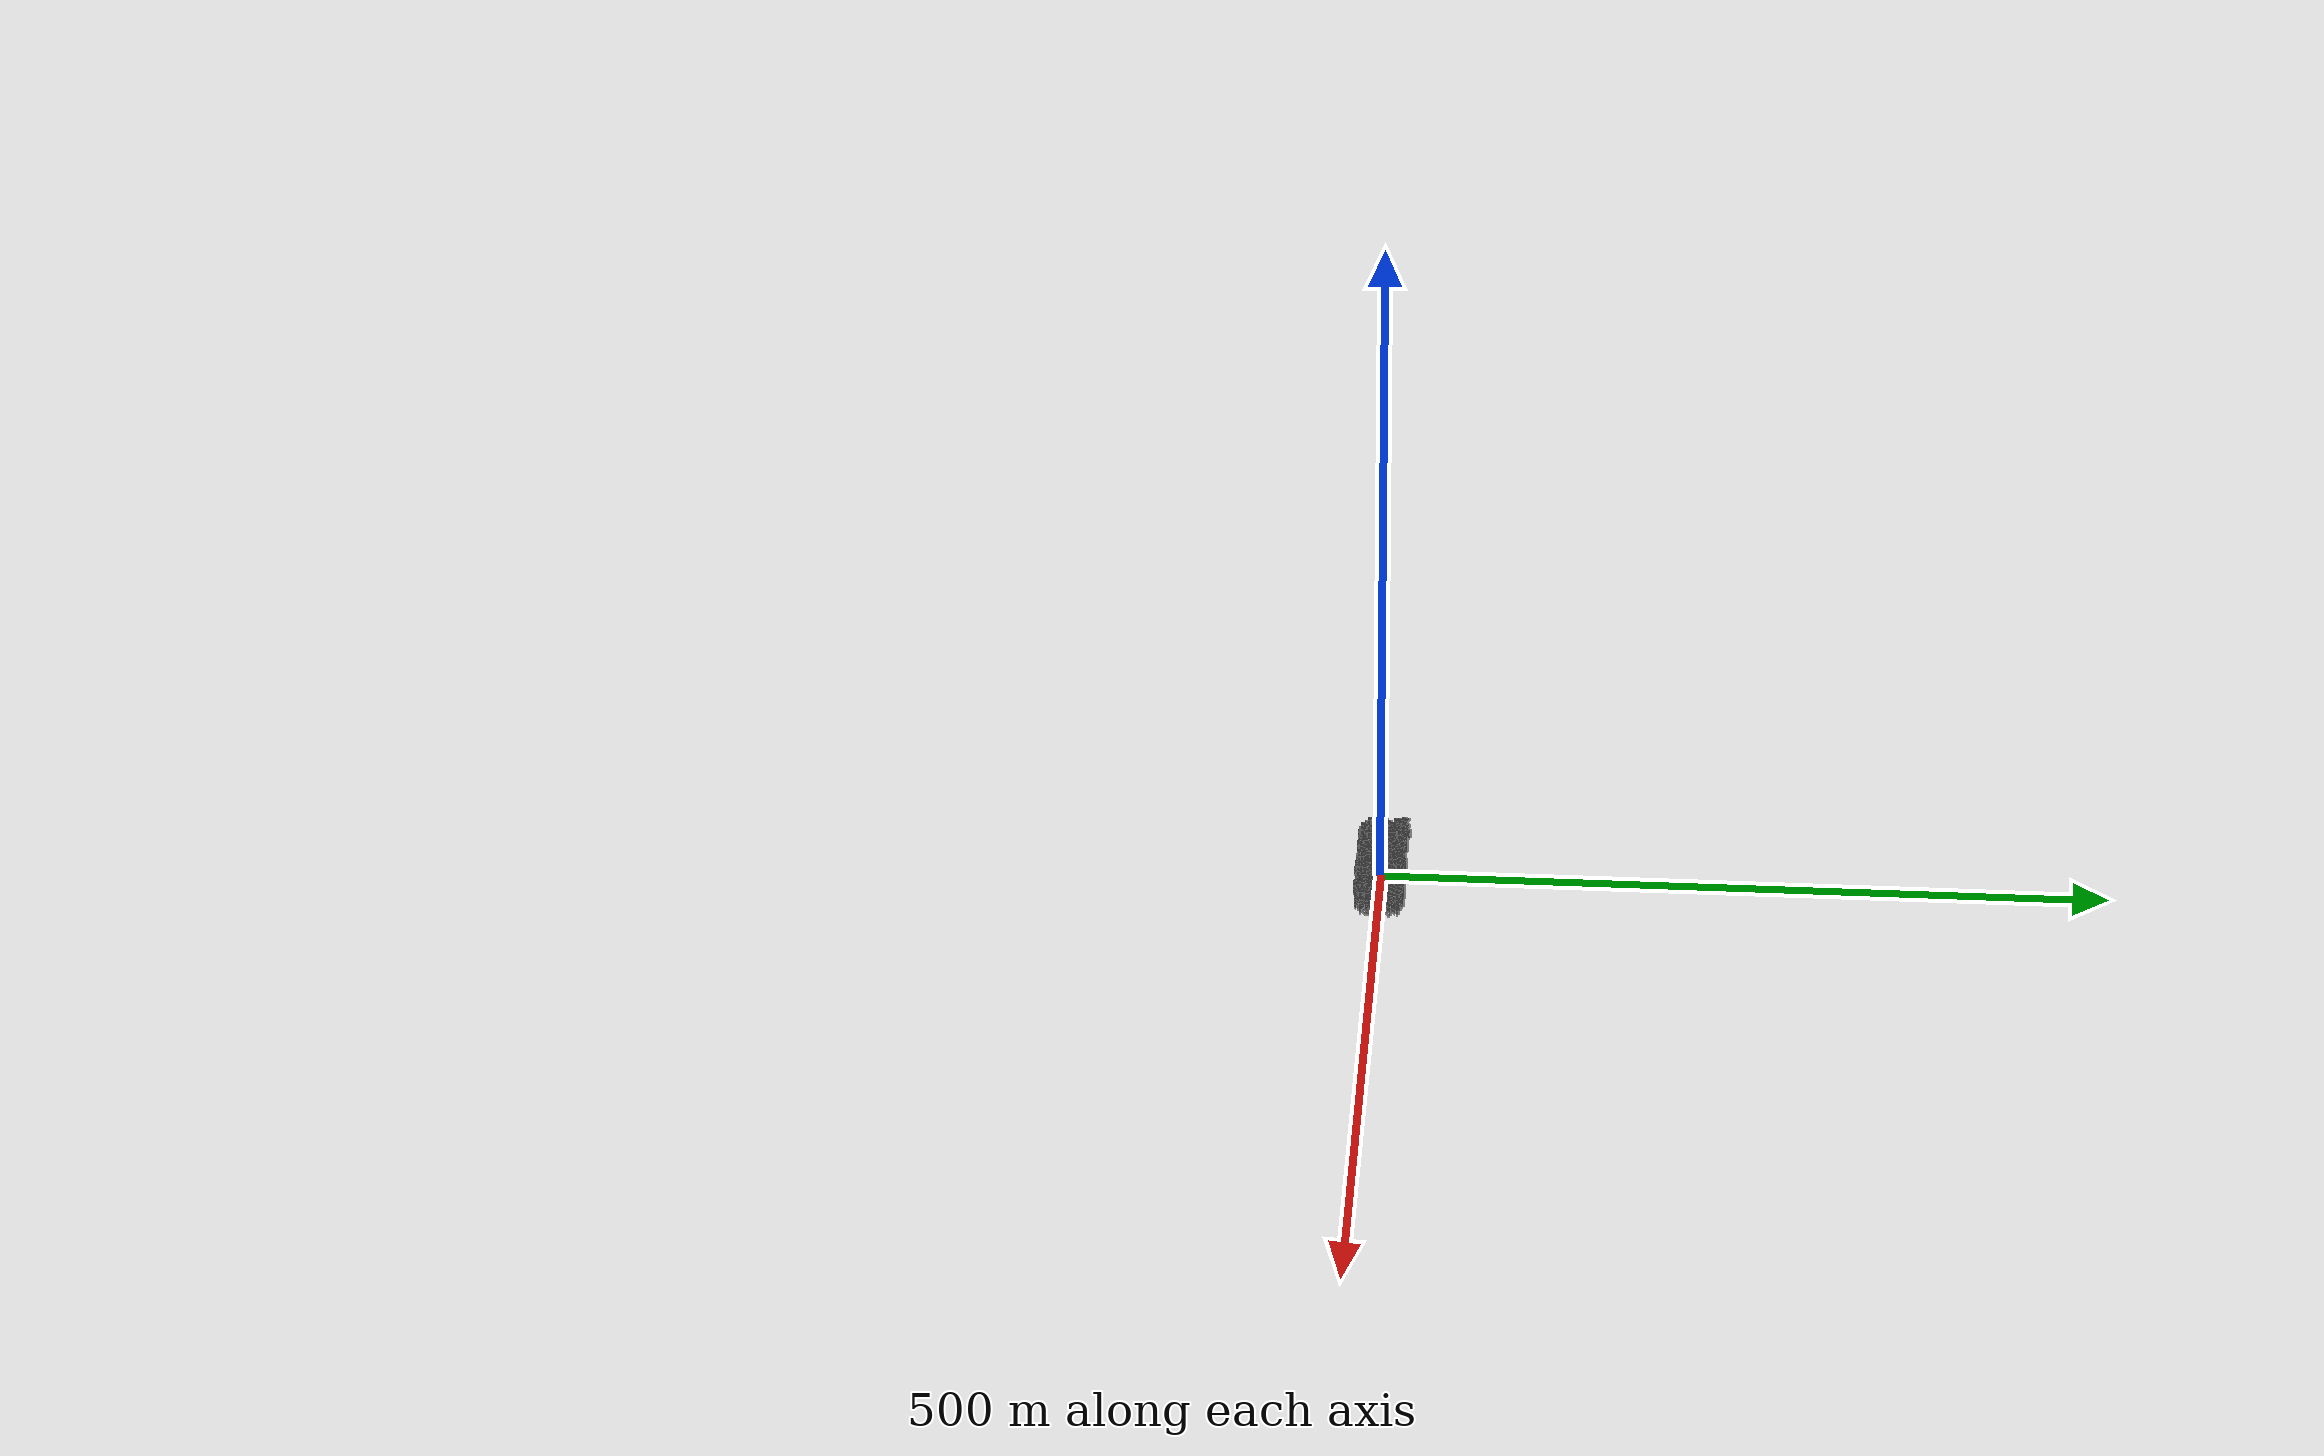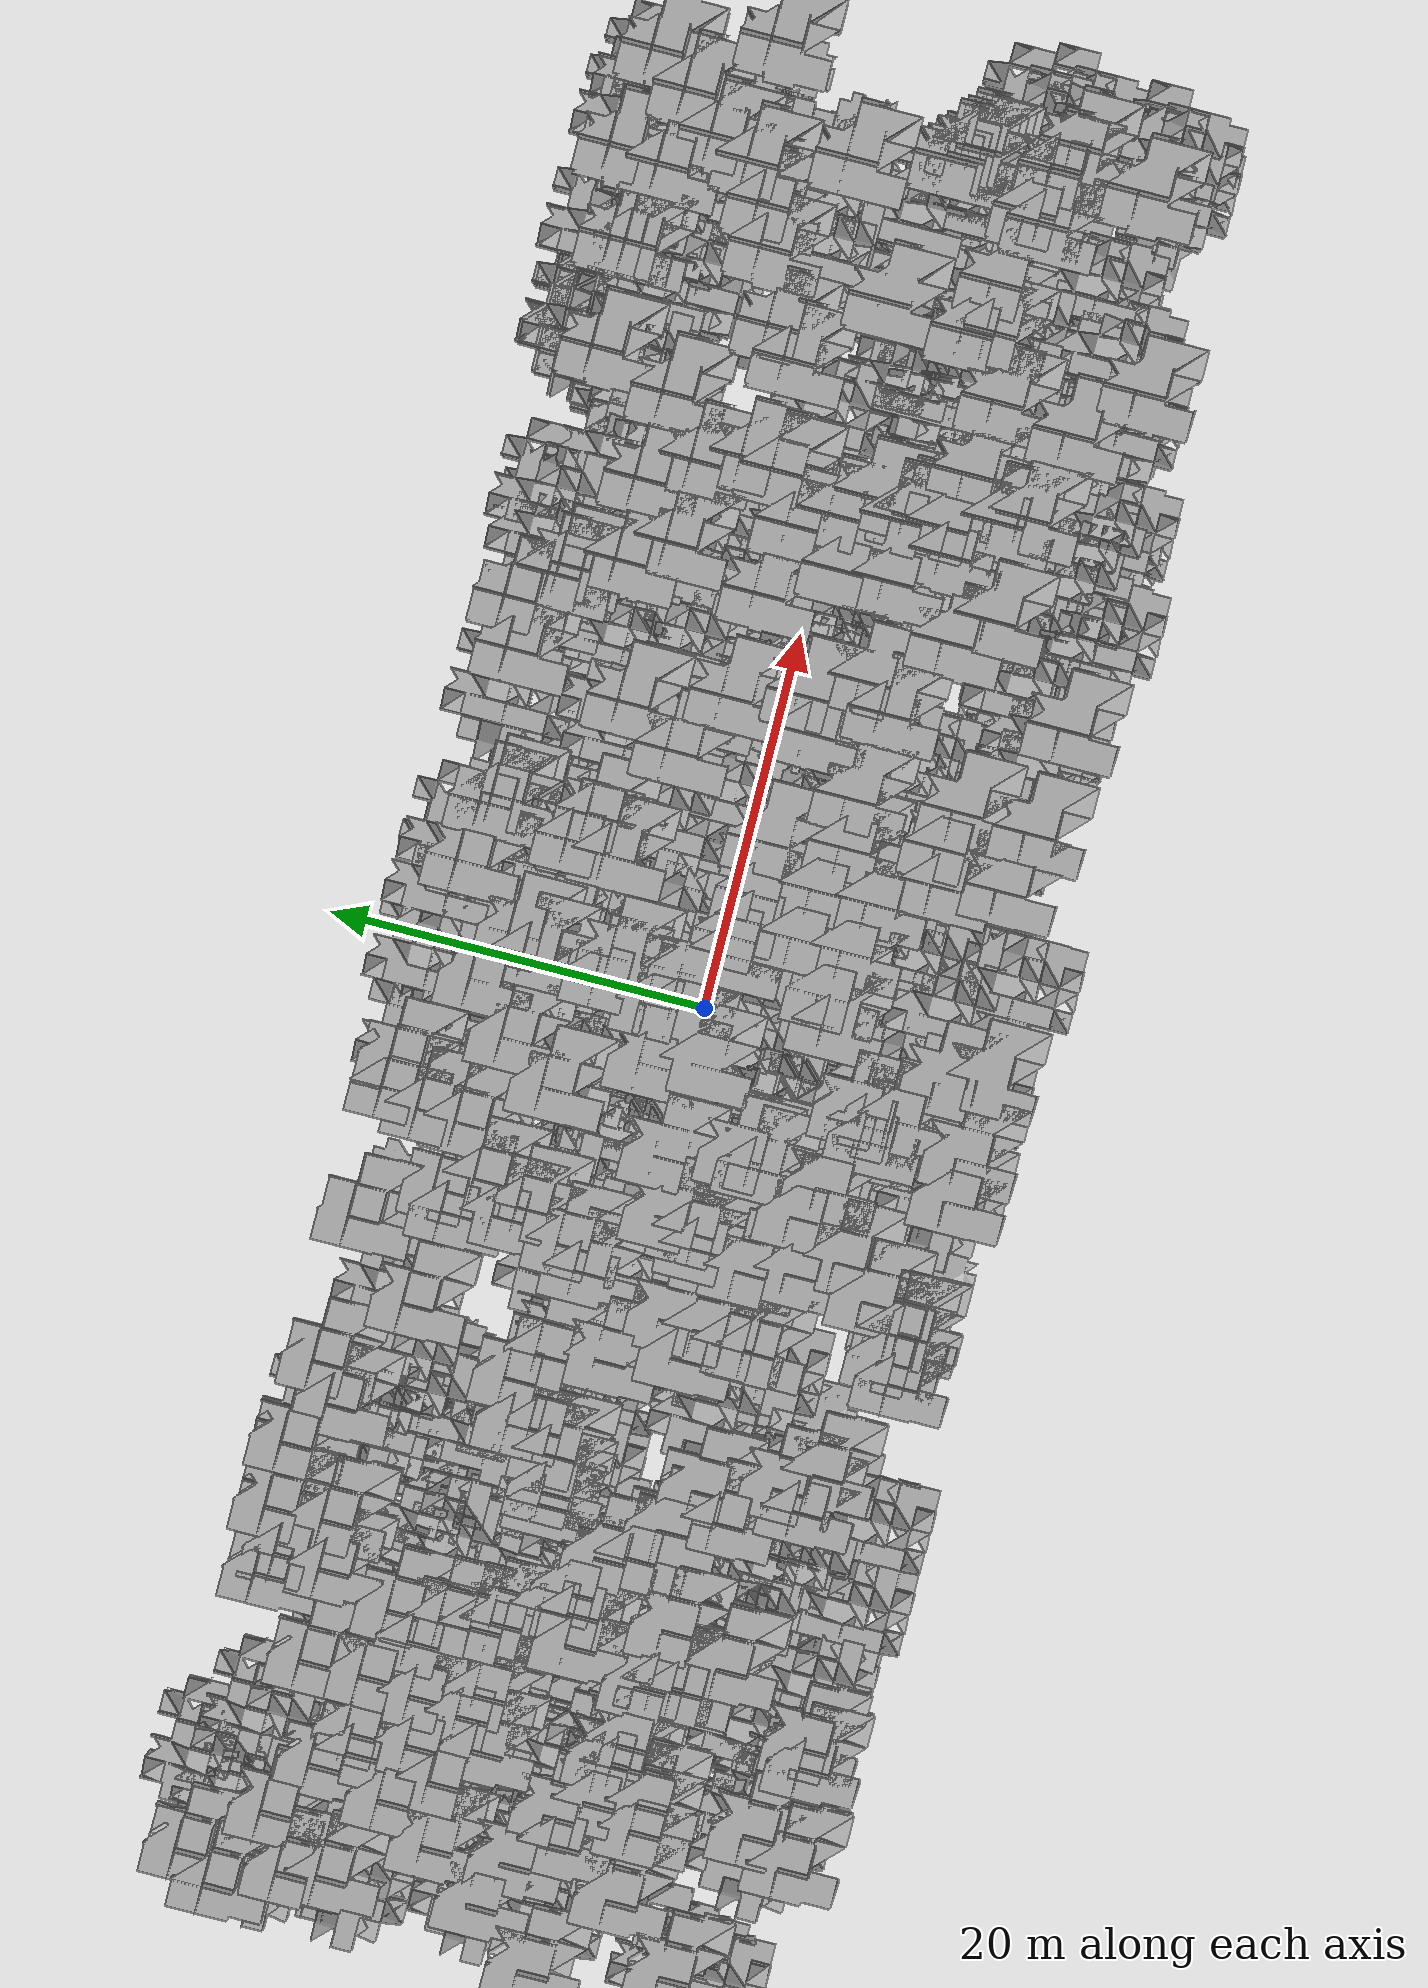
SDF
<sdf version="1.7">
    <world name="default">
        <plugin name="mrs_gazebo_static_transform_republisher_plugin" filename="libMrsGazeboCommonResources_StaticTransformRepublisher.so"/>
        <spherical_coordinates>
            <surface_model>EARTH_WGS84</surface_model>
            <latitude_deg>47.3977</latitude_deg>
            <longitude_deg>8.54559</longitude_deg>
            <elevation>0</elevation>
            <heading_deg>0</heading_deg>
        </spherical_coordinates>
        <physics name="default_physics" default="0" type="ode">
            <ode>
                <solver>
                    <type>quick</type>
                    <iters>10</iters>
                    <sor>1.3</sor>
                    <use_dynamic_moi_rescaling>0</use_dynamic_moi_rescaling>
                </solver>
                <constraints>
                    <cfm>0</cfm>
                    <erp>0.2</erp>
                    <contact_max_correcting_vel>1000</contact_max_correcting_vel>
                    <contact_surface_layer>0.001</contact_surface_layer>
                </constraints>
            </ode>
            <max_step_size>0.004</max_step_size>
            <real_time_factor>1</real_time_factor>
            <real_time_update_rate>250</real_time_update_rate>
        </physics>
        <scene>
            <shadows>0</shadows>
            <ambient>0.4 0.4 0.4 1</ambient>
            <background>0.7 0.7 0.7 1</background>
        </scene>
        <light name="sun" type="directional">
            <pose>0 0 1000 0.4 0.2 0</pose>
            <diffuse>1 1 1 1</diffuse>
            <specular>0.6 0.6 0.6 1</specular>
            <direction>0.1 0.1 -0.9</direction>
            <attenuation>
                <range>20</range>
                <constant>0.5</constant>
                <linear>0.01</linear>
                <quadratic>0.001</quadratic>
            </attenuation>
            <cast_shadows>1</cast_shadows>
            <spot>
                <inner_angle>0</inner_angle>
                <outer_angle>0</outer_angle>
                <falloff>0</falloff>
            </spot>
        </light>
        <model name="ground_plane">
            <static>1</static>
            <link name="link">
                <collision name="collision">
                    <pose>-50 0 0 0 -0 0</pose>
                    <geometry>
                        <plane>
                            <normal>0 0 1</normal>
                            <size>100 100</size>
                        </plane>
                    </geometry>
                    <surface>
                        <contact>
                            <ode>
                                <min_depth>0.01</min_depth>
                                <max_vel>0</max_vel>
                            </ode>
                        </contact>
                        <friction>
                            <ode/>
                            <torsional>
                                <ode/>
                            </torsional>
                        </friction>
                        <bounce/>
                    </surface>
                    <max_contacts>10</max_contacts>
                </collision>
                <visual name="grass">
                    <pose>0 0 0 0 -0 0</pose>
                    <cast_shadows>0</cast_shadows>
                    <geometry>
                        <mesh>
                            <scale>0.5814285714285714 0.18142857142857144 0.1</scale>
                            <uri>file://grass_plane/meshes/grass_plane.dae</uri>
                        </mesh>
                    </geometry>
                </visual>
                <self_collide>0</self_collide>
                <enable_wind>0</enable_wind>
                <kinematic>0</kinematic>
            </link>
        </model>
        <model name="the_void">
            <static>1</static>
            <link name="link">
                <pose>0 0 0.1 0 -0 0</pose>
                <visual name="the_void">
                    <pose>0 0 2 0 -0 0</pose>
                    <geometry>
                        <sphere>
                            <radius>0.25</radius>
                        </sphere>
                    </geometry>
                    <material>
                        <script>
                            <uri>file://media/materials/scripts/Gazebo.material</uri>
                            <name>Gazebo/Black</name>
                        </script>
                    </material>
                </visual>
                <self_collide>0</self_collide>
                <enable_wind>0</enable_wind>
                <kinematic>0</kinematic>
            </link>
            <pose>-1000 -1000 0 0 -0 0</pose>
        </model>
        <gui fullscreen="0">
            <camera name="camera">
                <pose>35.1577 98.6044 40.0204 0 0.407996 -1.99761</pose>
                <view_controller>orbit</view_controller>
                <projection_type>perspective</projection_type>
            </camera>
        </gui>
        <plugin name="mrs_gazebo_rviz_cam_synchronizer" filename="libMrsGazeboCommonResources_RvizCameraSynchronizer.so">
            <target_frame_id>gazebo_user_camera</target_frame_id>
            <world_origin_frame_id>uav1/gps_origin</world_origin_frame_id>
            <frame_to_follow>uav1</frame_to_follow>
        </plugin>
        <gravity>0 0 -9.8066</gravity>
        <magnetic_field>6e-06 2.3e-05 -4.2e-05</magnetic_field>
        <atmosphere type="adiabatic"/>
        <wind/>
        <model name="Tree 0">
            <static>1</static>
            <pose>-48.097148536025074 12.700255698125272 0 1.57079 -0 0</pose>
            <link name="link">
                <pose>0 0 0 0 -0 0</pose>
                <collision name="collision">
                    <geometry>
                        <mesh>
                            <scale>3.5 5 3.5</scale>
                            <uri>model://tree_9/meshes/tree_9.obj</uri>
                        </mesh>
                    </geometry>
                    <max_contacts>10</max_contacts>
                    <surface>
                        <contact>
                            <ode/>
                        </contact>
                        <bounce/>
                        <friction>
                            <torsional>
                                <ode/>
                            </torsional>
                            <ode/>
                        </friction>
                    </surface>
                </collision>
                <visual name="visual">
                    <geometry>
                        <mesh>
                            <scale>3.5 5 3.5</scale>
                            <uri>model://tree_9/meshes/tree_9.obj</uri>
                        </mesh>
                    </geometry>
                </visual>
                <self_collide>0</self_collide>
                <enable_wind>0</enable_wind>
                <kinematic>0</kinematic>
            </link>
        </model>
        <model name="Tree 1">
            <static>1</static>
            <pose>7.077662777359173 8.153100355233867 0 1.57079 -0 0</pose>
            <link name="link">
                <pose>0 0 0 0 -0 0</pose>
                <collision name="collision">
                    <geometry>
                        <mesh>
                            <scale>3.5 5 3.5</scale>
                            <uri>model://tree_9/meshes/tree_9.obj</uri>
                        </mesh>
                    </geometry>
                    <max_contacts>10</max_contacts>
                    <surface>
                        <contact>
                            <ode/>
                        </contact>
                        <bounce/>
                        <friction>
                            <torsional>
                                <ode/>
                            </torsional>
                            <ode/>
                        </friction>
                    </surface>
                </collision>
                <visual name="visual">
                    <geometry>
                        <mesh>
                            <scale>3.5 5 3.5</scale>
                            <uri>model://tree_9/meshes/tree_9.obj</uri>
                        </mesh>
                    </geometry>
                </visual>
                <self_collide>0</self_collide>
                <enable_wind>0</enable_wind>
                <kinematic>0</kinematic>
            </link>
        </model>
        <model name="Tree 2">
            <static>1</static>
            <pose>16.978074154273955 -1.2482701069600246 0 1.57079 -0 0</pose>
            <link name="link">
                <pose>0 0 0 0 -0 0</pose>
                <collision name="collision">
                    <geometry>
                        <mesh>
                            <scale>3.5 5 3.5</scale>
                            <uri>model://tree_9/meshes/tree_9.obj</uri>
                        </mesh>
                    </geometry>
                    <max_contacts>10</max_contacts>
                    <surface>
                        <contact>
                            <ode/>
                        </contact>
                        <bounce/>
                        <friction>
                            <torsional>
                                <ode/>
                            </torsional>
                            <ode/>
                        </friction>
                    </surface>
                </collision>
                <visual name="visual">
                    <geometry>
                        <mesh>
                            <scale>3.5 5 3.5</scale>
                            <uri>model://tree_9/meshes/tree_9.obj</uri>
                        </mesh>
                    </geometry>
                </visual>
                <self_collide>0</self_collide>
                <enable_wind>0</enable_wind>
                <kinematic>0</kinematic>
            </link>
        </model>
        <model name="Tree 3">
            <static>1</static>
            <pose>17.121440684502417 -5.409532549476941 0 1.57079 -0 0</pose>
            <link name="link">
                <pose>0 0 0 0 -0 0</pose>
                <collision name="collision">
                    <geometry>
                        <mesh>
                            <scale>3.5 5 3.5</scale>
                            <uri>model://tree_9/meshes/tree_9.obj</uri>
                        </mesh>
                    </geometry>
                    <max_contacts>10</max_contacts>
                    <surface>
                        <contact>
                            <ode/>
                        </contact>
                        <bounce/>
                        <friction>
                            <torsional>
                                <ode/>
                            </torsional>
                            <ode/>
                        </friction>
                    </surface>
                </collision>
                <visual name="visual">
                    <geometry>
                        <mesh>
                            <scale>3.5 5 3.5</scale>
                            <uri>model://tree_9/meshes/tree_9.obj</uri>
                        </mesh>
                    </geometry>
                </visual>
                <self_collide>0</self_collide>
                <enable_wind>0</enable_wind>
                <kinematic>0</kinematic>
            </link>
        </model>
        <model name="Tree 4">
            <static>1</static>
            <pose>-33.80315675549006 5.824767551993318 0 1.57079 -0 0</pose>
            <link name="link">
                <pose>0 0 0 0 -0 0</pose>
                <collision name="collision">
                    <geometry>
                        <mesh>
                            <scale>3.5 5 3.5</scale>
                            <uri>model://tree_9/meshes/tree_9.obj</uri>
                        </mesh>
                    </geometry>
                    <max_contacts>10</max_contacts>
                    <surface>
                        <contact>
                            <ode/>
                        </contact>
                        <bounce/>
                        <friction>
                            <torsional>
                                <ode/>
                            </torsional>
                            <ode/>
                        </friction>
                    </surface>
                </collision>
                <visual name="visual">
                    <geometry>
                        <mesh>
                            <scale>3.5 5 3.5</scale>
                            <uri>model://tree_9/meshes/tree_9.obj</uri>
                        </mesh>
                    </geometry>
                </visual>
                <self_collide>0</self_collide>
                <enable_wind>0</enable_wind>
                <kinematic>0</kinematic>
            </link>
        </model>
        <model name="Tree 5">
            <static>1</static>
            <pose>-29.21881399212414 -2.4998693914355172 0 1.57079 -0 0</pose>
            <link name="link">
                <pose>0 0 0 0 -0 0</pose>
                <collision name="collision">
                    <geometry>
                        <mesh>
                            <scale>3 2 3</scale>
                            <uri>model://tree_3/meshes/tree_3.obj</uri>
                        </mesh>
                    </geometry>
                    <max_contacts>10</max_contacts>
                    <surface>
                        <contact>
                            <ode/>
                        </contact>
                        <bounce/>
                        <friction>
                            <torsional>
                                <ode/>
                            </torsional>
                            <ode/>
                        </friction>
                    </surface>
                </collision>
                <visual name="visual">
                    <geometry>
                        <mesh>
                            <scale>3 2 3</scale>
                            <uri>model://tree_3/meshes/tree_3.obj</uri>
                        </mesh>
                    </geometry>
                </visual>
                <self_collide>0</self_collide>
                <enable_wind>0</enable_wind>
                <kinematic>0</kinematic>
            </link>
        </model>
        <model name="Tree 6">
            <static>1</static>
            <pose>-37.887973601087715 1.3199146387458143 0 1.57079 -0 0</pose>
            <link name="link">
                <pose>0 0 0 0 -0 0</pose>
                <collision name="collision">
                    <geometry>
                        <mesh>
                            <scale>3.5 5 3.5</scale>
                            <uri>model://tree_2/meshes/tree_2.obj</uri>
                        </mesh>
                    </geometry>
                    <max_contacts>10</max_contacts>
                    <surface>
                        <contact>
                            <ode/>
                        </contact>
                        <bounce/>
                        <friction>
                            <torsional>
                                <ode/>
                            </torsional>
                            <ode/>
                        </friction>
                    </surface>
                </collision>
                <visual name="visual">
                    <geometry>
                        <mesh>
                            <scale>3.5 5 3.5</scale>
                            <uri>model://tree_2/meshes/tree_2.obj</uri>
                        </mesh>
                    </geometry>
                </visual>
                <self_collide>0</self_collide>
                <enable_wind>0</enable_wind>
                <kinematic>0</kinematic>
            </link>
        </model>
        <model name="Tree 7">
            <static>1</static>
            <pose>0.12277957769375547 0.9770793056603875 0 1.57079 -0 0</pose>
            <link name="link">
                <pose>0 0 0 0 -0 0</pose>
                <collision name="collision">
                    <geometry>
                        <mesh>
                            <scale>3.5 5 3.5</scale>
                            <uri>model://tree_9/meshes/tree_9.obj</uri>
                        </mesh>
                    </geometry>
                    <max_contacts>10</max_contacts>
                    <surface>
                        <contact>
                            <ode/>
                        </contact>
                        <bounce/>
                        <friction>
                            <torsional>
                                <ode/>
                            </torsional>
                            <ode/>
                        </friction>
                    </surface>
                </collision>
                <visual name="visual">
                    <geometry>
                        <mesh>
                            <scale>3.5 5 3.5</scale>
                            <uri>model://tree_9/meshes/tree_9.obj</uri>
                        </mesh>
                    </geometry>
                </visual>
                <self_collide>0</self_collide>
                <enable_wind>0</enable_wind>
                <kinematic>0</kinematic>
            </link>
        </model>
        <model name="Tree 8">
            <static>1</static>
            <pose>-2.014990306784476 1.2075825491668652 0 1.57079 -0 0</pose>
            <link name="link">
                <pose>0 0 0 0 -0 0</pose>
                <collision name="collision">
                    <geometry>
                        <mesh>
                            <scale>3.5 5 3.5</scale>
                            <uri>model://tree_2/meshes/tree_2.obj</uri>
                        </mesh>
                    </geometry>
                    <max_contacts>10</max_contacts>
                    <surface>
                        <contact>
                            <ode/>
                        </contact>
                        <bounce/>
                        <friction>
                            <torsional>
                                <ode/>
                            </torsional>
                            <ode/>
                        </friction>
                    </surface>
                </collision>
                <visual name="visual">
                    <geometry>
                        <mesh>
                            <scale>3.5 5 3.5</scale>
                            <uri>model://tree_2/meshes/tree_2.obj</uri>
                        </mesh>
                    </geometry>
                </visual>
                <self_collide>0</self_collide>
                <enable_wind>0</enable_wind>
                <kinematic>0</kinematic>
            </link>
        </model>
        <model name="Tree 9">
            <static>1</static>
            <pose>43.18519281754021 -2.7200800898165927 0 1.57079 -0 0</pose>
            <link name="link">
                <pose>0 0 0 0 -0 0</pose>
                <collision name="collision">
                    <geometry>
                        <mesh>
                            <scale>3.5 5 3.5</scale>
                            <uri>model://tree_2/meshes/tree_2.obj</uri>
                        </mesh>
                    </geometry>
                    <max_contacts>10</max_contacts>
                    <surface>
                        <contact>
                            <ode/>
                        </contact>
                        <bounce/>
                        <friction>
                            <torsional>
                                <ode/>
                            </torsional>
                            <ode/>
                        </friction>
                    </surface>
                </collision>
                <visual name="visual">
                    <geometry>
                        <mesh>
                            <scale>3.5 5 3.5</scale>
                            <uri>model://tree_2/meshes/tree_2.obj</uri>
                        </mesh>
                    </geometry>
                </visual>
                <self_collide>0</self_collide>
                <enable_wind>0</enable_wind>
                <kinematic>0</kinematic>
            </link>
        </model>
        <model name="Tree 10">
            <static>1</static>
            <pose>23.41770234843692 13.937861952048472 0 1.57079 -0 0</pose>
            <link name="link">
                <pose>0 0 0 0 -0 0</pose>
                <collision name="collision">
                    <geometry>
                        <mesh>
                            <scale>3.5 5 3.5</scale>
                            <uri>model://tree_2/meshes/tree_2.obj</uri>
                        </mesh>
                    </geometry>
                    <max_contacts>10</max_contacts>
                    <surface>
                        <contact>
                            <ode/>
                        </contact>
                        <bounce/>
                        <friction>
                            <torsional>
                                <ode/>
                            </torsional>
                            <ode/>
                        </friction>
                    </surface>
                </collision>
                <visual name="visual">
                    <geometry>
                        <mesh>
                            <scale>3.5 5 3.5</scale>
                            <uri>model://tree_2/meshes/tree_2.obj</uri>
                        </mesh>
                    </geometry>
                </visual>
                <self_collide>0</self_collide>
                <enable_wind>0</enable_wind>
                <kinematic>0</kinematic>
            </link>
        </model>
        <model name="Tree 11">
            <static>1</static>
            <pose>45.75317328389755 -6.967052973280747 0 1.57079 -0 0</pose>
            <link name="link">
                <pose>0 0 0 0 -0 0</pose>
                <collision name="collision">
                    <geometry>
                        <mesh>
                            <scale>3.5 5 3.5</scale>
                            <uri>model://tree_9/meshes/tree_9.obj</uri>
                        </mesh>
                    </geometry>
                    <max_contacts>10</max_contacts>
                    <surface>
                        <contact>
                            <ode/>
                        </contact>
                        <bounce/>
                        <friction>
                            <torsional>
                                <ode/>
                            </torsional>
                            <ode/>
                        </friction>
                    </surface>
                </collision>
                <visual name="visual">
                    <geometry>
                        <mesh>
                            <scale>3.5 5 3.5</scale>
                            <uri>model://tree_9/meshes/tree_9.obj</uri>
                        </mesh>
                    </geometry>
                </visual>
                <self_collide>0</self_collide>
                <enable_wind>0</enable_wind>
                <kinematic>0</kinematic>
            </link>
        </model>
        <model name="Tree 12">
            <static>1</static>
            <pose>15.982884441696811 2.444201014498038 0 1.57079 -0 0</pose>
            <link name="link">
                <pose>0 0 0 0 -0 0</pose>
                <collision name="collision">
                    <geometry>
                        <mesh>
                            <scale>3.5 5 3.5</scale>
                            <uri>model://tree_9/meshes/tree_9.obj</uri>
                        </mesh>
                    </geometry>
                    <max_contacts>10</max_contacts>
                    <surface>
                        <contact>
                            <ode/>
                        </contact>
                        <bounce/>
                        <friction>
                            <torsional>
                                <ode/>
                            </torsional>
                            <ode/>
                        </friction>
                    </surface>
                </collision>
                <visual name="visual">
                    <geometry>
                        <mesh>
                            <scale>3.5 5 3.5</scale>
                            <uri>model://tree_9/meshes/tree_9.obj</uri>
                        </mesh>
                    </geometry>
                </visual>
                <self_collide>0</self_collide>
                <enable_wind>0</enable_wind>
                <kinematic>0</kinematic>
            </link>
        </model>
        <model name="Tree 13">
            <static>1</static>
            <pose>-17.790858090442658 0.2607202713093333 0 1.57079 -0 0</pose>
            <link name="link">
                <pose>0 0 0 0 -0 0</pose>
                <collision name="collision">
                    <geometry>
                        <mesh>
                            <scale>3.5 5 3.5</scale>
                            <uri>model://tree_9/meshes/tree_9.obj</uri>
                        </mesh>
                    </geometry>
                    <max_contacts>10</max_contacts>
                    <surface>
                        <contact>
                            <ode/>
                        </contact>
                        <bounce/>
                        <friction>
                            <torsional>
                                <ode/>
                            </torsional>
                            <ode/>
                        </friction>
                    </surface>
                </collision>
                <visual name="visual">
                    <geometry>
                        <mesh>
                            <scale>3.5 5 3.5</scale>
                            <uri>model://tree_9/meshes/tree_9.obj</uri>
                        </mesh>
                    </geometry>
                </visual>
                <self_collide>0</self_collide>
                <enable_wind>0</enable_wind>
                <kinematic>0</kinematic>
            </link>
        </model>
        <model name="Tree 14">
            <static>1</static>
            <pose>-0.8850164242984562 11.105231925319103 0 1.57079 -0 0</pose>
            <link name="link">
                <pose>0 0 0 0 -0 0</pose>
                <collision name="collision">
                    <geometry>
                        <mesh>
                            <scale>3.5 5 3.5</scale>
                            <uri>model://tree_9/meshes/tree_9.obj</uri>
                        </mesh>
                    </geometry>
                    <max_contacts>10</max_contacts>
                    <surface>
                        <contact>
                            <ode/>
                        </contact>
                        <bounce/>
                        <friction>
                            <torsional>
                                <ode/>
                            </torsional>
                            <ode/>
                        </friction>
                    </surface>
                </collision>
                <visual name="visual">
                    <geometry>
                        <mesh>
                            <scale>3.5 5 3.5</scale>
                            <uri>model://tree_9/meshes/tree_9.obj</uri>
                        </mesh>
                    </geometry>
                </visual>
                <self_collide>0</self_collide>
                <enable_wind>0</enable_wind>
                <kinematic>0</kinematic>
            </link>
        </model>
        <model name="Tree 15">
            <static>1</static>
            <pose>4.864281417624234 11.829364958286991 0 1.57079 -0 0</pose>
            <link name="link">
                <pose>0 0 0 0 -0 0</pose>
                <collision name="collision">
                    <geometry>
                        <mesh>
                            <scale>3 2 3</scale>
                            <uri>model://tree_3/meshes/tree_3.obj</uri>
                        </mesh>
                    </geometry>
                    <max_contacts>10</max_contacts>
                    <surface>
                        <contact>
                            <ode/>
                        </contact>
                        <bounce/>
                        <friction>
                            <torsional>
                                <ode/>
                            </torsional>
                            <ode/>
                        </friction>
                    </surface>
                </collision>
                <visual name="visual">
                    <geometry>
                        <mesh>
                            <scale>3 2 3</scale>
                            <uri>model://tree_3/meshes/tree_3.obj</uri>
                        </mesh>
                    </geometry>
                </visual>
                <self_collide>0</self_collide>
                <enable_wind>0</enable_wind>
                <kinematic>0</kinematic>
            </link>
        </model>
        <model name="Tree 16">
            <static>1</static>
            <pose>1.9173290882321297 4.595612112184778 0 1.57079 -0 0</pose>
            <link name="link">
                <pose>0 0 0 0 -0 0</pose>
                <collision name="collision">
                    <geometry>
                        <mesh>
                            <scale>3.5 5 3.5</scale>
                            <uri>model://tree_9/meshes/tree_9.obj</uri>
                        </mesh>
                    </geometry>
                    <max_contacts>10</max_contacts>
                    <surface>
                        <contact>
                            <ode/>
                        </contact>
                        <bounce/>
                        <friction>
                            <torsional>
                                <ode/>
                            </torsional>
                            <ode/>
                        </friction>
                    </surface>
                </collision>
                <visual name="visual">
                    <geometry>
                        <mesh>
                            <scale>3.5 5 3.5</scale>
                            <uri>model://tree_9/meshes/tree_9.obj</uri>
                        </mesh>
                    </geometry>
                </visual>
                <self_collide>0</self_collide>
                <enable_wind>0</enable_wind>
                <kinematic>0</kinematic>
            </link>
        </model>
        <model name="Tree 17">
            <static>1</static>
            <pose>39.75413066038645 -12.15380586839474 0 1.57079 -0 0</pose>
            <link name="link">
                <pose>0 0 0 0 -0 0</pose>
                <collision name="collision">
                    <geometry>
                        <mesh>
                            <scale>4 2.5 4</scale>
                            <uri>model://tree_1/meshes/tree_1.obj</uri>
                        </mesh>
                    </geometry>
                    <max_contacts>10</max_contacts>
                    <surface>
                        <contact>
                            <ode/>
                        </contact>
                        <bounce/>
                        <friction>
                            <torsional>
                                <ode/>
                            </torsional>
                            <ode/>
                        </friction>
                    </surface>
                </collision>
                <visual name="visual">
                    <geometry>
                        <mesh>
                            <scale>4 2.5 4</scale>
                            <uri>model://tree_1/meshes/tree_1.obj</uri>
                        </mesh>
                    </geometry>
                </visual>
                <self_collide>0</self_collide>
                <enable_wind>0</enable_wind>
                <kinematic>0</kinematic>
            </link>
        </model>
        <model name="Tree 18">
            <static>1</static>
            <pose>1.0117634029539886 8.809571183129197 0 1.57079 -0 0</pose>
            <link name="link">
                <pose>0 0 0 0 -0 0</pose>
                <collision name="collision">
                    <geometry>
                        <mesh>
                            <scale>3.5 5 3.5</scale>
                            <uri>model://tree_9/meshes/tree_9.obj</uri>
                        </mesh>
                    </geometry>
                    <max_contacts>10</max_contacts>
                    <surface>
                        <contact>
                            <ode/>
                        </contact>
                        <bounce/>
                        <friction>
                            <torsional>
                                <ode/>
                            </torsional>
                            <ode/>
                        </friction>
                    </surface>
                </collision>
                <visual name="visual">
                    <geometry>
                        <mesh>
                            <scale>3.5 5 3.5</scale>
                            <uri>model://tree_9/meshes/tree_9.obj</uri>
                        </mesh>
                    </geometry>
                </visual>
                <self_collide>0</self_collide>
                <enable_wind>0</enable_wind>
                <kinematic>0</kinematic>
            </link>
        </model>
        <model name="Tree 19">
            <static>1</static>
            <pose>33.62600393076522 -7.004336705707363 0 1.57079 -0 0</pose>
            <link name="link">
                <pose>0 0 0 0 -0 0</pose>
                <collision name="collision">
                    <geometry>
                        <mesh>
                            <scale>3.5 5 3.5</scale>
                            <uri>model://tree_9/meshes/tree_9.obj</uri>
                        </mesh>
                    </geometry>
                    <max_contacts>10</max_contacts>
                    <surface>
                        <contact>
                            <ode/>
                        </contact>
                        <bounce/>
                        <friction>
                            <torsional>
                                <ode/>
                            </torsional>
                            <ode/>
                        </friction>
                    </surface>
                </collision>
                <visual name="visual">
                    <geometry>
                        <mesh>
                            <scale>3.5 5 3.5</scale>
                            <uri>model://tree_9/meshes/tree_9.obj</uri>
                        </mesh>
                    </geometry>
                </visual>
                <self_collide>0</self_collide>
                <enable_wind>0</enable_wind>
                <kinematic>0</kinematic>
            </link>
        </model>
        <model name="Tree 20">
            <static>1</static>
            <pose>23.373944926552966 5.9327887237196 0 1.57079 -0 0</pose>
            <link name="link">
                <pose>0 0 0 0 -0 0</pose>
                <collision name="collision">
                    <geometry>
                        <mesh>
                            <scale>3.5 5 3.5</scale>
                            <uri>model://tree_2/meshes/tree_2.obj</uri>
                        </mesh>
                    </geometry>
                    <max_contacts>10</max_contacts>
                    <surface>
                        <contact>
                            <ode/>
                        </contact>
                        <bounce/>
                        <friction>
                            <torsional>
                                <ode/>
                            </torsional>
                            <ode/>
                        </friction>
                    </surface>
                </collision>
                <visual name="visual">
                    <geometry>
                        <mesh>
                            <scale>3.5 5 3.5</scale>
                            <uri>model://tree_2/meshes/tree_2.obj</uri>
                        </mesh>
                    </geometry>
                </visual>
                <self_collide>0</self_collide>
                <enable_wind>0</enable_wind>
                <kinematic>0</kinematic>
            </link>
        </model>
        <model name="Tree 21">
            <static>1</static>
            <pose>21.367335471457935 2.1519935512606843 0 1.57079 -0 0</pose>
            <link name="link">
                <pose>0 0 0 0 -0 0</pose>
                <collision name="collision">
                    <geometry>
                        <mesh>
                            <scale>3.5 5 3.5</scale>
                            <uri>model://tree_9/meshes/tree_9.obj</uri>
                        </mesh>
                    </geometry>
                    <max_contacts>10</max_contacts>
                    <surface>
                        <contact>
                            <ode/>
                        </contact>
                        <bounce/>
                        <friction>
                            <torsional>
                                <ode/>
                            </torsional>
                            <ode/>
                        </friction>
                    </surface>
                </collision>
                <visual name="visual">
                    <geometry>
                        <mesh>
                            <scale>3.5 5 3.5</scale>
                            <uri>model://tree_9/meshes/tree_9.obj</uri>
                        </mesh>
                    </geometry>
                </visual>
                <self_collide>0</self_collide>
                <enable_wind>0</enable_wind>
                <kinematic>0</kinematic>
            </link>
        </model>
        <model name="Tree 22">
            <static>1</static>
            <pose>37.27590467422013 14.803807255800841 0 1.57079 -0 0</pose>
            <link name="link">
                <pose>0 0 0 0 -0 0</pose>
                <collision name="collision">
                    <geometry>
                        <mesh>
                            <scale>3.5 5 3.5</scale>
                            <uri>model://tree_2/meshes/tree_2.obj</uri>
                        </mesh>
                    </geometry>
                    <max_contacts>10</max_contacts>
                    <surface>
                        <contact>
                            <ode/>
                        </contact>
                        <bounce/>
                        <friction>
                            <torsional>
                                <ode/>
                            </torsional>
                            <ode/>
                        </friction>
                    </surface>
                </collision>
                <visual name="visual">
                    <geometry>
                        <mesh>
                            <scale>3.5 5 3.5</scale>
                            <uri>model://tree_2/meshes/tree_2.obj</uri>
                        </mesh>
                    </geometry>
                </visual>
                <self_collide>0</self_collide>
                <enable_wind>0</enable_wind>
                <kinematic>0</kinematic>
            </link>
        </model>
        <model name="Tree 23">
            <static>1</static>
            <pose>34.39486902254079 -12.86158856818378 0 1.57079 -0 0</pose>
            <link name="link">
                <pose>0 0 0 0 -0 0</pose>
                <collision name="collision">
                    <geometry>
                        <mesh>
                            <scale>3.5 5 3.5</scale>
                            <uri>model://tree_2/meshes/tree_2.obj</uri>
                        </mesh>
                    </geometry>
                    <max_contacts>10</max_contacts>
                    <surface>
                        <contact>
                            <ode/>
                        </contact>
                        <bounce/>
                        <friction>
                            <torsional>
                                <ode/>
                            </torsional>
                            <ode/>
                        </friction>
                    </surface>
                </collision>
                <visual name="visual">
                    <geometry>
                        <mesh>
                            <scale>3.5 5 3.5</scale>
                            <uri>model://tree_2/meshes/tree_2.obj</uri>
                        </mesh>
                    </geometry>
                </visual>
                <self_collide>0</self_collide>
                <enable_wind>0</enable_wind>
                <kinematic>0</kinematic>
            </link>
        </model>
        <model name="Tree 24">
            <static>1</static>
            <pose>21.791082474754603 13.55375864014023 0 1.57079 -0 0</pose>
            <link name="link">
                <pose>0 0 0 0 -0 0</pose>
                <collision name="collision">
                    <geometry>
                        <mesh>
                            <scale>3.5 5 3.5</scale>
                            <uri>model://tree_2/meshes/tree_2.obj</uri>
                        </mesh>
                    </geometry>
                    <max_contacts>10</max_contacts>
                    <surface>
                        <contact>
                            <ode/>
                        </contact>
                        <bounce/>
                        <friction>
                            <torsional>
                                <ode/>
                            </torsional>
                            <ode/>
                        </friction>
                    </surface>
                </collision>
                <visual name="visual">
                    <geometry>
                        <mesh>
                            <scale>3.5 5 3.5</scale>
                            <uri>model://tree_2/meshes/tree_2.obj</uri>
                        </mesh>
                    </geometry>
                </visual>
                <self_collide>0</self_collide>
                <enable_wind>0</enable_wind>
                <kinematic>0</kinematic>
            </link>
        </model>
        <model name="Tree 25">
            <static>1</static>
            <pose>44.594107028790646 -4.715149866623674 0 1.57079 -0 0</pose>
            <link name="link">
                <pose>0 0 0 0 -0 0</pose>
                <collision name="collision">
                    <geometry>
                        <mesh>
                            <scale>3.5 5 3.5</scale>
                            <uri>model://tree_2/meshes/tree_2.obj</uri>
                        </mesh>
                    </geometry>
                    <max_contacts>10</max_contacts>
                    <surface>
                        <contact>
                            <ode/>
                        </contact>
                        <bounce/>
                        <friction>
                            <torsional>
                                <ode/>
                            </torsional>
                            <ode/>
                        </friction>
                    </surface>
                </collision>
                <visual name="visual">
                    <geometry>
                        <mesh>
                            <scale>3.5 5 3.5</scale>
                            <uri>model://tree_2/meshes/tree_2.obj</uri>
                        </mesh>
                    </geometry>
                </visual>
                <self_collide>0</self_collide>
                <enable_wind>0</enable_wind>
                <kinematic>0</kinematic>
            </link>
        </model>
        <model name="Tree 26">
            <static>1</static>
            <pose>-21.81426646399814 -9.955179589205766 0 1.57079 -0 0</pose>
            <link name="link">
                <pose>0 0 0 0 -0 0</pose>
                <collision name="collision">
                    <geometry>
                        <mesh>
                            <scale>3.5 5 3.5</scale>
                            <uri>model://tree_9/meshes/tree_9.obj</uri>
                        </mesh>
                    </geometry>
                    <max_contacts>10</max_contacts>
                    <surface>
                        <contact>
                            <ode/>
                        </contact>
                        <bounce/>
                        <friction>
                            <torsional>
                                <ode/>
                            </torsional>
                            <ode/>
                        </friction>
                    </surface>
                </collision>
                <visual name="visual">
                    <geometry>
                        <mesh>
                            <scale>3.5 5 3.5</scale>
                            <uri>model://tree_9/meshes/tree_9.obj</uri>
                        </mesh>
                    </geometry>
                </visual>
                <self_collide>0</self_collide>
                <enable_wind>0</enable_wind>
                <kinematic>0</kinematic>
            </link>
        </model>
        <model name="Tree 27">
            <static>1</static>
            <pose>-15.120431468305682 -4.108669234178874 0 1.57079 -0 0</pose>
            <link name="link">
                <pose>0 0 0 0 -0 0</pose>
                <collision name="collision">
                    <geometry>
                        <mesh>
                            <scale>3.5 5 3.5</scale>
                            <uri>model://tree_9/meshes/tree_9.obj</uri>
                        </mesh>
                    </geometry>
                    <max_contacts>10</max_contacts>
                    <surface>
                        <contact>
                            <ode/>
                        </contact>
                        <bounce/>
                        <friction>
                            <torsional>
                                <ode/>
                            </torsional>
                            <ode/>
                        </friction>
                    </surface>
                </collision>
                <visual name="visual">
                    <geometry>
                        <mesh>
                            <scale>3.5 5 3.5</scale>
                            <uri>model://tree_9/meshes/tree_9.obj</uri>
                        </mesh>
                    </geometry>
                </visual>
                <self_collide>0</self_collide>
                <enable_wind>0</enable_wind>
                <kinematic>0</kinematic>
            </link>
        </model>
        <model name="Tree 28">
            <static>1</static>
            <pose>22.24427193774015 -10.939156199806654 0 1.57079 -0 0</pose>
            <link name="link">
                <pose>0 0 0 0 -0 0</pose>
                <collision name="collision">
                    <geometry>
                        <mesh>
                            <scale>3.5 5 3.5</scale>
                            <uri>model://tree_2/meshes/tree_2.obj</uri>
                        </mesh>
                    </geometry>
                    <max_contacts>10</max_contacts>
                    <surface>
                        <contact>
                            <ode/>
                        </contact>
                        <bounce/>
                        <friction>
                            <torsional>
                                <ode/>
                            </torsional>
                            <ode/>
                        </friction>
                    </surface>
                </collision>
                <visual name="visual">
                    <geometry>
                        <mesh>
                            <scale>3.5 5 3.5</scale>
                            <uri>model://tree_2/meshes/tree_2.obj</uri>
                        </mesh>
                    </geometry>
                </visual>
                <self_collide>0</self_collide>
                <enable_wind>0</enable_wind>
                <kinematic>0</kinematic>
            </link>
        </model>
        <model name="Tree 29">
            <static>1</static>
            <pose>-21.955945992777426 3.7048564605818015 0 1.57079 -0 0</pose>
            <link name="link">
                <pose>0 0 0 0 -0 0</pose>
                <collision name="collision">
                    <geometry>
                        <mesh>
                            <scale>3.5 5 3.5</scale>
                            <uri>model://tree_9/meshes/tree_9.obj</uri>
                        </mesh>
                    </geometry>
                    <max_contacts>10</max_contacts>
                    <surface>
                        <contact>
                            <ode/>
                        </contact>
                        <bounce/>
                        <friction>
                            <torsional>
                                <ode/>
                            </torsional>
                            <ode/>
                        </friction>
                    </surface>
                </collision>
                <visual name="visual">
                    <geometry>
                        <mesh>
                            <scale>3.5 5 3.5</scale>
                            <uri>model://tree_9/meshes/tree_9.obj</uri>
                        </mesh>
                    </geometry>
                </visual>
                <self_collide>0</self_collide>
                <enable_wind>0</enable_wind>
                <kinematic>0</kinematic>
            </link>
        </model>
        <model name="Tree 30">
            <static>1</static>
            <pose>-33.71917963935912 -8.957106925812333 0 1.57079 -0 0</pose>
            <link name="link">
                <pose>0 0 0 0 -0 0</pose>
                <collision name="collision">
                    <geometry>
                        <mesh>
                            <scale>4 2.5 4</scale>
                            <uri>model://tree_1/meshes/tree_1.obj</uri>
                        </mesh>
                    </geometry>
                    <max_contacts>10</max_contacts>
                    <surface>
                        <contact>
                            <ode/>
                        </contact>
                        <bounce/>
                        <friction>
                            <torsional>
                                <ode/>
                            </torsional>
                            <ode/>
                        </friction>
                    </surface>
                </collision>
                <visual name="visual">
                    <geometry>
                        <mesh>
                            <scale>4 2.5 4</scale>
                            <uri>model://tree_1/meshes/tree_1.obj</uri>
                        </mesh>
                    </geometry>
                </visual>
                <self_collide>0</self_collide>
                <enable_wind>0</enable_wind>
                <kinematic>0</kinematic>
            </link>
        </model>
        <model name="Tree 31">
            <static>1</static>
            <pose>-43.290989155444414 1.189740722010601 0 1.57079 -0 0</pose>
            <link name="link">
                <pose>0 0 0 0 -0 0</pose>
                <collision name="collision">
                    <geometry>
                        <mesh>
                            <scale>3.5 5 3.5</scale>
                            <uri>model://tree_2/meshes/tree_2.obj</uri>
                        </mesh>
                    </geometry>
                    <max_contacts>10</max_contacts>
                    <surface>
                        <contact>
                            <ode/>
                        </contact>
                        <bounce/>
                        <friction>
                            <torsional>
                                <ode/>
                            </torsional>
                            <ode/>
                        </friction>
                    </surface>
                </collision>
                <visual name="visual">
                    <geometry>
                        <mesh>
                            <scale>3.5 5 3.5</scale>
                            <uri>model://tree_2/meshes/tree_2.obj</uri>
                        </mesh>
                    </geometry>
                </visual>
                <self_collide>0</self_collide>
                <enable_wind>0</enable_wind>
                <kinematic>0</kinematic>
            </link>
        </model>
        <model name="Tree 32">
            <static>1</static>
            <pose>-25.263312509131836 -4.865524858127504 0 1.57079 -0 0</pose>
            <link name="link">
                <pose>0 0 0 0 -0 0</pose>
                <collision name="collision">
                    <geometry>
                        <mesh>
                            <scale>3.5 5 3.5</scale>
                            <uri>model://tree_9/meshes/tree_9.obj</uri>
                        </mesh>
                    </geometry>
                    <max_contacts>10</max_contacts>
                    <surface>
                        <contact>
                            <ode/>
                        </contact>
                        <bounce/>
                        <friction>
                            <torsional>
                                <ode/>
                            </torsional>
                            <ode/>
                        </friction>
                    </surface>
                </collision>
                <visual name="visual">
                    <geometry>
                        <mesh>
                            <scale>3.5 5 3.5</scale>
                            <uri>model://tree_9/meshes/tree_9.obj</uri>
                        </mesh>
                    </geometry>
                </visual>
                <self_collide>0</self_collide>
                <enable_wind>0</enable_wind>
                <kinematic>0</kinematic>
            </link>
        </model>
        <model name="Tree 33">
            <static>1</static>
            <pose>-34.60206183858718 -11.260886650988464 0 1.57079 -0 0</pose>
            <link name="link">
                <pose>0 0 0 0 -0 0</pose>
                <collision name="collision">
                    <geometry>
                        <mesh>
                            <scale>3.5 5 3.5</scale>
                            <uri>model://tree_2/meshes/tree_2.obj</uri>
                        </mesh>
                    </geometry>
                    <max_contacts>10</max_contacts>
                    <surface>
                        <contact>
                            <ode/>
                        </contact>
                        <bounce/>
                        <friction>
                            <torsional>
                                <ode/>
                            </torsional>
                            <ode/>
                        </friction>
                    </surface>
                </collision>
                <visual name="visual">
                    <geometry>
                        <mesh>
                            <scale>3.5 5 3.5</scale>
                            <uri>model://tree_2/meshes/tree_2.obj</uri>
                        </mesh>
                    </geometry>
                </visual>
                <self_collide>0</self_collide>
                <enable_wind>0</enable_wind>
                <kinematic>0</kinematic>
            </link>
        </model>
        <model name="Tree 34">
            <static>1</static>
            <pose>12.743466793590883 8.91990275749777 0 1.57079 -0 0</pose>
            <link name="link">
                <pose>0 0 0 0 -0 0</pose>
                <collision name="collision">
                    <geometry>
                        <mesh>
                            <scale>3 2 3</scale>
                            <uri>model://tree_3/meshes/tree_3.obj</uri>
                        </mesh>
                    </geometry>
                    <max_contacts>10</max_contacts>
                    <surface>
                        <contact>
                            <ode/>
                        </contact>
                        <bounce/>
                        <friction>
                            <torsional>
                                <ode/>
                            </torsional>
                            <ode/>
                        </friction>
                    </surface>
                </collision>
                <visual name="visual">
                    <geometry>
                        <mesh>
                            <scale>3 2 3</scale>
                            <uri>model://tree_3/meshes/tree_3.obj</uri>
                        </mesh>
                    </geometry>
                </visual>
                <self_collide>0</self_collide>
                <enable_wind>0</enable_wind>
                <kinematic>0</kinematic>
            </link>
        </model>
        <model name="Tree 35">
            <static>1</static>
            <pose>31.405396391860805 -7.857443747950872 0 1.57079 -0 0</pose>
            <link name="link">
                <pose>0 0 0 0 -0 0</pose>
                <collision name="collision">
                    <geometry>
                        <mesh>
                            <scale>3.5 5 3.5</scale>
                            <uri>model://tree_2/meshes/tree_2.obj</uri>
                        </mesh>
                    </geometry>
                    <max_contacts>10</max_contacts>
                    <surface>
                        <contact>
                            <ode/>
                        </contact>
                        <bounce/>
                        <friction>
                            <torsional>
                                <ode/>
                            </torsional>
                            <ode/>
                        </friction>
                    </surface>
                </collision>
                <visual name="visual">
                    <geometry>
                        <mesh>
                            <scale>3.5 5 3.5</scale>
                            <uri>model://tree_2/meshes/tree_2.obj</uri>
                        </mesh>
                    </geometry>
                </visual>
                <self_collide>0</self_collide>
                <enable_wind>0</enable_wind>
                <kinematic>0</kinematic>
            </link>
        </model>
        <model name="Tree 36">
            <static>1</static>
            <pose>6.789562346345555 10.346789086120353 0 1.57079 -0 0</pose>
            <link name="link">
                <pose>0 0 0 0 -0 0</pose>
                <collision name="collision">
                    <geometry>
                        <mesh>
                            <scale>3.5 5 3.5</scale>
                            <uri>model://tree_2/meshes/tree_2.obj</uri>
                        </mesh>
                    </geometry>
                    <max_contacts>10</max_contacts>
                    <surface>
                        <contact>
                            <ode/>
                        </contact>
                        <bounce/>
                        <friction>
                            <torsional>
                                <ode/>
                            </torsional>
                            <ode/>
                        </friction>
                    </surface>
                </collision>
                <visual name="visual">
                    <geometry>
                        <mesh>
                            <scale>3.5 5 3.5</scale>
                            <uri>model://tree_2/meshes/tree_2.obj</uri>
                        </mesh>
                    </geometry>
                </visual>
                <self_collide>0</self_collide>
                <enable_wind>0</enable_wind>
                <kinematic>0</kinematic>
            </link>
        </model>
        <model name="Tree 37">
            <static>1</static>
            <pose>36.64212318438433 -4.657937957060248 0 1.57079 -0 0</pose>
            <link name="link">
                <pose>0 0 0 0 -0 0</pose>
                <collision name="collision">
                    <geometry>
                        <mesh>
                            <scale>3.5 5 3.5</scale>
                            <uri>model://tree_9/meshes/tree_9.obj</uri>
                        </mesh>
                    </geometry>
                    <max_contacts>10</max_contacts>
                    <surface>
                        <contact>
                            <ode/>
                        </contact>
                        <bounce/>
                        <friction>
                            <torsional>
                                <ode/>
                            </torsional>
                            <ode/>
                        </friction>
                    </surface>
                </collision>
                <visual name="visual">
                    <geometry>
                        <mesh>
                            <scale>3.5 5 3.5</scale>
                            <uri>model://tree_9/meshes/tree_9.obj</uri>
                        </mesh>
                    </geometry>
                </visual>
                <self_collide>0</self_collide>
                <enable_wind>0</enable_wind>
                <kinematic>0</kinematic>
            </link>
        </model>
        <model name="Tree 38">
            <static>1</static>
            <pose>-28.1909020240393 -13.875843456120085 0 1.57079 -0 0</pose>
            <link name="link">
                <pose>0 0 0 0 -0 0</pose>
                <collision name="collision">
                    <geometry>
                        <mesh>
                            <scale>4 2.5 4</scale>
                            <uri>model://tree_1/meshes/tree_1.obj</uri>
                        </mesh>
                    </geometry>
                    <max_contacts>10</max_contacts>
                    <surface>
                        <contact>
                            <ode/>
                        </contact>
                        <bounce/>
                        <friction>
                            <torsional>
                                <ode/>
                            </torsional>
                            <ode/>
                        </friction>
                    </surface>
                </collision>
                <visual name="visual">
                    <geometry>
                        <mesh>
                            <scale>4 2.5 4</scale>
                            <uri>model://tree_1/meshes/tree_1.obj</uri>
                        </mesh>
                    </geometry>
                </visual>
                <self_collide>0</self_collide>
                <enable_wind>0</enable_wind>
                <kinematic>0</kinematic>
            </link>
        </model>
        <model name="Tree 39">
            <static>1</static>
            <pose>-1.0714701937156619 -13.886423853938327 0 1.57079 -0 0</pose>
            <link name="link">
                <pose>0 0 0 0 -0 0</pose>
                <collision name="collision">
                    <geometry>
                        <mesh>
                            <scale>3.5 5 3.5</scale>
                            <uri>model://tree_2/meshes/tree_2.obj</uri>
                        </mesh>
                    </geometry>
                    <max_contacts>10</max_contacts>
                    <surface>
                        <contact>
                            <ode/>
                        </contact>
                        <bounce/>
                        <friction>
                            <torsional>
                                <ode/>
                            </torsional>
                            <ode/>
                        </friction>
                    </surface>
                </collision>
                <visual name="visual">
                    <geometry>
                        <mesh>
                            <scale>3.5 5 3.5</scale>
                            <uri>model://tree_2/meshes/tree_2.obj</uri>
                        </mesh>
                    </geometry>
                </visual>
                <self_collide>0</self_collide>
                <enable_wind>0</enable_wind>
                <kinematic>0</kinematic>
            </link>
        </model>
        <model name="Tree 40">
            <static>1</static>
            <pose>-18.925213621081156 -10.67465627036351 0 1.57079 -0 0</pose>
            <link name="link">
                <pose>0 0 0 0 -0 0</pose>
                <collision name="collision">
                    <geometry>
                        <mesh>
                            <scale>4 2.5 4</scale>
                            <uri>model://tree_1/meshes/tree_1.obj</uri>
                        </mesh>
                    </geometry>
                    <max_contacts>10</max_contacts>
                    <surface>
                        <contact>
                            <ode/>
                        </contact>
                        <bounce/>
                        <friction>
                            <torsional>
                                <ode/>
                            </torsional>
                            <ode/>
                        </friction>
                    </surface>
                </collision>
                <visual name="visual">
                    <geometry>
                        <mesh>
                            <scale>4 2.5 4</scale>
                            <uri>model://tree_1/meshes/tree_1.obj</uri>
                        </mesh>
                    </geometry>
                </visual>
                <self_collide>0</self_collide>
                <enable_wind>0</enable_wind>
                <kinematic>0</kinematic>
            </link>
        </model>
        <model name="Tree 41">
            <static>1</static>
            <pose>12.580195182566534 -4.8558555903924585 0 1.57079 -0 0</pose>
            <link name="link">
                <pose>0 0 0 0 -0 0</pose>
                <collision name="collision">
                    <geometry>
                        <mesh>
                            <scale>3.5 5 3.5</scale>
                            <uri>model://tree_9/meshes/tree_9.obj</uri>
                        </mesh>
                    </geometry>
                    <max_contacts>10</max_contacts>
                    <surface>
                        <contact>
                            <ode/>
                        </contact>
                        <bounce/>
                        <friction>
                            <torsional>
                                <ode/>
                            </torsional>
                            <ode/>
                        </friction>
                    </surface>
                </collision>
                <visual name="visual">
                    <geometry>
                        <mesh>
                            <scale>3.5 5 3.5</scale>
                            <uri>model://tree_9/meshes/tree_9.obj</uri>
                        </mesh>
                    </geometry>
                </visual>
                <self_collide>0</self_collide>
                <enable_wind>0</enable_wind>
                <kinematic>0</kinematic>
            </link>
        </model>
        <model name="Tree 42">
            <static>1</static>
            <pose>-10.049137825262044 -0.8562107387569711 0 1.57079 -0 0</pose>
            <link name="link">
                <pose>0 0 0 0 -0 0</pose>
                <collision name="collision">
                    <geometry>
                        <mesh>
                            <scale>3.5 5 3.5</scale>
                            <uri>model://tree_9/meshes/tree_9.obj</uri>
                        </mesh>
                    </geometry>
                    <max_contacts>10</max_contacts>
                    <surface>
                        <contact>
                            <ode/>
                        </contact>
                        <bounce/>
                        <friction>
                            <torsional>
                                <ode/>
                            </torsional>
                            <ode/>
                        </friction>
                    </surface>
                </collision>
                <visual name="visual">
                    <geometry>
                        <mesh>
                            <scale>3.5 5 3.5</scale>
                            <uri>model://tree_9/meshes/tree_9.obj</uri>
                        </mesh>
                    </geometry>
                </visual>
                <self_collide>0</self_collide>
                <enable_wind>0</enable_wind>
                <kinematic>0</kinematic>
            </link>
        </model>
        <model name="Tree 43">
            <static>1</static>
            <pose>-6.698750496730447 -8.265199225288452 0 1.57079 -0 0</pose>
            <link name="link">
                <pose>0 0 0 0 -0 0</pose>
                <collision name="collision">
                    <geometry>
                        <mesh>
                            <scale>3.5 5 3.5</scale>
                            <uri>model://tree_9/meshes/tree_9.obj</uri>
                        </mesh>
                    </geometry>
                    <max_contacts>10</max_contacts>
                    <surface>
                        <contact>
                            <ode/>
                        </contact>
                        <bounce/>
                        <friction>
                            <torsional>
                                <ode/>
                            </torsional>
                            <ode/>
                        </friction>
                    </surface>
                </collision>
                <visual name="visual">
                    <geometry>
                        <mesh>
                            <scale>3.5 5 3.5</scale>
                            <uri>model://tree_9/meshes/tree_9.obj</uri>
                        </mesh>
                    </geometry>
                </visual>
                <self_collide>0</self_collide>
                <enable_wind>0</enable_wind>
                <kinematic>0</kinematic>
            </link>
        </model>
        <model name="Tree 44">
            <static>1</static>
            <pose>-46.63286699414616 9.332302884529991 0 1.57079 -0 0</pose>
            <link name="link">
                <pose>0 0 0 0 -0 0</pose>
                <collision name="collision">
                    <geometry>
                        <mesh>
                            <scale>3.5 5 3.5</scale>
                            <uri>model://tree_9/meshes/tree_9.obj</uri>
                        </mesh>
                    </geometry>
                    <max_contacts>10</max_contacts>
                    <surface>
                        <contact>
                            <ode/>
                        </contact>
                        <bounce/>
                        <friction>
                            <torsional>
                                <ode/>
                            </torsional>
                            <ode/>
                        </friction>
                    </surface>
                </collision>
                <visual name="visual">
                    <geometry>
                        <mesh>
                            <scale>3.5 5 3.5</scale>
                            <uri>model://tree_9/meshes/tree_9.obj</uri>
                        </mesh>
                    </geometry>
                </visual>
                <self_collide>0</self_collide>
                <enable_wind>0</enable_wind>
                <kinematic>0</kinematic>
            </link>
        </model>
        <model name="Tree 45">
            <static>1</static>
            <pose>19.78673525410484 12.360488817873605 0 1.57079 -0 0</pose>
            <link name="link">
                <pose>0 0 0 0 -0 0</pose>
                <collision name="collision">
                    <geometry>
                        <mesh>
                            <scale>3.5 5 3.5</scale>
                            <uri>model://tree_9/meshes/tree_9.obj</uri>
                        </mesh>
                    </geometry>
                    <max_contacts>10</max_contacts>
                    <surface>
                        <contact>
                            <ode/>
                        </contact>
                        <bounce/>
                        <friction>
                            <torsional>
                                <ode/>
                            </torsional>
                            <ode/>
                        </friction>
                    </surface>
                </collision>
                <visual name="visual">
                    <geometry>
                        <mesh>
                            <scale>3.5 5 3.5</scale>
                            <uri>model://tree_9/meshes/tree_9.obj</uri>
                        </mesh>
                    </geometry>
                </visual>
                <self_collide>0</self_collide>
                <enable_wind>0</enable_wind>
                <kinematic>0</kinematic>
            </link>
        </model>
        <model name="Tree 46">
            <static>1</static>
            <pose>-35.05629399710832 -14.68773536350449 0 1.57079 -0 0</pose>
            <link name="link">
                <pose>0 0 0 0 -0 0</pose>
                <collision name="collision">
                    <geometry>
                        <mesh>
                            <scale>3.5 5 3.5</scale>
                            <uri>model://tree_9/meshes/tree_9.obj</uri>
                        </mesh>
                    </geometry>
                    <max_contacts>10</max_contacts>
                    <surface>
                        <contact>
                            <ode/>
                        </contact>
                        <bounce/>
                        <friction>
                            <torsional>
                                <ode/>
                            </torsional>
                            <ode/>
                        </friction>
                    </surface>
                </collision>
                <visual name="visual">
                    <geometry>
                        <mesh>
                            <scale>3.5 5 3.5</scale>
                            <uri>model://tree_9/meshes/tree_9.obj</uri>
                        </mesh>
                    </geometry>
                </visual>
                <self_collide>0</self_collide>
                <enable_wind>0</enable_wind>
                <kinematic>0</kinematic>
            </link>
        </model>
        <model name="Tree 47">
            <static>1</static>
            <pose>-38.29400343661959 1.3634647451998596 0 1.57079 -0 0</pose>
            <link name="link">
                <pose>0 0 0 0 -0 0</pose>
                <collision name="collision">
                    <geometry>
                        <mesh>
                            <scale>3.5 5 3.5</scale>
                            <uri>model://tree_9/meshes/tree_9.obj</uri>
                        </mesh>
                    </geometry>
                    <max_contacts>10</max_contacts>
                    <surface>
                        <contact>
                            <ode/>
                        </contact>
                        <bounce/>
                        <friction>
                            <torsional>
                                <ode/>
                            </torsional>
                            <ode/>
                        </friction>
                    </surface>
                </collision>
                <visual name="visual">
                    <geometry>
                        <mesh>
                            <scale>3.5 5 3.5</scale>
                            <uri>model://tree_9/meshes/tree_9.obj</uri>
                        </mesh>
                    </geometry>
                </visual>
                <self_collide>0</self_collide>
                <enable_wind>0</enable_wind>
                <kinematic>0</kinematic>
            </link>
        </model>
        <model name="Tree 48">
            <static>1</static>
            <pose>23.802944465809446 -14.470290977720433 0 1.57079 -0 0</pose>
            <link name="link">
                <pose>0 0 0 0 -0 0</pose>
                <collision name="collision">
                    <geometry>
                        <mesh>
                            <scale>3.5 5 3.5</scale>
                            <uri>model://tree_2/meshes/tree_2.obj</uri>
                        </mesh>
                    </geometry>
                    <max_contacts>10</max_contacts>
                    <surface>
                        <contact>
                            <ode/>
                        </contact>
                        <bounce/>
                        <friction>
                            <torsional>
                                <ode/>
                            </torsional>
                            <ode/>
                        </friction>
                    </surface>
                </collision>
                <visual name="visual">
                    <geometry>
                        <mesh>
                            <scale>3.5 5 3.5</scale>
                            <uri>model://tree_2/meshes/tree_2.obj</uri>
                        </mesh>
                    </geometry>
                </visual>
                <self_collide>0</self_collide>
                <enable_wind>0</enable_wind>
                <kinematic>0</kinematic>
            </link>
        </model>
        <model name="Tree 49">
            <static>1</static>
            <pose>15.092436241284524 -7.7487654156353125 0 1.57079 -0 0</pose>
            <link name="link">
                <pose>0 0 0 0 -0 0</pose>
                <collision name="collision">
                    <geometry>
                        <mesh>
                            <scale>3.5 5 3.5</scale>
                            <uri>model://tree_2/meshes/tree_2.obj</uri>
                        </mesh>
                    </geometry>
                    <max_contacts>10</max_contacts>
                    <surface>
                        <contact>
                            <ode/>
                        </contact>
                        <bounce/>
                        <friction>
                            <torsional>
                                <ode/>
                            </torsional>
                            <ode/>
                        </friction>
                    </surface>
                </collision>
                <visual name="visual">
                    <geometry>
                        <mesh>
                            <scale>3.5 5 3.5</scale>
                            <uri>model://tree_2/meshes/tree_2.obj</uri>
                        </mesh>
                    </geometry>
                </visual>
                <self_collide>0</self_collide>
                <enable_wind>0</enable_wind>
                <kinematic>0</kinematic>
            </link>
        </model>
        <model name="Tree 50">
            <static>1</static>
            <pose>2.660142482129224 -5.972167588318628 0 1.57079 -0 0</pose>
            <link name="link">
                <pose>0 0 0 0 -0 0</pose>
                <collision name="collision">
                    <geometry>
                        <mesh>
                            <scale>3.5 5 3.5</scale>
                            <uri>model://tree_9/meshes/tree_9.obj</uri>
                        </mesh>
                    </geometry>
                    <max_contacts>10</max_contacts>
                    <surface>
                        <contact>
                            <ode/>
                        </contact>
                        <bounce/>
                        <friction>
                            <torsional>
                                <ode/>
                            </torsional>
                            <ode/>
                        </friction>
                    </surface>
                </collision>
                <visual name="visual">
                    <geometry>
                        <mesh>
                            <scale>3.5 5 3.5</scale>
                            <uri>model://tree_9/meshes/tree_9.obj</uri>
                        </mesh>
                    </geometry>
                </visual>
                <self_collide>0</self_collide>
                <enable_wind>0</enable_wind>
                <kinematic>0</kinematic>
            </link>
        </model>
        <model name="Tree 51">
            <static>1</static>
            <pose>15.209641283366047 0.6229678370735865 0 1.57079 -0 0</pose>
            <link name="link">
                <pose>0 0 0 0 -0 0</pose>
                <collision name="collision">
                    <geometry>
                        <mesh>
                            <scale>3.5 5 3.5</scale>
                            <uri>model://tree_2/meshes/tree_2.obj</uri>
                        </mesh>
                    </geometry>
                    <max_contacts>10</max_contacts>
                    <surface>
                        <contact>
                            <ode/>
                        </contact>
                        <bounce/>
                        <friction>
                            <torsional>
                                <ode/>
                            </torsional>
                            <ode/>
                        </friction>
                    </surface>
                </collision>
                <visual name="visual">
                    <geometry>
                        <mesh>
                            <scale>3.5 5 3.5</scale>
                            <uri>model://tree_2/meshes/tree_2.obj</uri>
                        </mesh>
                    </geometry>
                </visual>
                <self_collide>0</self_collide>
                <enable_wind>0</enable_wind>
                <kinematic>0</kinematic>
            </link>
        </model>
        <model name="Tree 52">
            <static>1</static>
            <pose>-12.537899473644437 9.568062839223195 0 1.57079 -0 0</pose>
            <link name="link">
                <pose>0 0 0 0 -0 0</pose>
                <collision name="collision">
                    <geometry>
                        <mesh>
                            <scale>3.5 5 3.5</scale>
                            <uri>model://tree_9/meshes/tree_9.obj</uri>
                        </mesh>
                    </geometry>
                    <max_contacts>10</max_contacts>
                    <surface>
                        <contact>
                            <ode/>
                        </contact>
                        <bounce/>
                        <friction>
                            <torsional>
                                <ode/>
                            </torsional>
                            <ode/>
                        </friction>
                    </surface>
                </collision>
                <visual name="visual">
                    <geometry>
                        <mesh>
                            <scale>3.5 5 3.5</scale>
                            <uri>model://tree_9/meshes/tree_9.obj</uri>
                        </mesh>
                    </geometry>
                </visual>
                <self_collide>0</self_collide>
                <enable_wind>0</enable_wind>
                <kinematic>0</kinematic>
            </link>
        </model>
        <model name="Tree 53">
            <static>1</static>
            <pose>-29.01432411279122 14.427269468917586 0 1.57079 -0 0</pose>
            <link name="link">
                <pose>0 0 0 0 -0 0</pose>
                <collision name="collision">
                    <geometry>
                        <mesh>
                            <scale>3.5 5 3.5</scale>
                            <uri>model://tree_9/meshes/tree_9.obj</uri>
                        </mesh>
                    </geometry>
                    <max_contacts>10</max_contacts>
                    <surface>
                        <contact>
                            <ode/>
                        </contact>
                        <bounce/>
                        <friction>
                            <torsional>
                                <ode/>
                            </torsional>
                            <ode/>
                        </friction>
                    </surface>
                </collision>
                <visual name="visual">
                    <geometry>
                        <mesh>
                            <scale>3.5 5 3.5</scale>
                            <uri>model://tree_9/meshes/tree_9.obj</uri>
                        </mesh>
                    </geometry>
                </visual>
                <self_collide>0</self_collide>
                <enable_wind>0</enable_wind>
                <kinematic>0</kinematic>
            </link>
        </model>
        <model name="Tree 54">
            <static>1</static>
            <pose>-32.02114886522466 -1.8515691958540632 0 1.57079 -0 0</pose>
            <link name="link">
                <pose>0 0 0 0 -0 0</pose>
                <collision name="collision">
                    <geometry>
                        <mesh>
                            <scale>3.5 5 3.5</scale>
                            <uri>model://tree_9/meshes/tree_9.obj</uri>
                        </mesh>
                    </geometry>
                    <max_contacts>10</max_contacts>
                    <surface>
                        <contact>
                            <ode/>
                        </contact>
                        <bounce/>
                        <friction>
                            <torsional>
                                <ode/>
                            </torsional>
                            <ode/>
                        </friction>
                    </surface>
                </collision>
                <visual name="visual">
                    <geometry>
                        <mesh>
                            <scale>3.5 5 3.5</scale>
                            <uri>model://tree_9/meshes/tree_9.obj</uri>
                        </mesh>
                    </geometry>
                </visual>
                <self_collide>0</self_collide>
                <enable_wind>0</enable_wind>
                <kinematic>0</kinematic>
            </link>
        </model>
        <model name="Tree 55">
            <static>1</static>
            <pose>-24.864350440698413 1.3218693597686624 0 1.57079 -0 0</pose>
            <link name="link">
                <pose>0 0 0 0 -0 0</pose>
                <collision name="collision">
                    <geometry>
                        <mesh>
                            <scale>3.5 5 3.5</scale>
                            <uri>model://tree_9/meshes/tree_9.obj</uri>
                        </mesh>
                    </geometry>
                    <max_contacts>10</max_contacts>
                    <surface>
                        <contact>
                            <ode/>
                        </contact>
                        <bounce/>
                        <friction>
                            <torsional>
                                <ode/>
                            </torsional>
                            <ode/>
                        </friction>
                    </surface>
                </collision>
                <visual name="visual">
                    <geometry>
                        <mesh>
                            <scale>3.5 5 3.5</scale>
                            <uri>model://tree_9/meshes/tree_9.obj</uri>
                        </mesh>
                    </geometry>
                </visual>
                <self_collide>0</self_collide>
                <enable_wind>0</enable_wind>
                <kinematic>0</kinematic>
            </link>
        </model>
        <model name="Tree 56">
            <static>1</static>
            <pose>-31.796855072408313 -4.972150601249167 0 1.57079 -0 0</pose>
            <link name="link">
                <pose>0 0 0 0 -0 0</pose>
                <collision name="collision">
                    <geometry>
                        <mesh>
                            <scale>3.5 5 3.5</scale>
                            <uri>model://tree_2/meshes/tree_2.obj</uri>
                        </mesh>
                    </geometry>
                    <max_contacts>10</max_contacts>
                    <surface>
                        <contact>
                            <ode/>
                        </contact>
                        <bounce/>
                        <friction>
                            <torsional>
                                <ode/>
                            </torsional>
                            <ode/>
                        </friction>
                    </surface>
                </collision>
                <visual name="visual">
                    <geometry>
                        <mesh>
                            <scale>3.5 5 3.5</scale>
                            <uri>model://tree_2/meshes/tree_2.obj</uri>
                        </mesh>
                    </geometry>
                </visual>
                <self_collide>0</self_collide>
                <enable_wind>0</enable_wind>
                <kinematic>0</kinematic>
            </link>
        </model>
        <model name="Tree 57">
            <static>1</static>
            <pose>16.511785366607427 -3.8767310046198293 0 1.57079 -0 0</pose>
            <link name="link">
                <pose>0 0 0 0 -0 0</pose>
                <collision name="collision">
                    <geometry>
                        <mesh>
                            <scale>3.5 5 3.5</scale>
                            <uri>model://tree_2/meshes/tree_2.obj</uri>
                        </mesh>
                    </geometry>
                    <max_contacts>10</max_contacts>
                    <surface>
                        <contact>
                            <ode/>
                        </contact>
                        <bounce/>
                        <friction>
                            <torsional>
                                <ode/>
                            </torsional>
                            <ode/>
                        </friction>
                    </surface>
                </collision>
                <visual name="visual">
                    <geometry>
                        <mesh>
                            <scale>3.5 5 3.5</scale>
                            <uri>model://tree_2/meshes/tree_2.obj</uri>
                        </mesh>
                    </geometry>
                </visual>
                <self_collide>0</self_collide>
                <enable_wind>0</enable_wind>
                <kinematic>0</kinematic>
            </link>
        </model>
        <model name="Tree 58">
            <static>1</static>
            <pose>-3.5384705290955267 -14.71500353287118 0 1.57079 -0 0</pose>
            <link name="link">
                <pose>0 0 0 0 -0 0</pose>
                <collision name="collision">
                    <geometry>
                        <mesh>
                            <scale>3.5 5 3.5</scale>
                            <uri>model://tree_9/meshes/tree_9.obj</uri>
                        </mesh>
                    </geometry>
                    <max_contacts>10</max_contacts>
                    <surface>
                        <contact>
                            <ode/>
                        </contact>
                        <bounce/>
                        <friction>
                            <torsional>
                                <ode/>
                            </torsional>
                            <ode/>
                        </friction>
                    </surface>
                </collision>
                <visual name="visual">
                    <geometry>
                        <mesh>
                            <scale>3.5 5 3.5</scale>
                            <uri>model://tree_9/meshes/tree_9.obj</uri>
                        </mesh>
                    </geometry>
                </visual>
                <self_collide>0</self_collide>
                <enable_wind>0</enable_wind>
                <kinematic>0</kinematic>
            </link>
        </model>
        <model name="Tree 59">
            <static>1</static>
            <pose>36.8122384690154 13.566730265755996 0 1.57079 -0 0</pose>
            <link name="link">
                <pose>0 0 0 0 -0 0</pose>
                <collision name="collision">
                    <geometry>
                        <mesh>
                            <scale>3.5 5 3.5</scale>
                            <uri>model://tree_9/meshes/tree_9.obj</uri>
                        </mesh>
                    </geometry>
                    <max_contacts>10</max_contacts>
                    <surface>
                        <contact>
                            <ode/>
                        </contact>
                        <bounce/>
                        <friction>
                            <torsional>
                                <ode/>
                            </torsional>
                            <ode/>
                        </friction>
                    </surface>
                </collision>
                <visual name="visual">
                    <geometry>
                        <mesh>
                            <scale>3.5 5 3.5</scale>
                            <uri>model://tree_9/meshes/tree_9.obj</uri>
                        </mesh>
                    </geometry>
                </visual>
                <self_collide>0</self_collide>
                <enable_wind>0</enable_wind>
                <kinematic>0</kinematic>
            </link>
        </model>
        <model name="Tree 60">
            <static>1</static>
            <pose>12.6266388682686 7.274243822281292 0 1.57079 -0 0</pose>
            <link name="link">
                <pose>0 0 0 0 -0 0</pose>
                <collision name="collision">
                    <geometry>
                        <mesh>
                            <scale>3.5 5 3.5</scale>
                            <uri>model://tree_2/meshes/tree_2.obj</uri>
                        </mesh>
                    </geometry>
                    <max_contacts>10</max_contacts>
                    <surface>
                        <contact>
                            <ode/>
                        </contact>
                        <bounce/>
                        <friction>
                            <torsional>
                                <ode/>
                            </torsional>
                            <ode/>
                        </friction>
                    </surface>
                </collision>
                <visual name="visual">
                    <geometry>
                        <mesh>
                            <scale>3.5 5 3.5</scale>
                            <uri>model://tree_2/meshes/tree_2.obj</uri>
                        </mesh>
                    </geometry>
                </visual>
                <self_collide>0</self_collide>
                <enable_wind>0</enable_wind>
                <kinematic>0</kinematic>
            </link>
        </model>
        <model name="Tree 61">
            <static>1</static>
            <pose>17.26923406906792 10.206086958640569 0 1.57079 -0 0</pose>
            <link name="link">
                <pose>0 0 0 0 -0 0</pose>
                <collision name="collision">
                    <geometry>
                        <mesh>
                            <scale>4 2.5 4</scale>
                            <uri>model://tree_1/meshes/tree_1.obj</uri>
                        </mesh>
                    </geometry>
                    <max_contacts>10</max_contacts>
                    <surface>
                        <contact>
                            <ode/>
                        </contact>
                        <bounce/>
                        <friction>
                            <torsional>
                                <ode/>
                            </torsional>
                            <ode/>
                        </friction>
                    </surface>
                </collision>
                <visual name="visual">
                    <geometry>
                        <mesh>
                            <scale>4 2.5 4</scale>
                            <uri>model://tree_1/meshes/tree_1.obj</uri>
                        </mesh>
                    </geometry>
                </visual>
                <self_collide>0</self_collide>
                <enable_wind>0</enable_wind>
                <kinematic>0</kinematic>
            </link>
        </model>
        <model name="Tree 62">
            <static>1</static>
            <pose>32.24959429622477 14.464510824635425 0 1.57079 -0 0</pose>
            <link name="link">
                <pose>0 0 0 0 -0 0</pose>
                <collision name="collision">
                    <geometry>
                        <mesh>
                            <scale>3.5 5 3.5</scale>
                            <uri>model://tree_2/meshes/tree_2.obj</uri>
                        </mesh>
                    </geometry>
                    <max_contacts>10</max_contacts>
                    <surface>
                        <contact>
                            <ode/>
                        </contact>
                        <bounce/>
                        <friction>
                            <torsional>
                                <ode/>
                            </torsional>
                            <ode/>
                        </friction>
                    </surface>
                </collision>
                <visual name="visual">
                    <geometry>
                        <mesh>
                            <scale>3.5 5 3.5</scale>
                            <uri>model://tree_2/meshes/tree_2.obj</uri>
                        </mesh>
                    </geometry>
                </visual>
                <self_collide>0</self_collide>
                <enable_wind>0</enable_wind>
                <kinematic>0</kinematic>
            </link>
        </model>
        <model name="Tree 63">
            <static>1</static>
            <pose>-10.832471750782233 0.667904177542118 0 1.57079 -0 0</pose>
            <link name="link">
                <pose>0 0 0 0 -0 0</pose>
                <collision name="collision">
                    <geometry>
                        <mesh>
                            <scale>3.5 5 3.5</scale>
                            <uri>model://tree_2/meshes/tree_2.obj</uri>
                        </mesh>
                    </geometry>
                    <max_contacts>10</max_contacts>
                    <surface>
                        <contact>
                            <ode/>
                        </contact>
                        <bounce/>
                        <friction>
                            <torsional>
                                <ode/>
                            </torsional>
                            <ode/>
                        </friction>
                    </surface>
                </collision>
                <visual name="visual">
                    <geometry>
                        <mesh>
                            <scale>3.5 5 3.5</scale>
                            <uri>model://tree_2/meshes/tree_2.obj</uri>
                        </mesh>
                    </geometry>
                </visual>
                <self_collide>0</self_collide>
                <enable_wind>0</enable_wind>
                <kinematic>0</kinematic>
            </link>
        </model>
        <model name="Tree 64">
            <static>1</static>
            <pose>-19.784810935248345 4.420654904979241 0 1.57079 -0 0</pose>
            <link name="link">
                <pose>0 0 0 0 -0 0</pose>
                <collision name="collision">
                    <geometry>
                        <mesh>
                            <scale>3.5 5 3.5</scale>
                            <uri>model://tree_9/meshes/tree_9.obj</uri>
                        </mesh>
                    </geometry>
                    <max_contacts>10</max_contacts>
                    <surface>
                        <contact>
                            <ode/>
                        </contact>
                        <bounce/>
                        <friction>
                            <torsional>
                                <ode/>
                            </torsional>
                            <ode/>
                        </friction>
                    </surface>
                </collision>
                <visual name="visual">
                    <geometry>
                        <mesh>
                            <scale>3.5 5 3.5</scale>
                            <uri>model://tree_9/meshes/tree_9.obj</uri>
                        </mesh>
                    </geometry>
                </visual>
                <self_collide>0</self_collide>
                <enable_wind>0</enable_wind>
                <kinematic>0</kinematic>
            </link>
        </model>
        <model name="Tree 65">
            <static>1</static>
            <pose>1.713038680948408 -9.706865508055035 0 1.57079 -0 0</pose>
            <link name="link">
                <pose>0 0 0 0 -0 0</pose>
                <collision name="collision">
                    <geometry>
                        <mesh>
                            <scale>4 2.5 4</scale>
                            <uri>model://tree_1/meshes/tree_1.obj</uri>
                        </mesh>
                    </geometry>
                    <max_contacts>10</max_contacts>
                    <surface>
                        <contact>
                            <ode/>
                        </contact>
                        <bounce/>
                        <friction>
                            <torsional>
                                <ode/>
                            </torsional>
                            <ode/>
                        </friction>
                    </surface>
                </collision>
                <visual name="visual">
                    <geometry>
                        <mesh>
                            <scale>4 2.5 4</scale>
                            <uri>model://tree_1/meshes/tree_1.obj</uri>
                        </mesh>
                    </geometry>
                </visual>
                <self_collide>0</self_collide>
                <enable_wind>0</enable_wind>
                <kinematic>0</kinematic>
            </link>
        </model>
        <model name="Tree 66">
            <static>1</static>
            <pose>-41.888041818027965 -3.5551852384522213 0 1.57079 -0 0</pose>
            <link name="link">
                <pose>0 0 0 0 -0 0</pose>
                <collision name="collision">
                    <geometry>
                        <mesh>
                            <scale>3.5 5 3.5</scale>
                            <uri>model://tree_9/meshes/tree_9.obj</uri>
                        </mesh>
                    </geometry>
                    <max_contacts>10</max_contacts>
                    <surface>
                        <contact>
                            <ode/>
                        </contact>
                        <bounce/>
                        <friction>
                            <torsional>
                                <ode/>
                            </torsional>
                            <ode/>
                        </friction>
                    </surface>
                </collision>
                <visual name="visual">
                    <geometry>
                        <mesh>
                            <scale>3.5 5 3.5</scale>
                            <uri>model://tree_9/meshes/tree_9.obj</uri>
                        </mesh>
                    </geometry>
                </visual>
                <self_collide>0</self_collide>
                <enable_wind>0</enable_wind>
                <kinematic>0</kinematic>
            </link>
        </model>
        <model name="Tree 67">
            <static>1</static>
            <pose>-45.88844195989965 8.469147184531653 0 1.57079 -0 0</pose>
            <link name="link">
                <pose>0 0 0 0 -0 0</pose>
                <collision name="collision">
                    <geometry>
                        <mesh>
                            <scale>3.5 5 3.5</scale>
                            <uri>model://tree_2/meshes/tree_2.obj</uri>
                        </mesh>
                    </geometry>
                    <max_contacts>10</max_contacts>
                    <surface>
                        <contact>
                            <ode/>
                        </contact>
                        <bounce/>
                        <friction>
                            <torsional>
                                <ode/>
                            </torsional>
                            <ode/>
                        </friction>
                    </surface>
                </collision>
                <visual name="visual">
                    <geometry>
                        <mesh>
                            <scale>3.5 5 3.5</scale>
                            <uri>model://tree_2/meshes/tree_2.obj</uri>
                        </mesh>
                    </geometry>
                </visual>
                <self_collide>0</self_collide>
                <enable_wind>0</enable_wind>
                <kinematic>0</kinematic>
            </link>
        </model>
        <model name="Tree 68">
            <static>1</static>
            <pose>-36.05320930856779 7.759473650637787 0 1.57079 -0 0</pose>
            <link name="link">
                <pose>0 0 0 0 -0 0</pose>
                <collision name="collision">
                    <geometry>
                        <mesh>
                            <scale>3.5 5 3.5</scale>
                            <uri>model://tree_9/meshes/tree_9.obj</uri>
                        </mesh>
                    </geometry>
                    <max_contacts>10</max_contacts>
                    <surface>
                        <contact>
                            <ode/>
                        </contact>
                        <bounce/>
                        <friction>
                            <torsional>
                                <ode/>
                            </torsional>
                            <ode/>
                        </friction>
                    </surface>
                </collision>
                <visual name="visual">
                    <geometry>
                        <mesh>
                            <scale>3.5 5 3.5</scale>
                            <uri>model://tree_9/meshes/tree_9.obj</uri>
                        </mesh>
                    </geometry>
                </visual>
                <self_collide>0</self_collide>
                <enable_wind>0</enable_wind>
                <kinematic>0</kinematic>
            </link>
        </model>
        <model name="Tree 69">
            <static>1</static>
            <pose>47.998186532055044 -5.084905187486985 0 1.57079 -0 0</pose>
            <link name="link">
                <pose>0 0 0 0 -0 0</pose>
                <collision name="collision">
                    <geometry>
                        <mesh>
                            <scale>3.5 5 3.5</scale>
                            <uri>model://tree_2/meshes/tree_2.obj</uri>
                        </mesh>
                    </geometry>
                    <max_contacts>10</max_contacts>
                    <surface>
                        <contact>
                            <ode/>
                        </contact>
                        <bounce/>
                        <friction>
                            <torsional>
                                <ode/>
                            </torsional>
                            <ode/>
                        </friction>
                    </surface>
                </collision>
                <visual name="visual">
                    <geometry>
                        <mesh>
                            <scale>3.5 5 3.5</scale>
                            <uri>model://tree_2/meshes/tree_2.obj</uri>
                        </mesh>
                    </geometry>
                </visual>
                <self_collide>0</self_collide>
                <enable_wind>0</enable_wind>
                <kinematic>0</kinematic>
            </link>
        </model>
        <model name="Tree 70">
            <static>1</static>
            <pose>38.23805509128185 6.188215829867463 0 1.57079 -0 0</pose>
            <link name="link">
                <pose>0 0 0 0 -0 0</pose>
                <collision name="collision">
                    <geometry>
                        <mesh>
                            <scale>3.5 5 3.5</scale>
                            <uri>model://tree_9/meshes/tree_9.obj</uri>
                        </mesh>
                    </geometry>
                    <max_contacts>10</max_contacts>
                    <surface>
                        <contact>
                            <ode/>
                        </contact>
                        <bounce/>
                        <friction>
                            <torsional>
                                <ode/>
                            </torsional>
                            <ode/>
                        </friction>
                    </surface>
                </collision>
                <visual name="visual">
                    <geometry>
                        <mesh>
                            <scale>3.5 5 3.5</scale>
                            <uri>model://tree_9/meshes/tree_9.obj</uri>
                        </mesh>
                    </geometry>
                </visual>
                <self_collide>0</self_collide>
                <enable_wind>0</enable_wind>
                <kinematic>0</kinematic>
            </link>
        </model>
        <model name="Tree 71">
            <static>1</static>
            <pose>30.439433179869198 10.244127430541909 0 1.57079 -0 0</pose>
            <link name="link">
                <pose>0 0 0 0 -0 0</pose>
                <collision name="collision">
                    <geometry>
                        <mesh>
                            <scale>3.5 5 3.5</scale>
                            <uri>model://tree_2/meshes/tree_2.obj</uri>
                        </mesh>
                    </geometry>
                    <max_contacts>10</max_contacts>
                    <surface>
                        <contact>
                            <ode/>
                        </contact>
                        <bounce/>
                        <friction>
                            <torsional>
                                <ode/>
                            </torsional>
                            <ode/>
                        </friction>
                    </surface>
                </collision>
                <visual name="visual">
                    <geometry>
                        <mesh>
                            <scale>3.5 5 3.5</scale>
                            <uri>model://tree_2/meshes/tree_2.obj</uri>
                        </mesh>
                    </geometry>
                </visual>
                <self_collide>0</self_collide>
                <enable_wind>0</enable_wind>
                <kinematic>0</kinematic>
            </link>
        </model>
        <model name="Tree 72">
            <static>1</static>
            <pose>45.15757861768117 12.160611142548461 0 1.57079 -0 0</pose>
            <link name="link">
                <pose>0 0 0 0 -0 0</pose>
                <collision name="collision">
                    <geometry>
                        <mesh>
                            <scale>3.5 5 3.5</scale>
                            <uri>model://tree_2/meshes/tree_2.obj</uri>
                        </mesh>
                    </geometry>
                    <max_contacts>10</max_contacts>
                    <surface>
                        <contact>
                            <ode/>
                        </contact>
                        <bounce/>
                        <friction>
                            <torsional>
                                <ode/>
                            </torsional>
                            <ode/>
                        </friction>
                    </surface>
                </collision>
                <visual name="visual">
                    <geometry>
                        <mesh>
                            <scale>3.5 5 3.5</scale>
                            <uri>model://tree_2/meshes/tree_2.obj</uri>
                        </mesh>
                    </geometry>
                </visual>
                <self_collide>0</self_collide>
                <enable_wind>0</enable_wind>
                <kinematic>0</kinematic>
            </link>
        </model>
        <model name="Tree 73">
            <static>1</static>
            <pose>-32.74072908074277 -6.53432232755906 0 1.57079 -0 0</pose>
            <link name="link">
                <pose>0 0 0 0 -0 0</pose>
                <collision name="collision">
                    <geometry>
                        <mesh>
                            <scale>3.5 5 3.5</scale>
                            <uri>model://tree_9/meshes/tree_9.obj</uri>
                        </mesh>
                    </geometry>
                    <max_contacts>10</max_contacts>
                    <surface>
                        <contact>
                            <ode/>
                        </contact>
                        <bounce/>
                        <friction>
                            <torsional>
                                <ode/>
                            </torsional>
                            <ode/>
                        </friction>
                    </surface>
                </collision>
                <visual name="visual">
                    <geometry>
                        <mesh>
                            <scale>3.5 5 3.5</scale>
                            <uri>model://tree_9/meshes/tree_9.obj</uri>
                        </mesh>
                    </geometry>
                </visual>
                <self_collide>0</self_collide>
                <enable_wind>0</enable_wind>
                <kinematic>0</kinematic>
            </link>
        </model>
        <model name="Tree 74">
            <static>1</static>
            <pose>48.54354386803371 -7.29271898305652 0 1.57079 -0 0</pose>
            <link name="link">
                <pose>0 0 0 0 -0 0</pose>
                <collision name="collision">
                    <geometry>
                        <mesh>
                            <scale>3.5 5 3.5</scale>
                            <uri>model://tree_2/meshes/tree_2.obj</uri>
                        </mesh>
                    </geometry>
                    <max_contacts>10</max_contacts>
                    <surface>
                        <contact>
                            <ode/>
                        </contact>
                        <bounce/>
                        <friction>
                            <torsional>
                                <ode/>
                            </torsional>
                            <ode/>
                        </friction>
                    </surface>
                </collision>
                <visual name="visual">
                    <geometry>
                        <mesh>
                            <scale>3.5 5 3.5</scale>
                            <uri>model://tree_2/meshes/tree_2.obj</uri>
                        </mesh>
                    </geometry>
                </visual>
                <self_collide>0</self_collide>
                <enable_wind>0</enable_wind>
                <kinematic>0</kinematic>
            </link>
        </model>
        <model name="Tree 75">
            <static>1</static>
            <pose>38.58751836044442 12.576465636743563 0 1.57079 -0 0</pose>
            <link name="link">
                <pose>0 0 0 0 -0 0</pose>
                <collision name="collision">
                    <geometry>
                        <mesh>
                            <scale>3.5 5 3.5</scale>
                            <uri>model://tree_2/meshes/tree_2.obj</uri>
                        </mesh>
                    </geometry>
                    <max_contacts>10</max_contacts>
                    <surface>
                        <contact>
                            <ode/>
                        </contact>
                        <bounce/>
                        <friction>
                            <torsional>
                                <ode/>
                            </torsional>
                            <ode/>
                        </friction>
                    </surface>
                </collision>
                <visual name="visual">
                    <geometry>
                        <mesh>
                            <scale>3.5 5 3.5</scale>
                            <uri>model://tree_2/meshes/tree_2.obj</uri>
                        </mesh>
                    </geometry>
                </visual>
                <self_collide>0</self_collide>
                <enable_wind>0</enable_wind>
                <kinematic>0</kinematic>
            </link>
        </model>
        <model name="Tree 76">
            <static>1</static>
            <pose>-34.814906298194984 4.6248376932151025 0 1.57079 -0 0</pose>
            <link name="link">
                <pose>0 0 0 0 -0 0</pose>
                <collision name="collision">
                    <geometry>
                        <mesh>
                            <scale>3 2 3</scale>
                            <uri>model://tree_3/meshes/tree_3.obj</uri>
                        </mesh>
                    </geometry>
                    <max_contacts>10</max_contacts>
                    <surface>
                        <contact>
                            <ode/>
                        </contact>
                        <bounce/>
                        <friction>
                            <torsional>
                                <ode/>
                            </torsional>
                            <ode/>
                        </friction>
                    </surface>
                </collision>
                <visual name="visual">
                    <geometry>
                        <mesh>
                            <scale>3 2 3</scale>
                            <uri>model://tree_3/meshes/tree_3.obj</uri>
                        </mesh>
                    </geometry>
                </visual>
                <self_collide>0</self_collide>
                <enable_wind>0</enable_wind>
                <kinematic>0</kinematic>
            </link>
        </model>
        <model name="Tree 77">
            <static>1</static>
            <pose>42.822056752822306 -6.971824709320684 0 1.57079 -0 0</pose>
            <link name="link">
                <pose>0 0 0 0 -0 0</pose>
                <collision name="collision">
                    <geometry>
                        <mesh>
                            <scale>3.5 5 3.5</scale>
                            <uri>model://tree_9/meshes/tree_9.obj</uri>
                        </mesh>
                    </geometry>
                    <max_contacts>10</max_contacts>
                    <surface>
                        <contact>
                            <ode/>
                        </contact>
                        <bounce/>
                        <friction>
                            <torsional>
                                <ode/>
                            </torsional>
                            <ode/>
                        </friction>
                    </surface>
                </collision>
                <visual name="visual">
                    <geometry>
                        <mesh>
                            <scale>3.5 5 3.5</scale>
                            <uri>model://tree_9/meshes/tree_9.obj</uri>
                        </mesh>
                    </geometry>
                </visual>
                <self_collide>0</self_collide>
                <enable_wind>0</enable_wind>
                <kinematic>0</kinematic>
            </link>
        </model>
        <model name="Tree 78">
            <static>1</static>
            <pose>6.620773681502293 7.8623402345590065 0 1.57079 -0 0</pose>
            <link name="link">
                <pose>0 0 0 0 -0 0</pose>
                <collision name="collision">
                    <geometry>
                        <mesh>
                            <scale>3.5 5 3.5</scale>
                            <uri>model://tree_2/meshes/tree_2.obj</uri>
                        </mesh>
                    </geometry>
                    <max_contacts>10</max_contacts>
                    <surface>
                        <contact>
                            <ode/>
                        </contact>
                        <bounce/>
                        <friction>
                            <torsional>
                                <ode/>
                            </torsional>
                            <ode/>
                        </friction>
                    </surface>
                </collision>
                <visual name="visual">
                    <geometry>
                        <mesh>
                            <scale>3.5 5 3.5</scale>
                            <uri>model://tree_2/meshes/tree_2.obj</uri>
                        </mesh>
                    </geometry>
                </visual>
                <self_collide>0</self_collide>
                <enable_wind>0</enable_wind>
                <kinematic>0</kinematic>
            </link>
        </model>
        <model name="Tree 79">
            <static>1</static>
            <pose>-12.095251327177579 7.05173186314925 0 1.57079 -0 0</pose>
            <link name="link">
                <pose>0 0 0 0 -0 0</pose>
                <collision name="collision">
                    <geometry>
                        <mesh>
                            <scale>3.5 5 3.5</scale>
                            <uri>model://tree_9/meshes/tree_9.obj</uri>
                        </mesh>
                    </geometry>
                    <max_contacts>10</max_contacts>
                    <surface>
                        <contact>
                            <ode/>
                        </contact>
                        <bounce/>
                        <friction>
                            <torsional>
                                <ode/>
                            </torsional>
                            <ode/>
                        </friction>
                    </surface>
                </collision>
                <visual name="visual">
                    <geometry>
                        <mesh>
                            <scale>3.5 5 3.5</scale>
                            <uri>model://tree_9/meshes/tree_9.obj</uri>
                        </mesh>
                    </geometry>
                </visual>
                <self_collide>0</self_collide>
                <enable_wind>0</enable_wind>
                <kinematic>0</kinematic>
            </link>
        </model>
        <model name="Tree 80">
            <static>1</static>
            <pose>-1.5898318173452637 -2.7285815212721722 0 1.57079 -0 0</pose>
            <link name="link">
                <pose>0 0 0 0 -0 0</pose>
                <collision name="collision">
                    <geometry>
                        <mesh>
                            <scale>3.5 5 3.5</scale>
                            <uri>model://tree_2/meshes/tree_2.obj</uri>
                        </mesh>
                    </geometry>
                    <max_contacts>10</max_contacts>
                    <surface>
                        <contact>
                            <ode/>
                        </contact>
                        <bounce/>
                        <friction>
                            <torsional>
                                <ode/>
                            </torsional>
                            <ode/>
                        </friction>
                    </surface>
                </collision>
                <visual name="visual">
                    <geometry>
                        <mesh>
                            <scale>3.5 5 3.5</scale>
                            <uri>model://tree_2/meshes/tree_2.obj</uri>
                        </mesh>
                    </geometry>
                </visual>
                <self_collide>0</self_collide>
                <enable_wind>0</enable_wind>
                <kinematic>0</kinematic>
            </link>
        </model>
        <model name="Tree 81">
            <static>1</static>
            <pose>-19.849428426075367 0.5287848371703685 0 1.57079 -0 0</pose>
            <link name="link">
                <pose>0 0 0 0 -0 0</pose>
                <collision name="collision">
                    <geometry>
                        <mesh>
                            <scale>3.5 5 3.5</scale>
                            <uri>model://tree_2/meshes/tree_2.obj</uri>
                        </mesh>
                    </geometry>
                    <max_contacts>10</max_contacts>
                    <surface>
                        <contact>
                            <ode/>
                        </contact>
                        <bounce/>
                        <friction>
                            <torsional>
                                <ode/>
                            </torsional>
                            <ode/>
                        </friction>
                    </surface>
                </collision>
                <visual name="visual">
                    <geometry>
                        <mesh>
                            <scale>3.5 5 3.5</scale>
                            <uri>model://tree_2/meshes/tree_2.obj</uri>
                        </mesh>
                    </geometry>
                </visual>
                <self_collide>0</self_collide>
                <enable_wind>0</enable_wind>
                <kinematic>0</kinematic>
            </link>
        </model>
        <model name="Tree 82">
            <static>1</static>
            <pose>-9.961221522252913 8.434075677688163 0 1.57079 -0 0</pose>
            <link name="link">
                <pose>0 0 0 0 -0 0</pose>
                <collision name="collision">
                    <geometry>
                        <mesh>
                            <scale>4 2.5 4</scale>
                            <uri>model://tree_1/meshes/tree_1.obj</uri>
                        </mesh>
                    </geometry>
                    <max_contacts>10</max_contacts>
                    <surface>
                        <contact>
                            <ode/>
                        </contact>
                        <bounce/>
                        <friction>
                            <torsional>
                                <ode/>
                            </torsional>
                            <ode/>
                        </friction>
                    </surface>
                </collision>
                <visual name="visual">
                    <geometry>
                        <mesh>
                            <scale>4 2.5 4</scale>
                            <uri>model://tree_1/meshes/tree_1.obj</uri>
                        </mesh>
                    </geometry>
                </visual>
                <self_collide>0</self_collide>
                <enable_wind>0</enable_wind>
                <kinematic>0</kinematic>
            </link>
        </model>
        <model name="Tree 83">
            <static>1</static>
            <pose>-7.507848084129762 0.17380374779119023 0 1.57079 -0 0</pose>
            <link name="link">
                <pose>0 0 0 0 -0 0</pose>
                <collision name="collision">
                    <geometry>
                        <mesh>
                            <scale>3 2 3</scale>
                            <uri>model://tree_3/meshes/tree_3.obj</uri>
                        </mesh>
                    </geometry>
                    <max_contacts>10</max_contacts>
                    <surface>
                        <contact>
                            <ode/>
                        </contact>
                        <bounce/>
                        <friction>
                            <torsional>
                                <ode/>
                            </torsional>
                            <ode/>
                        </friction>
                    </surface>
                </collision>
                <visual name="visual">
                    <geometry>
                        <mesh>
                            <scale>3 2 3</scale>
                            <uri>model://tree_3/meshes/tree_3.obj</uri>
                        </mesh>
                    </geometry>
                </visual>
                <self_collide>0</self_collide>
                <enable_wind>0</enable_wind>
                <kinematic>0</kinematic>
            </link>
        </model>
        <model name="Tree 84">
            <static>1</static>
            <pose>-23.680794243682385 11.014573051294605 0 1.57079 -0 0</pose>
            <link name="link">
                <pose>0 0 0 0 -0 0</pose>
                <collision name="collision">
                    <geometry>
                        <mesh>
                            <scale>3.5 5 3.5</scale>
                            <uri>model://tree_2/meshes/tree_2.obj</uri>
                        </mesh>
                    </geometry>
                    <max_contacts>10</max_contacts>
                    <surface>
                        <contact>
                            <ode/>
                        </contact>
                        <bounce/>
                        <friction>
                            <torsional>
                                <ode/>
                            </torsional>
                            <ode/>
                        </friction>
                    </surface>
                </collision>
                <visual name="visual">
                    <geometry>
                        <mesh>
                            <scale>3.5 5 3.5</scale>
                            <uri>model://tree_2/meshes/tree_2.obj</uri>
                        </mesh>
                    </geometry>
                </visual>
                <self_collide>0</self_collide>
                <enable_wind>0</enable_wind>
                <kinematic>0</kinematic>
            </link>
        </model>
        <model name="Tree 85">
            <static>1</static>
            <pose>24.84589100611022 2.0450765155303507 0 1.57079 -0 0</pose>
            <link name="link">
                <pose>0 0 0 0 -0 0</pose>
                <collision name="collision">
                    <geometry>
                        <mesh>
                            <scale>3.5 5 3.5</scale>
                            <uri>model://tree_2/meshes/tree_2.obj</uri>
                        </mesh>
                    </geometry>
                    <max_contacts>10</max_contacts>
                    <surface>
                        <contact>
                            <ode/>
                        </contact>
                        <bounce/>
                        <friction>
                            <torsional>
                                <ode/>
                            </torsional>
                            <ode/>
                        </friction>
                    </surface>
                </collision>
                <visual name="visual">
                    <geometry>
                        <mesh>
                            <scale>3.5 5 3.5</scale>
                            <uri>model://tree_2/meshes/tree_2.obj</uri>
                        </mesh>
                    </geometry>
                </visual>
                <self_collide>0</self_collide>
                <enable_wind>0</enable_wind>
                <kinematic>0</kinematic>
            </link>
        </model>
        <model name="Tree 86">
            <static>1</static>
            <pose>15.621878197258951 13.467448722796906 0 1.57079 -0 0</pose>
            <link name="link">
                <pose>0 0 0 0 -0 0</pose>
                <collision name="collision">
                    <geometry>
                        <mesh>
                            <scale>3.5 5 3.5</scale>
                            <uri>model://tree_9/meshes/tree_9.obj</uri>
                        </mesh>
                    </geometry>
                    <max_contacts>10</max_contacts>
                    <surface>
                        <contact>
                            <ode/>
                        </contact>
                        <bounce/>
                        <friction>
                            <torsional>
                                <ode/>
                            </torsional>
                            <ode/>
                        </friction>
                    </surface>
                </collision>
                <visual name="visual">
                    <geometry>
                        <mesh>
                            <scale>3.5 5 3.5</scale>
                            <uri>model://tree_9/meshes/tree_9.obj</uri>
                        </mesh>
                    </geometry>
                </visual>
                <self_collide>0</self_collide>
                <enable_wind>0</enable_wind>
                <kinematic>0</kinematic>
            </link>
        </model>
        <model name="Tree 87">
            <static>1</static>
            <pose>42.23224488766985 7.88477463384411 0 1.57079 -0 0</pose>
            <link name="link">
                <pose>0 0 0 0 -0 0</pose>
                <collision name="collision">
                    <geometry>
                        <mesh>
                            <scale>3.5 5 3.5</scale>
                            <uri>model://tree_9/meshes/tree_9.obj</uri>
                        </mesh>
                    </geometry>
                    <max_contacts>10</max_contacts>
                    <surface>
                        <contact>
                            <ode/>
                        </contact>
                        <bounce/>
                        <friction>
                            <torsional>
                                <ode/>
                            </torsional>
                            <ode/>
                        </friction>
                    </surface>
                </collision>
                <visual name="visual">
                    <geometry>
                        <mesh>
                            <scale>3.5 5 3.5</scale>
                            <uri>model://tree_9/meshes/tree_9.obj</uri>
                        </mesh>
                    </geometry>
                </visual>
                <self_collide>0</self_collide>
                <enable_wind>0</enable_wind>
                <kinematic>0</kinematic>
            </link>
        </model>
        <model name="Tree 88">
            <static>1</static>
            <pose>-22.667752243933972 -11.171424832539866 0 1.57079 -0 0</pose>
            <link name="link">
                <pose>0 0 0 0 -0 0</pose>
                <collision name="collision">
                    <geometry>
                        <mesh>
                            <scale>3.5 5 3.5</scale>
                            <uri>model://tree_9/meshes/tree_9.obj</uri>
                        </mesh>
                    </geometry>
                    <max_contacts>10</max_contacts>
                    <surface>
                        <contact>
                            <ode/>
                        </contact>
                        <bounce/>
                        <friction>
                            <torsional>
                                <ode/>
                            </torsional>
                            <ode/>
                        </friction>
                    </surface>
                </collision>
                <visual name="visual">
                    <geometry>
                        <mesh>
                            <scale>3.5 5 3.5</scale>
                            <uri>model://tree_9/meshes/tree_9.obj</uri>
                        </mesh>
                    </geometry>
                </visual>
                <self_collide>0</self_collide>
                <enable_wind>0</enable_wind>
                <kinematic>0</kinematic>
            </link>
        </model>
        <model name="Tree 89">
            <static>1</static>
            <pose>33.63632901150163 -1.9607990020211865 0 1.57079 -0 0</pose>
            <link name="link">
                <pose>0 0 0 0 -0 0</pose>
                <collision name="collision">
                    <geometry>
                        <mesh>
                            <scale>3.5 5 3.5</scale>
                            <uri>model://tree_2/meshes/tree_2.obj</uri>
                        </mesh>
                    </geometry>
                    <max_contacts>10</max_contacts>
                    <surface>
                        <contact>
                            <ode/>
                        </contact>
                        <bounce/>
                        <friction>
                            <torsional>
                                <ode/>
                            </torsional>
                            <ode/>
                        </friction>
                    </surface>
                </collision>
                <visual name="visual">
                    <geometry>
                        <mesh>
                            <scale>3.5 5 3.5</scale>
                            <uri>model://tree_2/meshes/tree_2.obj</uri>
                        </mesh>
                    </geometry>
                </visual>
                <self_collide>0</self_collide>
                <enable_wind>0</enable_wind>
                <kinematic>0</kinematic>
            </link>
        </model>
        <model name="Tree 90">
            <static>1</static>
            <pose>32.33813323700279 14.624044084339488 0 1.57079 -0 0</pose>
            <link name="link">
                <pose>0 0 0 0 -0 0</pose>
                <collision name="collision">
                    <geometry>
                        <mesh>
                            <scale>3.5 5 3.5</scale>
                            <uri>model://tree_2/meshes/tree_2.obj</uri>
                        </mesh>
                    </geometry>
                    <max_contacts>10</max_contacts>
                    <surface>
                        <contact>
                            <ode/>
                        </contact>
                        <bounce/>
                        <friction>
                            <torsional>
                                <ode/>
                            </torsional>
                            <ode/>
                        </friction>
                    </surface>
                </collision>
                <visual name="visual">
                    <geometry>
                        <mesh>
                            <scale>3.5 5 3.5</scale>
                            <uri>model://tree_2/meshes/tree_2.obj</uri>
                        </mesh>
                    </geometry>
                </visual>
                <self_collide>0</self_collide>
                <enable_wind>0</enable_wind>
                <kinematic>0</kinematic>
            </link>
        </model>
        <model name="Tree 91">
            <static>1</static>
            <pose>19.393369285729705 -13.21639810912145 0 1.57079 -0 0</pose>
            <link name="link">
                <pose>0 0 0 0 -0 0</pose>
                <collision name="collision">
                    <geometry>
                        <mesh>
                            <scale>4 2.5 4</scale>
                            <uri>model://tree_1/meshes/tree_1.obj</uri>
                        </mesh>
                    </geometry>
                    <max_contacts>10</max_contacts>
                    <surface>
                        <contact>
                            <ode/>
                        </contact>
                        <bounce/>
                        <friction>
                            <torsional>
                                <ode/>
                            </torsional>
                            <ode/>
                        </friction>
                    </surface>
                </collision>
                <visual name="visual">
                    <geometry>
                        <mesh>
                            <scale>4 2.5 4</scale>
                            <uri>model://tree_1/meshes/tree_1.obj</uri>
                        </mesh>
                    </geometry>
                </visual>
                <self_collide>0</self_collide>
                <enable_wind>0</enable_wind>
                <kinematic>0</kinematic>
            </link>
        </model>
        <model name="Tree 92">
            <static>1</static>
            <pose>41.84798739059791 -0.6412553137173163 0 1.57079 -0 0</pose>
            <link name="link">
                <pose>0 0 0 0 -0 0</pose>
                <collision name="collision">
                    <geometry>
                        <mesh>
                            <scale>3.5 5 3.5</scale>
                            <uri>model://tree_2/meshes/tree_2.obj</uri>
                        </mesh>
                    </geometry>
                    <max_contacts>10</max_contacts>
                    <surface>
                        <contact>
                            <ode/>
                        </contact>
                        <bounce/>
                        <friction>
                            <torsional>
                                <ode/>
                            </torsional>
                            <ode/>
                        </friction>
                    </surface>
                </collision>
                <visual name="visual">
                    <geometry>
                        <mesh>
                            <scale>3.5 5 3.5</scale>
                            <uri>model://tree_2/meshes/tree_2.obj</uri>
                        </mesh>
                    </geometry>
                </visual>
                <self_collide>0</self_collide>
                <enable_wind>0</enable_wind>
                <kinematic>0</kinematic>
            </link>
        </model>
        <model name="Tree 93">
            <static>1</static>
            <pose>-23.77528565266688 10.338652237716936 0 1.57079 -0 0</pose>
            <link name="link">
                <pose>0 0 0 0 -0 0</pose>
                <collision name="collision">
                    <geometry>
                        <mesh>
                            <scale>3.5 5 3.5</scale>
                            <uri>model://tree_2/meshes/tree_2.obj</uri>
                        </mesh>
                    </geometry>
                    <max_contacts>10</max_contacts>
                    <surface>
                        <contact>
                            <ode/>
                        </contact>
                        <bounce/>
                        <friction>
                            <torsional>
                                <ode/>
                            </torsional>
                            <ode/>
                        </friction>
                    </surface>
                </collision>
                <visual name="visual">
                    <geometry>
                        <mesh>
                            <scale>3.5 5 3.5</scale>
                            <uri>model://tree_2/meshes/tree_2.obj</uri>
                        </mesh>
                    </geometry>
                </visual>
                <self_collide>0</self_collide>
                <enable_wind>0</enable_wind>
                <kinematic>0</kinematic>
            </link>
        </model>
        <model name="Tree 94">
            <static>1</static>
            <pose>-48.39368440894646 -3.6012545829023885 0 1.57079 -0 0</pose>
            <link name="link">
                <pose>0 0 0 0 -0 0</pose>
                <collision name="collision">
                    <geometry>
                        <mesh>
                            <scale>3.5 5 3.5</scale>
                            <uri>model://tree_9/meshes/tree_9.obj</uri>
                        </mesh>
                    </geometry>
                    <max_contacts>10</max_contacts>
                    <surface>
                        <contact>
                            <ode/>
                        </contact>
                        <bounce/>
                        <friction>
                            <torsional>
                                <ode/>
                            </torsional>
                            <ode/>
                        </friction>
                    </surface>
                </collision>
                <visual name="visual">
                    <geometry>
                        <mesh>
                            <scale>3.5 5 3.5</scale>
                            <uri>model://tree_9/meshes/tree_9.obj</uri>
                        </mesh>
                    </geometry>
                </visual>
                <self_collide>0</self_collide>
                <enable_wind>0</enable_wind>
                <kinematic>0</kinematic>
            </link>
        </model>
        <model name="Tree 95">
            <static>1</static>
            <pose>-25.35005514734193 0.5058380098530719 0 1.57079 -0 0</pose>
            <link name="link">
                <pose>0 0 0 0 -0 0</pose>
                <collision name="collision">
                    <geometry>
                        <mesh>
                            <scale>3.5 5 3.5</scale>
                            <uri>model://tree_2/meshes/tree_2.obj</uri>
                        </mesh>
                    </geometry>
                    <max_contacts>10</max_contacts>
                    <surface>
                        <contact>
                            <ode/>
                        </contact>
                        <bounce/>
                        <friction>
                            <torsional>
                                <ode/>
                            </torsional>
                            <ode/>
                        </friction>
                    </surface>
                </collision>
                <visual name="visual">
                    <geometry>
                        <mesh>
                            <scale>3.5 5 3.5</scale>
                            <uri>model://tree_2/meshes/tree_2.obj</uri>
                        </mesh>
                    </geometry>
                </visual>
                <self_collide>0</self_collide>
                <enable_wind>0</enable_wind>
                <kinematic>0</kinematic>
            </link>
        </model>
        <model name="Tree 96">
            <static>1</static>
            <pose>25.533185674046848 -4.919809020784662 0 1.57079 -0 0</pose>
            <link name="link">
                <pose>0 0 0 0 -0 0</pose>
                <collision name="collision">
                    <geometry>
                        <mesh>
                            <scale>3.5 5 3.5</scale>
                            <uri>model://tree_2/meshes/tree_2.obj</uri>
                        </mesh>
                    </geometry>
                    <max_contacts>10</max_contacts>
                    <surface>
                        <contact>
                            <ode/>
                        </contact>
                        <bounce/>
                        <friction>
                            <torsional>
                                <ode/>
                            </torsional>
                            <ode/>
                        </friction>
                    </surface>
                </collision>
                <visual name="visual">
                    <geometry>
                        <mesh>
                            <scale>3.5 5 3.5</scale>
                            <uri>model://tree_2/meshes/tree_2.obj</uri>
                        </mesh>
                    </geometry>
                </visual>
                <self_collide>0</self_collide>
                <enable_wind>0</enable_wind>
                <kinematic>0</kinematic>
            </link>
        </model>
        <model name="Tree 97">
            <static>1</static>
            <pose>18.900163015381594 -10.835051260087477 0 1.57079 -0 0</pose>
            <link name="link">
                <pose>0 0 0 0 -0 0</pose>
                <collision name="collision">
                    <geometry>
                        <mesh>
                            <scale>3 2 3</scale>
                            <uri>model://tree_3/meshes/tree_3.obj</uri>
                        </mesh>
                    </geometry>
                    <max_contacts>10</max_contacts>
                    <surface>
                        <contact>
                            <ode/>
                        </contact>
                        <bounce/>
                        <friction>
                            <torsional>
                                <ode/>
                            </torsional>
                            <ode/>
                        </friction>
                    </surface>
                </collision>
                <visual name="visual">
                    <geometry>
                        <mesh>
                            <scale>3 2 3</scale>
                            <uri>model://tree_3/meshes/tree_3.obj</uri>
                        </mesh>
                    </geometry>
                </visual>
                <self_collide>0</self_collide>
                <enable_wind>0</enable_wind>
                <kinematic>0</kinematic>
            </link>
        </model>
        <model name="Tree 98">
            <static>1</static>
            <pose>-36.428803381543126 -4.341760985315727 0 1.57079 -0 0</pose>
            <link name="link">
                <pose>0 0 0 0 -0 0</pose>
                <collision name="collision">
                    <geometry>
                        <mesh>
                            <scale>3.5 5 3.5</scale>
                            <uri>model://tree_2/meshes/tree_2.obj</uri>
                        </mesh>
                    </geometry>
                    <max_contacts>10</max_contacts>
                    <surface>
                        <contact>
                            <ode/>
                        </contact>
                        <bounce/>
                        <friction>
                            <torsional>
                                <ode/>
                            </torsional>
                            <ode/>
                        </friction>
                    </surface>
                </collision>
                <visual name="visual">
                    <geometry>
                        <mesh>
                            <scale>3.5 5 3.5</scale>
                            <uri>model://tree_2/meshes/tree_2.obj</uri>
                        </mesh>
                    </geometry>
                </visual>
                <self_collide>0</self_collide>
                <enable_wind>0</enable_wind>
                <kinematic>0</kinematic>
            </link>
        </model>
        <model name="Tree 99">
            <static>1</static>
            <pose>-34.01319477505477 -6.118931116708264 0 1.57079 -0 0</pose>
            <link name="link">
                <pose>0 0 0 0 -0 0</pose>
                <collision name="collision">
                    <geometry>
                        <mesh>
                            <scale>3.5 5 3.5</scale>
                            <uri>model://tree_2/meshes/tree_2.obj</uri>
                        </mesh>
                    </geometry>
                    <max_contacts>10</max_contacts>
                    <surface>
                        <contact>
                            <ode/>
                        </contact>
                        <bounce/>
                        <friction>
                            <torsional>
                                <ode/>
                            </torsional>
                            <ode/>
                        </friction>
                    </surface>
                </collision>
                <visual name="visual">
                    <geometry>
                        <mesh>
                            <scale>3.5 5 3.5</scale>
                            <uri>model://tree_2/meshes/tree_2.obj</uri>
                        </mesh>
                    </geometry>
                </visual>
                <self_collide>0</self_collide>
                <enable_wind>0</enable_wind>
                <kinematic>0</kinematic>
            </link>
        </model>
        <model name="Tree 100">
            <static>1</static>
            <pose>32.92126758842166 -14.177158568320344 0 1.57079 -0 0</pose>
            <link name="link">
                <pose>0 0 0 0 -0 0</pose>
                <collision name="collision">
                    <geometry>
                        <mesh>
                            <scale>3 2 3</scale>
                            <uri>model://tree_3/meshes/tree_3.obj</uri>
                        </mesh>
                    </geometry>
                    <max_contacts>10</max_contacts>
                    <surface>
                        <contact>
                            <ode/>
                        </contact>
                        <bounce/>
                        <friction>
                            <torsional>
                                <ode/>
                            </torsional>
                            <ode/>
                        </friction>
                    </surface>
                </collision>
                <visual name="visual">
                    <geometry>
                        <mesh>
                            <scale>3 2 3</scale>
                            <uri>model://tree_3/meshes/tree_3.obj</uri>
                        </mesh>
                    </geometry>
                </visual>
                <self_collide>0</self_collide>
                <enable_wind>0</enable_wind>
                <kinematic>0</kinematic>
            </link>
        </model>
        <model name="Tree 101">
            <static>1</static>
            <pose>40.96211007042447 12.20655147062919 0 1.57079 -0 0</pose>
            <link name="link">
                <pose>0 0 0 0 -0 0</pose>
                <collision name="collision">
                    <geometry>
                        <mesh>
                            <scale>3.5 5 3.5</scale>
                            <uri>model://tree_9/meshes/tree_9.obj</uri>
                        </mesh>
                    </geometry>
                    <max_contacts>10</max_contacts>
                    <surface>
                        <contact>
                            <ode/>
                        </contact>
                        <bounce/>
                        <friction>
                            <torsional>
                                <ode/>
                            </torsional>
                            <ode/>
                        </friction>
                    </surface>
                </collision>
                <visual name="visual">
                    <geometry>
                        <mesh>
                            <scale>3.5 5 3.5</scale>
                            <uri>model://tree_9/meshes/tree_9.obj</uri>
                        </mesh>
                    </geometry>
                </visual>
                <self_collide>0</self_collide>
                <enable_wind>0</enable_wind>
                <kinematic>0</kinematic>
            </link>
        </model>
        <model name="Tree 102">
            <static>1</static>
            <pose>-30.844475703086648 7.64915980326494 0 1.57079 -0 0</pose>
            <link name="link">
                <pose>0 0 0 0 -0 0</pose>
                <collision name="collision">
                    <geometry>
                        <mesh>
                            <scale>3 2 3</scale>
                            <uri>model://tree_3/meshes/tree_3.obj</uri>
                        </mesh>
                    </geometry>
                    <max_contacts>10</max_contacts>
                    <surface>
                        <contact>
                            <ode/>
                        </contact>
                        <bounce/>
                        <friction>
                            <torsional>
                                <ode/>
                            </torsional>
                            <ode/>
                        </friction>
                    </surface>
                </collision>
                <visual name="visual">
                    <geometry>
                        <mesh>
                            <scale>3 2 3</scale>
                            <uri>model://tree_3/meshes/tree_3.obj</uri>
                        </mesh>
                    </geometry>
                </visual>
                <self_collide>0</self_collide>
                <enable_wind>0</enable_wind>
                <kinematic>0</kinematic>
            </link>
        </model>
        <model name="Tree 103">
            <static>1</static>
            <pose>-11.096874901117403 4.38925746500254 0 1.57079 -0 0</pose>
            <link name="link">
                <pose>0 0 0 0 -0 0</pose>
                <collision name="collision">
                    <geometry>
                        <mesh>
                            <scale>4 2.5 4</scale>
                            <uri>model://tree_1/meshes/tree_1.obj</uri>
                        </mesh>
                    </geometry>
                    <max_contacts>10</max_contacts>
                    <surface>
                        <contact>
                            <ode/>
                        </contact>
                        <bounce/>
                        <friction>
                            <torsional>
                                <ode/>
                            </torsional>
                            <ode/>
                        </friction>
                    </surface>
                </collision>
                <visual name="visual">
                    <geometry>
                        <mesh>
                            <scale>4 2.5 4</scale>
                            <uri>model://tree_1/meshes/tree_1.obj</uri>
                        </mesh>
                    </geometry>
                </visual>
                <self_collide>0</self_collide>
                <enable_wind>0</enable_wind>
                <kinematic>0</kinematic>
            </link>
        </model>
        <model name="Tree 104">
            <static>1</static>
            <pose>19.315531246114944 10.864921184924029 0 1.57079 -0 0</pose>
            <link name="link">
                <pose>0 0 0 0 -0 0</pose>
                <collision name="collision">
                    <geometry>
                        <mesh>
                            <scale>3.5 5 3.5</scale>
                            <uri>model://tree_2/meshes/tree_2.obj</uri>
                        </mesh>
                    </geometry>
                    <max_contacts>10</max_contacts>
                    <surface>
                        <contact>
                            <ode/>
                        </contact>
                        <bounce/>
                        <friction>
                            <torsional>
                                <ode/>
                            </torsional>
                            <ode/>
                        </friction>
                    </surface>
                </collision>
                <visual name="visual">
                    <geometry>
                        <mesh>
                            <scale>3.5 5 3.5</scale>
                            <uri>model://tree_2/meshes/tree_2.obj</uri>
                        </mesh>
                    </geometry>
                </visual>
                <self_collide>0</self_collide>
                <enable_wind>0</enable_wind>
                <kinematic>0</kinematic>
            </link>
        </model>
        <model name="Tree 105">
            <static>1</static>
            <pose>38.34708095587973 11.987992093369876 0 1.57079 -0 0</pose>
            <link name="link">
                <pose>0 0 0 0 -0 0</pose>
                <collision name="collision">
                    <geometry>
                        <mesh>
                            <scale>3.5 5 3.5</scale>
                            <uri>model://tree_2/meshes/tree_2.obj</uri>
                        </mesh>
                    </geometry>
                    <max_contacts>10</max_contacts>
                    <surface>
                        <contact>
                            <ode/>
                        </contact>
                        <bounce/>
                        <friction>
                            <torsional>
                                <ode/>
                            </torsional>
                            <ode/>
                        </friction>
                    </surface>
                </collision>
                <visual name="visual">
                    <geometry>
                        <mesh>
                            <scale>3.5 5 3.5</scale>
                            <uri>model://tree_2/meshes/tree_2.obj</uri>
                        </mesh>
                    </geometry>
                </visual>
                <self_collide>0</self_collide>
                <enable_wind>0</enable_wind>
                <kinematic>0</kinematic>
            </link>
        </model>
        <model name="Tree 106">
            <static>1</static>
            <pose>-15.326778111708776 -14.18018601526747 0 1.57079 -0 0</pose>
            <link name="link">
                <pose>0 0 0 0 -0 0</pose>
                <collision name="collision">
                    <geometry>
                        <mesh>
                            <scale>3.5 5 3.5</scale>
                            <uri>model://tree_9/meshes/tree_9.obj</uri>
                        </mesh>
                    </geometry>
                    <max_contacts>10</max_contacts>
                    <surface>
                        <contact>
                            <ode/>
                        </contact>
                        <bounce/>
                        <friction>
                            <torsional>
                                <ode/>
                            </torsional>
                            <ode/>
                        </friction>
                    </surface>
                </collision>
                <visual name="visual">
                    <geometry>
                        <mesh>
                            <scale>3.5 5 3.5</scale>
                            <uri>model://tree_9/meshes/tree_9.obj</uri>
                        </mesh>
                    </geometry>
                </visual>
                <self_collide>0</self_collide>
                <enable_wind>0</enable_wind>
                <kinematic>0</kinematic>
            </link>
        </model>
        <model name="Tree 107">
            <static>1</static>
            <pose>20.34890130940515 11.949042028274288 0 1.57079 -0 0</pose>
            <link name="link">
                <pose>0 0 0 0 -0 0</pose>
                <collision name="collision">
                    <geometry>
                        <mesh>
                            <scale>3.5 5 3.5</scale>
                            <uri>model://tree_9/meshes/tree_9.obj</uri>
                        </mesh>
                    </geometry>
                    <max_contacts>10</max_contacts>
                    <surface>
                        <contact>
                            <ode/>
                        </contact>
                        <bounce/>
                        <friction>
                            <torsional>
                                <ode/>
                            </torsional>
                            <ode/>
                        </friction>
                    </surface>
                </collision>
                <visual name="visual">
                    <geometry>
                        <mesh>
                            <scale>3.5 5 3.5</scale>
                            <uri>model://tree_9/meshes/tree_9.obj</uri>
                        </mesh>
                    </geometry>
                </visual>
                <self_collide>0</self_collide>
                <enable_wind>0</enable_wind>
                <kinematic>0</kinematic>
            </link>
        </model>
        <model name="Tree 108">
            <static>1</static>
            <pose>-21.351188141231248 13.92792080996524 0 1.57079 -0 0</pose>
            <link name="link">
                <pose>0 0 0 0 -0 0</pose>
                <collision name="collision">
                    <geometry>
                        <mesh>
                            <scale>3.5 5 3.5</scale>
                            <uri>model://tree_9/meshes/tree_9.obj</uri>
                        </mesh>
                    </geometry>
                    <max_contacts>10</max_contacts>
                    <surface>
                        <contact>
                            <ode/>
                        </contact>
                        <bounce/>
                        <friction>
                            <torsional>
                                <ode/>
                            </torsional>
                            <ode/>
                        </friction>
                    </surface>
                </collision>
                <visual name="visual">
                    <geometry>
                        <mesh>
                            <scale>3.5 5 3.5</scale>
                            <uri>model://tree_9/meshes/tree_9.obj</uri>
                        </mesh>
                    </geometry>
                </visual>
                <self_collide>0</self_collide>
                <enable_wind>0</enable_wind>
                <kinematic>0</kinematic>
            </link>
        </model>
        <model name="Tree 109">
            <static>1</static>
            <pose>-3.4865002280883246 9.622576795925497 0 1.57079 -0 0</pose>
            <link name="link">
                <pose>0 0 0 0 -0 0</pose>
                <collision name="collision">
                    <geometry>
                        <mesh>
                            <scale>3.5 5 3.5</scale>
                            <uri>model://tree_2/meshes/tree_2.obj</uri>
                        </mesh>
                    </geometry>
                    <max_contacts>10</max_contacts>
                    <surface>
                        <contact>
                            <ode/>
                        </contact>
                        <bounce/>
                        <friction>
                            <torsional>
                                <ode/>
                            </torsional>
                            <ode/>
                        </friction>
                    </surface>
                </collision>
                <visual name="visual">
                    <geometry>
                        <mesh>
                            <scale>3.5 5 3.5</scale>
                            <uri>model://tree_2/meshes/tree_2.obj</uri>
                        </mesh>
                    </geometry>
                </visual>
                <self_collide>0</self_collide>
                <enable_wind>0</enable_wind>
                <kinematic>0</kinematic>
            </link>
        </model>
        <model name="Tree 110">
            <static>1</static>
            <pose>-3.787657247852138 -9.318720739605117 0 1.57079 -0 0</pose>
            <link name="link">
                <pose>0 0 0 0 -0 0</pose>
                <collision name="collision">
                    <geometry>
                        <mesh>
                            <scale>3.5 5 3.5</scale>
                            <uri>model://tree_2/meshes/tree_2.obj</uri>
                        </mesh>
                    </geometry>
                    <max_contacts>10</max_contacts>
                    <surface>
                        <contact>
                            <ode/>
                        </contact>
                        <bounce/>
                        <friction>
                            <torsional>
                                <ode/>
                            </torsional>
                            <ode/>
                        </friction>
                    </surface>
                </collision>
                <visual name="visual">
                    <geometry>
                        <mesh>
                            <scale>3.5 5 3.5</scale>
                            <uri>model://tree_2/meshes/tree_2.obj</uri>
                        </mesh>
                    </geometry>
                </visual>
                <self_collide>0</self_collide>
                <enable_wind>0</enable_wind>
                <kinematic>0</kinematic>
            </link>
        </model>
        <model name="Tree 111">
            <static>1</static>
            <pose>-2.613855860352828 -4.10225495684994 0 1.57079 -0 0</pose>
            <link name="link">
                <pose>0 0 0 0 -0 0</pose>
                <collision name="collision">
                    <geometry>
                        <mesh>
                            <scale>4 2.5 4</scale>
                            <uri>model://tree_1/meshes/tree_1.obj</uri>
                        </mesh>
                    </geometry>
                    <max_contacts>10</max_contacts>
                    <surface>
                        <contact>
                            <ode/>
                        </contact>
                        <bounce/>
                        <friction>
                            <torsional>
                                <ode/>
                            </torsional>
                            <ode/>
                        </friction>
                    </surface>
                </collision>
                <visual name="visual">
                    <geometry>
                        <mesh>
                            <scale>4 2.5 4</scale>
                            <uri>model://tree_1/meshes/tree_1.obj</uri>
                        </mesh>
                    </geometry>
                </visual>
                <self_collide>0</self_collide>
                <enable_wind>0</enable_wind>
                <kinematic>0</kinematic>
            </link>
        </model>
        <model name="Tree 112">
            <static>1</static>
            <pose>-3.7275099346781886 -2.9569028162523416 0 1.57079 -0 0</pose>
            <link name="link">
                <pose>0 0 0 0 -0 0</pose>
                <collision name="collision">
                    <geometry>
                        <mesh>
                            <scale>3 2 3</scale>
                            <uri>model://tree_3/meshes/tree_3.obj</uri>
                        </mesh>
                    </geometry>
                    <max_contacts>10</max_contacts>
                    <surface>
                        <contact>
                            <ode/>
                        </contact>
                        <bounce/>
                        <friction>
                            <torsional>
                                <ode/>
                            </torsional>
                            <ode/>
                        </friction>
                    </surface>
                </collision>
                <visual name="visual">
                    <geometry>
                        <mesh>
                            <scale>3 2 3</scale>
                            <uri>model://tree_3/meshes/tree_3.obj</uri>
                        </mesh>
                    </geometry>
                </visual>
                <self_collide>0</self_collide>
                <enable_wind>0</enable_wind>
                <kinematic>0</kinematic>
            </link>
        </model>
        <model name="Tree 113">
            <static>1</static>
            <pose>-20.690780932021887 8.112693277886915 0 1.57079 -0 0</pose>
            <link name="link">
                <pose>0 0 0 0 -0 0</pose>
                <collision name="collision">
                    <geometry>
                        <mesh>
                            <scale>3 2 3</scale>
                            <uri>model://tree_3/meshes/tree_3.obj</uri>
                        </mesh>
                    </geometry>
                    <max_contacts>10</max_contacts>
                    <surface>
                        <contact>
                            <ode/>
                        </contact>
                        <bounce/>
                        <friction>
                            <torsional>
                                <ode/>
                            </torsional>
                            <ode/>
                        </friction>
                    </surface>
                </collision>
                <visual name="visual">
                    <geometry>
                        <mesh>
                            <scale>3 2 3</scale>
                            <uri>model://tree_3/meshes/tree_3.obj</uri>
                        </mesh>
                    </geometry>
                </visual>
                <self_collide>0</self_collide>
                <enable_wind>0</enable_wind>
                <kinematic>0</kinematic>
            </link>
        </model>
        <model name="Tree 114">
            <static>1</static>
            <pose>-37.15963762568788 -4.89606560090624 0 1.57079 -0 0</pose>
            <link name="link">
                <pose>0 0 0 0 -0 0</pose>
                <collision name="collision">
                    <geometry>
                        <mesh>
                            <scale>3.5 5 3.5</scale>
                            <uri>model://tree_9/meshes/tree_9.obj</uri>
                        </mesh>
                    </geometry>
                    <max_contacts>10</max_contacts>
                    <surface>
                        <contact>
                            <ode/>
                        </contact>
                        <bounce/>
                        <friction>
                            <torsional>
                                <ode/>
                            </torsional>
                            <ode/>
                        </friction>
                    </surface>
                </collision>
                <visual name="visual">
                    <geometry>
                        <mesh>
                            <scale>3.5 5 3.5</scale>
                            <uri>model://tree_9/meshes/tree_9.obj</uri>
                        </mesh>
                    </geometry>
                </visual>
                <self_collide>0</self_collide>
                <enable_wind>0</enable_wind>
                <kinematic>0</kinematic>
            </link>
        </model>
        <model name="Tree 115">
            <static>1</static>
            <pose>-6.552376595791763 -4.780164241088432 0 1.57079 -0 0</pose>
            <link name="link">
                <pose>0 0 0 0 -0 0</pose>
                <collision name="collision">
                    <geometry>
                        <mesh>
                            <scale>3.5 5 3.5</scale>
                            <uri>model://tree_9/meshes/tree_9.obj</uri>
                        </mesh>
                    </geometry>
                    <max_contacts>10</max_contacts>
                    <surface>
                        <contact>
                            <ode/>
                        </contact>
                        <bounce/>
                        <friction>
                            <torsional>
                                <ode/>
                            </torsional>
                            <ode/>
                        </friction>
                    </surface>
                </collision>
                <visual name="visual">
                    <geometry>
                        <mesh>
                            <scale>3.5 5 3.5</scale>
                            <uri>model://tree_9/meshes/tree_9.obj</uri>
                        </mesh>
                    </geometry>
                </visual>
                <self_collide>0</self_collide>
                <enable_wind>0</enable_wind>
                <kinematic>0</kinematic>
            </link>
        </model>
        <model name="Tree 116">
            <static>1</static>
            <pose>-39.004777324567826 7.7289829994249715 0 1.57079 -0 0</pose>
            <link name="link">
                <pose>0 0 0 0 -0 0</pose>
                <collision name="collision">
                    <geometry>
                        <mesh>
                            <scale>3.5 5 3.5</scale>
                            <uri>model://tree_9/meshes/tree_9.obj</uri>
                        </mesh>
                    </geometry>
                    <max_contacts>10</max_contacts>
                    <surface>
                        <contact>
                            <ode/>
                        </contact>
                        <bounce/>
                        <friction>
                            <torsional>
                                <ode/>
                            </torsional>
                            <ode/>
                        </friction>
                    </surface>
                </collision>
                <visual name="visual">
                    <geometry>
                        <mesh>
                            <scale>3.5 5 3.5</scale>
                            <uri>model://tree_9/meshes/tree_9.obj</uri>
                        </mesh>
                    </geometry>
                </visual>
                <self_collide>0</self_collide>
                <enable_wind>0</enable_wind>
                <kinematic>0</kinematic>
            </link>
        </model>
        <model name="Tree 117">
            <static>1</static>
            <pose>-26.305185487428034 -10.458315289474882 0 1.57079 -0 0</pose>
            <link name="link">
                <pose>0 0 0 0 -0 0</pose>
                <collision name="collision">
                    <geometry>
                        <mesh>
                            <scale>3.5 5 3.5</scale>
                            <uri>model://tree_2/meshes/tree_2.obj</uri>
                        </mesh>
                    </geometry>
                    <max_contacts>10</max_contacts>
                    <surface>
                        <contact>
                            <ode/>
                        </contact>
                        <bounce/>
                        <friction>
                            <torsional>
                                <ode/>
                            </torsional>
                            <ode/>
                        </friction>
                    </surface>
                </collision>
                <visual name="visual">
                    <geometry>
                        <mesh>
                            <scale>3.5 5 3.5</scale>
                            <uri>model://tree_2/meshes/tree_2.obj</uri>
                        </mesh>
                    </geometry>
                </visual>
                <self_collide>0</self_collide>
                <enable_wind>0</enable_wind>
                <kinematic>0</kinematic>
            </link>
        </model>
        <model name="Tree 118">
            <static>1</static>
            <pose>-15.996105113434723 -1.777081332563771 0 1.57079 -0 0</pose>
            <link name="link">
                <pose>0 0 0 0 -0 0</pose>
                <collision name="collision">
                    <geometry>
                        <mesh>
                            <scale>3.5 5 3.5</scale>
                            <uri>model://tree_2/meshes/tree_2.obj</uri>
                        </mesh>
                    </geometry>
                    <max_contacts>10</max_contacts>
                    <surface>
                        <contact>
                            <ode/>
                        </contact>
                        <bounce/>
                        <friction>
                            <torsional>
                                <ode/>
                            </torsional>
                            <ode/>
                        </friction>
                    </surface>
                </collision>
                <visual name="visual">
                    <geometry>
                        <mesh>
                            <scale>3.5 5 3.5</scale>
                            <uri>model://tree_2/meshes/tree_2.obj</uri>
                        </mesh>
                    </geometry>
                </visual>
                <self_collide>0</self_collide>
                <enable_wind>0</enable_wind>
                <kinematic>0</kinematic>
            </link>
        </model>
        <model name="Tree 119">
            <static>1</static>
            <pose>-16.790973046260042 -7.2710794713519515 0 1.57079 -0 0</pose>
            <link name="link">
                <pose>0 0 0 0 -0 0</pose>
                <collision name="collision">
                    <geometry>
                        <mesh>
                            <scale>3.5 5 3.5</scale>
                            <uri>model://tree_2/meshes/tree_2.obj</uri>
                        </mesh>
                    </geometry>
                    <max_contacts>10</max_contacts>
                    <surface>
                        <contact>
                            <ode/>
                        </contact>
                        <bounce/>
                        <friction>
                            <torsional>
                                <ode/>
                            </torsional>
                            <ode/>
                        </friction>
                    </surface>
                </collision>
                <visual name="visual">
                    <geometry>
                        <mesh>
                            <scale>3.5 5 3.5</scale>
                            <uri>model://tree_2/meshes/tree_2.obj</uri>
                        </mesh>
                    </geometry>
                </visual>
                <self_collide>0</self_collide>
                <enable_wind>0</enable_wind>
                <kinematic>0</kinematic>
            </link>
        </model>
        <model name="Tree 120">
            <static>1</static>
            <pose>-11.755123277487499 -5.40728953295236 0 1.57079 -0 0</pose>
            <link name="link">
                <pose>0 0 0 0 -0 0</pose>
                <collision name="collision">
                    <geometry>
                        <mesh>
                            <scale>3.5 5 3.5</scale>
                            <uri>model://tree_9/meshes/tree_9.obj</uri>
                        </mesh>
                    </geometry>
                    <max_contacts>10</max_contacts>
                    <surface>
                        <contact>
                            <ode/>
                        </contact>
                        <bounce/>
                        <friction>
                            <torsional>
                                <ode/>
                            </torsional>
                            <ode/>
                        </friction>
                    </surface>
                </collision>
                <visual name="visual">
                    <geometry>
                        <mesh>
                            <scale>3.5 5 3.5</scale>
                            <uri>model://tree_9/meshes/tree_9.obj</uri>
                        </mesh>
                    </geometry>
                </visual>
                <self_collide>0</self_collide>
                <enable_wind>0</enable_wind>
                <kinematic>0</kinematic>
            </link>
        </model>
        <model name="Tree 121">
            <static>1</static>
            <pose>43.013129138967344 9.990635601441262 0 1.57079 -0 0</pose>
            <link name="link">
                <pose>0 0 0 0 -0 0</pose>
                <collision name="collision">
                    <geometry>
                        <mesh>
                            <scale>3.5 5 3.5</scale>
                            <uri>model://tree_9/meshes/tree_9.obj</uri>
                        </mesh>
                    </geometry>
                    <max_contacts>10</max_contacts>
                    <surface>
                        <contact>
                            <ode/>
                        </contact>
                        <bounce/>
                        <friction>
                            <torsional>
                                <ode/>
                            </torsional>
                            <ode/>
                        </friction>
                    </surface>
                </collision>
                <visual name="visual">
                    <geometry>
                        <mesh>
                            <scale>3.5 5 3.5</scale>
                            <uri>model://tree_9/meshes/tree_9.obj</uri>
                        </mesh>
                    </geometry>
                </visual>
                <self_collide>0</self_collide>
                <enable_wind>0</enable_wind>
                <kinematic>0</kinematic>
            </link>
        </model>
        <model name="Tree 122">
            <static>1</static>
            <pose>-37.73329666970326 0.07648108124822883 0 1.57079 -0 0</pose>
            <link name="link">
                <pose>0 0 0 0 -0 0</pose>
                <collision name="collision">
                    <geometry>
                        <mesh>
                            <scale>3 2 3</scale>
                            <uri>model://tree_3/meshes/tree_3.obj</uri>
                        </mesh>
                    </geometry>
                    <max_contacts>10</max_contacts>
                    <surface>
                        <contact>
                            <ode/>
                        </contact>
                        <bounce/>
                        <friction>
                            <torsional>
                                <ode/>
                            </torsional>
                            <ode/>
                        </friction>
                    </surface>
                </collision>
                <visual name="visual">
                    <geometry>
                        <mesh>
                            <scale>3 2 3</scale>
                            <uri>model://tree_3/meshes/tree_3.obj</uri>
                        </mesh>
                    </geometry>
                </visual>
                <self_collide>0</self_collide>
                <enable_wind>0</enable_wind>
                <kinematic>0</kinematic>
            </link>
        </model>
        <model name="Tree 123">
            <static>1</static>
            <pose>-3.8772209081507043 -9.818877494798398 0 1.57079 -0 0</pose>
            <link name="link">
                <pose>0 0 0 0 -0 0</pose>
                <collision name="collision">
                    <geometry>
                        <mesh>
                            <scale>3.5 5 3.5</scale>
                            <uri>model://tree_9/meshes/tree_9.obj</uri>
                        </mesh>
                    </geometry>
                    <max_contacts>10</max_contacts>
                    <surface>
                        <contact>
                            <ode/>
                        </contact>
                        <bounce/>
                        <friction>
                            <torsional>
                                <ode/>
                            </torsional>
                            <ode/>
                        </friction>
                    </surface>
                </collision>
                <visual name="visual">
                    <geometry>
                        <mesh>
                            <scale>3.5 5 3.5</scale>
                            <uri>model://tree_9/meshes/tree_9.obj</uri>
                        </mesh>
                    </geometry>
                </visual>
                <self_collide>0</self_collide>
                <enable_wind>0</enable_wind>
                <kinematic>0</kinematic>
            </link>
        </model>
        <model name="Tree 124">
            <static>1</static>
            <pose>-23.767717955621176 0.5628327683738945 0 1.57079 -0 0</pose>
            <link name="link">
                <pose>0 0 0 0 -0 0</pose>
                <collision name="collision">
                    <geometry>
                        <mesh>
                            <scale>3.5 5 3.5</scale>
                            <uri>model://tree_2/meshes/tree_2.obj</uri>
                        </mesh>
                    </geometry>
                    <max_contacts>10</max_contacts>
                    <surface>
                        <contact>
                            <ode/>
                        </contact>
                        <bounce/>
                        <friction>
                            <torsional>
                                <ode/>
                            </torsional>
                            <ode/>
                        </friction>
                    </surface>
                </collision>
                <visual name="visual">
                    <geometry>
                        <mesh>
                            <scale>3.5 5 3.5</scale>
                            <uri>model://tree_2/meshes/tree_2.obj</uri>
                        </mesh>
                    </geometry>
                </visual>
                <self_collide>0</self_collide>
                <enable_wind>0</enable_wind>
                <kinematic>0</kinematic>
            </link>
        </model>
        <model name="Tree 125">
            <static>1</static>
            <pose>-40.989806619429935 9.0756822606414 0 1.57079 -0 0</pose>
            <link name="link">
                <pose>0 0 0 0 -0 0</pose>
                <collision name="collision">
                    <geometry>
                        <mesh>
                            <scale>3.5 5 3.5</scale>
                            <uri>model://tree_9/meshes/tree_9.obj</uri>
                        </mesh>
                    </geometry>
                    <max_contacts>10</max_contacts>
                    <surface>
                        <contact>
                            <ode/>
                        </contact>
                        <bounce/>
                        <friction>
                            <torsional>
                                <ode/>
                            </torsional>
                            <ode/>
                        </friction>
                    </surface>
                </collision>
                <visual name="visual">
                    <geometry>
                        <mesh>
                            <scale>3.5 5 3.5</scale>
                            <uri>model://tree_9/meshes/tree_9.obj</uri>
                        </mesh>
                    </geometry>
                </visual>
                <self_collide>0</self_collide>
                <enable_wind>0</enable_wind>
                <kinematic>0</kinematic>
            </link>
        </model>
        <model name="Tree 126">
            <static>1</static>
            <pose>28.743498940046663 -7.831393073409628 0 1.57079 -0 0</pose>
            <link name="link">
                <pose>0 0 0 0 -0 0</pose>
                <collision name="collision">
                    <geometry>
                        <mesh>
                            <scale>3.5 5 3.5</scale>
                            <uri>model://tree_2/meshes/tree_2.obj</uri>
                        </mesh>
                    </geometry>
                    <max_contacts>10</max_contacts>
                    <surface>
                        <contact>
                            <ode/>
                        </contact>
                        <bounce/>
                        <friction>
                            <torsional>
                                <ode/>
                            </torsional>
                            <ode/>
                        </friction>
                    </surface>
                </collision>
                <visual name="visual">
                    <geometry>
                        <mesh>
                            <scale>3.5 5 3.5</scale>
                            <uri>model://tree_2/meshes/tree_2.obj</uri>
                        </mesh>
                    </geometry>
                </visual>
                <self_collide>0</self_collide>
                <enable_wind>0</enable_wind>
                <kinematic>0</kinematic>
            </link>
        </model>
        <model name="Tree 127">
            <static>1</static>
            <pose>35.851955707786715 -13.800034921988157 0 1.57079 -0 0</pose>
            <link name="link">
                <pose>0 0 0 0 -0 0</pose>
                <collision name="collision">
                    <geometry>
                        <mesh>
                            <scale>3.5 5 3.5</scale>
                            <uri>model://tree_9/meshes/tree_9.obj</uri>
                        </mesh>
                    </geometry>
                    <max_contacts>10</max_contacts>
                    <surface>
                        <contact>
                            <ode/>
                        </contact>
                        <bounce/>
                        <friction>
                            <torsional>
                                <ode/>
                            </torsional>
                            <ode/>
                        </friction>
                    </surface>
                </collision>
                <visual name="visual">
                    <geometry>
                        <mesh>
                            <scale>3.5 5 3.5</scale>
                            <uri>model://tree_9/meshes/tree_9.obj</uri>
                        </mesh>
                    </geometry>
                </visual>
                <self_collide>0</self_collide>
                <enable_wind>0</enable_wind>
                <kinematic>0</kinematic>
            </link>
        </model>
        <model name="Tree 128">
            <static>1</static>
            <pose>-10.488980837490338 -2.396572299479809 0 1.57079 -0 0</pose>
            <link name="link">
                <pose>0 0 0 0 -0 0</pose>
                <collision name="collision">
                    <geometry>
                        <mesh>
                            <scale>3.5 5 3.5</scale>
                            <uri>model://tree_9/meshes/tree_9.obj</uri>
                        </mesh>
                    </geometry>
                    <max_contacts>10</max_contacts>
                    <surface>
                        <contact>
                            <ode/>
                        </contact>
                        <bounce/>
                        <friction>
                            <torsional>
                                <ode/>
                            </torsional>
                            <ode/>
                        </friction>
                    </surface>
                </collision>
                <visual name="visual">
                    <geometry>
                        <mesh>
                            <scale>3.5 5 3.5</scale>
                            <uri>model://tree_9/meshes/tree_9.obj</uri>
                        </mesh>
                    </geometry>
                </visual>
                <self_collide>0</self_collide>
                <enable_wind>0</enable_wind>
                <kinematic>0</kinematic>
            </link>
        </model>
        <model name="Tree 129">
            <static>1</static>
            <pose>39.159777083959455 -4.385282529500911 0 1.57079 -0 0</pose>
            <link name="link">
                <pose>0 0 0 0 -0 0</pose>
                <collision name="collision">
                    <geometry>
                        <mesh>
                            <scale>3.5 5 3.5</scale>
                            <uri>model://tree_2/meshes/tree_2.obj</uri>
                        </mesh>
                    </geometry>
                    <max_contacts>10</max_contacts>
                    <surface>
                        <contact>
                            <ode/>
                        </contact>
                        <bounce/>
                        <friction>
                            <torsional>
                                <ode/>
                            </torsional>
                            <ode/>
                        </friction>
                    </surface>
                </collision>
                <visual name="visual">
                    <geometry>
                        <mesh>
                            <scale>3.5 5 3.5</scale>
                            <uri>model://tree_2/meshes/tree_2.obj</uri>
                        </mesh>
                    </geometry>
                </visual>
                <self_collide>0</self_collide>
                <enable_wind>0</enable_wind>
                <kinematic>0</kinematic>
            </link>
        </model>
        <model name="Tree 130">
            <static>1</static>
            <pose>36.93012400340682 -5.823052980628722 0 1.57079 -0 0</pose>
            <link name="link">
                <pose>0 0 0 0 -0 0</pose>
                <collision name="collision">
                    <geometry>
                        <mesh>
                            <scale>3.5 5 3.5</scale>
                            <uri>model://tree_9/meshes/tree_9.obj</uri>
                        </mesh>
                    </geometry>
                    <max_contacts>10</max_contacts>
                    <surface>
                        <contact>
                            <ode/>
                        </contact>
                        <bounce/>
                        <friction>
                            <torsional>
                                <ode/>
                            </torsional>
                            <ode/>
                        </friction>
                    </surface>
                </collision>
                <visual name="visual">
                    <geometry>
                        <mesh>
                            <scale>3.5 5 3.5</scale>
                            <uri>model://tree_9/meshes/tree_9.obj</uri>
                        </mesh>
                    </geometry>
                </visual>
                <self_collide>0</self_collide>
                <enable_wind>0</enable_wind>
                <kinematic>0</kinematic>
            </link>
        </model>
        <model name="Tree 131">
            <static>1</static>
            <pose>-14.31143432944556 11.744659000517423 0 1.57079 -0 0</pose>
            <link name="link">
                <pose>0 0 0 0 -0 0</pose>
                <collision name="collision">
                    <geometry>
                        <mesh>
                            <scale>4 2.5 4</scale>
                            <uri>model://tree_1/meshes/tree_1.obj</uri>
                        </mesh>
                    </geometry>
                    <max_contacts>10</max_contacts>
                    <surface>
                        <contact>
                            <ode/>
                        </contact>
                        <bounce/>
                        <friction>
                            <torsional>
                                <ode/>
                            </torsional>
                            <ode/>
                        </friction>
                    </surface>
                </collision>
                <visual name="visual">
                    <geometry>
                        <mesh>
                            <scale>4 2.5 4</scale>
                            <uri>model://tree_1/meshes/tree_1.obj</uri>
                        </mesh>
                    </geometry>
                </visual>
                <self_collide>0</self_collide>
                <enable_wind>0</enable_wind>
                <kinematic>0</kinematic>
            </link>
        </model>
        <model name="Tree 132">
            <static>1</static>
            <pose>43.62468618749092 3.0969853693722804 0 1.57079 -0 0</pose>
            <link name="link">
                <pose>0 0 0 0 -0 0</pose>
                <collision name="collision">
                    <geometry>
                        <mesh>
                            <scale>3.5 5 3.5</scale>
                            <uri>model://tree_9/meshes/tree_9.obj</uri>
                        </mesh>
                    </geometry>
                    <max_contacts>10</max_contacts>
                    <surface>
                        <contact>
                            <ode/>
                        </contact>
                        <bounce/>
                        <friction>
                            <torsional>
                                <ode/>
                            </torsional>
                            <ode/>
                        </friction>
                    </surface>
                </collision>
                <visual name="visual">
                    <geometry>
                        <mesh>
                            <scale>3.5 5 3.5</scale>
                            <uri>model://tree_9/meshes/tree_9.obj</uri>
                        </mesh>
                    </geometry>
                </visual>
                <self_collide>0</self_collide>
                <enable_wind>0</enable_wind>
                <kinematic>0</kinematic>
            </link>
        </model>
        <model name="Tree 133">
            <static>1</static>
            <pose>23.59134145349458 -3.9370238451094792 0 1.57079 -0 0</pose>
            <link name="link">
                <pose>0 0 0 0 -0 0</pose>
                <collision name="collision">
                    <geometry>
                        <mesh>
                            <scale>3.5 5 3.5</scale>
                            <uri>model://tree_9/meshes/tree_9.obj</uri>
                        </mesh>
                    </geometry>
                    <max_contacts>10</max_contacts>
                    <surface>
                        <contact>
                            <ode/>
                        </contact>
                        <bounce/>
                        <friction>
                            <torsional>
                                <ode/>
                            </torsional>
                            <ode/>
                        </friction>
                    </surface>
                </collision>
                <visual name="visual">
                    <geometry>
                        <mesh>
                            <scale>3.5 5 3.5</scale>
                            <uri>model://tree_9/meshes/tree_9.obj</uri>
                        </mesh>
                    </geometry>
                </visual>
                <self_collide>0</self_collide>
                <enable_wind>0</enable_wind>
                <kinematic>0</kinematic>
            </link>
        </model>
        <model name="Tree 134">
            <static>1</static>
            <pose>-15.722119424426573 -1.8780745041905735 0 1.57079 -0 0</pose>
            <link name="link">
                <pose>0 0 0 0 -0 0</pose>
                <collision name="collision">
                    <geometry>
                        <mesh>
                            <scale>3.5 5 3.5</scale>
                            <uri>model://tree_2/meshes/tree_2.obj</uri>
                        </mesh>
                    </geometry>
                    <max_contacts>10</max_contacts>
                    <surface>
                        <contact>
                            <ode/>
                        </contact>
                        <bounce/>
                        <friction>
                            <torsional>
                                <ode/>
                            </torsional>
                            <ode/>
                        </friction>
                    </surface>
                </collision>
                <visual name="visual">
                    <geometry>
                        <mesh>
                            <scale>3.5 5 3.5</scale>
                            <uri>model://tree_2/meshes/tree_2.obj</uri>
                        </mesh>
                    </geometry>
                </visual>
                <self_collide>0</self_collide>
                <enable_wind>0</enable_wind>
                <kinematic>0</kinematic>
            </link>
        </model>
        <model name="Tree 135">
            <static>1</static>
            <pose>-47.12426702593822 11.242016140109282 0 1.57079 -0 0</pose>
            <link name="link">
                <pose>0 0 0 0 -0 0</pose>
                <collision name="collision">
                    <geometry>
                        <mesh>
                            <scale>3.5 5 3.5</scale>
                            <uri>model://tree_2/meshes/tree_2.obj</uri>
                        </mesh>
                    </geometry>
                    <max_contacts>10</max_contacts>
                    <surface>
                        <contact>
                            <ode/>
                        </contact>
                        <bounce/>
                        <friction>
                            <torsional>
                                <ode/>
                            </torsional>
                            <ode/>
                        </friction>
                    </surface>
                </collision>
                <visual name="visual">
                    <geometry>
                        <mesh>
                            <scale>3.5 5 3.5</scale>
                            <uri>model://tree_2/meshes/tree_2.obj</uri>
                        </mesh>
                    </geometry>
                </visual>
                <self_collide>0</self_collide>
                <enable_wind>0</enable_wind>
                <kinematic>0</kinematic>
            </link>
        </model>
        <model name="Tree 136">
            <static>1</static>
            <pose>5.788830152645943 -8.070041643483126 0 1.57079 -0 0</pose>
            <link name="link">
                <pose>0 0 0 0 -0 0</pose>
                <collision name="collision">
                    <geometry>
                        <mesh>
                            <scale>3.5 5 3.5</scale>
                            <uri>model://tree_2/meshes/tree_2.obj</uri>
                        </mesh>
                    </geometry>
                    <max_contacts>10</max_contacts>
                    <surface>
                        <contact>
                            <ode/>
                        </contact>
                        <bounce/>
                        <friction>
                            <torsional>
                                <ode/>
                            </torsional>
                            <ode/>
                        </friction>
                    </surface>
                </collision>
                <visual name="visual">
                    <geometry>
                        <mesh>
                            <scale>3.5 5 3.5</scale>
                            <uri>model://tree_2/meshes/tree_2.obj</uri>
                        </mesh>
                    </geometry>
                </visual>
                <self_collide>0</self_collide>
                <enable_wind>0</enable_wind>
                <kinematic>0</kinematic>
            </link>
        </model>
        <model name="Tree 137">
            <static>1</static>
            <pose>36.55101579351347 -3.9822695007415234 0 1.57079 -0 0</pose>
            <link name="link">
                <pose>0 0 0 0 -0 0</pose>
                <collision name="collision">
                    <geometry>
                        <mesh>
                            <scale>3.5 5 3.5</scale>
                            <uri>model://tree_2/meshes/tree_2.obj</uri>
                        </mesh>
                    </geometry>
                    <max_contacts>10</max_contacts>
                    <surface>
                        <contact>
                            <ode/>
                        </contact>
                        <bounce/>
                        <friction>
                            <torsional>
                                <ode/>
                            </torsional>
                            <ode/>
                        </friction>
                    </surface>
                </collision>
                <visual name="visual">
                    <geometry>
                        <mesh>
                            <scale>3.5 5 3.5</scale>
                            <uri>model://tree_2/meshes/tree_2.obj</uri>
                        </mesh>
                    </geometry>
                </visual>
                <self_collide>0</self_collide>
                <enable_wind>0</enable_wind>
                <kinematic>0</kinematic>
            </link>
        </model>
        <model name="Tree 138">
            <static>1</static>
            <pose>6.90041762432277 -14.313549820641665 0 1.57079 -0 0</pose>
            <link name="link">
                <pose>0 0 0 0 -0 0</pose>
                <collision name="collision">
                    <geometry>
                        <mesh>
                            <scale>3 2 3</scale>
                            <uri>model://tree_3/meshes/tree_3.obj</uri>
                        </mesh>
                    </geometry>
                    <max_contacts>10</max_contacts>
                    <surface>
                        <contact>
                            <ode/>
                        </contact>
                        <bounce/>
                        <friction>
                            <torsional>
                                <ode/>
                            </torsional>
                            <ode/>
                        </friction>
                    </surface>
                </collision>
                <visual name="visual">
                    <geometry>
                        <mesh>
                            <scale>3 2 3</scale>
                            <uri>model://tree_3/meshes/tree_3.obj</uri>
                        </mesh>
                    </geometry>
                </visual>
                <self_collide>0</self_collide>
                <enable_wind>0</enable_wind>
                <kinematic>0</kinematic>
            </link>
        </model>
        <model name="Tree 139">
            <static>1</static>
            <pose>-27.050766096649706 2.8859606431824893 0 1.57079 -0 0</pose>
            <link name="link">
                <pose>0 0 0 0 -0 0</pose>
                <collision name="collision">
                    <geometry>
                        <mesh>
                            <scale>4 2.5 4</scale>
                            <uri>model://tree_1/meshes/tree_1.obj</uri>
                        </mesh>
                    </geometry>
                    <max_contacts>10</max_contacts>
                    <surface>
                        <contact>
                            <ode/>
                        </contact>
                        <bounce/>
                        <friction>
                            <torsional>
                                <ode/>
                            </torsional>
                            <ode/>
                        </friction>
                    </surface>
                </collision>
                <visual name="visual">
                    <geometry>
                        <mesh>
                            <scale>4 2.5 4</scale>
                            <uri>model://tree_1/meshes/tree_1.obj</uri>
                        </mesh>
                    </geometry>
                </visual>
                <self_collide>0</self_collide>
                <enable_wind>0</enable_wind>
                <kinematic>0</kinematic>
            </link>
        </model>
        <model name="Tree 140">
            <static>1</static>
            <pose>4.3579196334836965 2.665122723461675 0 1.57079 -0 0</pose>
            <link name="link">
                <pose>0 0 0 0 -0 0</pose>
                <collision name="collision">
                    <geometry>
                        <mesh>
                            <scale>3.5 5 3.5</scale>
                            <uri>model://tree_2/meshes/tree_2.obj</uri>
                        </mesh>
                    </geometry>
                    <max_contacts>10</max_contacts>
                    <surface>
                        <contact>
                            <ode/>
                        </contact>
                        <bounce/>
                        <friction>
                            <torsional>
                                <ode/>
                            </torsional>
                            <ode/>
                        </friction>
                    </surface>
                </collision>
                <visual name="visual">
                    <geometry>
                        <mesh>
                            <scale>3.5 5 3.5</scale>
                            <uri>model://tree_2/meshes/tree_2.obj</uri>
                        </mesh>
                    </geometry>
                </visual>
                <self_collide>0</self_collide>
                <enable_wind>0</enable_wind>
                <kinematic>0</kinematic>
            </link>
        </model>
        <model name="Tree 141">
            <static>1</static>
            <pose>-23.285315842116127 12.734498822601093 0 1.57079 -0 0</pose>
            <link name="link">
                <pose>0 0 0 0 -0 0</pose>
                <collision name="collision">
                    <geometry>
                        <mesh>
                            <scale>3.5 5 3.5</scale>
                            <uri>model://tree_9/meshes/tree_9.obj</uri>
                        </mesh>
                    </geometry>
                    <max_contacts>10</max_contacts>
                    <surface>
                        <contact>
                            <ode/>
                        </contact>
                        <bounce/>
                        <friction>
                            <torsional>
                                <ode/>
                            </torsional>
                            <ode/>
                        </friction>
                    </surface>
                </collision>
                <visual name="visual">
                    <geometry>
                        <mesh>
                            <scale>3.5 5 3.5</scale>
                            <uri>model://tree_9/meshes/tree_9.obj</uri>
                        </mesh>
                    </geometry>
                </visual>
                <self_collide>0</self_collide>
                <enable_wind>0</enable_wind>
                <kinematic>0</kinematic>
            </link>
        </model>
        <model name="Tree 142">
            <static>1</static>
            <pose>-2.626284362209745 -1.688666548641283 0 1.57079 -0 0</pose>
            <link name="link">
                <pose>0 0 0 0 -0 0</pose>
                <collision name="collision">
                    <geometry>
                        <mesh>
                            <scale>3 2 3</scale>
                            <uri>model://tree_3/meshes/tree_3.obj</uri>
                        </mesh>
                    </geometry>
                    <max_contacts>10</max_contacts>
                    <surface>
                        <contact>
                            <ode/>
                        </contact>
                        <bounce/>
                        <friction>
                            <torsional>
                                <ode/>
                            </torsional>
                            <ode/>
                        </friction>
                    </surface>
                </collision>
                <visual name="visual">
                    <geometry>
                        <mesh>
                            <scale>3 2 3</scale>
                            <uri>model://tree_3/meshes/tree_3.obj</uri>
                        </mesh>
                    </geometry>
                </visual>
                <self_collide>0</self_collide>
                <enable_wind>0</enable_wind>
                <kinematic>0</kinematic>
            </link>
        </model>
        <model name="Tree 143">
            <static>1</static>
            <pose>39.191717706999725 3.524854479504903 0 1.57079 -0 0</pose>
            <link name="link">
                <pose>0 0 0 0 -0 0</pose>
                <collision name="collision">
                    <geometry>
                        <mesh>
                            <scale>3.5 5 3.5</scale>
                            <uri>model://tree_2/meshes/tree_2.obj</uri>
                        </mesh>
                    </geometry>
                    <max_contacts>10</max_contacts>
                    <surface>
                        <contact>
                            <ode/>
                        </contact>
                        <bounce/>
                        <friction>
                            <torsional>
                                <ode/>
                            </torsional>
                            <ode/>
                        </friction>
                    </surface>
                </collision>
                <visual name="visual">
                    <geometry>
                        <mesh>
                            <scale>3.5 5 3.5</scale>
                            <uri>model://tree_2/meshes/tree_2.obj</uri>
                        </mesh>
                    </geometry>
                </visual>
                <self_collide>0</self_collide>
                <enable_wind>0</enable_wind>
                <kinematic>0</kinematic>
            </link>
        </model>
        <model name="Tree 144">
            <static>1</static>
            <pose>-38.308843223316806 -4.921172586628536 0 1.57079 -0 0</pose>
            <link name="link">
                <pose>0 0 0 0 -0 0</pose>
                <collision name="collision">
                    <geometry>
                        <mesh>
                            <scale>4 2.5 4</scale>
                            <uri>model://tree_1/meshes/tree_1.obj</uri>
                        </mesh>
                    </geometry>
                    <max_contacts>10</max_contacts>
                    <surface>
                        <contact>
                            <ode/>
                        </contact>
                        <bounce/>
                        <friction>
                            <torsional>
                                <ode/>
                            </torsional>
                            <ode/>
                        </friction>
                    </surface>
                </collision>
                <visual name="visual">
                    <geometry>
                        <mesh>
                            <scale>4 2.5 4</scale>
                            <uri>model://tree_1/meshes/tree_1.obj</uri>
                        </mesh>
                    </geometry>
                </visual>
                <self_collide>0</self_collide>
                <enable_wind>0</enable_wind>
                <kinematic>0</kinematic>
            </link>
        </model>
        <model name="Tree 145">
            <static>1</static>
            <pose>3.141341547248544 14.141331494251624 0 1.57079 -0 0</pose>
            <link name="link">
                <pose>0 0 0 0 -0 0</pose>
                <collision name="collision">
                    <geometry>
                        <mesh>
                            <scale>3.5 5 3.5</scale>
                            <uri>model://tree_2/meshes/tree_2.obj</uri>
                        </mesh>
                    </geometry>
                    <max_contacts>10</max_contacts>
                    <surface>
                        <contact>
                            <ode/>
                        </contact>
                        <bounce/>
                        <friction>
                            <torsional>
                                <ode/>
                            </torsional>
                            <ode/>
                        </friction>
                    </surface>
                </collision>
                <visual name="visual">
                    <geometry>
                        <mesh>
                            <scale>3.5 5 3.5</scale>
                            <uri>model://tree_2/meshes/tree_2.obj</uri>
                        </mesh>
                    </geometry>
                </visual>
                <self_collide>0</self_collide>
                <enable_wind>0</enable_wind>
                <kinematic>0</kinematic>
            </link>
        </model>
        <model name="Tree 146">
            <static>1</static>
            <pose>9.404753024115927 -1.1604785787961607 0 1.57079 -0 0</pose>
            <link name="link">
                <pose>0 0 0 0 -0 0</pose>
                <collision name="collision">
                    <geometry>
                        <mesh>
                            <scale>3.5 5 3.5</scale>
                            <uri>model://tree_9/meshes/tree_9.obj</uri>
                        </mesh>
                    </geometry>
                    <max_contacts>10</max_contacts>
                    <surface>
                        <contact>
                            <ode/>
                        </contact>
                        <bounce/>
                        <friction>
                            <torsional>
                                <ode/>
                            </torsional>
                            <ode/>
                        </friction>
                    </surface>
                </collision>
                <visual name="visual">
                    <geometry>
                        <mesh>
                            <scale>3.5 5 3.5</scale>
                            <uri>model://tree_9/meshes/tree_9.obj</uri>
                        </mesh>
                    </geometry>
                </visual>
                <self_collide>0</self_collide>
                <enable_wind>0</enable_wind>
                <kinematic>0</kinematic>
            </link>
        </model>
        <model name="Tree 147">
            <static>1</static>
            <pose>-46.338516563782534 7.323959149512376 0 1.57079 -0 0</pose>
            <link name="link">
                <pose>0 0 0 0 -0 0</pose>
                <collision name="collision">
                    <geometry>
                        <mesh>
                            <scale>3.5 5 3.5</scale>
                            <uri>model://tree_9/meshes/tree_9.obj</uri>
                        </mesh>
                    </geometry>
                    <max_contacts>10</max_contacts>
                    <surface>
                        <contact>
                            <ode/>
                        </contact>
                        <bounce/>
                        <friction>
                            <torsional>
                                <ode/>
                            </torsional>
                            <ode/>
                        </friction>
                    </surface>
                </collision>
                <visual name="visual">
                    <geometry>
                        <mesh>
                            <scale>3.5 5 3.5</scale>
                            <uri>model://tree_9/meshes/tree_9.obj</uri>
                        </mesh>
                    </geometry>
                </visual>
                <self_collide>0</self_collide>
                <enable_wind>0</enable_wind>
                <kinematic>0</kinematic>
            </link>
        </model>
        <model name="Tree 148">
            <static>1</static>
            <pose>-13.241386765604908 0.3433074871372437 0 1.57079 -0 0</pose>
            <link name="link">
                <pose>0 0 0 0 -0 0</pose>
                <collision name="collision">
                    <geometry>
                        <mesh>
                            <scale>3.5 5 3.5</scale>
                            <uri>model://tree_2/meshes/tree_2.obj</uri>
                        </mesh>
                    </geometry>
                    <max_contacts>10</max_contacts>
                    <surface>
                        <contact>
                            <ode/>
                        </contact>
                        <bounce/>
                        <friction>
                            <torsional>
                                <ode/>
                            </torsional>
                            <ode/>
                        </friction>
                    </surface>
                </collision>
                <visual name="visual">
                    <geometry>
                        <mesh>
                            <scale>3.5 5 3.5</scale>
                            <uri>model://tree_2/meshes/tree_2.obj</uri>
                        </mesh>
                    </geometry>
                </visual>
                <self_collide>0</self_collide>
                <enable_wind>0</enable_wind>
                <kinematic>0</kinematic>
            </link>
        </model>
        <model name="Tree 149">
            <static>1</static>
            <pose>-43.61415988946425 13.135393812610282 0 1.57079 -0 0</pose>
            <link name="link">
                <pose>0 0 0 0 -0 0</pose>
                <collision name="collision">
                    <geometry>
                        <mesh>
                            <scale>3.5 5 3.5</scale>
                            <uri>model://tree_2/meshes/tree_2.obj</uri>
                        </mesh>
                    </geometry>
                    <max_contacts>10</max_contacts>
                    <surface>
                        <contact>
                            <ode/>
                        </contact>
                        <bounce/>
                        <friction>
                            <torsional>
                                <ode/>
                            </torsional>
                            <ode/>
                        </friction>
                    </surface>
                </collision>
                <visual name="visual">
                    <geometry>
                        <mesh>
                            <scale>3.5 5 3.5</scale>
                            <uri>model://tree_2/meshes/tree_2.obj</uri>
                        </mesh>
                    </geometry>
                </visual>
                <self_collide>0</self_collide>
                <enable_wind>0</enable_wind>
                <kinematic>0</kinematic>
            </link>
        </model>
        <model name="Tree 150">
            <static>1</static>
            <pose>-7.1662798552206795 -0.04106517859333536 0 1.57079 -0 0</pose>
            <link name="link">
                <pose>0 0 0 0 -0 0</pose>
                <collision name="collision">
                    <geometry>
                        <mesh>
                            <scale>3.5 5 3.5</scale>
                            <uri>model://tree_9/meshes/tree_9.obj</uri>
                        </mesh>
                    </geometry>
                    <max_contacts>10</max_contacts>
                    <surface>
                        <contact>
                            <ode/>
                        </contact>
                        <bounce/>
                        <friction>
                            <torsional>
                                <ode/>
                            </torsional>
                            <ode/>
                        </friction>
                    </surface>
                </collision>
                <visual name="visual">
                    <geometry>
                        <mesh>
                            <scale>3.5 5 3.5</scale>
                            <uri>model://tree_9/meshes/tree_9.obj</uri>
                        </mesh>
                    </geometry>
                </visual>
                <self_collide>0</self_collide>
                <enable_wind>0</enable_wind>
                <kinematic>0</kinematic>
            </link>
        </model>
        <model name="Tree 151">
            <static>1</static>
            <pose>21.59081989070623 4.947065967523464 0 1.57079 -0 0</pose>
            <link name="link">
                <pose>0 0 0 0 -0 0</pose>
                <collision name="collision">
                    <geometry>
                        <mesh>
                            <scale>3.5 5 3.5</scale>
                            <uri>model://tree_2/meshes/tree_2.obj</uri>
                        </mesh>
                    </geometry>
                    <max_contacts>10</max_contacts>
                    <surface>
                        <contact>
                            <ode/>
                        </contact>
                        <bounce/>
                        <friction>
                            <torsional>
                                <ode/>
                            </torsional>
                            <ode/>
                        </friction>
                    </surface>
                </collision>
                <visual name="visual">
                    <geometry>
                        <mesh>
                            <scale>3.5 5 3.5</scale>
                            <uri>model://tree_2/meshes/tree_2.obj</uri>
                        </mesh>
                    </geometry>
                </visual>
                <self_collide>0</self_collide>
                <enable_wind>0</enable_wind>
                <kinematic>0</kinematic>
            </link>
        </model>
        <model name="Tree 152">
            <static>1</static>
            <pose>-12.790009930844157 12.654781536890198 0 1.57079 -0 0</pose>
            <link name="link">
                <pose>0 0 0 0 -0 0</pose>
                <collision name="collision">
                    <geometry>
                        <mesh>
                            <scale>3 2 3</scale>
                            <uri>model://tree_3/meshes/tree_3.obj</uri>
                        </mesh>
                    </geometry>
                    <max_contacts>10</max_contacts>
                    <surface>
                        <contact>
                            <ode/>
                        </contact>
                        <bounce/>
                        <friction>
                            <torsional>
                                <ode/>
                            </torsional>
                            <ode/>
                        </friction>
                    </surface>
                </collision>
                <visual name="visual">
                    <geometry>
                        <mesh>
                            <scale>3 2 3</scale>
                            <uri>model://tree_3/meshes/tree_3.obj</uri>
                        </mesh>
                    </geometry>
                </visual>
                <self_collide>0</self_collide>
                <enable_wind>0</enable_wind>
                <kinematic>0</kinematic>
            </link>
        </model>
        <model name="Tree 153">
            <static>1</static>
            <pose>-2.8517002608312794 1.8394904922579514 0 1.57079 -0 0</pose>
            <link name="link">
                <pose>0 0 0 0 -0 0</pose>
                <collision name="collision">
                    <geometry>
                        <mesh>
                            <scale>3.5 5 3.5</scale>
                            <uri>model://tree_9/meshes/tree_9.obj</uri>
                        </mesh>
                    </geometry>
                    <max_contacts>10</max_contacts>
                    <surface>
                        <contact>
                            <ode/>
                        </contact>
                        <bounce/>
                        <friction>
                            <torsional>
                                <ode/>
                            </torsional>
                            <ode/>
                        </friction>
                    </surface>
                </collision>
                <visual name="visual">
                    <geometry>
                        <mesh>
                            <scale>3.5 5 3.5</scale>
                            <uri>model://tree_9/meshes/tree_9.obj</uri>
                        </mesh>
                    </geometry>
                </visual>
                <self_collide>0</self_collide>
                <enable_wind>0</enable_wind>
                <kinematic>0</kinematic>
            </link>
        </model>
        <model name="Tree 154">
            <static>1</static>
            <pose>17.85595041410879 12.108452537775136 0 1.57079 -0 0</pose>
            <link name="link">
                <pose>0 0 0 0 -0 0</pose>
                <collision name="collision">
                    <geometry>
                        <mesh>
                            <scale>3.5 5 3.5</scale>
                            <uri>model://tree_2/meshes/tree_2.obj</uri>
                        </mesh>
                    </geometry>
                    <max_contacts>10</max_contacts>
                    <surface>
                        <contact>
                            <ode/>
                        </contact>
                        <bounce/>
                        <friction>
                            <torsional>
                                <ode/>
                            </torsional>
                            <ode/>
                        </friction>
                    </surface>
                </collision>
                <visual name="visual">
                    <geometry>
                        <mesh>
                            <scale>3.5 5 3.5</scale>
                            <uri>model://tree_2/meshes/tree_2.obj</uri>
                        </mesh>
                    </geometry>
                </visual>
                <self_collide>0</self_collide>
                <enable_wind>0</enable_wind>
                <kinematic>0</kinematic>
            </link>
        </model>
        <model name="Tree 155">
            <static>1</static>
            <pose>-1.4371220339586372 8.121024783885453 0 1.57079 -0 0</pose>
            <link name="link">
                <pose>0 0 0 0 -0 0</pose>
                <collision name="collision">
                    <geometry>
                        <mesh>
                            <scale>4 2.5 4</scale>
                            <uri>model://tree_1/meshes/tree_1.obj</uri>
                        </mesh>
                    </geometry>
                    <max_contacts>10</max_contacts>
                    <surface>
                        <contact>
                            <ode/>
                        </contact>
                        <bounce/>
                        <friction>
                            <torsional>
                                <ode/>
                            </torsional>
                            <ode/>
                        </friction>
                    </surface>
                </collision>
                <visual name="visual">
                    <geometry>
                        <mesh>
                            <scale>4 2.5 4</scale>
                            <uri>model://tree_1/meshes/tree_1.obj</uri>
                        </mesh>
                    </geometry>
                </visual>
                <self_collide>0</self_collide>
                <enable_wind>0</enable_wind>
                <kinematic>0</kinematic>
            </link>
        </model>
        <model name="Tree 156">
            <static>1</static>
            <pose>-11.636256380521388 -11.921965326007623 0 1.57079 -0 0</pose>
            <link name="link">
                <pose>0 0 0 0 -0 0</pose>
                <collision name="collision">
                    <geometry>
                        <mesh>
                            <scale>3.5 5 3.5</scale>
                            <uri>model://tree_9/meshes/tree_9.obj</uri>
                        </mesh>
                    </geometry>
                    <max_contacts>10</max_contacts>
                    <surface>
                        <contact>
                            <ode/>
                        </contact>
                        <bounce/>
                        <friction>
                            <torsional>
                                <ode/>
                            </torsional>
                            <ode/>
                        </friction>
                    </surface>
                </collision>
                <visual name="visual">
                    <geometry>
                        <mesh>
                            <scale>3.5 5 3.5</scale>
                            <uri>model://tree_9/meshes/tree_9.obj</uri>
                        </mesh>
                    </geometry>
                </visual>
                <self_collide>0</self_collide>
                <enable_wind>0</enable_wind>
                <kinematic>0</kinematic>
            </link>
        </model>
        <model name="Tree 157">
            <static>1</static>
            <pose>11.342202196364916 -1.8404205262889288 0 1.57079 -0 0</pose>
            <link name="link">
                <pose>0 0 0 0 -0 0</pose>
                <collision name="collision">
                    <geometry>
                        <mesh>
                            <scale>3.5 5 3.5</scale>
                            <uri>model://tree_2/meshes/tree_2.obj</uri>
                        </mesh>
                    </geometry>
                    <max_contacts>10</max_contacts>
                    <surface>
                        <contact>
                            <ode/>
                        </contact>
                        <bounce/>
                        <friction>
                            <torsional>
                                <ode/>
                            </torsional>
                            <ode/>
                        </friction>
                    </surface>
                </collision>
                <visual name="visual">
                    <geometry>
                        <mesh>
                            <scale>3.5 5 3.5</scale>
                            <uri>model://tree_2/meshes/tree_2.obj</uri>
                        </mesh>
                    </geometry>
                </visual>
                <self_collide>0</self_collide>
                <enable_wind>0</enable_wind>
                <kinematic>0</kinematic>
            </link>
        </model>
        <model name="Tree 158">
            <static>1</static>
            <pose>1.8216640310502683 9.78561593582035 0 1.57079 -0 0</pose>
            <link name="link">
                <pose>0 0 0 0 -0 0</pose>
                <collision name="collision">
                    <geometry>
                        <mesh>
                            <scale>3.5 5 3.5</scale>
                            <uri>model://tree_9/meshes/tree_9.obj</uri>
                        </mesh>
                    </geometry>
                    <max_contacts>10</max_contacts>
                    <surface>
                        <contact>
                            <ode/>
                        </contact>
                        <bounce/>
                        <friction>
                            <torsional>
                                <ode/>
                            </torsional>
                            <ode/>
                        </friction>
                    </surface>
                </collision>
                <visual name="visual">
                    <geometry>
                        <mesh>
                            <scale>3.5 5 3.5</scale>
                            <uri>model://tree_9/meshes/tree_9.obj</uri>
                        </mesh>
                    </geometry>
                </visual>
                <self_collide>0</self_collide>
                <enable_wind>0</enable_wind>
                <kinematic>0</kinematic>
            </link>
        </model>
        <model name="Tree 159">
            <static>1</static>
            <pose>-40.209761482661094 -7.274944787642812 0 1.57079 -0 0</pose>
            <link name="link">
                <pose>0 0 0 0 -0 0</pose>
                <collision name="collision">
                    <geometry>
                        <mesh>
                            <scale>3.5 5 3.5</scale>
                            <uri>model://tree_9/meshes/tree_9.obj</uri>
                        </mesh>
                    </geometry>
                    <max_contacts>10</max_contacts>
                    <surface>
                        <contact>
                            <ode/>
                        </contact>
                        <bounce/>
                        <friction>
                            <torsional>
                                <ode/>
                            </torsional>
                            <ode/>
                        </friction>
                    </surface>
                </collision>
                <visual name="visual">
                    <geometry>
                        <mesh>
                            <scale>3.5 5 3.5</scale>
                            <uri>model://tree_9/meshes/tree_9.obj</uri>
                        </mesh>
                    </geometry>
                </visual>
                <self_collide>0</self_collide>
                <enable_wind>0</enable_wind>
                <kinematic>0</kinematic>
            </link>
        </model>
        <model name="Tree 160">
            <static>1</static>
            <pose>-5.743999839815061 -14.662072047235222 0 1.57079 -0 0</pose>
            <link name="link">
                <pose>0 0 0 0 -0 0</pose>
                <collision name="collision">
                    <geometry>
                        <mesh>
                            <scale>3.5 5 3.5</scale>
                            <uri>model://tree_9/meshes/tree_9.obj</uri>
                        </mesh>
                    </geometry>
                    <max_contacts>10</max_contacts>
                    <surface>
                        <contact>
                            <ode/>
                        </contact>
                        <bounce/>
                        <friction>
                            <torsional>
                                <ode/>
                            </torsional>
                            <ode/>
                        </friction>
                    </surface>
                </collision>
                <visual name="visual">
                    <geometry>
                        <mesh>
                            <scale>3.5 5 3.5</scale>
                            <uri>model://tree_9/meshes/tree_9.obj</uri>
                        </mesh>
                    </geometry>
                </visual>
                <self_collide>0</self_collide>
                <enable_wind>0</enable_wind>
                <kinematic>0</kinematic>
            </link>
        </model>
        <model name="Tree 161">
            <static>1</static>
            <pose>13.292998718451727 13.656703844743834 0 1.57079 -0 0</pose>
            <link name="link">
                <pose>0 0 0 0 -0 0</pose>
                <collision name="collision">
                    <geometry>
                        <mesh>
                            <scale>3.5 5 3.5</scale>
                            <uri>model://tree_2/meshes/tree_2.obj</uri>
                        </mesh>
                    </geometry>
                    <max_contacts>10</max_contacts>
                    <surface>
                        <contact>
                            <ode/>
                        </contact>
                        <bounce/>
                        <friction>
                            <torsional>
                                <ode/>
                            </torsional>
                            <ode/>
                        </friction>
                    </surface>
                </collision>
                <visual name="visual">
                    <geometry>
                        <mesh>
                            <scale>3.5 5 3.5</scale>
                            <uri>model://tree_2/meshes/tree_2.obj</uri>
                        </mesh>
                    </geometry>
                </visual>
                <self_collide>0</self_collide>
                <enable_wind>0</enable_wind>
                <kinematic>0</kinematic>
            </link>
        </model>
        <model name="Tree 162">
            <static>1</static>
            <pose>45.553179009870476 -11.469469991391279 0 1.57079 -0 0</pose>
            <link name="link">
                <pose>0 0 0 0 -0 0</pose>
                <collision name="collision">
                    <geometry>
                        <mesh>
                            <scale>3.5 5 3.5</scale>
                            <uri>model://tree_9/meshes/tree_9.obj</uri>
                        </mesh>
                    </geometry>
                    <max_contacts>10</max_contacts>
                    <surface>
                        <contact>
                            <ode/>
                        </contact>
                        <bounce/>
                        <friction>
                            <torsional>
                                <ode/>
                            </torsional>
                            <ode/>
                        </friction>
                    </surface>
                </collision>
                <visual name="visual">
                    <geometry>
                        <mesh>
                            <scale>3.5 5 3.5</scale>
                            <uri>model://tree_9/meshes/tree_9.obj</uri>
                        </mesh>
                    </geometry>
                </visual>
                <self_collide>0</self_collide>
                <enable_wind>0</enable_wind>
                <kinematic>0</kinematic>
            </link>
        </model>
        <model name="Tree 163">
            <static>1</static>
            <pose>28.35746932418874 -9.751295565954523 0 1.57079 -0 0</pose>
            <link name="link">
                <pose>0 0 0 0 -0 0</pose>
                <collision name="collision">
                    <geometry>
                        <mesh>
                            <scale>3.5 5 3.5</scale>
                            <uri>model://tree_9/meshes/tree_9.obj</uri>
                        </mesh>
                    </geometry>
                    <max_contacts>10</max_contacts>
                    <surface>
                        <contact>
                            <ode/>
                        </contact>
                        <bounce/>
                        <friction>
                            <torsional>
                                <ode/>
                            </torsional>
                            <ode/>
                        </friction>
                    </surface>
                </collision>
                <visual name="visual">
                    <geometry>
                        <mesh>
                            <scale>3.5 5 3.5</scale>
                            <uri>model://tree_9/meshes/tree_9.obj</uri>
                        </mesh>
                    </geometry>
                </visual>
                <self_collide>0</self_collide>
                <enable_wind>0</enable_wind>
                <kinematic>0</kinematic>
            </link>
        </model>
        <model name="Tree 164">
            <static>1</static>
            <pose>-9.96955953303295 5.511904416958178 0 1.57079 -0 0</pose>
            <link name="link">
                <pose>0 0 0 0 -0 0</pose>
                <collision name="collision">
                    <geometry>
                        <mesh>
                            <scale>3.5 5 3.5</scale>
                            <uri>model://tree_2/meshes/tree_2.obj</uri>
                        </mesh>
                    </geometry>
                    <max_contacts>10</max_contacts>
                    <surface>
                        <contact>
                            <ode/>
                        </contact>
                        <bounce/>
                        <friction>
                            <torsional>
                                <ode/>
                            </torsional>
                            <ode/>
                        </friction>
                    </surface>
                </collision>
                <visual name="visual">
                    <geometry>
                        <mesh>
                            <scale>3.5 5 3.5</scale>
                            <uri>model://tree_2/meshes/tree_2.obj</uri>
                        </mesh>
                    </geometry>
                </visual>
                <self_collide>0</self_collide>
                <enable_wind>0</enable_wind>
                <kinematic>0</kinematic>
            </link>
        </model>
        <model name="Tree 165">
            <static>1</static>
            <pose>33.455724609492876 -2.723419961007929 0 1.57079 -0 0</pose>
            <link name="link">
                <pose>0 0 0 0 -0 0</pose>
                <collision name="collision">
                    <geometry>
                        <mesh>
                            <scale>3.5 5 3.5</scale>
                            <uri>model://tree_2/meshes/tree_2.obj</uri>
                        </mesh>
                    </geometry>
                    <max_contacts>10</max_contacts>
                    <surface>
                        <contact>
                            <ode/>
                        </contact>
                        <bounce/>
                        <friction>
                            <torsional>
                                <ode/>
                            </torsional>
                            <ode/>
                        </friction>
                    </surface>
                </collision>
                <visual name="visual">
                    <geometry>
                        <mesh>
                            <scale>3.5 5 3.5</scale>
                            <uri>model://tree_2/meshes/tree_2.obj</uri>
                        </mesh>
                    </geometry>
                </visual>
                <self_collide>0</self_collide>
                <enable_wind>0</enable_wind>
                <kinematic>0</kinematic>
            </link>
        </model>
        <model name="Tree 166">
            <static>1</static>
            <pose>-31.274226039108946 -9.45992884808643 0 1.57079 -0 0</pose>
            <link name="link">
                <pose>0 0 0 0 -0 0</pose>
                <collision name="collision">
                    <geometry>
                        <mesh>
                            <scale>3.5 5 3.5</scale>
                            <uri>model://tree_9/meshes/tree_9.obj</uri>
                        </mesh>
                    </geometry>
                    <max_contacts>10</max_contacts>
                    <surface>
                        <contact>
                            <ode/>
                        </contact>
                        <bounce/>
                        <friction>
                            <torsional>
                                <ode/>
                            </torsional>
                            <ode/>
                        </friction>
                    </surface>
                </collision>
                <visual name="visual">
                    <geometry>
                        <mesh>
                            <scale>3.5 5 3.5</scale>
                            <uri>model://tree_9/meshes/tree_9.obj</uri>
                        </mesh>
                    </geometry>
                </visual>
                <self_collide>0</self_collide>
                <enable_wind>0</enable_wind>
                <kinematic>0</kinematic>
            </link>
        </model>
        <model name="Tree 167">
            <static>1</static>
            <pose>3.283330597846131 -12.036520075544757 0 1.57079 -0 0</pose>
            <link name="link">
                <pose>0 0 0 0 -0 0</pose>
                <collision name="collision">
                    <geometry>
                        <mesh>
                            <scale>3.5 5 3.5</scale>
                            <uri>model://tree_2/meshes/tree_2.obj</uri>
                        </mesh>
                    </geometry>
                    <max_contacts>10</max_contacts>
                    <surface>
                        <contact>
                            <ode/>
                        </contact>
                        <bounce/>
                        <friction>
                            <torsional>
                                <ode/>
                            </torsional>
                            <ode/>
                        </friction>
                    </surface>
                </collision>
                <visual name="visual">
                    <geometry>
                        <mesh>
                            <scale>3.5 5 3.5</scale>
                            <uri>model://tree_2/meshes/tree_2.obj</uri>
                        </mesh>
                    </geometry>
                </visual>
                <self_collide>0</self_collide>
                <enable_wind>0</enable_wind>
                <kinematic>0</kinematic>
            </link>
        </model>
        <model name="Tree 168">
            <static>1</static>
            <pose>45.546693817189166 -6.863698087155578 0 1.57079 -0 0</pose>
            <link name="link">
                <pose>0 0 0 0 -0 0</pose>
                <collision name="collision">
                    <geometry>
                        <mesh>
                            <scale>3.5 5 3.5</scale>
                            <uri>model://tree_9/meshes/tree_9.obj</uri>
                        </mesh>
                    </geometry>
                    <max_contacts>10</max_contacts>
                    <surface>
                        <contact>
                            <ode/>
                        </contact>
                        <bounce/>
                        <friction>
                            <torsional>
                                <ode/>
                            </torsional>
                            <ode/>
                        </friction>
                    </surface>
                </collision>
                <visual name="visual">
                    <geometry>
                        <mesh>
                            <scale>3.5 5 3.5</scale>
                            <uri>model://tree_9/meshes/tree_9.obj</uri>
                        </mesh>
                    </geometry>
                </visual>
                <self_collide>0</self_collide>
                <enable_wind>0</enable_wind>
                <kinematic>0</kinematic>
            </link>
        </model>
        <model name="Tree 169">
            <static>1</static>
            <pose>13.271897820831654 -10.189144921491744 0 1.57079 -0 0</pose>
            <link name="link">
                <pose>0 0 0 0 -0 0</pose>
                <collision name="collision">
                    <geometry>
                        <mesh>
                            <scale>3.5 5 3.5</scale>
                            <uri>model://tree_9/meshes/tree_9.obj</uri>
                        </mesh>
                    </geometry>
                    <max_contacts>10</max_contacts>
                    <surface>
                        <contact>
                            <ode/>
                        </contact>
                        <bounce/>
                        <friction>
                            <torsional>
                                <ode/>
                            </torsional>
                            <ode/>
                        </friction>
                    </surface>
                </collision>
                <visual name="visual">
                    <geometry>
                        <mesh>
                            <scale>3.5 5 3.5</scale>
                            <uri>model://tree_9/meshes/tree_9.obj</uri>
                        </mesh>
                    </geometry>
                </visual>
                <self_collide>0</self_collide>
                <enable_wind>0</enable_wind>
                <kinematic>0</kinematic>
            </link>
        </model>
        <model name="Tree 170">
            <static>1</static>
            <pose>17.090302368934005 -11.529522098456258 0 1.57079 -0 0</pose>
            <link name="link">
                <pose>0 0 0 0 -0 0</pose>
                <collision name="collision">
                    <geometry>
                        <mesh>
                            <scale>4 2.5 4</scale>
                            <uri>model://tree_1/meshes/tree_1.obj</uri>
                        </mesh>
                    </geometry>
                    <max_contacts>10</max_contacts>
                    <surface>
                        <contact>
                            <ode/>
                        </contact>
                        <bounce/>
                        <friction>
                            <torsional>
                                <ode/>
                            </torsional>
                            <ode/>
                        </friction>
                    </surface>
                </collision>
                <visual name="visual">
                    <geometry>
                        <mesh>
                            <scale>4 2.5 4</scale>
                            <uri>model://tree_1/meshes/tree_1.obj</uri>
                        </mesh>
                    </geometry>
                </visual>
                <self_collide>0</self_collide>
                <enable_wind>0</enable_wind>
                <kinematic>0</kinematic>
            </link>
        </model>
        <model name="Tree 171">
            <static>1</static>
            <pose>7.90945519018652 -8.57334552952483 0 1.57079 -0 0</pose>
            <link name="link">
                <pose>0 0 0 0 -0 0</pose>
                <collision name="collision">
                    <geometry>
                        <mesh>
                            <scale>3.5 5 3.5</scale>
                            <uri>model://tree_2/meshes/tree_2.obj</uri>
                        </mesh>
                    </geometry>
                    <max_contacts>10</max_contacts>
                    <surface>
                        <contact>
                            <ode/>
                        </contact>
                        <bounce/>
                        <friction>
                            <torsional>
                                <ode/>
                            </torsional>
                            <ode/>
                        </friction>
                    </surface>
                </collision>
                <visual name="visual">
                    <geometry>
                        <mesh>
                            <scale>3.5 5 3.5</scale>
                            <uri>model://tree_2/meshes/tree_2.obj</uri>
                        </mesh>
                    </geometry>
                </visual>
                <self_collide>0</self_collide>
                <enable_wind>0</enable_wind>
                <kinematic>0</kinematic>
            </link>
        </model>
        <model name="Tree 172">
            <static>1</static>
            <pose>-31.587612857134893 -13.653017663736396 0 1.57079 -0 0</pose>
            <link name="link">
                <pose>0 0 0 0 -0 0</pose>
                <collision name="collision">
                    <geometry>
                        <mesh>
                            <scale>3.5 5 3.5</scale>
                            <uri>model://tree_2/meshes/tree_2.obj</uri>
                        </mesh>
                    </geometry>
                    <max_contacts>10</max_contacts>
                    <surface>
                        <contact>
                            <ode/>
                        </contact>
                        <bounce/>
                        <friction>
                            <torsional>
                                <ode/>
                            </torsional>
                            <ode/>
                        </friction>
                    </surface>
                </collision>
                <visual name="visual">
                    <geometry>
                        <mesh>
                            <scale>3.5 5 3.5</scale>
                            <uri>model://tree_2/meshes/tree_2.obj</uri>
                        </mesh>
                    </geometry>
                </visual>
                <self_collide>0</self_collide>
                <enable_wind>0</enable_wind>
                <kinematic>0</kinematic>
            </link>
        </model>
        <model name="Tree 173">
            <static>1</static>
            <pose>40.55221101964807 -10.10631636982567 0 1.57079 -0 0</pose>
            <link name="link">
                <pose>0 0 0 0 -0 0</pose>
                <collision name="collision">
                    <geometry>
                        <mesh>
                            <scale>3.5 5 3.5</scale>
                            <uri>model://tree_2/meshes/tree_2.obj</uri>
                        </mesh>
                    </geometry>
                    <max_contacts>10</max_contacts>
                    <surface>
                        <contact>
                            <ode/>
                        </contact>
                        <bounce/>
                        <friction>
                            <torsional>
                                <ode/>
                            </torsional>
                            <ode/>
                        </friction>
                    </surface>
                </collision>
                <visual name="visual">
                    <geometry>
                        <mesh>
                            <scale>3.5 5 3.5</scale>
                            <uri>model://tree_2/meshes/tree_2.obj</uri>
                        </mesh>
                    </geometry>
                </visual>
                <self_collide>0</self_collide>
                <enable_wind>0</enable_wind>
                <kinematic>0</kinematic>
            </link>
        </model>
        <model name="Tree 174">
            <static>1</static>
            <pose>14.383246090114973 -3.157802145669052 0 1.57079 -0 0</pose>
            <link name="link">
                <pose>0 0 0 0 -0 0</pose>
                <collision name="collision">
                    <geometry>
                        <mesh>
                            <scale>4 2.5 4</scale>
                            <uri>model://tree_1/meshes/tree_1.obj</uri>
                        </mesh>
                    </geometry>
                    <max_contacts>10</max_contacts>
                    <surface>
                        <contact>
                            <ode/>
                        </contact>
                        <bounce/>
                        <friction>
                            <torsional>
                                <ode/>
                            </torsional>
                            <ode/>
                        </friction>
                    </surface>
                </collision>
                <visual name="visual">
                    <geometry>
                        <mesh>
                            <scale>4 2.5 4</scale>
                            <uri>model://tree_1/meshes/tree_1.obj</uri>
                        </mesh>
                    </geometry>
                </visual>
                <self_collide>0</self_collide>
                <enable_wind>0</enable_wind>
                <kinematic>0</kinematic>
            </link>
        </model>
        <model name="Tree 175">
            <static>1</static>
            <pose>31.216532478574038 1.6920933646077962 0 1.57079 -0 0</pose>
            <link name="link">
                <pose>0 0 0 0 -0 0</pose>
                <collision name="collision">
                    <geometry>
                        <mesh>
                            <scale>3.5 5 3.5</scale>
                            <uri>model://tree_2/meshes/tree_2.obj</uri>
                        </mesh>
                    </geometry>
                    <max_contacts>10</max_contacts>
                    <surface>
                        <contact>
                            <ode/>
                        </contact>
                        <bounce/>
                        <friction>
                            <torsional>
                                <ode/>
                            </torsional>
                            <ode/>
                        </friction>
                    </surface>
                </collision>
                <visual name="visual">
                    <geometry>
                        <mesh>
                            <scale>3.5 5 3.5</scale>
                            <uri>model://tree_2/meshes/tree_2.obj</uri>
                        </mesh>
                    </geometry>
                </visual>
                <self_collide>0</self_collide>
                <enable_wind>0</enable_wind>
                <kinematic>0</kinematic>
            </link>
        </model>
        <model name="Tree 176">
            <static>1</static>
            <pose>14.821610627850689 3.3099648002109596 0 1.57079 -0 0</pose>
            <link name="link">
                <pose>0 0 0 0 -0 0</pose>
                <collision name="collision">
                    <geometry>
                        <mesh>
                            <scale>3.5 5 3.5</scale>
                            <uri>model://tree_2/meshes/tree_2.obj</uri>
                        </mesh>
                    </geometry>
                    <max_contacts>10</max_contacts>
                    <surface>
                        <contact>
                            <ode/>
                        </contact>
                        <bounce/>
                        <friction>
                            <torsional>
                                <ode/>
                            </torsional>
                            <ode/>
                        </friction>
                    </surface>
                </collision>
                <visual name="visual">
                    <geometry>
                        <mesh>
                            <scale>3.5 5 3.5</scale>
                            <uri>model://tree_2/meshes/tree_2.obj</uri>
                        </mesh>
                    </geometry>
                </visual>
                <self_collide>0</self_collide>
                <enable_wind>0</enable_wind>
                <kinematic>0</kinematic>
            </link>
        </model>
        <model name="Tree 177">
            <static>1</static>
            <pose>-2.5738496160227555 -4.315281735919548 0 1.57079 -0 0</pose>
            <link name="link">
                <pose>0 0 0 0 -0 0</pose>
                <collision name="collision">
                    <geometry>
                        <mesh>
                            <scale>3.5 5 3.5</scale>
                            <uri>model://tree_2/meshes/tree_2.obj</uri>
                        </mesh>
                    </geometry>
                    <max_contacts>10</max_contacts>
                    <surface>
                        <contact>
                            <ode/>
                        </contact>
                        <bounce/>
                        <friction>
                            <torsional>
                                <ode/>
                            </torsional>
                            <ode/>
                        </friction>
                    </surface>
                </collision>
                <visual name="visual">
                    <geometry>
                        <mesh>
                            <scale>3.5 5 3.5</scale>
                            <uri>model://tree_2/meshes/tree_2.obj</uri>
                        </mesh>
                    </geometry>
                </visual>
                <self_collide>0</self_collide>
                <enable_wind>0</enable_wind>
                <kinematic>0</kinematic>
            </link>
        </model>
        <model name="Tree 178">
            <static>1</static>
            <pose>-30.432813068663307 -1.5722076642737939 0 1.57079 -0 0</pose>
            <link name="link">
                <pose>0 0 0 0 -0 0</pose>
                <collision name="collision">
                    <geometry>
                        <mesh>
                            <scale>3.5 5 3.5</scale>
                            <uri>model://tree_9/meshes/tree_9.obj</uri>
                        </mesh>
                    </geometry>
                    <max_contacts>10</max_contacts>
                    <surface>
                        <contact>
                            <ode/>
                        </contact>
                        <bounce/>
                        <friction>
                            <torsional>
                                <ode/>
                            </torsional>
                            <ode/>
                        </friction>
                    </surface>
                </collision>
                <visual name="visual">
                    <geometry>
                        <mesh>
                            <scale>3.5 5 3.5</scale>
                            <uri>model://tree_9/meshes/tree_9.obj</uri>
                        </mesh>
                    </geometry>
                </visual>
                <self_collide>0</self_collide>
                <enable_wind>0</enable_wind>
                <kinematic>0</kinematic>
            </link>
        </model>
        <model name="Tree 179">
            <static>1</static>
            <pose>3.431106816773898 -0.7603249315978609 0 1.57079 -0 0</pose>
            <link name="link">
                <pose>0 0 0 0 -0 0</pose>
                <collision name="collision">
                    <geometry>
                        <mesh>
                            <scale>3.5 5 3.5</scale>
                            <uri>model://tree_9/meshes/tree_9.obj</uri>
                        </mesh>
                    </geometry>
                    <max_contacts>10</max_contacts>
                    <surface>
                        <contact>
                            <ode/>
                        </contact>
                        <bounce/>
                        <friction>
                            <torsional>
                                <ode/>
                            </torsional>
                            <ode/>
                        </friction>
                    </surface>
                </collision>
                <visual name="visual">
                    <geometry>
                        <mesh>
                            <scale>3.5 5 3.5</scale>
                            <uri>model://tree_9/meshes/tree_9.obj</uri>
                        </mesh>
                    </geometry>
                </visual>
                <self_collide>0</self_collide>
                <enable_wind>0</enable_wind>
                <kinematic>0</kinematic>
            </link>
        </model>
        <model name="Tree 180">
            <static>1</static>
            <pose>-27.49284651263252 -3.302958220946575 0 1.57079 -0 0</pose>
            <link name="link">
                <pose>0 0 0 0 -0 0</pose>
                <collision name="collision">
                    <geometry>
                        <mesh>
                            <scale>3.5 5 3.5</scale>
                            <uri>model://tree_2/meshes/tree_2.obj</uri>
                        </mesh>
                    </geometry>
                    <max_contacts>10</max_contacts>
                    <surface>
                        <contact>
                            <ode/>
                        </contact>
                        <bounce/>
                        <friction>
                            <torsional>
                                <ode/>
                            </torsional>
                            <ode/>
                        </friction>
                    </surface>
                </collision>
                <visual name="visual">
                    <geometry>
                        <mesh>
                            <scale>3.5 5 3.5</scale>
                            <uri>model://tree_2/meshes/tree_2.obj</uri>
                        </mesh>
                    </geometry>
                </visual>
                <self_collide>0</self_collide>
                <enable_wind>0</enable_wind>
                <kinematic>0</kinematic>
            </link>
        </model>
        <model name="Tree 181">
            <static>1</static>
            <pose>-39.011283268159396 -13.486470553428996 0 1.57079 -0 0</pose>
            <link name="link">
                <pose>0 0 0 0 -0 0</pose>
                <collision name="collision">
                    <geometry>
                        <mesh>
                            <scale>3.5 5 3.5</scale>
                            <uri>model://tree_2/meshes/tree_2.obj</uri>
                        </mesh>
                    </geometry>
                    <max_contacts>10</max_contacts>
                    <surface>
                        <contact>
                            <ode/>
                        </contact>
                        <bounce/>
                        <friction>
                            <torsional>
                                <ode/>
                            </torsional>
                            <ode/>
                        </friction>
                    </surface>
                </collision>
                <visual name="visual">
                    <geometry>
                        <mesh>
                            <scale>3.5 5 3.5</scale>
                            <uri>model://tree_2/meshes/tree_2.obj</uri>
                        </mesh>
                    </geometry>
                </visual>
                <self_collide>0</self_collide>
                <enable_wind>0</enable_wind>
                <kinematic>0</kinematic>
            </link>
        </model>
        <model name="Tree 182">
            <static>1</static>
            <pose>-29.15953557557495 5.885382275522236 0 1.57079 -0 0</pose>
            <link name="link">
                <pose>0 0 0 0 -0 0</pose>
                <collision name="collision">
                    <geometry>
                        <mesh>
                            <scale>3.5 5 3.5</scale>
                            <uri>model://tree_2/meshes/tree_2.obj</uri>
                        </mesh>
                    </geometry>
                    <max_contacts>10</max_contacts>
                    <surface>
                        <contact>
                            <ode/>
                        </contact>
                        <bounce/>
                        <friction>
                            <torsional>
                                <ode/>
                            </torsional>
                            <ode/>
                        </friction>
                    </surface>
                </collision>
                <visual name="visual">
                    <geometry>
                        <mesh>
                            <scale>3.5 5 3.5</scale>
                            <uri>model://tree_2/meshes/tree_2.obj</uri>
                        </mesh>
                    </geometry>
                </visual>
                <self_collide>0</self_collide>
                <enable_wind>0</enable_wind>
                <kinematic>0</kinematic>
            </link>
        </model>
        <model name="Tree 183">
            <static>1</static>
            <pose>21.203133754636255 10.395922435087932 0 1.57079 -0 0</pose>
            <link name="link">
                <pose>0 0 0 0 -0 0</pose>
                <collision name="collision">
                    <geometry>
                        <mesh>
                            <scale>3.5 5 3.5</scale>
                            <uri>model://tree_2/meshes/tree_2.obj</uri>
                        </mesh>
                    </geometry>
                    <max_contacts>10</max_contacts>
                    <surface>
                        <contact>
                            <ode/>
                        </contact>
                        <bounce/>
                        <friction>
                            <torsional>
                                <ode/>
                            </torsional>
                            <ode/>
                        </friction>
                    </surface>
                </collision>
                <visual name="visual">
                    <geometry>
                        <mesh>
                            <scale>3.5 5 3.5</scale>
                            <uri>model://tree_2/meshes/tree_2.obj</uri>
                        </mesh>
                    </geometry>
                </visual>
                <self_collide>0</self_collide>
                <enable_wind>0</enable_wind>
                <kinematic>0</kinematic>
            </link>
        </model>
        <model name="Tree 184">
            <static>1</static>
            <pose>18.128221362961085 14.20443538642537 0 1.57079 -0 0</pose>
            <link name="link">
                <pose>0 0 0 0 -0 0</pose>
                <collision name="collision">
                    <geometry>
                        <mesh>
                            <scale>3.5 5 3.5</scale>
                            <uri>model://tree_9/meshes/tree_9.obj</uri>
                        </mesh>
                    </geometry>
                    <max_contacts>10</max_contacts>
                    <surface>
                        <contact>
                            <ode/>
                        </contact>
                        <bounce/>
                        <friction>
                            <torsional>
                                <ode/>
                            </torsional>
                            <ode/>
                        </friction>
                    </surface>
                </collision>
                <visual name="visual">
                    <geometry>
                        <mesh>
                            <scale>3.5 5 3.5</scale>
                            <uri>model://tree_9/meshes/tree_9.obj</uri>
                        </mesh>
                    </geometry>
                </visual>
                <self_collide>0</self_collide>
                <enable_wind>0</enable_wind>
                <kinematic>0</kinematic>
            </link>
        </model>
        <model name="Tree 185">
            <static>1</static>
            <pose>-37.24785814747615 -5.593612240739816 0 1.57079 -0 0</pose>
            <link name="link">
                <pose>0 0 0 0 -0 0</pose>
                <collision name="collision">
                    <geometry>
                        <mesh>
                            <scale>3.5 5 3.5</scale>
                            <uri>model://tree_9/meshes/tree_9.obj</uri>
                        </mesh>
                    </geometry>
                    <max_contacts>10</max_contacts>
                    <surface>
                        <contact>
                            <ode/>
                        </contact>
                        <bounce/>
                        <friction>
                            <torsional>
                                <ode/>
                            </torsional>
                            <ode/>
                        </friction>
                    </surface>
                </collision>
                <visual name="visual">
                    <geometry>
                        <mesh>
                            <scale>3.5 5 3.5</scale>
                            <uri>model://tree_9/meshes/tree_9.obj</uri>
                        </mesh>
                    </geometry>
                </visual>
                <self_collide>0</self_collide>
                <enable_wind>0</enable_wind>
                <kinematic>0</kinematic>
            </link>
        </model>
        <model name="Tree 186">
            <static>1</static>
            <pose>20.27285421675458 7.913068570621977 0 1.57079 -0 0</pose>
            <link name="link">
                <pose>0 0 0 0 -0 0</pose>
                <collision name="collision">
                    <geometry>
                        <mesh>
                            <scale>4 2.5 4</scale>
                            <uri>model://tree_1/meshes/tree_1.obj</uri>
                        </mesh>
                    </geometry>
                    <max_contacts>10</max_contacts>
                    <surface>
                        <contact>
                            <ode/>
                        </contact>
                        <bounce/>
                        <friction>
                            <torsional>
                                <ode/>
                            </torsional>
                            <ode/>
                        </friction>
                    </surface>
                </collision>
                <visual name="visual">
                    <geometry>
                        <mesh>
                            <scale>4 2.5 4</scale>
                            <uri>model://tree_1/meshes/tree_1.obj</uri>
                        </mesh>
                    </geometry>
                </visual>
                <self_collide>0</self_collide>
                <enable_wind>0</enable_wind>
                <kinematic>0</kinematic>
            </link>
        </model>
        <model name="Tree 187">
            <static>1</static>
            <pose>-1.8219730495973252 -13.506756836395496 0 1.57079 -0 0</pose>
            <link name="link">
                <pose>0 0 0 0 -0 0</pose>
                <collision name="collision">
                    <geometry>
                        <mesh>
                            <scale>4 2.5 4</scale>
                            <uri>model://tree_1/meshes/tree_1.obj</uri>
                        </mesh>
                    </geometry>
                    <max_contacts>10</max_contacts>
                    <surface>
                        <contact>
                            <ode/>
                        </contact>
                        <bounce/>
                        <friction>
                            <torsional>
                                <ode/>
                            </torsional>
                            <ode/>
                        </friction>
                    </surface>
                </collision>
                <visual name="visual">
                    <geometry>
                        <mesh>
                            <scale>4 2.5 4</scale>
                            <uri>model://tree_1/meshes/tree_1.obj</uri>
                        </mesh>
                    </geometry>
                </visual>
                <self_collide>0</self_collide>
                <enable_wind>0</enable_wind>
                <kinematic>0</kinematic>
            </link>
        </model>
        <model name="Tree 188">
            <static>1</static>
            <pose>-36.42379106106182 5.055487745484438 0 1.57079 -0 0</pose>
            <link name="link">
                <pose>0 0 0 0 -0 0</pose>
                <collision name="collision">
                    <geometry>
                        <mesh>
                            <scale>3.5 5 3.5</scale>
                            <uri>model://tree_9/meshes/tree_9.obj</uri>
                        </mesh>
                    </geometry>
                    <max_contacts>10</max_contacts>
                    <surface>
                        <contact>
                            <ode/>
                        </contact>
                        <bounce/>
                        <friction>
                            <torsional>
                                <ode/>
                            </torsional>
                            <ode/>
                        </friction>
                    </surface>
                </collision>
                <visual name="visual">
                    <geometry>
                        <mesh>
                            <scale>3.5 5 3.5</scale>
                            <uri>model://tree_9/meshes/tree_9.obj</uri>
                        </mesh>
                    </geometry>
                </visual>
                <self_collide>0</self_collide>
                <enable_wind>0</enable_wind>
                <kinematic>0</kinematic>
            </link>
        </model>
        <model name="Tree 189">
            <static>1</static>
            <pose>33.45565044689691 -13.681459773958041 0 1.57079 -0 0</pose>
            <link name="link">
                <pose>0 0 0 0 -0 0</pose>
                <collision name="collision">
                    <geometry>
                        <mesh>
                            <scale>3 2 3</scale>
                            <uri>model://tree_3/meshes/tree_3.obj</uri>
                        </mesh>
                    </geometry>
                    <max_contacts>10</max_contacts>
                    <surface>
                        <contact>
                            <ode/>
                        </contact>
                        <bounce/>
                        <friction>
                            <torsional>
                                <ode/>
                            </torsional>
                            <ode/>
                        </friction>
                    </surface>
                </collision>
                <visual name="visual">
                    <geometry>
                        <mesh>
                            <scale>3 2 3</scale>
                            <uri>model://tree_3/meshes/tree_3.obj</uri>
                        </mesh>
                    </geometry>
                </visual>
                <self_collide>0</self_collide>
                <enable_wind>0</enable_wind>
                <kinematic>0</kinematic>
            </link>
        </model>
        <model name="Tree 190">
            <static>1</static>
            <pose>-37.92364706979353 -7.6221848768703495 0 1.57079 -0 0</pose>
            <link name="link">
                <pose>0 0 0 0 -0 0</pose>
                <collision name="collision">
                    <geometry>
                        <mesh>
                            <scale>4 2.5 4</scale>
                            <uri>model://tree_1/meshes/tree_1.obj</uri>
                        </mesh>
                    </geometry>
                    <max_contacts>10</max_contacts>
                    <surface>
                        <contact>
                            <ode/>
                        </contact>
                        <bounce/>
                        <friction>
                            <torsional>
                                <ode/>
                            </torsional>
                            <ode/>
                        </friction>
                    </surface>
                </collision>
                <visual name="visual">
                    <geometry>
                        <mesh>
                            <scale>4 2.5 4</scale>
                            <uri>model://tree_1/meshes/tree_1.obj</uri>
                        </mesh>
                    </geometry>
                </visual>
                <self_collide>0</self_collide>
                <enable_wind>0</enable_wind>
                <kinematic>0</kinematic>
            </link>
        </model>
        <model name="Tree 191">
            <static>1</static>
            <pose>19.94750223096557 -3.36350513803154 0 1.57079 -0 0</pose>
            <link name="link">
                <pose>0 0 0 0 -0 0</pose>
                <collision name="collision">
                    <geometry>
                        <mesh>
                            <scale>4 2.5 4</scale>
                            <uri>model://tree_1/meshes/tree_1.obj</uri>
                        </mesh>
                    </geometry>
                    <max_contacts>10</max_contacts>
                    <surface>
                        <contact>
                            <ode/>
                        </contact>
                        <bounce/>
                        <friction>
                            <torsional>
                                <ode/>
                            </torsional>
                            <ode/>
                        </friction>
                    </surface>
                </collision>
                <visual name="visual">
                    <geometry>
                        <mesh>
                            <scale>4 2.5 4</scale>
                            <uri>model://tree_1/meshes/tree_1.obj</uri>
                        </mesh>
                    </geometry>
                </visual>
                <self_collide>0</self_collide>
                <enable_wind>0</enable_wind>
                <kinematic>0</kinematic>
            </link>
        </model>
        <model name="Tree 192">
            <static>1</static>
            <pose>-31.189530188955374 13.380563399968313 0 1.57079 -0 0</pose>
            <link name="link">
                <pose>0 0 0 0 -0 0</pose>
                <collision name="collision">
                    <geometry>
                        <mesh>
                            <scale>3.5 5 3.5</scale>
                            <uri>model://tree_9/meshes/tree_9.obj</uri>
                        </mesh>
                    </geometry>
                    <max_contacts>10</max_contacts>
                    <surface>
                        <contact>
                            <ode/>
                        </contact>
                        <bounce/>
                        <friction>
                            <torsional>
                                <ode/>
                            </torsional>
                            <ode/>
                        </friction>
                    </surface>
                </collision>
                <visual name="visual">
                    <geometry>
                        <mesh>
                            <scale>3.5 5 3.5</scale>
                            <uri>model://tree_9/meshes/tree_9.obj</uri>
                        </mesh>
                    </geometry>
                </visual>
                <self_collide>0</self_collide>
                <enable_wind>0</enable_wind>
                <kinematic>0</kinematic>
            </link>
        </model>
        <model name="Tree 193">
            <static>1</static>
            <pose>-38.87493417174828 4.6047264938517145 0 1.57079 -0 0</pose>
            <link name="link">
                <pose>0 0 0 0 -0 0</pose>
                <collision name="collision">
                    <geometry>
                        <mesh>
                            <scale>3.5 5 3.5</scale>
                            <uri>model://tree_9/meshes/tree_9.obj</uri>
                        </mesh>
                    </geometry>
                    <max_contacts>10</max_contacts>
                    <surface>
                        <contact>
                            <ode/>
                        </contact>
                        <bounce/>
                        <friction>
                            <torsional>
                                <ode/>
                            </torsional>
                            <ode/>
                        </friction>
                    </surface>
                </collision>
                <visual name="visual">
                    <geometry>
                        <mesh>
                            <scale>3.5 5 3.5</scale>
                            <uri>model://tree_9/meshes/tree_9.obj</uri>
                        </mesh>
                    </geometry>
                </visual>
                <self_collide>0</self_collide>
                <enable_wind>0</enable_wind>
                <kinematic>0</kinematic>
            </link>
        </model>
        <model name="Tree 194">
            <static>1</static>
            <pose>7.687705798107352 -4.288375049503392 0 1.57079 -0 0</pose>
            <link name="link">
                <pose>0 0 0 0 -0 0</pose>
                <collision name="collision">
                    <geometry>
                        <mesh>
                            <scale>3.5 5 3.5</scale>
                            <uri>model://tree_9/meshes/tree_9.obj</uri>
                        </mesh>
                    </geometry>
                    <max_contacts>10</max_contacts>
                    <surface>
                        <contact>
                            <ode/>
                        </contact>
                        <bounce/>
                        <friction>
                            <torsional>
                                <ode/>
                            </torsional>
                            <ode/>
                        </friction>
                    </surface>
                </collision>
                <visual name="visual">
                    <geometry>
                        <mesh>
                            <scale>3.5 5 3.5</scale>
                            <uri>model://tree_9/meshes/tree_9.obj</uri>
                        </mesh>
                    </geometry>
                </visual>
                <self_collide>0</self_collide>
                <enable_wind>0</enable_wind>
                <kinematic>0</kinematic>
            </link>
        </model>
        <model name="Tree 195">
            <static>1</static>
            <pose>20.04686115760248 -11.808801560782337 0 1.57079 -0 0</pose>
            <link name="link">
                <pose>0 0 0 0 -0 0</pose>
                <collision name="collision">
                    <geometry>
                        <mesh>
                            <scale>3.5 5 3.5</scale>
                            <uri>model://tree_2/meshes/tree_2.obj</uri>
                        </mesh>
                    </geometry>
                    <max_contacts>10</max_contacts>
                    <surface>
                        <contact>
                            <ode/>
                        </contact>
                        <bounce/>
                        <friction>
                            <torsional>
                                <ode/>
                            </torsional>
                            <ode/>
                        </friction>
                    </surface>
                </collision>
                <visual name="visual">
                    <geometry>
                        <mesh>
                            <scale>3.5 5 3.5</scale>
                            <uri>model://tree_2/meshes/tree_2.obj</uri>
                        </mesh>
                    </geometry>
                </visual>
                <self_collide>0</self_collide>
                <enable_wind>0</enable_wind>
                <kinematic>0</kinematic>
            </link>
        </model>
        <model name="Tree 196">
            <static>1</static>
            <pose>48.06793905554457 7.829732831829254 0 1.57079 -0 0</pose>
            <link name="link">
                <pose>0 0 0 0 -0 0</pose>
                <collision name="collision">
                    <geometry>
                        <mesh>
                            <scale>4 2.5 4</scale>
                            <uri>model://tree_1/meshes/tree_1.obj</uri>
                        </mesh>
                    </geometry>
                    <max_contacts>10</max_contacts>
                    <surface>
                        <contact>
                            <ode/>
                        </contact>
                        <bounce/>
                        <friction>
                            <torsional>
                                <ode/>
                            </torsional>
                            <ode/>
                        </friction>
                    </surface>
                </collision>
                <visual name="visual">
                    <geometry>
                        <mesh>
                            <scale>4 2.5 4</scale>
                            <uri>model://tree_1/meshes/tree_1.obj</uri>
                        </mesh>
                    </geometry>
                </visual>
                <self_collide>0</self_collide>
                <enable_wind>0</enable_wind>
                <kinematic>0</kinematic>
            </link>
        </model>
        <model name="Tree 197">
            <static>1</static>
            <pose>-20.672781784686784 -11.694778869143912 0 1.57079 -0 0</pose>
            <link name="link">
                <pose>0 0 0 0 -0 0</pose>
                <collision name="collision">
                    <geometry>
                        <mesh>
                            <scale>3.5 5 3.5</scale>
                            <uri>model://tree_9/meshes/tree_9.obj</uri>
                        </mesh>
                    </geometry>
                    <max_contacts>10</max_contacts>
                    <surface>
                        <contact>
                            <ode/>
                        </contact>
                        <bounce/>
                        <friction>
                            <torsional>
                                <ode/>
                            </torsional>
                            <ode/>
                        </friction>
                    </surface>
                </collision>
                <visual name="visual">
                    <geometry>
                        <mesh>
                            <scale>3.5 5 3.5</scale>
                            <uri>model://tree_9/meshes/tree_9.obj</uri>
                        </mesh>
                    </geometry>
                </visual>
                <self_collide>0</self_collide>
                <enable_wind>0</enable_wind>
                <kinematic>0</kinematic>
            </link>
        </model>
        <model name="Tree 198">
            <static>1</static>
            <pose>-15.03541736303118 -2.3353201928146454 0 1.57079 -0 0</pose>
            <link name="link">
                <pose>0 0 0 0 -0 0</pose>
                <collision name="collision">
                    <geometry>
                        <mesh>
                            <scale>3.5 5 3.5</scale>
                            <uri>model://tree_9/meshes/tree_9.obj</uri>
                        </mesh>
                    </geometry>
                    <max_contacts>10</max_contacts>
                    <surface>
                        <contact>
                            <ode/>
                        </contact>
                        <bounce/>
                        <friction>
                            <torsional>
                                <ode/>
                            </torsional>
                            <ode/>
                        </friction>
                    </surface>
                </collision>
                <visual name="visual">
                    <geometry>
                        <mesh>
                            <scale>3.5 5 3.5</scale>
                            <uri>model://tree_9/meshes/tree_9.obj</uri>
                        </mesh>
                    </geometry>
                </visual>
                <self_collide>0</self_collide>
                <enable_wind>0</enable_wind>
                <kinematic>0</kinematic>
            </link>
        </model>
        <model name="Tree 199">
            <static>1</static>
            <pose>23.505628493203105 -1.3741584043583188 0 1.57079 -0 0</pose>
            <link name="link">
                <pose>0 0 0 0 -0 0</pose>
                <collision name="collision">
                    <geometry>
                        <mesh>
                            <scale>3.5 5 3.5</scale>
                            <uri>model://tree_9/meshes/tree_9.obj</uri>
                        </mesh>
                    </geometry>
                    <max_contacts>10</max_contacts>
                    <surface>
                        <contact>
                            <ode/>
                        </contact>
                        <bounce/>
                        <friction>
                            <torsional>
                                <ode/>
                            </torsional>
                            <ode/>
                        </friction>
                    </surface>
                </collision>
                <visual name="visual">
                    <geometry>
                        <mesh>
                            <scale>3.5 5 3.5</scale>
                            <uri>model://tree_9/meshes/tree_9.obj</uri>
                        </mesh>
                    </geometry>
                </visual>
                <self_collide>0</self_collide>
                <enable_wind>0</enable_wind>
                <kinematic>0</kinematic>
            </link>
        </model>
        <model name="Tree 200">
            <static>1</static>
            <pose>26.981032415289036 -4.140320707766277 0 1.57079 -0 0</pose>
            <link name="link">
                <pose>0 0 0 0 -0 0</pose>
                <collision name="collision">
                    <geometry>
                        <mesh>
                            <scale>3.5 5 3.5</scale>
                            <uri>model://tree_9/meshes/tree_9.obj</uri>
                        </mesh>
                    </geometry>
                    <max_contacts>10</max_contacts>
                    <surface>
                        <contact>
                            <ode/>
                        </contact>
                        <bounce/>
                        <friction>
                            <torsional>
                                <ode/>
                            </torsional>
                            <ode/>
                        </friction>
                    </surface>
                </collision>
                <visual name="visual">
                    <geometry>
                        <mesh>
                            <scale>3.5 5 3.5</scale>
                            <uri>model://tree_9/meshes/tree_9.obj</uri>
                        </mesh>
                    </geometry>
                </visual>
                <self_collide>0</self_collide>
                <enable_wind>0</enable_wind>
                <kinematic>0</kinematic>
            </link>
        </model>
        <model name="Tree 201">
            <static>1</static>
            <pose>22.971972180286357 -9.38612169889188 0 1.57079 -0 0</pose>
            <link name="link">
                <pose>0 0 0 0 -0 0</pose>
                <collision name="collision">
                    <geometry>
                        <mesh>
                            <scale>3.5 5 3.5</scale>
                            <uri>model://tree_9/meshes/tree_9.obj</uri>
                        </mesh>
                    </geometry>
                    <max_contacts>10</max_contacts>
                    <surface>
                        <contact>
                            <ode/>
                        </contact>
                        <bounce/>
                        <friction>
                            <torsional>
                                <ode/>
                            </torsional>
                            <ode/>
                        </friction>
                    </surface>
                </collision>
                <visual name="visual">
                    <geometry>
                        <mesh>
                            <scale>3.5 5 3.5</scale>
                            <uri>model://tree_9/meshes/tree_9.obj</uri>
                        </mesh>
                    </geometry>
                </visual>
                <self_collide>0</self_collide>
                <enable_wind>0</enable_wind>
                <kinematic>0</kinematic>
            </link>
        </model>
        <model name="Tree 202">
            <static>1</static>
            <pose>27.799864416323373 4.47839186560271 0 1.57079 -0 0</pose>
            <link name="link">
                <pose>0 0 0 0 -0 0</pose>
                <collision name="collision">
                    <geometry>
                        <mesh>
                            <scale>3.5 5 3.5</scale>
                            <uri>model://tree_9/meshes/tree_9.obj</uri>
                        </mesh>
                    </geometry>
                    <max_contacts>10</max_contacts>
                    <surface>
                        <contact>
                            <ode/>
                        </contact>
                        <bounce/>
                        <friction>
                            <torsional>
                                <ode/>
                            </torsional>
                            <ode/>
                        </friction>
                    </surface>
                </collision>
                <visual name="visual">
                    <geometry>
                        <mesh>
                            <scale>3.5 5 3.5</scale>
                            <uri>model://tree_9/meshes/tree_9.obj</uri>
                        </mesh>
                    </geometry>
                </visual>
                <self_collide>0</self_collide>
                <enable_wind>0</enable_wind>
                <kinematic>0</kinematic>
            </link>
        </model>
        <model name="Tree 203">
            <static>1</static>
            <pose>-29.2423647995355 -9.40509586223474 0 1.57079 -0 0</pose>
            <link name="link">
                <pose>0 0 0 0 -0 0</pose>
                <collision name="collision">
                    <geometry>
                        <mesh>
                            <scale>3.5 5 3.5</scale>
                            <uri>model://tree_2/meshes/tree_2.obj</uri>
                        </mesh>
                    </geometry>
                    <max_contacts>10</max_contacts>
                    <surface>
                        <contact>
                            <ode/>
                        </contact>
                        <bounce/>
                        <friction>
                            <torsional>
                                <ode/>
                            </torsional>
                            <ode/>
                        </friction>
                    </surface>
                </collision>
                <visual name="visual">
                    <geometry>
                        <mesh>
                            <scale>3.5 5 3.5</scale>
                            <uri>model://tree_2/meshes/tree_2.obj</uri>
                        </mesh>
                    </geometry>
                </visual>
                <self_collide>0</self_collide>
                <enable_wind>0</enable_wind>
                <kinematic>0</kinematic>
            </link>
        </model>
        <model name="Tree 204">
            <static>1</static>
            <pose>26.20433050151358 0.5322884367012648 0 1.57079 -0 0</pose>
            <link name="link">
                <pose>0 0 0 0 -0 0</pose>
                <collision name="collision">
                    <geometry>
                        <mesh>
                            <scale>3 2 3</scale>
                            <uri>model://tree_3/meshes/tree_3.obj</uri>
                        </mesh>
                    </geometry>
                    <max_contacts>10</max_contacts>
                    <surface>
                        <contact>
                            <ode/>
                        </contact>
                        <bounce/>
                        <friction>
                            <torsional>
                                <ode/>
                            </torsional>
                            <ode/>
                        </friction>
                    </surface>
                </collision>
                <visual name="visual">
                    <geometry>
                        <mesh>
                            <scale>3 2 3</scale>
                            <uri>model://tree_3/meshes/tree_3.obj</uri>
                        </mesh>
                    </geometry>
                </visual>
                <self_collide>0</self_collide>
                <enable_wind>0</enable_wind>
                <kinematic>0</kinematic>
            </link>
        </model>
        <model name="Tree 205">
            <static>1</static>
            <pose>33.087046636948685 3.641257949984272 0 1.57079 -0 0</pose>
            <link name="link">
                <pose>0 0 0 0 -0 0</pose>
                <collision name="collision">
                    <geometry>
                        <mesh>
                            <scale>3.5 5 3.5</scale>
                            <uri>model://tree_9/meshes/tree_9.obj</uri>
                        </mesh>
                    </geometry>
                    <max_contacts>10</max_contacts>
                    <surface>
                        <contact>
                            <ode/>
                        </contact>
                        <bounce/>
                        <friction>
                            <torsional>
                                <ode/>
                            </torsional>
                            <ode/>
                        </friction>
                    </surface>
                </collision>
                <visual name="visual">
                    <geometry>
                        <mesh>
                            <scale>3.5 5 3.5</scale>
                            <uri>model://tree_9/meshes/tree_9.obj</uri>
                        </mesh>
                    </geometry>
                </visual>
                <self_collide>0</self_collide>
                <enable_wind>0</enable_wind>
                <kinematic>0</kinematic>
            </link>
        </model>
        <model name="Tree 206">
            <static>1</static>
            <pose>-30.088245045633876 -6.349926577266666 0 1.57079 -0 0</pose>
            <link name="link">
                <pose>0 0 0 0 -0 0</pose>
                <collision name="collision">
                    <geometry>
                        <mesh>
                            <scale>3.5 5 3.5</scale>
                            <uri>model://tree_9/meshes/tree_9.obj</uri>
                        </mesh>
                    </geometry>
                    <max_contacts>10</max_contacts>
                    <surface>
                        <contact>
                            <ode/>
                        </contact>
                        <bounce/>
                        <friction>
                            <torsional>
                                <ode/>
                            </torsional>
                            <ode/>
                        </friction>
                    </surface>
                </collision>
                <visual name="visual">
                    <geometry>
                        <mesh>
                            <scale>3.5 5 3.5</scale>
                            <uri>model://tree_9/meshes/tree_9.obj</uri>
                        </mesh>
                    </geometry>
                </visual>
                <self_collide>0</self_collide>
                <enable_wind>0</enable_wind>
                <kinematic>0</kinematic>
            </link>
        </model>
        <model name="Tree 207">
            <static>1</static>
            <pose>31.313003176978825 13.101445186757516 0 1.57079 -0 0</pose>
            <link name="link">
                <pose>0 0 0 0 -0 0</pose>
                <collision name="collision">
                    <geometry>
                        <mesh>
                            <scale>3.5 5 3.5</scale>
                            <uri>model://tree_9/meshes/tree_9.obj</uri>
                        </mesh>
                    </geometry>
                    <max_contacts>10</max_contacts>
                    <surface>
                        <contact>
                            <ode/>
                        </contact>
                        <bounce/>
                        <friction>
                            <torsional>
                                <ode/>
                            </torsional>
                            <ode/>
                        </friction>
                    </surface>
                </collision>
                <visual name="visual">
                    <geometry>
                        <mesh>
                            <scale>3.5 5 3.5</scale>
                            <uri>model://tree_9/meshes/tree_9.obj</uri>
                        </mesh>
                    </geometry>
                </visual>
                <self_collide>0</self_collide>
                <enable_wind>0</enable_wind>
                <kinematic>0</kinematic>
            </link>
        </model>
        <model name="Tree 208">
            <static>1</static>
            <pose>35.97181465989905 -5.767276904783801 0 1.57079 -0 0</pose>
            <link name="link">
                <pose>0 0 0 0 -0 0</pose>
                <collision name="collision">
                    <geometry>
                        <mesh>
                            <scale>3.5 5 3.5</scale>
                            <uri>model://tree_2/meshes/tree_2.obj</uri>
                        </mesh>
                    </geometry>
                    <max_contacts>10</max_contacts>
                    <surface>
                        <contact>
                            <ode/>
                        </contact>
                        <bounce/>
                        <friction>
                            <torsional>
                                <ode/>
                            </torsional>
                            <ode/>
                        </friction>
                    </surface>
                </collision>
                <visual name="visual">
                    <geometry>
                        <mesh>
                            <scale>3.5 5 3.5</scale>
                            <uri>model://tree_2/meshes/tree_2.obj</uri>
                        </mesh>
                    </geometry>
                </visual>
                <self_collide>0</self_collide>
                <enable_wind>0</enable_wind>
                <kinematic>0</kinematic>
            </link>
        </model>
        <model name="Tree 209">
            <static>1</static>
            <pose>-22.867922086702627 4.539806347099077 0 1.57079 -0 0</pose>
            <link name="link">
                <pose>0 0 0 0 -0 0</pose>
                <collision name="collision">
                    <geometry>
                        <mesh>
                            <scale>3.5 5 3.5</scale>
                            <uri>model://tree_2/meshes/tree_2.obj</uri>
                        </mesh>
                    </geometry>
                    <max_contacts>10</max_contacts>
                    <surface>
                        <contact>
                            <ode/>
                        </contact>
                        <bounce/>
                        <friction>
                            <torsional>
                                <ode/>
                            </torsional>
                            <ode/>
                        </friction>
                    </surface>
                </collision>
                <visual name="visual">
                    <geometry>
                        <mesh>
                            <scale>3.5 5 3.5</scale>
                            <uri>model://tree_2/meshes/tree_2.obj</uri>
                        </mesh>
                    </geometry>
                </visual>
                <self_collide>0</self_collide>
                <enable_wind>0</enable_wind>
                <kinematic>0</kinematic>
            </link>
        </model>
        <model name="Tree 210">
            <static>1</static>
            <pose>-24.8841240106069 13.642376124447086 0 1.57079 -0 0</pose>
            <link name="link">
                <pose>0 0 0 0 -0 0</pose>
                <collision name="collision">
                    <geometry>
                        <mesh>
                            <scale>3.5 5 3.5</scale>
                            <uri>model://tree_2/meshes/tree_2.obj</uri>
                        </mesh>
                    </geometry>
                    <max_contacts>10</max_contacts>
                    <surface>
                        <contact>
                            <ode/>
                        </contact>
                        <bounce/>
                        <friction>
                            <torsional>
                                <ode/>
                            </torsional>
                            <ode/>
                        </friction>
                    </surface>
                </collision>
                <visual name="visual">
                    <geometry>
                        <mesh>
                            <scale>3.5 5 3.5</scale>
                            <uri>model://tree_2/meshes/tree_2.obj</uri>
                        </mesh>
                    </geometry>
                </visual>
                <self_collide>0</self_collide>
                <enable_wind>0</enable_wind>
                <kinematic>0</kinematic>
            </link>
        </model>
        <model name="Tree 211">
            <static>1</static>
            <pose>34.39441273711607 9.982410256075667 0 1.57079 -0 0</pose>
            <link name="link">
                <pose>0 0 0 0 -0 0</pose>
                <collision name="collision">
                    <geometry>
                        <mesh>
                            <scale>4 2.5 4</scale>
                            <uri>model://tree_1/meshes/tree_1.obj</uri>
                        </mesh>
                    </geometry>
                    <max_contacts>10</max_contacts>
                    <surface>
                        <contact>
                            <ode/>
                        </contact>
                        <bounce/>
                        <friction>
                            <torsional>
                                <ode/>
                            </torsional>
                            <ode/>
                        </friction>
                    </surface>
                </collision>
                <visual name="visual">
                    <geometry>
                        <mesh>
                            <scale>4 2.5 4</scale>
                            <uri>model://tree_1/meshes/tree_1.obj</uri>
                        </mesh>
                    </geometry>
                </visual>
                <self_collide>0</self_collide>
                <enable_wind>0</enable_wind>
                <kinematic>0</kinematic>
            </link>
        </model>
        <model name="Tree 212">
            <static>1</static>
            <pose>48.58904186386479 -5.472489232787934 0 1.57079 -0 0</pose>
            <link name="link">
                <pose>0 0 0 0 -0 0</pose>
                <collision name="collision">
                    <geometry>
                        <mesh>
                            <scale>4 2.5 4</scale>
                            <uri>model://tree_1/meshes/tree_1.obj</uri>
                        </mesh>
                    </geometry>
                    <max_contacts>10</max_contacts>
                    <surface>
                        <contact>
                            <ode/>
                        </contact>
                        <bounce/>
                        <friction>
                            <torsional>
                                <ode/>
                            </torsional>
                            <ode/>
                        </friction>
                    </surface>
                </collision>
                <visual name="visual">
                    <geometry>
                        <mesh>
                            <scale>4 2.5 4</scale>
                            <uri>model://tree_1/meshes/tree_1.obj</uri>
                        </mesh>
                    </geometry>
                </visual>
                <self_collide>0</self_collide>
                <enable_wind>0</enable_wind>
                <kinematic>0</kinematic>
            </link>
        </model>
        <model name="Tree 213">
            <static>1</static>
            <pose>20.04793444001912 -1.1819959499945956 0 1.57079 -0 0</pose>
            <link name="link">
                <pose>0 0 0 0 -0 0</pose>
                <collision name="collision">
                    <geometry>
                        <mesh>
                            <scale>3.5 5 3.5</scale>
                            <uri>model://tree_2/meshes/tree_2.obj</uri>
                        </mesh>
                    </geometry>
                    <max_contacts>10</max_contacts>
                    <surface>
                        <contact>
                            <ode/>
                        </contact>
                        <bounce/>
                        <friction>
                            <torsional>
                                <ode/>
                            </torsional>
                            <ode/>
                        </friction>
                    </surface>
                </collision>
                <visual name="visual">
                    <geometry>
                        <mesh>
                            <scale>3.5 5 3.5</scale>
                            <uri>model://tree_2/meshes/tree_2.obj</uri>
                        </mesh>
                    </geometry>
                </visual>
                <self_collide>0</self_collide>
                <enable_wind>0</enable_wind>
                <kinematic>0</kinematic>
            </link>
        </model>
        <model name="Tree 214">
            <static>1</static>
            <pose>-10.539388866543895 -14.843552277376098 0 1.57079 -0 0</pose>
            <link name="link">
                <pose>0 0 0 0 -0 0</pose>
                <collision name="collision">
                    <geometry>
                        <mesh>
                            <scale>4 2.5 4</scale>
                            <uri>model://tree_1/meshes/tree_1.obj</uri>
                        </mesh>
                    </geometry>
                    <max_contacts>10</max_contacts>
                    <surface>
                        <contact>
                            <ode/>
                        </contact>
                        <bounce/>
                        <friction>
                            <torsional>
                                <ode/>
                            </torsional>
                            <ode/>
                        </friction>
                    </surface>
                </collision>
                <visual name="visual">
                    <geometry>
                        <mesh>
                            <scale>4 2.5 4</scale>
                            <uri>model://tree_1/meshes/tree_1.obj</uri>
                        </mesh>
                    </geometry>
                </visual>
                <self_collide>0</self_collide>
                <enable_wind>0</enable_wind>
                <kinematic>0</kinematic>
            </link>
        </model>
        <model name="Tree 215">
            <static>1</static>
            <pose>6.696970812253284 -1.272394800477933 0 1.57079 -0 0</pose>
            <link name="link">
                <pose>0 0 0 0 -0 0</pose>
                <collision name="collision">
                    <geometry>
                        <mesh>
                            <scale>3.5 5 3.5</scale>
                            <uri>model://tree_9/meshes/tree_9.obj</uri>
                        </mesh>
                    </geometry>
                    <max_contacts>10</max_contacts>
                    <surface>
                        <contact>
                            <ode/>
                        </contact>
                        <bounce/>
                        <friction>
                            <torsional>
                                <ode/>
                            </torsional>
                            <ode/>
                        </friction>
                    </surface>
                </collision>
                <visual name="visual">
                    <geometry>
                        <mesh>
                            <scale>3.5 5 3.5</scale>
                            <uri>model://tree_9/meshes/tree_9.obj</uri>
                        </mesh>
                    </geometry>
                </visual>
                <self_collide>0</self_collide>
                <enable_wind>0</enable_wind>
                <kinematic>0</kinematic>
            </link>
        </model>
        <model name="Tree 216">
            <static>1</static>
            <pose>-36.97546867251166 9.466110217556466 0 1.57079 -0 0</pose>
            <link name="link">
                <pose>0 0 0 0 -0 0</pose>
                <collision name="collision">
                    <geometry>
                        <mesh>
                            <scale>3.5 5 3.5</scale>
                            <uri>model://tree_2/meshes/tree_2.obj</uri>
                        </mesh>
                    </geometry>
                    <max_contacts>10</max_contacts>
                    <surface>
                        <contact>
                            <ode/>
                        </contact>
                        <bounce/>
                        <friction>
                            <torsional>
                                <ode/>
                            </torsional>
                            <ode/>
                        </friction>
                    </surface>
                </collision>
                <visual name="visual">
                    <geometry>
                        <mesh>
                            <scale>3.5 5 3.5</scale>
                            <uri>model://tree_2/meshes/tree_2.obj</uri>
                        </mesh>
                    </geometry>
                </visual>
                <self_collide>0</self_collide>
                <enable_wind>0</enable_wind>
                <kinematic>0</kinematic>
            </link>
        </model>
        <model name="Tree 217">
            <static>1</static>
            <pose>45.66307629517674 2.851739600622288 0 1.57079 -0 0</pose>
            <link name="link">
                <pose>0 0 0 0 -0 0</pose>
                <collision name="collision">
                    <geometry>
                        <mesh>
                            <scale>3 2 3</scale>
                            <uri>model://tree_3/meshes/tree_3.obj</uri>
                        </mesh>
                    </geometry>
                    <max_contacts>10</max_contacts>
                    <surface>
                        <contact>
                            <ode/>
                        </contact>
                        <bounce/>
                        <friction>
                            <torsional>
                                <ode/>
                            </torsional>
                            <ode/>
                        </friction>
                    </surface>
                </collision>
                <visual name="visual">
                    <geometry>
                        <mesh>
                            <scale>3 2 3</scale>
                            <uri>model://tree_3/meshes/tree_3.obj</uri>
                        </mesh>
                    </geometry>
                </visual>
                <self_collide>0</self_collide>
                <enable_wind>0</enable_wind>
                <kinematic>0</kinematic>
            </link>
        </model>
        <model name="Tree 218">
            <static>1</static>
            <pose>40.30233905163196 6.836749876820019 0 1.57079 -0 0</pose>
            <link name="link">
                <pose>0 0 0 0 -0 0</pose>
                <collision name="collision">
                    <geometry>
                        <mesh>
                            <scale>3.5 5 3.5</scale>
                            <uri>model://tree_9/meshes/tree_9.obj</uri>
                        </mesh>
                    </geometry>
                    <max_contacts>10</max_contacts>
                    <surface>
                        <contact>
                            <ode/>
                        </contact>
                        <bounce/>
                        <friction>
                            <torsional>
                                <ode/>
                            </torsional>
                            <ode/>
                        </friction>
                    </surface>
                </collision>
                <visual name="visual">
                    <geometry>
                        <mesh>
                            <scale>3.5 5 3.5</scale>
                            <uri>model://tree_9/meshes/tree_9.obj</uri>
                        </mesh>
                    </geometry>
                </visual>
                <self_collide>0</self_collide>
                <enable_wind>0</enable_wind>
                <kinematic>0</kinematic>
            </link>
        </model>
        <model name="Tree 219">
            <static>1</static>
            <pose>5.079739125539568 -6.538088364707363 0 1.57079 -0 0</pose>
            <link name="link">
                <pose>0 0 0 0 -0 0</pose>
                <collision name="collision">
                    <geometry>
                        <mesh>
                            <scale>3.5 5 3.5</scale>
                            <uri>model://tree_9/meshes/tree_9.obj</uri>
                        </mesh>
                    </geometry>
                    <max_contacts>10</max_contacts>
                    <surface>
                        <contact>
                            <ode/>
                        </contact>
                        <bounce/>
                        <friction>
                            <torsional>
                                <ode/>
                            </torsional>
                            <ode/>
                        </friction>
                    </surface>
                </collision>
                <visual name="visual">
                    <geometry>
                        <mesh>
                            <scale>3.5 5 3.5</scale>
                            <uri>model://tree_9/meshes/tree_9.obj</uri>
                        </mesh>
                    </geometry>
                </visual>
                <self_collide>0</self_collide>
                <enable_wind>0</enable_wind>
                <kinematic>0</kinematic>
            </link>
        </model>
        <model name="Tree 220">
            <static>1</static>
            <pose>-23.218907804226607 -14.469249434961368 0 1.57079 -0 0</pose>
            <link name="link">
                <pose>0 0 0 0 -0 0</pose>
                <collision name="collision">
                    <geometry>
                        <mesh>
                            <scale>3.5 5 3.5</scale>
                            <uri>model://tree_2/meshes/tree_2.obj</uri>
                        </mesh>
                    </geometry>
                    <max_contacts>10</max_contacts>
                    <surface>
                        <contact>
                            <ode/>
                        </contact>
                        <bounce/>
                        <friction>
                            <torsional>
                                <ode/>
                            </torsional>
                            <ode/>
                        </friction>
                    </surface>
                </collision>
                <visual name="visual">
                    <geometry>
                        <mesh>
                            <scale>3.5 5 3.5</scale>
                            <uri>model://tree_2/meshes/tree_2.obj</uri>
                        </mesh>
                    </geometry>
                </visual>
                <self_collide>0</self_collide>
                <enable_wind>0</enable_wind>
                <kinematic>0</kinematic>
            </link>
        </model>
        <model name="Tree 221">
            <static>1</static>
            <pose>-7.218542923692624 -3.7345922684221744 0 1.57079 -0 0</pose>
            <link name="link">
                <pose>0 0 0 0 -0 0</pose>
                <collision name="collision">
                    <geometry>
                        <mesh>
                            <scale>3.5 5 3.5</scale>
                            <uri>model://tree_2/meshes/tree_2.obj</uri>
                        </mesh>
                    </geometry>
                    <max_contacts>10</max_contacts>
                    <surface>
                        <contact>
                            <ode/>
                        </contact>
                        <bounce/>
                        <friction>
                            <torsional>
                                <ode/>
                            </torsional>
                            <ode/>
                        </friction>
                    </surface>
                </collision>
                <visual name="visual">
                    <geometry>
                        <mesh>
                            <scale>3.5 5 3.5</scale>
                            <uri>model://tree_2/meshes/tree_2.obj</uri>
                        </mesh>
                    </geometry>
                </visual>
                <self_collide>0</self_collide>
                <enable_wind>0</enable_wind>
                <kinematic>0</kinematic>
            </link>
        </model>
        <model name="Tree 222">
            <static>1</static>
            <pose>15.34774393855814 -5.700917012937536 0 1.57079 -0 0</pose>
            <link name="link">
                <pose>0 0 0 0 -0 0</pose>
                <collision name="collision">
                    <geometry>
                        <mesh>
                            <scale>3.5 5 3.5</scale>
                            <uri>model://tree_2/meshes/tree_2.obj</uri>
                        </mesh>
                    </geometry>
                    <max_contacts>10</max_contacts>
                    <surface>
                        <contact>
                            <ode/>
                        </contact>
                        <bounce/>
                        <friction>
                            <torsional>
                                <ode/>
                            </torsional>
                            <ode/>
                        </friction>
                    </surface>
                </collision>
                <visual name="visual">
                    <geometry>
                        <mesh>
                            <scale>3.5 5 3.5</scale>
                            <uri>model://tree_2/meshes/tree_2.obj</uri>
                        </mesh>
                    </geometry>
                </visual>
                <self_collide>0</self_collide>
                <enable_wind>0</enable_wind>
                <kinematic>0</kinematic>
            </link>
        </model>
        <model name="Tree 223">
            <static>1</static>
            <pose>37.686575618409364 -11.803232134826397 0 1.57079 -0 0</pose>
            <link name="link">
                <pose>0 0 0 0 -0 0</pose>
                <collision name="collision">
                    <geometry>
                        <mesh>
                            <scale>3.5 5 3.5</scale>
                            <uri>model://tree_2/meshes/tree_2.obj</uri>
                        </mesh>
                    </geometry>
                    <max_contacts>10</max_contacts>
                    <surface>
                        <contact>
                            <ode/>
                        </contact>
                        <bounce/>
                        <friction>
                            <torsional>
                                <ode/>
                            </torsional>
                            <ode/>
                        </friction>
                    </surface>
                </collision>
                <visual name="visual">
                    <geometry>
                        <mesh>
                            <scale>3.5 5 3.5</scale>
                            <uri>model://tree_2/meshes/tree_2.obj</uri>
                        </mesh>
                    </geometry>
                </visual>
                <self_collide>0</self_collide>
                <enable_wind>0</enable_wind>
                <kinematic>0</kinematic>
            </link>
        </model>
        <model name="Tree 224">
            <static>1</static>
            <pose>9.25286384065086 4.3781490437754265 0 1.57079 -0 0</pose>
            <link name="link">
                <pose>0 0 0 0 -0 0</pose>
                <collision name="collision">
                    <geometry>
                        <mesh>
                            <scale>3.5 5 3.5</scale>
                            <uri>model://tree_2/meshes/tree_2.obj</uri>
                        </mesh>
                    </geometry>
                    <max_contacts>10</max_contacts>
                    <surface>
                        <contact>
                            <ode/>
                        </contact>
                        <bounce/>
                        <friction>
                            <torsional>
                                <ode/>
                            </torsional>
                            <ode/>
                        </friction>
                    </surface>
                </collision>
                <visual name="visual">
                    <geometry>
                        <mesh>
                            <scale>3.5 5 3.5</scale>
                            <uri>model://tree_2/meshes/tree_2.obj</uri>
                        </mesh>
                    </geometry>
                </visual>
                <self_collide>0</self_collide>
                <enable_wind>0</enable_wind>
                <kinematic>0</kinematic>
            </link>
        </model>
        <model name="Tree 225">
            <static>1</static>
            <pose>2.040941031326902 -0.3809837579777984 0 1.57079 -0 0</pose>
            <link name="link">
                <pose>0 0 0 0 -0 0</pose>
                <collision name="collision">
                    <geometry>
                        <mesh>
                            <scale>3 2 3</scale>
                            <uri>model://tree_3/meshes/tree_3.obj</uri>
                        </mesh>
                    </geometry>
                    <max_contacts>10</max_contacts>
                    <surface>
                        <contact>
                            <ode/>
                        </contact>
                        <bounce/>
                        <friction>
                            <torsional>
                                <ode/>
                            </torsional>
                            <ode/>
                        </friction>
                    </surface>
                </collision>
                <visual name="visual">
                    <geometry>
                        <mesh>
                            <scale>3 2 3</scale>
                            <uri>model://tree_3/meshes/tree_3.obj</uri>
                        </mesh>
                    </geometry>
                </visual>
                <self_collide>0</self_collide>
                <enable_wind>0</enable_wind>
                <kinematic>0</kinematic>
            </link>
        </model>
        <model name="Tree 226">
            <static>1</static>
            <pose>11.543099734762393 -8.814809215109609 0 1.57079 -0 0</pose>
            <link name="link">
                <pose>0 0 0 0 -0 0</pose>
                <collision name="collision">
                    <geometry>
                        <mesh>
                            <scale>3.5 5 3.5</scale>
                            <uri>model://tree_2/meshes/tree_2.obj</uri>
                        </mesh>
                    </geometry>
                    <max_contacts>10</max_contacts>
                    <surface>
                        <contact>
                            <ode/>
                        </contact>
                        <bounce/>
                        <friction>
                            <torsional>
                                <ode/>
                            </torsional>
                            <ode/>
                        </friction>
                    </surface>
                </collision>
                <visual name="visual">
                    <geometry>
                        <mesh>
                            <scale>3.5 5 3.5</scale>
                            <uri>model://tree_2/meshes/tree_2.obj</uri>
                        </mesh>
                    </geometry>
                </visual>
                <self_collide>0</self_collide>
                <enable_wind>0</enable_wind>
                <kinematic>0</kinematic>
            </link>
        </model>
        <model name="Tree 227">
            <static>1</static>
            <pose>-40.21334687682652 12.62536794725002 0 1.57079 -0 0</pose>
            <link name="link">
                <pose>0 0 0 0 -0 0</pose>
                <collision name="collision">
                    <geometry>
                        <mesh>
                            <scale>3.5 5 3.5</scale>
                            <uri>model://tree_2/meshes/tree_2.obj</uri>
                        </mesh>
                    </geometry>
                    <max_contacts>10</max_contacts>
                    <surface>
                        <contact>
                            <ode/>
                        </contact>
                        <bounce/>
                        <friction>
                            <torsional>
                                <ode/>
                            </torsional>
                            <ode/>
                        </friction>
                    </surface>
                </collision>
                <visual name="visual">
                    <geometry>
                        <mesh>
                            <scale>3.5 5 3.5</scale>
                            <uri>model://tree_2/meshes/tree_2.obj</uri>
                        </mesh>
                    </geometry>
                </visual>
                <self_collide>0</self_collide>
                <enable_wind>0</enable_wind>
                <kinematic>0</kinematic>
            </link>
        </model>
        <model name="Tree 228">
            <static>1</static>
            <pose>-27.39966699032247 -2.173998175792736 0 1.57079 -0 0</pose>
            <link name="link">
                <pose>0 0 0 0 -0 0</pose>
                <collision name="collision">
                    <geometry>
                        <mesh>
                            <scale>3.5 5 3.5</scale>
                            <uri>model://tree_9/meshes/tree_9.obj</uri>
                        </mesh>
                    </geometry>
                    <max_contacts>10</max_contacts>
                    <surface>
                        <contact>
                            <ode/>
                        </contact>
                        <bounce/>
                        <friction>
                            <torsional>
                                <ode/>
                            </torsional>
                            <ode/>
                        </friction>
                    </surface>
                </collision>
                <visual name="visual">
                    <geometry>
                        <mesh>
                            <scale>3.5 5 3.5</scale>
                            <uri>model://tree_9/meshes/tree_9.obj</uri>
                        </mesh>
                    </geometry>
                </visual>
                <self_collide>0</self_collide>
                <enable_wind>0</enable_wind>
                <kinematic>0</kinematic>
            </link>
        </model>
        <model name="Tree 229">
            <static>1</static>
            <pose>-39.971542868540936 7.41047399905791 0 1.57079 -0 0</pose>
            <link name="link">
                <pose>0 0 0 0 -0 0</pose>
                <collision name="collision">
                    <geometry>
                        <mesh>
                            <scale>3.5 5 3.5</scale>
                            <uri>model://tree_9/meshes/tree_9.obj</uri>
                        </mesh>
                    </geometry>
                    <max_contacts>10</max_contacts>
                    <surface>
                        <contact>
                            <ode/>
                        </contact>
                        <bounce/>
                        <friction>
                            <torsional>
                                <ode/>
                            </torsional>
                            <ode/>
                        </friction>
                    </surface>
                </collision>
                <visual name="visual">
                    <geometry>
                        <mesh>
                            <scale>3.5 5 3.5</scale>
                            <uri>model://tree_9/meshes/tree_9.obj</uri>
                        </mesh>
                    </geometry>
                </visual>
                <self_collide>0</self_collide>
                <enable_wind>0</enable_wind>
                <kinematic>0</kinematic>
            </link>
        </model>
        <model name="Tree 230">
            <static>1</static>
            <pose>-47.079408736622185 -10.586493703239071 0 1.57079 -0 0</pose>
            <link name="link">
                <pose>0 0 0 0 -0 0</pose>
                <collision name="collision">
                    <geometry>
                        <mesh>
                            <scale>3.5 5 3.5</scale>
                            <uri>model://tree_2/meshes/tree_2.obj</uri>
                        </mesh>
                    </geometry>
                    <max_contacts>10</max_contacts>
                    <surface>
                        <contact>
                            <ode/>
                        </contact>
                        <bounce/>
                        <friction>
                            <torsional>
                                <ode/>
                            </torsional>
                            <ode/>
                        </friction>
                    </surface>
                </collision>
                <visual name="visual">
                    <geometry>
                        <mesh>
                            <scale>3.5 5 3.5</scale>
                            <uri>model://tree_2/meshes/tree_2.obj</uri>
                        </mesh>
                    </geometry>
                </visual>
                <self_collide>0</self_collide>
                <enable_wind>0</enable_wind>
                <kinematic>0</kinematic>
            </link>
        </model>
        <model name="Tree 231">
            <static>1</static>
            <pose>7.823467199322458 12.816507266977528 0 1.57079 -0 0</pose>
            <link name="link">
                <pose>0 0 0 0 -0 0</pose>
                <collision name="collision">
                    <geometry>
                        <mesh>
                            <scale>3.5 5 3.5</scale>
                            <uri>model://tree_9/meshes/tree_9.obj</uri>
                        </mesh>
                    </geometry>
                    <max_contacts>10</max_contacts>
                    <surface>
                        <contact>
                            <ode/>
                        </contact>
                        <bounce/>
                        <friction>
                            <torsional>
                                <ode/>
                            </torsional>
                            <ode/>
                        </friction>
                    </surface>
                </collision>
                <visual name="visual">
                    <geometry>
                        <mesh>
                            <scale>3.5 5 3.5</scale>
                            <uri>model://tree_9/meshes/tree_9.obj</uri>
                        </mesh>
                    </geometry>
                </visual>
                <self_collide>0</self_collide>
                <enable_wind>0</enable_wind>
                <kinematic>0</kinematic>
            </link>
        </model>
        <model name="Tree 232">
            <static>1</static>
            <pose>26.428159945152885 8.563979378225575 0 1.57079 -0 0</pose>
            <link name="link">
                <pose>0 0 0 0 -0 0</pose>
                <collision name="collision">
                    <geometry>
                        <mesh>
                            <scale>3 2 3</scale>
                            <uri>model://tree_3/meshes/tree_3.obj</uri>
                        </mesh>
                    </geometry>
                    <max_contacts>10</max_contacts>
                    <surface>
                        <contact>
                            <ode/>
                        </contact>
                        <bounce/>
                        <friction>
                            <torsional>
                                <ode/>
                            </torsional>
                            <ode/>
                        </friction>
                    </surface>
                </collision>
                <visual name="visual">
                    <geometry>
                        <mesh>
                            <scale>3 2 3</scale>
                            <uri>model://tree_3/meshes/tree_3.obj</uri>
                        </mesh>
                    </geometry>
                </visual>
                <self_collide>0</self_collide>
                <enable_wind>0</enable_wind>
                <kinematic>0</kinematic>
            </link>
        </model>
        <model name="Tree 233">
            <static>1</static>
            <pose>0.05327914826991531 2.227834543326505 0 1.57079 -0 0</pose>
            <link name="link">
                <pose>0 0 0 0 -0 0</pose>
                <collision name="collision">
                    <geometry>
                        <mesh>
                            <scale>3.5 5 3.5</scale>
                            <uri>model://tree_9/meshes/tree_9.obj</uri>
                        </mesh>
                    </geometry>
                    <max_contacts>10</max_contacts>
                    <surface>
                        <contact>
                            <ode/>
                        </contact>
                        <bounce/>
                        <friction>
                            <torsional>
                                <ode/>
                            </torsional>
                            <ode/>
                        </friction>
                    </surface>
                </collision>
                <visual name="visual">
                    <geometry>
                        <mesh>
                            <scale>3.5 5 3.5</scale>
                            <uri>model://tree_9/meshes/tree_9.obj</uri>
                        </mesh>
                    </geometry>
                </visual>
                <self_collide>0</self_collide>
                <enable_wind>0</enable_wind>
                <kinematic>0</kinematic>
            </link>
        </model>
        <model name="Tree 234">
            <static>1</static>
            <pose>35.01363283630458 11.050320128045026 0 1.57079 -0 0</pose>
            <link name="link">
                <pose>0 0 0 0 -0 0</pose>
                <collision name="collision">
                    <geometry>
                        <mesh>
                            <scale>3.5 5 3.5</scale>
                            <uri>model://tree_2/meshes/tree_2.obj</uri>
                        </mesh>
                    </geometry>
                    <max_contacts>10</max_contacts>
                    <surface>
                        <contact>
                            <ode/>
                        </contact>
                        <bounce/>
                        <friction>
                            <torsional>
                                <ode/>
                            </torsional>
                            <ode/>
                        </friction>
                    </surface>
                </collision>
                <visual name="visual">
                    <geometry>
                        <mesh>
                            <scale>3.5 5 3.5</scale>
                            <uri>model://tree_2/meshes/tree_2.obj</uri>
                        </mesh>
                    </geometry>
                </visual>
                <self_collide>0</self_collide>
                <enable_wind>0</enable_wind>
                <kinematic>0</kinematic>
            </link>
        </model>
        <model name="Tree 235">
            <static>1</static>
            <pose>22.754170959356074 7.072260937601882 0 1.57079 -0 0</pose>
            <link name="link">
                <pose>0 0 0 0 -0 0</pose>
                <collision name="collision">
                    <geometry>
                        <mesh>
                            <scale>3.5 5 3.5</scale>
                            <uri>model://tree_9/meshes/tree_9.obj</uri>
                        </mesh>
                    </geometry>
                    <max_contacts>10</max_contacts>
                    <surface>
                        <contact>
                            <ode/>
                        </contact>
                        <bounce/>
                        <friction>
                            <torsional>
                                <ode/>
                            </torsional>
                            <ode/>
                        </friction>
                    </surface>
                </collision>
                <visual name="visual">
                    <geometry>
                        <mesh>
                            <scale>3.5 5 3.5</scale>
                            <uri>model://tree_9/meshes/tree_9.obj</uri>
                        </mesh>
                    </geometry>
                </visual>
                <self_collide>0</self_collide>
                <enable_wind>0</enable_wind>
                <kinematic>0</kinematic>
            </link>
        </model>
        <model name="Tree 236">
            <static>1</static>
            <pose>-43.58685320546406 2.5955795733906655 0 1.57079 -0 0</pose>
            <link name="link">
                <pose>0 0 0 0 -0 0</pose>
                <collision name="collision">
                    <geometry>
                        <mesh>
                            <scale>3.5 5 3.5</scale>
                            <uri>model://tree_9/meshes/tree_9.obj</uri>
                        </mesh>
                    </geometry>
                    <max_contacts>10</max_contacts>
                    <surface>
                        <contact>
                            <ode/>
                        </contact>
                        <bounce/>
                        <friction>
                            <torsional>
                                <ode/>
                            </torsional>
                            <ode/>
                        </friction>
                    </surface>
                </collision>
                <visual name="visual">
                    <geometry>
                        <mesh>
                            <scale>3.5 5 3.5</scale>
                            <uri>model://tree_9/meshes/tree_9.obj</uri>
                        </mesh>
                    </geometry>
                </visual>
                <self_collide>0</self_collide>
                <enable_wind>0</enable_wind>
                <kinematic>0</kinematic>
            </link>
        </model>
        <model name="Tree 237">
            <static>1</static>
            <pose>-36.811732902429696 2.518052424741544 0 1.57079 -0 0</pose>
            <link name="link">
                <pose>0 0 0 0 -0 0</pose>
                <collision name="collision">
                    <geometry>
                        <mesh>
                            <scale>3.5 5 3.5</scale>
                            <uri>model://tree_9/meshes/tree_9.obj</uri>
                        </mesh>
                    </geometry>
                    <max_contacts>10</max_contacts>
                    <surface>
                        <contact>
                            <ode/>
                        </contact>
                        <bounce/>
                        <friction>
                            <torsional>
                                <ode/>
                            </torsional>
                            <ode/>
                        </friction>
                    </surface>
                </collision>
                <visual name="visual">
                    <geometry>
                        <mesh>
                            <scale>3.5 5 3.5</scale>
                            <uri>model://tree_9/meshes/tree_9.obj</uri>
                        </mesh>
                    </geometry>
                </visual>
                <self_collide>0</self_collide>
                <enable_wind>0</enable_wind>
                <kinematic>0</kinematic>
            </link>
        </model>
        <model name="Tree 238">
            <static>1</static>
            <pose>28.359589949668916 -14.826605147863106 0 1.57079 -0 0</pose>
            <link name="link">
                <pose>0 0 0 0 -0 0</pose>
                <collision name="collision">
                    <geometry>
                        <mesh>
                            <scale>3 2 3</scale>
                            <uri>model://tree_3/meshes/tree_3.obj</uri>
                        </mesh>
                    </geometry>
                    <max_contacts>10</max_contacts>
                    <surface>
                        <contact>
                            <ode/>
                        </contact>
                        <bounce/>
                        <friction>
                            <torsional>
                                <ode/>
                            </torsional>
                            <ode/>
                        </friction>
                    </surface>
                </collision>
                <visual name="visual">
                    <geometry>
                        <mesh>
                            <scale>3 2 3</scale>
                            <uri>model://tree_3/meshes/tree_3.obj</uri>
                        </mesh>
                    </geometry>
                </visual>
                <self_collide>0</self_collide>
                <enable_wind>0</enable_wind>
                <kinematic>0</kinematic>
            </link>
        </model>
        <model name="Tree 239">
            <static>1</static>
            <pose>-32.97632217955678 -9.051590936516146 0 1.57079 -0 0</pose>
            <link name="link">
                <pose>0 0 0 0 -0 0</pose>
                <collision name="collision">
                    <geometry>
                        <mesh>
                            <scale>4 2.5 4</scale>
                            <uri>model://tree_1/meshes/tree_1.obj</uri>
                        </mesh>
                    </geometry>
                    <max_contacts>10</max_contacts>
                    <surface>
                        <contact>
                            <ode/>
                        </contact>
                        <bounce/>
                        <friction>
                            <torsional>
                                <ode/>
                            </torsional>
                            <ode/>
                        </friction>
                    </surface>
                </collision>
                <visual name="visual">
                    <geometry>
                        <mesh>
                            <scale>4 2.5 4</scale>
                            <uri>model://tree_1/meshes/tree_1.obj</uri>
                        </mesh>
                    </geometry>
                </visual>
                <self_collide>0</self_collide>
                <enable_wind>0</enable_wind>
                <kinematic>0</kinematic>
            </link>
        </model>
        <model name="Tree 240">
            <static>1</static>
            <pose>-2.570265484843965 1.7793926941522429 0 1.57079 -0 0</pose>
            <link name="link">
                <pose>0 0 0 0 -0 0</pose>
                <collision name="collision">
                    <geometry>
                        <mesh>
                            <scale>3.5 5 3.5</scale>
                            <uri>model://tree_2/meshes/tree_2.obj</uri>
                        </mesh>
                    </geometry>
                    <max_contacts>10</max_contacts>
                    <surface>
                        <contact>
                            <ode/>
                        </contact>
                        <bounce/>
                        <friction>
                            <torsional>
                                <ode/>
                            </torsional>
                            <ode/>
                        </friction>
                    </surface>
                </collision>
                <visual name="visual">
                    <geometry>
                        <mesh>
                            <scale>3.5 5 3.5</scale>
                            <uri>model://tree_2/meshes/tree_2.obj</uri>
                        </mesh>
                    </geometry>
                </visual>
                <self_collide>0</self_collide>
                <enable_wind>0</enable_wind>
                <kinematic>0</kinematic>
            </link>
        </model>
        <model name="Tree 241">
            <static>1</static>
            <pose>27.431095860059656 -1.9305834274147706 0 1.57079 -0 0</pose>
            <link name="link">
                <pose>0 0 0 0 -0 0</pose>
                <collision name="collision">
                    <geometry>
                        <mesh>
                            <scale>3.5 5 3.5</scale>
                            <uri>model://tree_9/meshes/tree_9.obj</uri>
                        </mesh>
                    </geometry>
                    <max_contacts>10</max_contacts>
                    <surface>
                        <contact>
                            <ode/>
                        </contact>
                        <bounce/>
                        <friction>
                            <torsional>
                                <ode/>
                            </torsional>
                            <ode/>
                        </friction>
                    </surface>
                </collision>
                <visual name="visual">
                    <geometry>
                        <mesh>
                            <scale>3.5 5 3.5</scale>
                            <uri>model://tree_9/meshes/tree_9.obj</uri>
                        </mesh>
                    </geometry>
                </visual>
                <self_collide>0</self_collide>
                <enable_wind>0</enable_wind>
                <kinematic>0</kinematic>
            </link>
        </model>
        <model name="Tree 242">
            <static>1</static>
            <pose>-18.553112595651527 -9.096279184458105 0 1.57079 -0 0</pose>
            <link name="link">
                <pose>0 0 0 0 -0 0</pose>
                <collision name="collision">
                    <geometry>
                        <mesh>
                            <scale>4 2.5 4</scale>
                            <uri>model://tree_1/meshes/tree_1.obj</uri>
                        </mesh>
                    </geometry>
                    <max_contacts>10</max_contacts>
                    <surface>
                        <contact>
                            <ode/>
                        </contact>
                        <bounce/>
                        <friction>
                            <torsional>
                                <ode/>
                            </torsional>
                            <ode/>
                        </friction>
                    </surface>
                </collision>
                <visual name="visual">
                    <geometry>
                        <mesh>
                            <scale>4 2.5 4</scale>
                            <uri>model://tree_1/meshes/tree_1.obj</uri>
                        </mesh>
                    </geometry>
                </visual>
                <self_collide>0</self_collide>
                <enable_wind>0</enable_wind>
                <kinematic>0</kinematic>
            </link>
        </model>
        <model name="Tree 243">
            <static>1</static>
            <pose>6.243976238186882 -8.928820867786166 0 1.57079 -0 0</pose>
            <link name="link">
                <pose>0 0 0 0 -0 0</pose>
                <collision name="collision">
                    <geometry>
                        <mesh>
                            <scale>4 2.5 4</scale>
                            <uri>model://tree_1/meshes/tree_1.obj</uri>
                        </mesh>
                    </geometry>
                    <max_contacts>10</max_contacts>
                    <surface>
                        <contact>
                            <ode/>
                        </contact>
                        <bounce/>
                        <friction>
                            <torsional>
                                <ode/>
                            </torsional>
                            <ode/>
                        </friction>
                    </surface>
                </collision>
                <visual name="visual">
                    <geometry>
                        <mesh>
                            <scale>4 2.5 4</scale>
                            <uri>model://tree_1/meshes/tree_1.obj</uri>
                        </mesh>
                    </geometry>
                </visual>
                <self_collide>0</self_collide>
                <enable_wind>0</enable_wind>
                <kinematic>0</kinematic>
            </link>
        </model>
        <model name="Tree 244">
            <static>1</static>
            <pose>-31.431462685994262 5.318901029161847 0 1.57079 -0 0</pose>
            <link name="link">
                <pose>0 0 0 0 -0 0</pose>
                <collision name="collision">
                    <geometry>
                        <mesh>
                            <scale>3.5 5 3.5</scale>
                            <uri>model://tree_2/meshes/tree_2.obj</uri>
                        </mesh>
                    </geometry>
                    <max_contacts>10</max_contacts>
                    <surface>
                        <contact>
                            <ode/>
                        </contact>
                        <bounce/>
                        <friction>
                            <torsional>
                                <ode/>
                            </torsional>
                            <ode/>
                        </friction>
                    </surface>
                </collision>
                <visual name="visual">
                    <geometry>
                        <mesh>
                            <scale>3.5 5 3.5</scale>
                            <uri>model://tree_2/meshes/tree_2.obj</uri>
                        </mesh>
                    </geometry>
                </visual>
                <self_collide>0</self_collide>
                <enable_wind>0</enable_wind>
                <kinematic>0</kinematic>
            </link>
        </model>
        <model name="Tree 245">
            <static>1</static>
            <pose>-46.04668598661531 0.04497765726208236 0 1.57079 -0 0</pose>
            <link name="link">
                <pose>0 0 0 0 -0 0</pose>
                <collision name="collision">
                    <geometry>
                        <mesh>
                            <scale>3.5 5 3.5</scale>
                            <uri>model://tree_2/meshes/tree_2.obj</uri>
                        </mesh>
                    </geometry>
                    <max_contacts>10</max_contacts>
                    <surface>
                        <contact>
                            <ode/>
                        </contact>
                        <bounce/>
                        <friction>
                            <torsional>
                                <ode/>
                            </torsional>
                            <ode/>
                        </friction>
                    </surface>
                </collision>
                <visual name="visual">
                    <geometry>
                        <mesh>
                            <scale>3.5 5 3.5</scale>
                            <uri>model://tree_2/meshes/tree_2.obj</uri>
                        </mesh>
                    </geometry>
                </visual>
                <self_collide>0</self_collide>
                <enable_wind>0</enable_wind>
                <kinematic>0</kinematic>
            </link>
        </model>
        <model name="Tree 246">
            <static>1</static>
            <pose>14.442908582780007 7.40007884837058 0 1.57079 -0 0</pose>
            <link name="link">
                <pose>0 0 0 0 -0 0</pose>
                <collision name="collision">
                    <geometry>
                        <mesh>
                            <scale>3.5 5 3.5</scale>
                            <uri>model://tree_9/meshes/tree_9.obj</uri>
                        </mesh>
                    </geometry>
                    <max_contacts>10</max_contacts>
                    <surface>
                        <contact>
                            <ode/>
                        </contact>
                        <bounce/>
                        <friction>
                            <torsional>
                                <ode/>
                            </torsional>
                            <ode/>
                        </friction>
                    </surface>
                </collision>
                <visual name="visual">
                    <geometry>
                        <mesh>
                            <scale>3.5 5 3.5</scale>
                            <uri>model://tree_9/meshes/tree_9.obj</uri>
                        </mesh>
                    </geometry>
                </visual>
                <self_collide>0</self_collide>
                <enable_wind>0</enable_wind>
                <kinematic>0</kinematic>
            </link>
        </model>
        <model name="Tree 247">
            <static>1</static>
            <pose>-39.41444467417304 -4.6869506630965 0 1.57079 -0 0</pose>
            <link name="link">
                <pose>0 0 0 0 -0 0</pose>
                <collision name="collision">
                    <geometry>
                        <mesh>
                            <scale>3.5 5 3.5</scale>
                            <uri>model://tree_9/meshes/tree_9.obj</uri>
                        </mesh>
                    </geometry>
                    <max_contacts>10</max_contacts>
                    <surface>
                        <contact>
                            <ode/>
                        </contact>
                        <bounce/>
                        <friction>
                            <torsional>
                                <ode/>
                            </torsional>
                            <ode/>
                        </friction>
                    </surface>
                </collision>
                <visual name="visual">
                    <geometry>
                        <mesh>
                            <scale>3.5 5 3.5</scale>
                            <uri>model://tree_9/meshes/tree_9.obj</uri>
                        </mesh>
                    </geometry>
                </visual>
                <self_collide>0</self_collide>
                <enable_wind>0</enable_wind>
                <kinematic>0</kinematic>
            </link>
        </model>
        <model name="Tree 248">
            <static>1</static>
            <pose>-23.54117143861774 -10.493422344050998 0 1.57079 -0 0</pose>
            <link name="link">
                <pose>0 0 0 0 -0 0</pose>
                <collision name="collision">
                    <geometry>
                        <mesh>
                            <scale>3.5 5 3.5</scale>
                            <uri>model://tree_2/meshes/tree_2.obj</uri>
                        </mesh>
                    </geometry>
                    <max_contacts>10</max_contacts>
                    <surface>
                        <contact>
                            <ode/>
                        </contact>
                        <bounce/>
                        <friction>
                            <torsional>
                                <ode/>
                            </torsional>
                            <ode/>
                        </friction>
                    </surface>
                </collision>
                <visual name="visual">
                    <geometry>
                        <mesh>
                            <scale>3.5 5 3.5</scale>
                            <uri>model://tree_2/meshes/tree_2.obj</uri>
                        </mesh>
                    </geometry>
                </visual>
                <self_collide>0</self_collide>
                <enable_wind>0</enable_wind>
                <kinematic>0</kinematic>
            </link>
        </model>
        <model name="Tree 249">
            <static>1</static>
            <pose>-0.4605138180943271 -9.611350338870288 0 1.57079 -0 0</pose>
            <link name="link">
                <pose>0 0 0 0 -0 0</pose>
                <collision name="collision">
                    <geometry>
                        <mesh>
                            <scale>3 2 3</scale>
                            <uri>model://tree_3/meshes/tree_3.obj</uri>
                        </mesh>
                    </geometry>
                    <max_contacts>10</max_contacts>
                    <surface>
                        <contact>
                            <ode/>
                        </contact>
                        <bounce/>
                        <friction>
                            <torsional>
                                <ode/>
                            </torsional>
                            <ode/>
                        </friction>
                    </surface>
                </collision>
                <visual name="visual">
                    <geometry>
                        <mesh>
                            <scale>3 2 3</scale>
                            <uri>model://tree_3/meshes/tree_3.obj</uri>
                        </mesh>
                    </geometry>
                </visual>
                <self_collide>0</self_collide>
                <enable_wind>0</enable_wind>
                <kinematic>0</kinematic>
            </link>
        </model>
        <model name="Tree 250">
            <static>1</static>
            <pose>-25.504783253767723 1.1951899398468626 0 1.57079 -0 0</pose>
            <link name="link">
                <pose>0 0 0 0 -0 0</pose>
                <collision name="collision">
                    <geometry>
                        <mesh>
                            <scale>3.5 5 3.5</scale>
                            <uri>model://tree_9/meshes/tree_9.obj</uri>
                        </mesh>
                    </geometry>
                    <max_contacts>10</max_contacts>
                    <surface>
                        <contact>
                            <ode/>
                        </contact>
                        <bounce/>
                        <friction>
                            <torsional>
                                <ode/>
                            </torsional>
                            <ode/>
                        </friction>
                    </surface>
                </collision>
                <visual name="visual">
                    <geometry>
                        <mesh>
                            <scale>3.5 5 3.5</scale>
                            <uri>model://tree_9/meshes/tree_9.obj</uri>
                        </mesh>
                    </geometry>
                </visual>
                <self_collide>0</self_collide>
                <enable_wind>0</enable_wind>
                <kinematic>0</kinematic>
            </link>
        </model>
        <model name="Tree 251">
            <static>1</static>
            <pose>45.314380045611244 14.127783794258175 0 1.57079 -0 0</pose>
            <link name="link">
                <pose>0 0 0 0 -0 0</pose>
                <collision name="collision">
                    <geometry>
                        <mesh>
                            <scale>3.5 5 3.5</scale>
                            <uri>model://tree_2/meshes/tree_2.obj</uri>
                        </mesh>
                    </geometry>
                    <max_contacts>10</max_contacts>
                    <surface>
                        <contact>
                            <ode/>
                        </contact>
                        <bounce/>
                        <friction>
                            <torsional>
                                <ode/>
                            </torsional>
                            <ode/>
                        </friction>
                    </surface>
                </collision>
                <visual name="visual">
                    <geometry>
                        <mesh>
                            <scale>3.5 5 3.5</scale>
                            <uri>model://tree_2/meshes/tree_2.obj</uri>
                        </mesh>
                    </geometry>
                </visual>
                <self_collide>0</self_collide>
                <enable_wind>0</enable_wind>
                <kinematic>0</kinematic>
            </link>
        </model>
        <model name="Tree 252">
            <static>1</static>
            <pose>-40.26602120975514 8.681708316187141 0 1.57079 -0 0</pose>
            <link name="link">
                <pose>0 0 0 0 -0 0</pose>
                <collision name="collision">
                    <geometry>
                        <mesh>
                            <scale>4 2.5 4</scale>
                            <uri>model://tree_1/meshes/tree_1.obj</uri>
                        </mesh>
                    </geometry>
                    <max_contacts>10</max_contacts>
                    <surface>
                        <contact>
                            <ode/>
                        </contact>
                        <bounce/>
                        <friction>
                            <torsional>
                                <ode/>
                            </torsional>
                            <ode/>
                        </friction>
                    </surface>
                </collision>
                <visual name="visual">
                    <geometry>
                        <mesh>
                            <scale>4 2.5 4</scale>
                            <uri>model://tree_1/meshes/tree_1.obj</uri>
                        </mesh>
                    </geometry>
                </visual>
                <self_collide>0</self_collide>
                <enable_wind>0</enable_wind>
                <kinematic>0</kinematic>
            </link>
        </model>
        <model name="Tree 253">
            <static>1</static>
            <pose>14.436739747298752 7.898832850625205 0 1.57079 -0 0</pose>
            <link name="link">
                <pose>0 0 0 0 -0 0</pose>
                <collision name="collision">
                    <geometry>
                        <mesh>
                            <scale>3.5 5 3.5</scale>
                            <uri>model://tree_2/meshes/tree_2.obj</uri>
                        </mesh>
                    </geometry>
                    <max_contacts>10</max_contacts>
                    <surface>
                        <contact>
                            <ode/>
                        </contact>
                        <bounce/>
                        <friction>
                            <torsional>
                                <ode/>
                            </torsional>
                            <ode/>
                        </friction>
                    </surface>
                </collision>
                <visual name="visual">
                    <geometry>
                        <mesh>
                            <scale>3.5 5 3.5</scale>
                            <uri>model://tree_2/meshes/tree_2.obj</uri>
                        </mesh>
                    </geometry>
                </visual>
                <self_collide>0</self_collide>
                <enable_wind>0</enable_wind>
                <kinematic>0</kinematic>
            </link>
        </model>
        <model name="Tree 254">
            <static>1</static>
            <pose>-36.77675199047252 1.221827557060955 0 1.57079 -0 0</pose>
            <link name="link">
                <pose>0 0 0 0 -0 0</pose>
                <collision name="collision">
                    <geometry>
                        <mesh>
                            <scale>3.5 5 3.5</scale>
                            <uri>model://tree_2/meshes/tree_2.obj</uri>
                        </mesh>
                    </geometry>
                    <max_contacts>10</max_contacts>
                    <surface>
                        <contact>
                            <ode/>
                        </contact>
                        <bounce/>
                        <friction>
                            <torsional>
                                <ode/>
                            </torsional>
                            <ode/>
                        </friction>
                    </surface>
                </collision>
                <visual name="visual">
                    <geometry>
                        <mesh>
                            <scale>3.5 5 3.5</scale>
                            <uri>model://tree_2/meshes/tree_2.obj</uri>
                        </mesh>
                    </geometry>
                </visual>
                <self_collide>0</self_collide>
                <enable_wind>0</enable_wind>
                <kinematic>0</kinematic>
            </link>
        </model>
        <model name="Tree 255">
            <static>1</static>
            <pose>-47.01019035477594 6.597599557968618 0 1.57079 -0 0</pose>
            <link name="link">
                <pose>0 0 0 0 -0 0</pose>
                <collision name="collision">
                    <geometry>
                        <mesh>
                            <scale>3.5 5 3.5</scale>
                            <uri>model://tree_2/meshes/tree_2.obj</uri>
                        </mesh>
                    </geometry>
                    <max_contacts>10</max_contacts>
                    <surface>
                        <contact>
                            <ode/>
                        </contact>
                        <bounce/>
                        <friction>
                            <torsional>
                                <ode/>
                            </torsional>
                            <ode/>
                        </friction>
                    </surface>
                </collision>
                <visual name="visual">
                    <geometry>
                        <mesh>
                            <scale>3.5 5 3.5</scale>
                            <uri>model://tree_2/meshes/tree_2.obj</uri>
                        </mesh>
                    </geometry>
                </visual>
                <self_collide>0</self_collide>
                <enable_wind>0</enable_wind>
                <kinematic>0</kinematic>
            </link>
        </model>
        <model name="Tree 256">
            <static>1</static>
            <pose>-28.52315583488161 6.589778194603987 0 1.57079 -0 0</pose>
            <link name="link">
                <pose>0 0 0 0 -0 0</pose>
                <collision name="collision">
                    <geometry>
                        <mesh>
                            <scale>3.5 5 3.5</scale>
                            <uri>model://tree_2/meshes/tree_2.obj</uri>
                        </mesh>
                    </geometry>
                    <max_contacts>10</max_contacts>
                    <surface>
                        <contact>
                            <ode/>
                        </contact>
                        <bounce/>
                        <friction>
                            <torsional>
                                <ode/>
                            </torsional>
                            <ode/>
                        </friction>
                    </surface>
                </collision>
                <visual name="visual">
                    <geometry>
                        <mesh>
                            <scale>3.5 5 3.5</scale>
                            <uri>model://tree_2/meshes/tree_2.obj</uri>
                        </mesh>
                    </geometry>
                </visual>
                <self_collide>0</self_collide>
                <enable_wind>0</enable_wind>
                <kinematic>0</kinematic>
            </link>
        </model>
        <model name="Tree 257">
            <static>1</static>
            <pose>-1.7752712343494323 -14.544529926932515 0 1.57079 -0 0</pose>
            <link name="link">
                <pose>0 0 0 0 -0 0</pose>
                <collision name="collision">
                    <geometry>
                        <mesh>
                            <scale>3 2 3</scale>
                            <uri>model://tree_3/meshes/tree_3.obj</uri>
                        </mesh>
                    </geometry>
                    <max_contacts>10</max_contacts>
                    <surface>
                        <contact>
                            <ode/>
                        </contact>
                        <bounce/>
                        <friction>
                            <torsional>
                                <ode/>
                            </torsional>
                            <ode/>
                        </friction>
                    </surface>
                </collision>
                <visual name="visual">
                    <geometry>
                        <mesh>
                            <scale>3 2 3</scale>
                            <uri>model://tree_3/meshes/tree_3.obj</uri>
                        </mesh>
                    </geometry>
                </visual>
                <self_collide>0</self_collide>
                <enable_wind>0</enable_wind>
                <kinematic>0</kinematic>
            </link>
        </model>
        <model name="Tree 258">
            <static>1</static>
            <pose>39.36717664795471 -5.448548445605088 0 1.57079 -0 0</pose>
            <link name="link">
                <pose>0 0 0 0 -0 0</pose>
                <collision name="collision">
                    <geometry>
                        <mesh>
                            <scale>3.5 5 3.5</scale>
                            <uri>model://tree_9/meshes/tree_9.obj</uri>
                        </mesh>
                    </geometry>
                    <max_contacts>10</max_contacts>
                    <surface>
                        <contact>
                            <ode/>
                        </contact>
                        <bounce/>
                        <friction>
                            <torsional>
                                <ode/>
                            </torsional>
                            <ode/>
                        </friction>
                    </surface>
                </collision>
                <visual name="visual">
                    <geometry>
                        <mesh>
                            <scale>3.5 5 3.5</scale>
                            <uri>model://tree_9/meshes/tree_9.obj</uri>
                        </mesh>
                    </geometry>
                </visual>
                <self_collide>0</self_collide>
                <enable_wind>0</enable_wind>
                <kinematic>0</kinematic>
            </link>
        </model>
        <model name="Tree 259">
            <static>1</static>
            <pose>-26.391346938010813 1.2711961931743012 0 1.57079 -0 0</pose>
            <link name="link">
                <pose>0 0 0 0 -0 0</pose>
                <collision name="collision">
                    <geometry>
                        <mesh>
                            <scale>3.5 5 3.5</scale>
                            <uri>model://tree_2/meshes/tree_2.obj</uri>
                        </mesh>
                    </geometry>
                    <max_contacts>10</max_contacts>
                    <surface>
                        <contact>
                            <ode/>
                        </contact>
                        <bounce/>
                        <friction>
                            <torsional>
                                <ode/>
                            </torsional>
                            <ode/>
                        </friction>
                    </surface>
                </collision>
                <visual name="visual">
                    <geometry>
                        <mesh>
                            <scale>3.5 5 3.5</scale>
                            <uri>model://tree_2/meshes/tree_2.obj</uri>
                        </mesh>
                    </geometry>
                </visual>
                <self_collide>0</self_collide>
                <enable_wind>0</enable_wind>
                <kinematic>0</kinematic>
            </link>
        </model>
        <model name="Tree 260">
            <static>1</static>
            <pose>-2.1072121110382014 8.22214143821218 0 1.57079 -0 0</pose>
            <link name="link">
                <pose>0 0 0 0 -0 0</pose>
                <collision name="collision">
                    <geometry>
                        <mesh>
                            <scale>3.5 5 3.5</scale>
                            <uri>model://tree_2/meshes/tree_2.obj</uri>
                        </mesh>
                    </geometry>
                    <max_contacts>10</max_contacts>
                    <surface>
                        <contact>
                            <ode/>
                        </contact>
                        <bounce/>
                        <friction>
                            <torsional>
                                <ode/>
                            </torsional>
                            <ode/>
                        </friction>
                    </surface>
                </collision>
                <visual name="visual">
                    <geometry>
                        <mesh>
                            <scale>3.5 5 3.5</scale>
                            <uri>model://tree_2/meshes/tree_2.obj</uri>
                        </mesh>
                    </geometry>
                </visual>
                <self_collide>0</self_collide>
                <enable_wind>0</enable_wind>
                <kinematic>0</kinematic>
            </link>
        </model>
        <model name="Tree 261">
            <static>1</static>
            <pose>7.377051404371748 -12.733672762128567 0 1.57079 -0 0</pose>
            <link name="link">
                <pose>0 0 0 0 -0 0</pose>
                <collision name="collision">
                    <geometry>
                        <mesh>
                            <scale>4 2.5 4</scale>
                            <uri>model://tree_1/meshes/tree_1.obj</uri>
                        </mesh>
                    </geometry>
                    <max_contacts>10</max_contacts>
                    <surface>
                        <contact>
                            <ode/>
                        </contact>
                        <bounce/>
                        <friction>
                            <torsional>
                                <ode/>
                            </torsional>
                            <ode/>
                        </friction>
                    </surface>
                </collision>
                <visual name="visual">
                    <geometry>
                        <mesh>
                            <scale>4 2.5 4</scale>
                            <uri>model://tree_1/meshes/tree_1.obj</uri>
                        </mesh>
                    </geometry>
                </visual>
                <self_collide>0</self_collide>
                <enable_wind>0</enable_wind>
                <kinematic>0</kinematic>
            </link>
        </model>
        <model name="Tree 262">
            <static>1</static>
            <pose>-20.924648378472448 10.0158936781094 0 1.57079 -0 0</pose>
            <link name="link">
                <pose>0 0 0 0 -0 0</pose>
                <collision name="collision">
                    <geometry>
                        <mesh>
                            <scale>3.5 5 3.5</scale>
                            <uri>model://tree_2/meshes/tree_2.obj</uri>
                        </mesh>
                    </geometry>
                    <max_contacts>10</max_contacts>
                    <surface>
                        <contact>
                            <ode/>
                        </contact>
                        <bounce/>
                        <friction>
                            <torsional>
                                <ode/>
                            </torsional>
                            <ode/>
                        </friction>
                    </surface>
                </collision>
                <visual name="visual">
                    <geometry>
                        <mesh>
                            <scale>3.5 5 3.5</scale>
                            <uri>model://tree_2/meshes/tree_2.obj</uri>
                        </mesh>
                    </geometry>
                </visual>
                <self_collide>0</self_collide>
                <enable_wind>0</enable_wind>
                <kinematic>0</kinematic>
            </link>
        </model>
        <model name="Tree 263">
            <static>1</static>
            <pose>45.57748191070519 -2.424405583958375 0 1.57079 -0 0</pose>
            <link name="link">
                <pose>0 0 0 0 -0 0</pose>
                <collision name="collision">
                    <geometry>
                        <mesh>
                            <scale>3.5 5 3.5</scale>
                            <uri>model://tree_9/meshes/tree_9.obj</uri>
                        </mesh>
                    </geometry>
                    <max_contacts>10</max_contacts>
                    <surface>
                        <contact>
                            <ode/>
                        </contact>
                        <bounce/>
                        <friction>
                            <torsional>
                                <ode/>
                            </torsional>
                            <ode/>
                        </friction>
                    </surface>
                </collision>
                <visual name="visual">
                    <geometry>
                        <mesh>
                            <scale>3.5 5 3.5</scale>
                            <uri>model://tree_9/meshes/tree_9.obj</uri>
                        </mesh>
                    </geometry>
                </visual>
                <self_collide>0</self_collide>
                <enable_wind>0</enable_wind>
                <kinematic>0</kinematic>
            </link>
        </model>
        <model name="Tree 264">
            <static>1</static>
            <pose>-26.115242207977406 -11.990567273518447 0 1.57079 -0 0</pose>
            <link name="link">
                <pose>0 0 0 0 -0 0</pose>
                <collision name="collision">
                    <geometry>
                        <mesh>
                            <scale>3.5 5 3.5</scale>
                            <uri>model://tree_2/meshes/tree_2.obj</uri>
                        </mesh>
                    </geometry>
                    <max_contacts>10</max_contacts>
                    <surface>
                        <contact>
                            <ode/>
                        </contact>
                        <bounce/>
                        <friction>
                            <torsional>
                                <ode/>
                            </torsional>
                            <ode/>
                        </friction>
                    </surface>
                </collision>
                <visual name="visual">
                    <geometry>
                        <mesh>
                            <scale>3.5 5 3.5</scale>
                            <uri>model://tree_2/meshes/tree_2.obj</uri>
                        </mesh>
                    </geometry>
                </visual>
                <self_collide>0</self_collide>
                <enable_wind>0</enable_wind>
                <kinematic>0</kinematic>
            </link>
        </model>
        <model name="Tree 265">
            <static>1</static>
            <pose>6.799052289421013 6.152843729656457 0 1.57079 -0 0</pose>
            <link name="link">
                <pose>0 0 0 0 -0 0</pose>
                <collision name="collision">
                    <geometry>
                        <mesh>
                            <scale>3.5 5 3.5</scale>
                            <uri>model://tree_9/meshes/tree_9.obj</uri>
                        </mesh>
                    </geometry>
                    <max_contacts>10</max_contacts>
                    <surface>
                        <contact>
                            <ode/>
                        </contact>
                        <bounce/>
                        <friction>
                            <torsional>
                                <ode/>
                            </torsional>
                            <ode/>
                        </friction>
                    </surface>
                </collision>
                <visual name="visual">
                    <geometry>
                        <mesh>
                            <scale>3.5 5 3.5</scale>
                            <uri>model://tree_9/meshes/tree_9.obj</uri>
                        </mesh>
                    </geometry>
                </visual>
                <self_collide>0</self_collide>
                <enable_wind>0</enable_wind>
                <kinematic>0</kinematic>
            </link>
        </model>
        <model name="Tree 266">
            <static>1</static>
            <pose>31.379351463459713 11.527972246798324 0 1.57079 -0 0</pose>
            <link name="link">
                <pose>0 0 0 0 -0 0</pose>
                <collision name="collision">
                    <geometry>
                        <mesh>
                            <scale>3.5 5 3.5</scale>
                            <uri>model://tree_2/meshes/tree_2.obj</uri>
                        </mesh>
                    </geometry>
                    <max_contacts>10</max_contacts>
                    <surface>
                        <contact>
                            <ode/>
                        </contact>
                        <bounce/>
                        <friction>
                            <torsional>
                                <ode/>
                            </torsional>
                            <ode/>
                        </friction>
                    </surface>
                </collision>
                <visual name="visual">
                    <geometry>
                        <mesh>
                            <scale>3.5 5 3.5</scale>
                            <uri>model://tree_2/meshes/tree_2.obj</uri>
                        </mesh>
                    </geometry>
                </visual>
                <self_collide>0</self_collide>
                <enable_wind>0</enable_wind>
                <kinematic>0</kinematic>
            </link>
        </model>
        <model name="Tree 267">
            <static>1</static>
            <pose>44.83405051702911 -1.7334179443265967 0 1.57079 -0 0</pose>
            <link name="link">
                <pose>0 0 0 0 -0 0</pose>
                <collision name="collision">
                    <geometry>
                        <mesh>
                            <scale>3.5 5 3.5</scale>
                            <uri>model://tree_9/meshes/tree_9.obj</uri>
                        </mesh>
                    </geometry>
                    <max_contacts>10</max_contacts>
                    <surface>
                        <contact>
                            <ode/>
                        </contact>
                        <bounce/>
                        <friction>
                            <torsional>
                                <ode/>
                            </torsional>
                            <ode/>
                        </friction>
                    </surface>
                </collision>
                <visual name="visual">
                    <geometry>
                        <mesh>
                            <scale>3.5 5 3.5</scale>
                            <uri>model://tree_9/meshes/tree_9.obj</uri>
                        </mesh>
                    </geometry>
                </visual>
                <self_collide>0</self_collide>
                <enable_wind>0</enable_wind>
                <kinematic>0</kinematic>
            </link>
        </model>
        <model name="Tree 268">
            <static>1</static>
            <pose>-40.8955167775664 -7.909926370828035 0 1.57079 -0 0</pose>
            <link name="link">
                <pose>0 0 0 0 -0 0</pose>
                <collision name="collision">
                    <geometry>
                        <mesh>
                            <scale>4 2.5 4</scale>
                            <uri>model://tree_1/meshes/tree_1.obj</uri>
                        </mesh>
                    </geometry>
                    <max_contacts>10</max_contacts>
                    <surface>
                        <contact>
                            <ode/>
                        </contact>
                        <bounce/>
                        <friction>
                            <torsional>
                                <ode/>
                            </torsional>
                            <ode/>
                        </friction>
                    </surface>
                </collision>
                <visual name="visual">
                    <geometry>
                        <mesh>
                            <scale>4 2.5 4</scale>
                            <uri>model://tree_1/meshes/tree_1.obj</uri>
                        </mesh>
                    </geometry>
                </visual>
                <self_collide>0</self_collide>
                <enable_wind>0</enable_wind>
                <kinematic>0</kinematic>
            </link>
        </model>
        <model name="Tree 269">
            <static>1</static>
            <pose>10.414513208374906 -8.251072533963697 0 1.57079 -0 0</pose>
            <link name="link">
                <pose>0 0 0 0 -0 0</pose>
                <collision name="collision">
                    <geometry>
                        <mesh>
                            <scale>3 2 3</scale>
                            <uri>model://tree_3/meshes/tree_3.obj</uri>
                        </mesh>
                    </geometry>
                    <max_contacts>10</max_contacts>
                    <surface>
                        <contact>
                            <ode/>
                        </contact>
                        <bounce/>
                        <friction>
                            <torsional>
                                <ode/>
                            </torsional>
                            <ode/>
                        </friction>
                    </surface>
                </collision>
                <visual name="visual">
                    <geometry>
                        <mesh>
                            <scale>3 2 3</scale>
                            <uri>model://tree_3/meshes/tree_3.obj</uri>
                        </mesh>
                    </geometry>
                </visual>
                <self_collide>0</self_collide>
                <enable_wind>0</enable_wind>
                <kinematic>0</kinematic>
            </link>
        </model>
        <model name="Tree 270">
            <static>1</static>
            <pose>-43.61109015363 1.7033768670879788 0 1.57079 -0 0</pose>
            <link name="link">
                <pose>0 0 0 0 -0 0</pose>
                <collision name="collision">
                    <geometry>
                        <mesh>
                            <scale>3.5 5 3.5</scale>
                            <uri>model://tree_2/meshes/tree_2.obj</uri>
                        </mesh>
                    </geometry>
                    <max_contacts>10</max_contacts>
                    <surface>
                        <contact>
                            <ode/>
                        </contact>
                        <bounce/>
                        <friction>
                            <torsional>
                                <ode/>
                            </torsional>
                            <ode/>
                        </friction>
                    </surface>
                </collision>
                <visual name="visual">
                    <geometry>
                        <mesh>
                            <scale>3.5 5 3.5</scale>
                            <uri>model://tree_2/meshes/tree_2.obj</uri>
                        </mesh>
                    </geometry>
                </visual>
                <self_collide>0</self_collide>
                <enable_wind>0</enable_wind>
                <kinematic>0</kinematic>
            </link>
        </model>
        <model name="Tree 271">
            <static>1</static>
            <pose>-5.226983911792281 6.26930727088326 0 1.57079 -0 0</pose>
            <link name="link">
                <pose>0 0 0 0 -0 0</pose>
                <collision name="collision">
                    <geometry>
                        <mesh>
                            <scale>3.5 5 3.5</scale>
                            <uri>model://tree_9/meshes/tree_9.obj</uri>
                        </mesh>
                    </geometry>
                    <max_contacts>10</max_contacts>
                    <surface>
                        <contact>
                            <ode/>
                        </contact>
                        <bounce/>
                        <friction>
                            <torsional>
                                <ode/>
                            </torsional>
                            <ode/>
                        </friction>
                    </surface>
                </collision>
                <visual name="visual">
                    <geometry>
                        <mesh>
                            <scale>3.5 5 3.5</scale>
                            <uri>model://tree_9/meshes/tree_9.obj</uri>
                        </mesh>
                    </geometry>
                </visual>
                <self_collide>0</self_collide>
                <enable_wind>0</enable_wind>
                <kinematic>0</kinematic>
            </link>
        </model>
        <model name="Tree 272">
            <static>1</static>
            <pose>21.361020384196735 10.345353155049605 0 1.57079 -0 0</pose>
            <link name="link">
                <pose>0 0 0 0 -0 0</pose>
                <collision name="collision">
                    <geometry>
                        <mesh>
                            <scale>3.5 5 3.5</scale>
                            <uri>model://tree_2/meshes/tree_2.obj</uri>
                        </mesh>
                    </geometry>
                    <max_contacts>10</max_contacts>
                    <surface>
                        <contact>
                            <ode/>
                        </contact>
                        <bounce/>
                        <friction>
                            <torsional>
                                <ode/>
                            </torsional>
                            <ode/>
                        </friction>
                    </surface>
                </collision>
                <visual name="visual">
                    <geometry>
                        <mesh>
                            <scale>3.5 5 3.5</scale>
                            <uri>model://tree_2/meshes/tree_2.obj</uri>
                        </mesh>
                    </geometry>
                </visual>
                <self_collide>0</self_collide>
                <enable_wind>0</enable_wind>
                <kinematic>0</kinematic>
            </link>
        </model>
        <model name="Tree 273">
            <static>1</static>
            <pose>21.27227395288793 9.99260406678098 0 1.57079 -0 0</pose>
            <link name="link">
                <pose>0 0 0 0 -0 0</pose>
                <collision name="collision">
                    <geometry>
                        <mesh>
                            <scale>3.5 5 3.5</scale>
                            <uri>model://tree_2/meshes/tree_2.obj</uri>
                        </mesh>
                    </geometry>
                    <max_contacts>10</max_contacts>
                    <surface>
                        <contact>
                            <ode/>
                        </contact>
                        <bounce/>
                        <friction>
                            <torsional>
                                <ode/>
                            </torsional>
                            <ode/>
                        </friction>
                    </surface>
                </collision>
                <visual name="visual">
                    <geometry>
                        <mesh>
                            <scale>3.5 5 3.5</scale>
                            <uri>model://tree_2/meshes/tree_2.obj</uri>
                        </mesh>
                    </geometry>
                </visual>
                <self_collide>0</self_collide>
                <enable_wind>0</enable_wind>
                <kinematic>0</kinematic>
            </link>
        </model>
        <model name="Tree 274">
            <static>1</static>
            <pose>5.52862406218032 9.043424834985537 0 1.57079 -0 0</pose>
            <link name="link">
                <pose>0 0 0 0 -0 0</pose>
                <collision name="collision">
                    <geometry>
                        <mesh>
                            <scale>3.5 5 3.5</scale>
                            <uri>model://tree_2/meshes/tree_2.obj</uri>
                        </mesh>
                    </geometry>
                    <max_contacts>10</max_contacts>
                    <surface>
                        <contact>
                            <ode/>
                        </contact>
                        <bounce/>
                        <friction>
                            <torsional>
                                <ode/>
                            </torsional>
                            <ode/>
                        </friction>
                    </surface>
                </collision>
                <visual name="visual">
                    <geometry>
                        <mesh>
                            <scale>3.5 5 3.5</scale>
                            <uri>model://tree_2/meshes/tree_2.obj</uri>
                        </mesh>
                    </geometry>
                </visual>
                <self_collide>0</self_collide>
                <enable_wind>0</enable_wind>
                <kinematic>0</kinematic>
            </link>
        </model>
        <model name="Tree 275">
            <static>1</static>
            <pose>16.185647773937745 -13.162783298852895 0 1.57079 -0 0</pose>
            <link name="link">
                <pose>0 0 0 0 -0 0</pose>
                <collision name="collision">
                    <geometry>
                        <mesh>
                            <scale>3.5 5 3.5</scale>
                            <uri>model://tree_2/meshes/tree_2.obj</uri>
                        </mesh>
                    </geometry>
                    <max_contacts>10</max_contacts>
                    <surface>
                        <contact>
                            <ode/>
                        </contact>
                        <bounce/>
                        <friction>
                            <torsional>
                                <ode/>
                            </torsional>
                            <ode/>
                        </friction>
                    </surface>
                </collision>
                <visual name="visual">
                    <geometry>
                        <mesh>
                            <scale>3.5 5 3.5</scale>
                            <uri>model://tree_2/meshes/tree_2.obj</uri>
                        </mesh>
                    </geometry>
                </visual>
                <self_collide>0</self_collide>
                <enable_wind>0</enable_wind>
                <kinematic>0</kinematic>
            </link>
        </model>
        <model name="Tree 276">
            <static>1</static>
            <pose>31.83646883193674 -5.805104248327185 0 1.57079 -0 0</pose>
            <link name="link">
                <pose>0 0 0 0 -0 0</pose>
                <collision name="collision">
                    <geometry>
                        <mesh>
                            <scale>4 2.5 4</scale>
                            <uri>model://tree_1/meshes/tree_1.obj</uri>
                        </mesh>
                    </geometry>
                    <max_contacts>10</max_contacts>
                    <surface>
                        <contact>
                            <ode/>
                        </contact>
                        <bounce/>
                        <friction>
                            <torsional>
                                <ode/>
                            </torsional>
                            <ode/>
                        </friction>
                    </surface>
                </collision>
                <visual name="visual">
                    <geometry>
                        <mesh>
                            <scale>4 2.5 4</scale>
                            <uri>model://tree_1/meshes/tree_1.obj</uri>
                        </mesh>
                    </geometry>
                </visual>
                <self_collide>0</self_collide>
                <enable_wind>0</enable_wind>
                <kinematic>0</kinematic>
            </link>
        </model>
        <model name="Tree 277">
            <static>1</static>
            <pose>-13.888274272460357 14.002939669385015 0 1.57079 -0 0</pose>
            <link name="link">
                <pose>0 0 0 0 -0 0</pose>
                <collision name="collision">
                    <geometry>
                        <mesh>
                            <scale>3.5 5 3.5</scale>
                            <uri>model://tree_9/meshes/tree_9.obj</uri>
                        </mesh>
                    </geometry>
                    <max_contacts>10</max_contacts>
                    <surface>
                        <contact>
                            <ode/>
                        </contact>
                        <bounce/>
                        <friction>
                            <torsional>
                                <ode/>
                            </torsional>
                            <ode/>
                        </friction>
                    </surface>
                </collision>
                <visual name="visual">
                    <geometry>
                        <mesh>
                            <scale>3.5 5 3.5</scale>
                            <uri>model://tree_9/meshes/tree_9.obj</uri>
                        </mesh>
                    </geometry>
                </visual>
                <self_collide>0</self_collide>
                <enable_wind>0</enable_wind>
                <kinematic>0</kinematic>
            </link>
        </model>
        <model name="Tree 278">
            <static>1</static>
            <pose>-3.3256727224331684 9.234220463113523 0 1.57079 -0 0</pose>
            <link name="link">
                <pose>0 0 0 0 -0 0</pose>
                <collision name="collision">
                    <geometry>
                        <mesh>
                            <scale>3.5 5 3.5</scale>
                            <uri>model://tree_2/meshes/tree_2.obj</uri>
                        </mesh>
                    </geometry>
                    <max_contacts>10</max_contacts>
                    <surface>
                        <contact>
                            <ode/>
                        </contact>
                        <bounce/>
                        <friction>
                            <torsional>
                                <ode/>
                            </torsional>
                            <ode/>
                        </friction>
                    </surface>
                </collision>
                <visual name="visual">
                    <geometry>
                        <mesh>
                            <scale>3.5 5 3.5</scale>
                            <uri>model://tree_2/meshes/tree_2.obj</uri>
                        </mesh>
                    </geometry>
                </visual>
                <self_collide>0</self_collide>
                <enable_wind>0</enable_wind>
                <kinematic>0</kinematic>
            </link>
        </model>
        <model name="Tree 279">
            <static>1</static>
            <pose>-32.39180134060118 4.571779431696665 0 1.57079 -0 0</pose>
            <link name="link">
                <pose>0 0 0 0 -0 0</pose>
                <collision name="collision">
                    <geometry>
                        <mesh>
                            <scale>3.5 5 3.5</scale>
                            <uri>model://tree_9/meshes/tree_9.obj</uri>
                        </mesh>
                    </geometry>
                    <max_contacts>10</max_contacts>
                    <surface>
                        <contact>
                            <ode/>
                        </contact>
                        <bounce/>
                        <friction>
                            <torsional>
                                <ode/>
                            </torsional>
                            <ode/>
                        </friction>
                    </surface>
                </collision>
                <visual name="visual">
                    <geometry>
                        <mesh>
                            <scale>3.5 5 3.5</scale>
                            <uri>model://tree_9/meshes/tree_9.obj</uri>
                        </mesh>
                    </geometry>
                </visual>
                <self_collide>0</self_collide>
                <enable_wind>0</enable_wind>
                <kinematic>0</kinematic>
            </link>
        </model>
        <model name="Tree 280">
            <static>1</static>
            <pose>32.73869646549777 -13.190446071278664 0 1.57079 -0 0</pose>
            <link name="link">
                <pose>0 0 0 0 -0 0</pose>
                <collision name="collision">
                    <geometry>
                        <mesh>
                            <scale>3 2 3</scale>
                            <uri>model://tree_3/meshes/tree_3.obj</uri>
                        </mesh>
                    </geometry>
                    <max_contacts>10</max_contacts>
                    <surface>
                        <contact>
                            <ode/>
                        </contact>
                        <bounce/>
                        <friction>
                            <torsional>
                                <ode/>
                            </torsional>
                            <ode/>
                        </friction>
                    </surface>
                </collision>
                <visual name="visual">
                    <geometry>
                        <mesh>
                            <scale>3 2 3</scale>
                            <uri>model://tree_3/meshes/tree_3.obj</uri>
                        </mesh>
                    </geometry>
                </visual>
                <self_collide>0</self_collide>
                <enable_wind>0</enable_wind>
                <kinematic>0</kinematic>
            </link>
        </model>
        <model name="Tree 281">
            <static>1</static>
            <pose>-10.517912294230037 8.395363822776734 0 1.57079 -0 0</pose>
            <link name="link">
                <pose>0 0 0 0 -0 0</pose>
                <collision name="collision">
                    <geometry>
                        <mesh>
                            <scale>3.5 5 3.5</scale>
                            <uri>model://tree_9/meshes/tree_9.obj</uri>
                        </mesh>
                    </geometry>
                    <max_contacts>10</max_contacts>
                    <surface>
                        <contact>
                            <ode/>
                        </contact>
                        <bounce/>
                        <friction>
                            <torsional>
                                <ode/>
                            </torsional>
                            <ode/>
                        </friction>
                    </surface>
                </collision>
                <visual name="visual">
                    <geometry>
                        <mesh>
                            <scale>3.5 5 3.5</scale>
                            <uri>model://tree_9/meshes/tree_9.obj</uri>
                        </mesh>
                    </geometry>
                </visual>
                <self_collide>0</self_collide>
                <enable_wind>0</enable_wind>
                <kinematic>0</kinematic>
            </link>
        </model>
        <model name="Tree 282">
            <static>1</static>
            <pose>27.50120636882457 10.28270531051064 0 1.57079 -0 0</pose>
            <link name="link">
                <pose>0 0 0 0 -0 0</pose>
                <collision name="collision">
                    <geometry>
                        <mesh>
                            <scale>3.5 5 3.5</scale>
                            <uri>model://tree_2/meshes/tree_2.obj</uri>
                        </mesh>
                    </geometry>
                    <max_contacts>10</max_contacts>
                    <surface>
                        <contact>
                            <ode/>
                        </contact>
                        <bounce/>
                        <friction>
                            <torsional>
                                <ode/>
                            </torsional>
                            <ode/>
                        </friction>
                    </surface>
                </collision>
                <visual name="visual">
                    <geometry>
                        <mesh>
                            <scale>3.5 5 3.5</scale>
                            <uri>model://tree_2/meshes/tree_2.obj</uri>
                        </mesh>
                    </geometry>
                </visual>
                <self_collide>0</self_collide>
                <enable_wind>0</enable_wind>
                <kinematic>0</kinematic>
            </link>
        </model>
        <model name="Tree 283">
            <static>1</static>
            <pose>-43.863501160829586 10.83129635035025 0 1.57079 -0 0</pose>
            <link name="link">
                <pose>0 0 0 0 -0 0</pose>
                <collision name="collision">
                    <geometry>
                        <mesh>
                            <scale>3.5 5 3.5</scale>
                            <uri>model://tree_9/meshes/tree_9.obj</uri>
                        </mesh>
                    </geometry>
                    <max_contacts>10</max_contacts>
                    <surface>
                        <contact>
                            <ode/>
                        </contact>
                        <bounce/>
                        <friction>
                            <torsional>
                                <ode/>
                            </torsional>
                            <ode/>
                        </friction>
                    </surface>
                </collision>
                <visual name="visual">
                    <geometry>
                        <mesh>
                            <scale>3.5 5 3.5</scale>
                            <uri>model://tree_9/meshes/tree_9.obj</uri>
                        </mesh>
                    </geometry>
                </visual>
                <self_collide>0</self_collide>
                <enable_wind>0</enable_wind>
                <kinematic>0</kinematic>
            </link>
        </model>
        <model name="Tree 284">
            <static>1</static>
            <pose>-11.359245018283843 5.969269583925872 0 1.57079 -0 0</pose>
            <link name="link">
                <pose>0 0 0 0 -0 0</pose>
                <collision name="collision">
                    <geometry>
                        <mesh>
                            <scale>3.5 5 3.5</scale>
                            <uri>model://tree_9/meshes/tree_9.obj</uri>
                        </mesh>
                    </geometry>
                    <max_contacts>10</max_contacts>
                    <surface>
                        <contact>
                            <ode/>
                        </contact>
                        <bounce/>
                        <friction>
                            <torsional>
                                <ode/>
                            </torsional>
                            <ode/>
                        </friction>
                    </surface>
                </collision>
                <visual name="visual">
                    <geometry>
                        <mesh>
                            <scale>3.5 5 3.5</scale>
                            <uri>model://tree_9/meshes/tree_9.obj</uri>
                        </mesh>
                    </geometry>
                </visual>
                <self_collide>0</self_collide>
                <enable_wind>0</enable_wind>
                <kinematic>0</kinematic>
            </link>
        </model>
        <model name="Tree 285">
            <static>1</static>
            <pose>45.64904497227255 -2.779345596588813 0 1.57079 -0 0</pose>
            <link name="link">
                <pose>0 0 0 0 -0 0</pose>
                <collision name="collision">
                    <geometry>
                        <mesh>
                            <scale>3.5 5 3.5</scale>
                            <uri>model://tree_9/meshes/tree_9.obj</uri>
                        </mesh>
                    </geometry>
                    <max_contacts>10</max_contacts>
                    <surface>
                        <contact>
                            <ode/>
                        </contact>
                        <bounce/>
                        <friction>
                            <torsional>
                                <ode/>
                            </torsional>
                            <ode/>
                        </friction>
                    </surface>
                </collision>
                <visual name="visual">
                    <geometry>
                        <mesh>
                            <scale>3.5 5 3.5</scale>
                            <uri>model://tree_9/meshes/tree_9.obj</uri>
                        </mesh>
                    </geometry>
                </visual>
                <self_collide>0</self_collide>
                <enable_wind>0</enable_wind>
                <kinematic>0</kinematic>
            </link>
        </model>
        <model name="Tree 286">
            <static>1</static>
            <pose>-6.727657114833725 2.535417263262026 0 1.57079 -0 0</pose>
            <link name="link">
                <pose>0 0 0 0 -0 0</pose>
                <collision name="collision">
                    <geometry>
                        <mesh>
                            <scale>3.5 5 3.5</scale>
                            <uri>model://tree_2/meshes/tree_2.obj</uri>
                        </mesh>
                    </geometry>
                    <max_contacts>10</max_contacts>
                    <surface>
                        <contact>
                            <ode/>
                        </contact>
                        <bounce/>
                        <friction>
                            <torsional>
                                <ode/>
                            </torsional>
                            <ode/>
                        </friction>
                    </surface>
                </collision>
                <visual name="visual">
                    <geometry>
                        <mesh>
                            <scale>3.5 5 3.5</scale>
                            <uri>model://tree_2/meshes/tree_2.obj</uri>
                        </mesh>
                    </geometry>
                </visual>
                <self_collide>0</self_collide>
                <enable_wind>0</enable_wind>
                <kinematic>0</kinematic>
            </link>
        </model>
        <model name="Tree 287">
            <static>1</static>
            <pose>-12.648419117404586 3.5444123200523343 0 1.57079 -0 0</pose>
            <link name="link">
                <pose>0 0 0 0 -0 0</pose>
                <collision name="collision">
                    <geometry>
                        <mesh>
                            <scale>3.5 5 3.5</scale>
                            <uri>model://tree_9/meshes/tree_9.obj</uri>
                        </mesh>
                    </geometry>
                    <max_contacts>10</max_contacts>
                    <surface>
                        <contact>
                            <ode/>
                        </contact>
                        <bounce/>
                        <friction>
                            <torsional>
                                <ode/>
                            </torsional>
                            <ode/>
                        </friction>
                    </surface>
                </collision>
                <visual name="visual">
                    <geometry>
                        <mesh>
                            <scale>3.5 5 3.5</scale>
                            <uri>model://tree_9/meshes/tree_9.obj</uri>
                        </mesh>
                    </geometry>
                </visual>
                <self_collide>0</self_collide>
                <enable_wind>0</enable_wind>
                <kinematic>0</kinematic>
            </link>
        </model>
        <model name="Tree 288">
            <static>1</static>
            <pose>42.519908920957576 -12.716467443611887 0 1.57079 -0 0</pose>
            <link name="link">
                <pose>0 0 0 0 -0 0</pose>
                <collision name="collision">
                    <geometry>
                        <mesh>
                            <scale>3 2 3</scale>
                            <uri>model://tree_3/meshes/tree_3.obj</uri>
                        </mesh>
                    </geometry>
                    <max_contacts>10</max_contacts>
                    <surface>
                        <contact>
                            <ode/>
                        </contact>
                        <bounce/>
                        <friction>
                            <torsional>
                                <ode/>
                            </torsional>
                            <ode/>
                        </friction>
                    </surface>
                </collision>
                <visual name="visual">
                    <geometry>
                        <mesh>
                            <scale>3 2 3</scale>
                            <uri>model://tree_3/meshes/tree_3.obj</uri>
                        </mesh>
                    </geometry>
                </visual>
                <self_collide>0</self_collide>
                <enable_wind>0</enable_wind>
                <kinematic>0</kinematic>
            </link>
        </model>
        <model name="Tree 289">
            <static>1</static>
            <pose>-15.466106259153904 -5.681305318299573 0 1.57079 -0 0</pose>
            <link name="link">
                <pose>0 0 0 0 -0 0</pose>
                <collision name="collision">
                    <geometry>
                        <mesh>
                            <scale>3.5 5 3.5</scale>
                            <uri>model://tree_9/meshes/tree_9.obj</uri>
                        </mesh>
                    </geometry>
                    <max_contacts>10</max_contacts>
                    <surface>
                        <contact>
                            <ode/>
                        </contact>
                        <bounce/>
                        <friction>
                            <torsional>
                                <ode/>
                            </torsional>
                            <ode/>
                        </friction>
                    </surface>
                </collision>
                <visual name="visual">
                    <geometry>
                        <mesh>
                            <scale>3.5 5 3.5</scale>
                            <uri>model://tree_9/meshes/tree_9.obj</uri>
                        </mesh>
                    </geometry>
                </visual>
                <self_collide>0</self_collide>
                <enable_wind>0</enable_wind>
                <kinematic>0</kinematic>
            </link>
        </model>
        <model name="Tree 290">
            <static>1</static>
            <pose>-43.39874230633518 -1.4171953327888218 0 1.57079 -0 0</pose>
            <link name="link">
                <pose>0 0 0 0 -0 0</pose>
                <collision name="collision">
                    <geometry>
                        <mesh>
                            <scale>3.5 5 3.5</scale>
                            <uri>model://tree_9/meshes/tree_9.obj</uri>
                        </mesh>
                    </geometry>
                    <max_contacts>10</max_contacts>
                    <surface>
                        <contact>
                            <ode/>
                        </contact>
                        <bounce/>
                        <friction>
                            <torsional>
                                <ode/>
                            </torsional>
                            <ode/>
                        </friction>
                    </surface>
                </collision>
                <visual name="visual">
                    <geometry>
                        <mesh>
                            <scale>3.5 5 3.5</scale>
                            <uri>model://tree_9/meshes/tree_9.obj</uri>
                        </mesh>
                    </geometry>
                </visual>
                <self_collide>0</self_collide>
                <enable_wind>0</enable_wind>
                <kinematic>0</kinematic>
            </link>
        </model>
        <model name="Tree 291">
            <static>1</static>
            <pose>6.631927288628248 -10.113370943968027 0 1.57079 -0 0</pose>
            <link name="link">
                <pose>0 0 0 0 -0 0</pose>
                <collision name="collision">
                    <geometry>
                        <mesh>
                            <scale>4 2.5 4</scale>
                            <uri>model://tree_1/meshes/tree_1.obj</uri>
                        </mesh>
                    </geometry>
                    <max_contacts>10</max_contacts>
                    <surface>
                        <contact>
                            <ode/>
                        </contact>
                        <bounce/>
                        <friction>
                            <torsional>
                                <ode/>
                            </torsional>
                            <ode/>
                        </friction>
                    </surface>
                </collision>
                <visual name="visual">
                    <geometry>
                        <mesh>
                            <scale>4 2.5 4</scale>
                            <uri>model://tree_1/meshes/tree_1.obj</uri>
                        </mesh>
                    </geometry>
                </visual>
                <self_collide>0</self_collide>
                <enable_wind>0</enable_wind>
                <kinematic>0</kinematic>
            </link>
        </model>
        <model name="Tree 292">
            <static>1</static>
            <pose>-38.57267783511709 -12.277187501804093 0 1.57079 -0 0</pose>
            <link name="link">
                <pose>0 0 0 0 -0 0</pose>
                <collision name="collision">
                    <geometry>
                        <mesh>
                            <scale>3.5 5 3.5</scale>
                            <uri>model://tree_2/meshes/tree_2.obj</uri>
                        </mesh>
                    </geometry>
                    <max_contacts>10</max_contacts>
                    <surface>
                        <contact>
                            <ode/>
                        </contact>
                        <bounce/>
                        <friction>
                            <torsional>
                                <ode/>
                            </torsional>
                            <ode/>
                        </friction>
                    </surface>
                </collision>
                <visual name="visual">
                    <geometry>
                        <mesh>
                            <scale>3.5 5 3.5</scale>
                            <uri>model://tree_2/meshes/tree_2.obj</uri>
                        </mesh>
                    </geometry>
                </visual>
                <self_collide>0</self_collide>
                <enable_wind>0</enable_wind>
                <kinematic>0</kinematic>
            </link>
        </model>
        <model name="Tree 293">
            <static>1</static>
            <pose>14.01076975991068 -7.10691126753631 0 1.57079 -0 0</pose>
            <link name="link">
                <pose>0 0 0 0 -0 0</pose>
                <collision name="collision">
                    <geometry>
                        <mesh>
                            <scale>3.5 5 3.5</scale>
                            <uri>model://tree_2/meshes/tree_2.obj</uri>
                        </mesh>
                    </geometry>
                    <max_contacts>10</max_contacts>
                    <surface>
                        <contact>
                            <ode/>
                        </contact>
                        <bounce/>
                        <friction>
                            <torsional>
                                <ode/>
                            </torsional>
                            <ode/>
                        </friction>
                    </surface>
                </collision>
                <visual name="visual">
                    <geometry>
                        <mesh>
                            <scale>3.5 5 3.5</scale>
                            <uri>model://tree_2/meshes/tree_2.obj</uri>
                        </mesh>
                    </geometry>
                </visual>
                <self_collide>0</self_collide>
                <enable_wind>0</enable_wind>
                <kinematic>0</kinematic>
            </link>
        </model>
        <model name="Tree 294">
            <static>1</static>
            <pose>2.5017971766337084 -3.027308772704938 0 1.57079 -0 0</pose>
            <link name="link">
                <pose>0 0 0 0 -0 0</pose>
                <collision name="collision">
                    <geometry>
                        <mesh>
                            <scale>3 2 3</scale>
                            <uri>model://tree_3/meshes/tree_3.obj</uri>
                        </mesh>
                    </geometry>
                    <max_contacts>10</max_contacts>
                    <surface>
                        <contact>
                            <ode/>
                        </contact>
                        <bounce/>
                        <friction>
                            <torsional>
                                <ode/>
                            </torsional>
                            <ode/>
                        </friction>
                    </surface>
                </collision>
                <visual name="visual">
                    <geometry>
                        <mesh>
                            <scale>3 2 3</scale>
                            <uri>model://tree_3/meshes/tree_3.obj</uri>
                        </mesh>
                    </geometry>
                </visual>
                <self_collide>0</self_collide>
                <enable_wind>0</enable_wind>
                <kinematic>0</kinematic>
            </link>
        </model>
        <model name="Tree 295">
            <static>1</static>
            <pose>42.46263556689023 9.417777355209783 0 1.57079 -0 0</pose>
            <link name="link">
                <pose>0 0 0 0 -0 0</pose>
                <collision name="collision">
                    <geometry>
                        <mesh>
                            <scale>3.5 5 3.5</scale>
                            <uri>model://tree_2/meshes/tree_2.obj</uri>
                        </mesh>
                    </geometry>
                    <max_contacts>10</max_contacts>
                    <surface>
                        <contact>
                            <ode/>
                        </contact>
                        <bounce/>
                        <friction>
                            <torsional>
                                <ode/>
                            </torsional>
                            <ode/>
                        </friction>
                    </surface>
                </collision>
                <visual name="visual">
                    <geometry>
                        <mesh>
                            <scale>3.5 5 3.5</scale>
                            <uri>model://tree_2/meshes/tree_2.obj</uri>
                        </mesh>
                    </geometry>
                </visual>
                <self_collide>0</self_collide>
                <enable_wind>0</enable_wind>
                <kinematic>0</kinematic>
            </link>
        </model>
        <model name="Tree 296">
            <static>1</static>
            <pose>5.247200412381737 -14.903553277386512 0 1.57079 -0 0</pose>
            <link name="link">
                <pose>0 0 0 0 -0 0</pose>
                <collision name="collision">
                    <geometry>
                        <mesh>
                            <scale>3.5 5 3.5</scale>
                            <uri>model://tree_2/meshes/tree_2.obj</uri>
                        </mesh>
                    </geometry>
                    <max_contacts>10</max_contacts>
                    <surface>
                        <contact>
                            <ode/>
                        </contact>
                        <bounce/>
                        <friction>
                            <torsional>
                                <ode/>
                            </torsional>
                            <ode/>
                        </friction>
                    </surface>
                </collision>
                <visual name="visual">
                    <geometry>
                        <mesh>
                            <scale>3.5 5 3.5</scale>
                            <uri>model://tree_2/meshes/tree_2.obj</uri>
                        </mesh>
                    </geometry>
                </visual>
                <self_collide>0</self_collide>
                <enable_wind>0</enable_wind>
                <kinematic>0</kinematic>
            </link>
        </model>
        <model name="Tree 297">
            <static>1</static>
            <pose>23.567400009500446 4.210501802500691 0 1.57079 -0 0</pose>
            <link name="link">
                <pose>0 0 0 0 -0 0</pose>
                <collision name="collision">
                    <geometry>
                        <mesh>
                            <scale>4 2.5 4</scale>
                            <uri>model://tree_1/meshes/tree_1.obj</uri>
                        </mesh>
                    </geometry>
                    <max_contacts>10</max_contacts>
                    <surface>
                        <contact>
                            <ode/>
                        </contact>
                        <bounce/>
                        <friction>
                            <torsional>
                                <ode/>
                            </torsional>
                            <ode/>
                        </friction>
                    </surface>
                </collision>
                <visual name="visual">
                    <geometry>
                        <mesh>
                            <scale>4 2.5 4</scale>
                            <uri>model://tree_1/meshes/tree_1.obj</uri>
                        </mesh>
                    </geometry>
                </visual>
                <self_collide>0</self_collide>
                <enable_wind>0</enable_wind>
                <kinematic>0</kinematic>
            </link>
        </model>
        <model name="Tree 298">
            <static>1</static>
            <pose>-7.560866436063726 -5.078326338533593 0 1.57079 -0 0</pose>
            <link name="link">
                <pose>0 0 0 0 -0 0</pose>
                <collision name="collision">
                    <geometry>
                        <mesh>
                            <scale>3 2 3</scale>
                            <uri>model://tree_3/meshes/tree_3.obj</uri>
                        </mesh>
                    </geometry>
                    <max_contacts>10</max_contacts>
                    <surface>
                        <contact>
                            <ode/>
                        </contact>
                        <bounce/>
                        <friction>
                            <torsional>
                                <ode/>
                            </torsional>
                            <ode/>
                        </friction>
                    </surface>
                </collision>
                <visual name="visual">
                    <geometry>
                        <mesh>
                            <scale>3 2 3</scale>
                            <uri>model://tree_3/meshes/tree_3.obj</uri>
                        </mesh>
                    </geometry>
                </visual>
                <self_collide>0</self_collide>
                <enable_wind>0</enable_wind>
                <kinematic>0</kinematic>
            </link>
        </model>
        <model name="Tree 299">
            <static>1</static>
            <pose>-0.8842206553492389 5.517534732241582 0 1.57079 -0 0</pose>
            <link name="link">
                <pose>0 0 0 0 -0 0</pose>
                <collision name="collision">
                    <geometry>
                        <mesh>
                            <scale>3.5 5 3.5</scale>
                            <uri>model://tree_2/meshes/tree_2.obj</uri>
                        </mesh>
                    </geometry>
                    <max_contacts>10</max_contacts>
                    <surface>
                        <contact>
                            <ode/>
                        </contact>
                        <bounce/>
                        <friction>
                            <torsional>
                                <ode/>
                            </torsional>
                            <ode/>
                        </friction>
                    </surface>
                </collision>
                <visual name="visual">
                    <geometry>
                        <mesh>
                            <scale>3.5 5 3.5</scale>
                            <uri>model://tree_2/meshes/tree_2.obj</uri>
                        </mesh>
                    </geometry>
                </visual>
                <self_collide>0</self_collide>
                <enable_wind>0</enable_wind>
                <kinematic>0</kinematic>
            </link>
        </model>
        <model name="Tree 300">
            <static>1</static>
            <pose>0.8196061333625764 5.013357499462597 0 1.57079 -0 0</pose>
            <link name="link">
                <pose>0 0 0 0 -0 0</pose>
                <collision name="collision">
                    <geometry>
                        <mesh>
                            <scale>3.5 5 3.5</scale>
                            <uri>model://tree_9/meshes/tree_9.obj</uri>
                        </mesh>
                    </geometry>
                    <max_contacts>10</max_contacts>
                    <surface>
                        <contact>
                            <ode/>
                        </contact>
                        <bounce/>
                        <friction>
                            <torsional>
                                <ode/>
                            </torsional>
                            <ode/>
                        </friction>
                    </surface>
                </collision>
                <visual name="visual">
                    <geometry>
                        <mesh>
                            <scale>3.5 5 3.5</scale>
                            <uri>model://tree_9/meshes/tree_9.obj</uri>
                        </mesh>
                    </geometry>
                </visual>
                <self_collide>0</self_collide>
                <enable_wind>0</enable_wind>
                <kinematic>0</kinematic>
            </link>
        </model>
        <model name="Tree 301">
            <static>1</static>
            <pose>-21.937140124690295 2.588142714011724 0 1.57079 -0 0</pose>
            <link name="link">
                <pose>0 0 0 0 -0 0</pose>
                <collision name="collision">
                    <geometry>
                        <mesh>
                            <scale>3.5 5 3.5</scale>
                            <uri>model://tree_9/meshes/tree_9.obj</uri>
                        </mesh>
                    </geometry>
                    <max_contacts>10</max_contacts>
                    <surface>
                        <contact>
                            <ode/>
                        </contact>
                        <bounce/>
                        <friction>
                            <torsional>
                                <ode/>
                            </torsional>
                            <ode/>
                        </friction>
                    </surface>
                </collision>
                <visual name="visual">
                    <geometry>
                        <mesh>
                            <scale>3.5 5 3.5</scale>
                            <uri>model://tree_9/meshes/tree_9.obj</uri>
                        </mesh>
                    </geometry>
                </visual>
                <self_collide>0</self_collide>
                <enable_wind>0</enable_wind>
                <kinematic>0</kinematic>
            </link>
        </model>
        <model name="Tree 302">
            <static>1</static>
            <pose>-17.916037148924204 -5.45546969509477 0 1.57079 -0 0</pose>
            <link name="link">
                <pose>0 0 0 0 -0 0</pose>
                <collision name="collision">
                    <geometry>
                        <mesh>
                            <scale>3.5 5 3.5</scale>
                            <uri>model://tree_2/meshes/tree_2.obj</uri>
                        </mesh>
                    </geometry>
                    <max_contacts>10</max_contacts>
                    <surface>
                        <contact>
                            <ode/>
                        </contact>
                        <bounce/>
                        <friction>
                            <torsional>
                                <ode/>
                            </torsional>
                            <ode/>
                        </friction>
                    </surface>
                </collision>
                <visual name="visual">
                    <geometry>
                        <mesh>
                            <scale>3.5 5 3.5</scale>
                            <uri>model://tree_2/meshes/tree_2.obj</uri>
                        </mesh>
                    </geometry>
                </visual>
                <self_collide>0</self_collide>
                <enable_wind>0</enable_wind>
                <kinematic>0</kinematic>
            </link>
        </model>
        <model name="Tree 303">
            <static>1</static>
            <pose>48.442475802249376 8.227474942309176 0 1.57079 -0 0</pose>
            <link name="link">
                <pose>0 0 0 0 -0 0</pose>
                <collision name="collision">
                    <geometry>
                        <mesh>
                            <scale>3.5 5 3.5</scale>
                            <uri>model://tree_9/meshes/tree_9.obj</uri>
                        </mesh>
                    </geometry>
                    <max_contacts>10</max_contacts>
                    <surface>
                        <contact>
                            <ode/>
                        </contact>
                        <bounce/>
                        <friction>
                            <torsional>
                                <ode/>
                            </torsional>
                            <ode/>
                        </friction>
                    </surface>
                </collision>
                <visual name="visual">
                    <geometry>
                        <mesh>
                            <scale>3.5 5 3.5</scale>
                            <uri>model://tree_9/meshes/tree_9.obj</uri>
                        </mesh>
                    </geometry>
                </visual>
                <self_collide>0</self_collide>
                <enable_wind>0</enable_wind>
                <kinematic>0</kinematic>
            </link>
        </model>
        <model name="Tree 304">
            <static>1</static>
            <pose>-38.234874973432895 -2.4432896593487943 0 1.57079 -0 0</pose>
            <link name="link">
                <pose>0 0 0 0 -0 0</pose>
                <collision name="collision">
                    <geometry>
                        <mesh>
                            <scale>3.5 5 3.5</scale>
                            <uri>model://tree_2/meshes/tree_2.obj</uri>
                        </mesh>
                    </geometry>
                    <max_contacts>10</max_contacts>
                    <surface>
                        <contact>
                            <ode/>
                        </contact>
                        <bounce/>
                        <friction>
                            <torsional>
                                <ode/>
                            </torsional>
                            <ode/>
                        </friction>
                    </surface>
                </collision>
                <visual name="visual">
                    <geometry>
                        <mesh>
                            <scale>3.5 5 3.5</scale>
                            <uri>model://tree_2/meshes/tree_2.obj</uri>
                        </mesh>
                    </geometry>
                </visual>
                <self_collide>0</self_collide>
                <enable_wind>0</enable_wind>
                <kinematic>0</kinematic>
            </link>
        </model>
        <model name="Tree 305">
            <static>1</static>
            <pose>7.897555620901137 9.778602186168122 0 1.57079 -0 0</pose>
            <link name="link">
                <pose>0 0 0 0 -0 0</pose>
                <collision name="collision">
                    <geometry>
                        <mesh>
                            <scale>3.5 5 3.5</scale>
                            <uri>model://tree_2/meshes/tree_2.obj</uri>
                        </mesh>
                    </geometry>
                    <max_contacts>10</max_contacts>
                    <surface>
                        <contact>
                            <ode/>
                        </contact>
                        <bounce/>
                        <friction>
                            <torsional>
                                <ode/>
                            </torsional>
                            <ode/>
                        </friction>
                    </surface>
                </collision>
                <visual name="visual">
                    <geometry>
                        <mesh>
                            <scale>3.5 5 3.5</scale>
                            <uri>model://tree_2/meshes/tree_2.obj</uri>
                        </mesh>
                    </geometry>
                </visual>
                <self_collide>0</self_collide>
                <enable_wind>0</enable_wind>
                <kinematic>0</kinematic>
            </link>
        </model>
        <model name="Tree 306">
            <static>1</static>
            <pose>-16.74074105376326 -3.3765141145364215 0 1.57079 -0 0</pose>
            <link name="link">
                <pose>0 0 0 0 -0 0</pose>
                <collision name="collision">
                    <geometry>
                        <mesh>
                            <scale>3.5 5 3.5</scale>
                            <uri>model://tree_9/meshes/tree_9.obj</uri>
                        </mesh>
                    </geometry>
                    <max_contacts>10</max_contacts>
                    <surface>
                        <contact>
                            <ode/>
                        </contact>
                        <bounce/>
                        <friction>
                            <torsional>
                                <ode/>
                            </torsional>
                            <ode/>
                        </friction>
                    </surface>
                </collision>
                <visual name="visual">
                    <geometry>
                        <mesh>
                            <scale>3.5 5 3.5</scale>
                            <uri>model://tree_9/meshes/tree_9.obj</uri>
                        </mesh>
                    </geometry>
                </visual>
                <self_collide>0</self_collide>
                <enable_wind>0</enable_wind>
                <kinematic>0</kinematic>
            </link>
        </model>
        <model name="Tree 307">
            <static>1</static>
            <pose>-11.212591257246068 -2.9768851143468282 0 1.57079 -0 0</pose>
            <link name="link">
                <pose>0 0 0 0 -0 0</pose>
                <collision name="collision">
                    <geometry>
                        <mesh>
                            <scale>3.5 5 3.5</scale>
                            <uri>model://tree_9/meshes/tree_9.obj</uri>
                        </mesh>
                    </geometry>
                    <max_contacts>10</max_contacts>
                    <surface>
                        <contact>
                            <ode/>
                        </contact>
                        <bounce/>
                        <friction>
                            <torsional>
                                <ode/>
                            </torsional>
                            <ode/>
                        </friction>
                    </surface>
                </collision>
                <visual name="visual">
                    <geometry>
                        <mesh>
                            <scale>3.5 5 3.5</scale>
                            <uri>model://tree_9/meshes/tree_9.obj</uri>
                        </mesh>
                    </geometry>
                </visual>
                <self_collide>0</self_collide>
                <enable_wind>0</enable_wind>
                <kinematic>0</kinematic>
            </link>
        </model>
        <model name="Tree 308">
            <static>1</static>
            <pose>12.818183813797617 -4.241475817589844 0 1.57079 -0 0</pose>
            <link name="link">
                <pose>0 0 0 0 -0 0</pose>
                <collision name="collision">
                    <geometry>
                        <mesh>
                            <scale>3.5 5 3.5</scale>
                            <uri>model://tree_2/meshes/tree_2.obj</uri>
                        </mesh>
                    </geometry>
                    <max_contacts>10</max_contacts>
                    <surface>
                        <contact>
                            <ode/>
                        </contact>
                        <bounce/>
                        <friction>
                            <torsional>
                                <ode/>
                            </torsional>
                            <ode/>
                        </friction>
                    </surface>
                </collision>
                <visual name="visual">
                    <geometry>
                        <mesh>
                            <scale>3.5 5 3.5</scale>
                            <uri>model://tree_2/meshes/tree_2.obj</uri>
                        </mesh>
                    </geometry>
                </visual>
                <self_collide>0</self_collide>
                <enable_wind>0</enable_wind>
                <kinematic>0</kinematic>
            </link>
        </model>
        <model name="Tree 309">
            <static>1</static>
            <pose>39.59695026783203 14.630556267840404 0 1.57079 -0 0</pose>
            <link name="link">
                <pose>0 0 0 0 -0 0</pose>
                <collision name="collision">
                    <geometry>
                        <mesh>
                            <scale>4 2.5 4</scale>
                            <uri>model://tree_1/meshes/tree_1.obj</uri>
                        </mesh>
                    </geometry>
                    <max_contacts>10</max_contacts>
                    <surface>
                        <contact>
                            <ode/>
                        </contact>
                        <bounce/>
                        <friction>
                            <torsional>
                                <ode/>
                            </torsional>
                            <ode/>
                        </friction>
                    </surface>
                </collision>
                <visual name="visual">
                    <geometry>
                        <mesh>
                            <scale>4 2.5 4</scale>
                            <uri>model://tree_1/meshes/tree_1.obj</uri>
                        </mesh>
                    </geometry>
                </visual>
                <self_collide>0</self_collide>
                <enable_wind>0</enable_wind>
                <kinematic>0</kinematic>
            </link>
        </model>
        <model name="Tree 310">
            <static>1</static>
            <pose>-5.09881167224772 13.572323962432826 0 1.57079 -0 0</pose>
            <link name="link">
                <pose>0 0 0 0 -0 0</pose>
                <collision name="collision">
                    <geometry>
                        <mesh>
                            <scale>3.5 5 3.5</scale>
                            <uri>model://tree_2/meshes/tree_2.obj</uri>
                        </mesh>
                    </geometry>
                    <max_contacts>10</max_contacts>
                    <surface>
                        <contact>
                            <ode/>
                        </contact>
                        <bounce/>
                        <friction>
                            <torsional>
                                <ode/>
                            </torsional>
                            <ode/>
                        </friction>
                    </surface>
                </collision>
                <visual name="visual">
                    <geometry>
                        <mesh>
                            <scale>3.5 5 3.5</scale>
                            <uri>model://tree_2/meshes/tree_2.obj</uri>
                        </mesh>
                    </geometry>
                </visual>
                <self_collide>0</self_collide>
                <enable_wind>0</enable_wind>
                <kinematic>0</kinematic>
            </link>
        </model>
        <model name="Tree 311">
            <static>1</static>
            <pose>25.182131514696934 -5.483737394790278 0 1.57079 -0 0</pose>
            <link name="link">
                <pose>0 0 0 0 -0 0</pose>
                <collision name="collision">
                    <geometry>
                        <mesh>
                            <scale>4 2.5 4</scale>
                            <uri>model://tree_1/meshes/tree_1.obj</uri>
                        </mesh>
                    </geometry>
                    <max_contacts>10</max_contacts>
                    <surface>
                        <contact>
                            <ode/>
                        </contact>
                        <bounce/>
                        <friction>
                            <torsional>
                                <ode/>
                            </torsional>
                            <ode/>
                        </friction>
                    </surface>
                </collision>
                <visual name="visual">
                    <geometry>
                        <mesh>
                            <scale>4 2.5 4</scale>
                            <uri>model://tree_1/meshes/tree_1.obj</uri>
                        </mesh>
                    </geometry>
                </visual>
                <self_collide>0</self_collide>
                <enable_wind>0</enable_wind>
                <kinematic>0</kinematic>
            </link>
        </model>
        <model name="Tree 312">
            <static>1</static>
            <pose>-19.490180313389512 -5.56123504551617 0 1.57079 -0 0</pose>
            <link name="link">
                <pose>0 0 0 0 -0 0</pose>
                <collision name="collision">
                    <geometry>
                        <mesh>
                            <scale>3.5 5 3.5</scale>
                            <uri>model://tree_2/meshes/tree_2.obj</uri>
                        </mesh>
                    </geometry>
                    <max_contacts>10</max_contacts>
                    <surface>
                        <contact>
                            <ode/>
                        </contact>
                        <bounce/>
                        <friction>
                            <torsional>
                                <ode/>
                            </torsional>
                            <ode/>
                        </friction>
                    </surface>
                </collision>
                <visual name="visual">
                    <geometry>
                        <mesh>
                            <scale>3.5 5 3.5</scale>
                            <uri>model://tree_2/meshes/tree_2.obj</uri>
                        </mesh>
                    </geometry>
                </visual>
                <self_collide>0</self_collide>
                <enable_wind>0</enable_wind>
                <kinematic>0</kinematic>
            </link>
        </model>
        <model name="Tree 313">
            <static>1</static>
            <pose>8.71711519546676 -2.1136859725868575 0 1.57079 -0 0</pose>
            <link name="link">
                <pose>0 0 0 0 -0 0</pose>
                <collision name="collision">
                    <geometry>
                        <mesh>
                            <scale>3.5 5 3.5</scale>
                            <uri>model://tree_2/meshes/tree_2.obj</uri>
                        </mesh>
                    </geometry>
                    <max_contacts>10</max_contacts>
                    <surface>
                        <contact>
                            <ode/>
                        </contact>
                        <bounce/>
                        <friction>
                            <torsional>
                                <ode/>
                            </torsional>
                            <ode/>
                        </friction>
                    </surface>
                </collision>
                <visual name="visual">
                    <geometry>
                        <mesh>
                            <scale>3.5 5 3.5</scale>
                            <uri>model://tree_2/meshes/tree_2.obj</uri>
                        </mesh>
                    </geometry>
                </visual>
                <self_collide>0</self_collide>
                <enable_wind>0</enable_wind>
                <kinematic>0</kinematic>
            </link>
        </model>
        <model name="Tree 314">
            <static>1</static>
            <pose>2.649344588451683 10.063655232584768 0 1.57079 -0 0</pose>
            <link name="link">
                <pose>0 0 0 0 -0 0</pose>
                <collision name="collision">
                    <geometry>
                        <mesh>
                            <scale>3.5 5 3.5</scale>
                            <uri>model://tree_2/meshes/tree_2.obj</uri>
                        </mesh>
                    </geometry>
                    <max_contacts>10</max_contacts>
                    <surface>
                        <contact>
                            <ode/>
                        </contact>
                        <bounce/>
                        <friction>
                            <torsional>
                                <ode/>
                            </torsional>
                            <ode/>
                        </friction>
                    </surface>
                </collision>
                <visual name="visual">
                    <geometry>
                        <mesh>
                            <scale>3.5 5 3.5</scale>
                            <uri>model://tree_2/meshes/tree_2.obj</uri>
                        </mesh>
                    </geometry>
                </visual>
                <self_collide>0</self_collide>
                <enable_wind>0</enable_wind>
                <kinematic>0</kinematic>
            </link>
        </model>
        <model name="Tree 315">
            <static>1</static>
            <pose>-33.17539507601917 -5.711039505232746 0 1.57079 -0 0</pose>
            <link name="link">
                <pose>0 0 0 0 -0 0</pose>
                <collision name="collision">
                    <geometry>
                        <mesh>
                            <scale>3.5 5 3.5</scale>
                            <uri>model://tree_9/meshes/tree_9.obj</uri>
                        </mesh>
                    </geometry>
                    <max_contacts>10</max_contacts>
                    <surface>
                        <contact>
                            <ode/>
                        </contact>
                        <bounce/>
                        <friction>
                            <torsional>
                                <ode/>
                            </torsional>
                            <ode/>
                        </friction>
                    </surface>
                </collision>
                <visual name="visual">
                    <geometry>
                        <mesh>
                            <scale>3.5 5 3.5</scale>
                            <uri>model://tree_9/meshes/tree_9.obj</uri>
                        </mesh>
                    </geometry>
                </visual>
                <self_collide>0</self_collide>
                <enable_wind>0</enable_wind>
                <kinematic>0</kinematic>
            </link>
        </model>
        <model name="Tree 316">
            <static>1</static>
            <pose>-40.36574390501542 3.089903038414967 0 1.57079 -0 0</pose>
            <link name="link">
                <pose>0 0 0 0 -0 0</pose>
                <collision name="collision">
                    <geometry>
                        <mesh>
                            <scale>3.5 5 3.5</scale>
                            <uri>model://tree_9/meshes/tree_9.obj</uri>
                        </mesh>
                    </geometry>
                    <max_contacts>10</max_contacts>
                    <surface>
                        <contact>
                            <ode/>
                        </contact>
                        <bounce/>
                        <friction>
                            <torsional>
                                <ode/>
                            </torsional>
                            <ode/>
                        </friction>
                    </surface>
                </collision>
                <visual name="visual">
                    <geometry>
                        <mesh>
                            <scale>3.5 5 3.5</scale>
                            <uri>model://tree_9/meshes/tree_9.obj</uri>
                        </mesh>
                    </geometry>
                </visual>
                <self_collide>0</self_collide>
                <enable_wind>0</enable_wind>
                <kinematic>0</kinematic>
            </link>
        </model>
        <model name="Tree 317">
            <static>1</static>
            <pose>5.098890482289711 -3.945935796918354 0 1.57079 -0 0</pose>
            <link name="link">
                <pose>0 0 0 0 -0 0</pose>
                <collision name="collision">
                    <geometry>
                        <mesh>
                            <scale>3.5 5 3.5</scale>
                            <uri>model://tree_9/meshes/tree_9.obj</uri>
                        </mesh>
                    </geometry>
                    <max_contacts>10</max_contacts>
                    <surface>
                        <contact>
                            <ode/>
                        </contact>
                        <bounce/>
                        <friction>
                            <torsional>
                                <ode/>
                            </torsional>
                            <ode/>
                        </friction>
                    </surface>
                </collision>
                <visual name="visual">
                    <geometry>
                        <mesh>
                            <scale>3.5 5 3.5</scale>
                            <uri>model://tree_9/meshes/tree_9.obj</uri>
                        </mesh>
                    </geometry>
                </visual>
                <self_collide>0</self_collide>
                <enable_wind>0</enable_wind>
                <kinematic>0</kinematic>
            </link>
        </model>
        <model name="Tree 318">
            <static>1</static>
            <pose>25.552602280409104 -6.387904118320421 0 1.57079 -0 0</pose>
            <link name="link">
                <pose>0 0 0 0 -0 0</pose>
                <collision name="collision">
                    <geometry>
                        <mesh>
                            <scale>3.5 5 3.5</scale>
                            <uri>model://tree_9/meshes/tree_9.obj</uri>
                        </mesh>
                    </geometry>
                    <max_contacts>10</max_contacts>
                    <surface>
                        <contact>
                            <ode/>
                        </contact>
                        <bounce/>
                        <friction>
                            <torsional>
                                <ode/>
                            </torsional>
                            <ode/>
                        </friction>
                    </surface>
                </collision>
                <visual name="visual">
                    <geometry>
                        <mesh>
                            <scale>3.5 5 3.5</scale>
                            <uri>model://tree_9/meshes/tree_9.obj</uri>
                        </mesh>
                    </geometry>
                </visual>
                <self_collide>0</self_collide>
                <enable_wind>0</enable_wind>
                <kinematic>0</kinematic>
            </link>
        </model>
        <model name="Tree 319">
            <static>1</static>
            <pose>-22.994126803892183 1.5587377444901094 0 1.57079 -0 0</pose>
            <link name="link">
                <pose>0 0 0 0 -0 0</pose>
                <collision name="collision">
                    <geometry>
                        <mesh>
                            <scale>3.5 5 3.5</scale>
                            <uri>model://tree_9/meshes/tree_9.obj</uri>
                        </mesh>
                    </geometry>
                    <max_contacts>10</max_contacts>
                    <surface>
                        <contact>
                            <ode/>
                        </contact>
                        <bounce/>
                        <friction>
                            <torsional>
                                <ode/>
                            </torsional>
                            <ode/>
                        </friction>
                    </surface>
                </collision>
                <visual name="visual">
                    <geometry>
                        <mesh>
                            <scale>3.5 5 3.5</scale>
                            <uri>model://tree_9/meshes/tree_9.obj</uri>
                        </mesh>
                    </geometry>
                </visual>
                <self_collide>0</self_collide>
                <enable_wind>0</enable_wind>
                <kinematic>0</kinematic>
            </link>
        </model>
        <model name="Tree 320">
            <static>1</static>
            <pose>10.116879674506698 -5.178072431845816 0 1.57079 -0 0</pose>
            <link name="link">
                <pose>0 0 0 0 -0 0</pose>
                <collision name="collision">
                    <geometry>
                        <mesh>
                            <scale>3.5 5 3.5</scale>
                            <uri>model://tree_9/meshes/tree_9.obj</uri>
                        </mesh>
                    </geometry>
                    <max_contacts>10</max_contacts>
                    <surface>
                        <contact>
                            <ode/>
                        </contact>
                        <bounce/>
                        <friction>
                            <torsional>
                                <ode/>
                            </torsional>
                            <ode/>
                        </friction>
                    </surface>
                </collision>
                <visual name="visual">
                    <geometry>
                        <mesh>
                            <scale>3.5 5 3.5</scale>
                            <uri>model://tree_9/meshes/tree_9.obj</uri>
                        </mesh>
                    </geometry>
                </visual>
                <self_collide>0</self_collide>
                <enable_wind>0</enable_wind>
                <kinematic>0</kinematic>
            </link>
        </model>
        <model name="Tree 321">
            <static>1</static>
            <pose>-4.506508529440623 -12.213649152425335 0 1.57079 -0 0</pose>
            <link name="link">
                <pose>0 0 0 0 -0 0</pose>
                <collision name="collision">
                    <geometry>
                        <mesh>
                            <scale>3.5 5 3.5</scale>
                            <uri>model://tree_2/meshes/tree_2.obj</uri>
                        </mesh>
                    </geometry>
                    <max_contacts>10</max_contacts>
                    <surface>
                        <contact>
                            <ode/>
                        </contact>
                        <bounce/>
                        <friction>
                            <torsional>
                                <ode/>
                            </torsional>
                            <ode/>
                        </friction>
                    </surface>
                </collision>
                <visual name="visual">
                    <geometry>
                        <mesh>
                            <scale>3.5 5 3.5</scale>
                            <uri>model://tree_2/meshes/tree_2.obj</uri>
                        </mesh>
                    </geometry>
                </visual>
                <self_collide>0</self_collide>
                <enable_wind>0</enable_wind>
                <kinematic>0</kinematic>
            </link>
        </model>
        <model name="Tree 322">
            <static>1</static>
            <pose>45.300898232385606 -1.7265617117116108 0 1.57079 -0 0</pose>
            <link name="link">
                <pose>0 0 0 0 -0 0</pose>
                <collision name="collision">
                    <geometry>
                        <mesh>
                            <scale>4 2.5 4</scale>
                            <uri>model://tree_1/meshes/tree_1.obj</uri>
                        </mesh>
                    </geometry>
                    <max_contacts>10</max_contacts>
                    <surface>
                        <contact>
                            <ode/>
                        </contact>
                        <bounce/>
                        <friction>
                            <torsional>
                                <ode/>
                            </torsional>
                            <ode/>
                        </friction>
                    </surface>
                </collision>
                <visual name="visual">
                    <geometry>
                        <mesh>
                            <scale>4 2.5 4</scale>
                            <uri>model://tree_1/meshes/tree_1.obj</uri>
                        </mesh>
                    </geometry>
                </visual>
                <self_collide>0</self_collide>
                <enable_wind>0</enable_wind>
                <kinematic>0</kinematic>
            </link>
        </model>
        <model name="Tree 323">
            <static>1</static>
            <pose>-45.98933967668304 2.575135953180368 0 1.57079 -0 0</pose>
            <link name="link">
                <pose>0 0 0 0 -0 0</pose>
                <collision name="collision">
                    <geometry>
                        <mesh>
                            <scale>3 2 3</scale>
                            <uri>model://tree_3/meshes/tree_3.obj</uri>
                        </mesh>
                    </geometry>
                    <max_contacts>10</max_contacts>
                    <surface>
                        <contact>
                            <ode/>
                        </contact>
                        <bounce/>
                        <friction>
                            <torsional>
                                <ode/>
                            </torsional>
                            <ode/>
                        </friction>
                    </surface>
                </collision>
                <visual name="visual">
                    <geometry>
                        <mesh>
                            <scale>3 2 3</scale>
                            <uri>model://tree_3/meshes/tree_3.obj</uri>
                        </mesh>
                    </geometry>
                </visual>
                <self_collide>0</self_collide>
                <enable_wind>0</enable_wind>
                <kinematic>0</kinematic>
            </link>
        </model>
        <model name="Tree 324">
            <static>1</static>
            <pose>-10.524084971911826 -0.4162451319368259 0 1.57079 -0 0</pose>
            <link name="link">
                <pose>0 0 0 0 -0 0</pose>
                <collision name="collision">
                    <geometry>
                        <mesh>
                            <scale>3.5 5 3.5</scale>
                            <uri>model://tree_2/meshes/tree_2.obj</uri>
                        </mesh>
                    </geometry>
                    <max_contacts>10</max_contacts>
                    <surface>
                        <contact>
                            <ode/>
                        </contact>
                        <bounce/>
                        <friction>
                            <torsional>
                                <ode/>
                            </torsional>
                            <ode/>
                        </friction>
                    </surface>
                </collision>
                <visual name="visual">
                    <geometry>
                        <mesh>
                            <scale>3.5 5 3.5</scale>
                            <uri>model://tree_2/meshes/tree_2.obj</uri>
                        </mesh>
                    </geometry>
                </visual>
                <self_collide>0</self_collide>
                <enable_wind>0</enable_wind>
                <kinematic>0</kinematic>
            </link>
        </model>
        <model name="Tree 325">
            <static>1</static>
            <pose>26.594007709506684 11.131016480885954 0 1.57079 -0 0</pose>
            <link name="link">
                <pose>0 0 0 0 -0 0</pose>
                <collision name="collision">
                    <geometry>
                        <mesh>
                            <scale>3.5 5 3.5</scale>
                            <uri>model://tree_2/meshes/tree_2.obj</uri>
                        </mesh>
                    </geometry>
                    <max_contacts>10</max_contacts>
                    <surface>
                        <contact>
                            <ode/>
                        </contact>
                        <bounce/>
                        <friction>
                            <torsional>
                                <ode/>
                            </torsional>
                            <ode/>
                        </friction>
                    </surface>
                </collision>
                <visual name="visual">
                    <geometry>
                        <mesh>
                            <scale>3.5 5 3.5</scale>
                            <uri>model://tree_2/meshes/tree_2.obj</uri>
                        </mesh>
                    </geometry>
                </visual>
                <self_collide>0</self_collide>
                <enable_wind>0</enable_wind>
                <kinematic>0</kinematic>
            </link>
        </model>
        <model name="Tree 326">
            <static>1</static>
            <pose>25.512493040483434 6.024958450952617 0 1.57079 -0 0</pose>
            <link name="link">
                <pose>0 0 0 0 -0 0</pose>
                <collision name="collision">
                    <geometry>
                        <mesh>
                            <scale>3.5 5 3.5</scale>
                            <uri>model://tree_2/meshes/tree_2.obj</uri>
                        </mesh>
                    </geometry>
                    <max_contacts>10</max_contacts>
                    <surface>
                        <contact>
                            <ode/>
                        </contact>
                        <bounce/>
                        <friction>
                            <torsional>
                                <ode/>
                            </torsional>
                            <ode/>
                        </friction>
                    </surface>
                </collision>
                <visual name="visual">
                    <geometry>
                        <mesh>
                            <scale>3.5 5 3.5</scale>
                            <uri>model://tree_2/meshes/tree_2.obj</uri>
                        </mesh>
                    </geometry>
                </visual>
                <self_collide>0</self_collide>
                <enable_wind>0</enable_wind>
                <kinematic>0</kinematic>
            </link>
        </model>
        <model name="Tree 327">
            <static>1</static>
            <pose>5.4428704976772195 13.964877507668685 0 1.57079 -0 0</pose>
            <link name="link">
                <pose>0 0 0 0 -0 0</pose>
                <collision name="collision">
                    <geometry>
                        <mesh>
                            <scale>3.5 5 3.5</scale>
                            <uri>model://tree_2/meshes/tree_2.obj</uri>
                        </mesh>
                    </geometry>
                    <max_contacts>10</max_contacts>
                    <surface>
                        <contact>
                            <ode/>
                        </contact>
                        <bounce/>
                        <friction>
                            <torsional>
                                <ode/>
                            </torsional>
                            <ode/>
                        </friction>
                    </surface>
                </collision>
                <visual name="visual">
                    <geometry>
                        <mesh>
                            <scale>3.5 5 3.5</scale>
                            <uri>model://tree_2/meshes/tree_2.obj</uri>
                        </mesh>
                    </geometry>
                </visual>
                <self_collide>0</self_collide>
                <enable_wind>0</enable_wind>
                <kinematic>0</kinematic>
            </link>
        </model>
        <model name="Tree 328">
            <static>1</static>
            <pose>-35.08380602618378 -13.200607522825285 0 1.57079 -0 0</pose>
            <link name="link">
                <pose>0 0 0 0 -0 0</pose>
                <collision name="collision">
                    <geometry>
                        <mesh>
                            <scale>3.5 5 3.5</scale>
                            <uri>model://tree_2/meshes/tree_2.obj</uri>
                        </mesh>
                    </geometry>
                    <max_contacts>10</max_contacts>
                    <surface>
                        <contact>
                            <ode/>
                        </contact>
                        <bounce/>
                        <friction>
                            <torsional>
                                <ode/>
                            </torsional>
                            <ode/>
                        </friction>
                    </surface>
                </collision>
                <visual name="visual">
                    <geometry>
                        <mesh>
                            <scale>3.5 5 3.5</scale>
                            <uri>model://tree_2/meshes/tree_2.obj</uri>
                        </mesh>
                    </geometry>
                </visual>
                <self_collide>0</self_collide>
                <enable_wind>0</enable_wind>
                <kinematic>0</kinematic>
            </link>
        </model>
        <model name="Tree 329">
            <static>1</static>
            <pose>11.73913717431629 -10.344374418045211 0 1.57079 -0 0</pose>
            <link name="link">
                <pose>0 0 0 0 -0 0</pose>
                <collision name="collision">
                    <geometry>
                        <mesh>
                            <scale>4 2.5 4</scale>
                            <uri>model://tree_1/meshes/tree_1.obj</uri>
                        </mesh>
                    </geometry>
                    <max_contacts>10</max_contacts>
                    <surface>
                        <contact>
                            <ode/>
                        </contact>
                        <bounce/>
                        <friction>
                            <torsional>
                                <ode/>
                            </torsional>
                            <ode/>
                        </friction>
                    </surface>
                </collision>
                <visual name="visual">
                    <geometry>
                        <mesh>
                            <scale>4 2.5 4</scale>
                            <uri>model://tree_1/meshes/tree_1.obj</uri>
                        </mesh>
                    </geometry>
                </visual>
                <self_collide>0</self_collide>
                <enable_wind>0</enable_wind>
                <kinematic>0</kinematic>
            </link>
        </model>
        <model name="Tree 330">
            <static>1</static>
            <pose>-5.9228429579058215 -13.978351799637817 0 1.57079 -0 0</pose>
            <link name="link">
                <pose>0 0 0 0 -0 0</pose>
                <collision name="collision">
                    <geometry>
                        <mesh>
                            <scale>3.5 5 3.5</scale>
                            <uri>model://tree_2/meshes/tree_2.obj</uri>
                        </mesh>
                    </geometry>
                    <max_contacts>10</max_contacts>
                    <surface>
                        <contact>
                            <ode/>
                        </contact>
                        <bounce/>
                        <friction>
                            <torsional>
                                <ode/>
                            </torsional>
                            <ode/>
                        </friction>
                    </surface>
                </collision>
                <visual name="visual">
                    <geometry>
                        <mesh>
                            <scale>3.5 5 3.5</scale>
                            <uri>model://tree_2/meshes/tree_2.obj</uri>
                        </mesh>
                    </geometry>
                </visual>
                <self_collide>0</self_collide>
                <enable_wind>0</enable_wind>
                <kinematic>0</kinematic>
            </link>
        </model>
        <model name="Tree 331">
            <static>1</static>
            <pose>37.72102553668324 12.153526690979529 0 1.57079 -0 0</pose>
            <link name="link">
                <pose>0 0 0 0 -0 0</pose>
                <collision name="collision">
                    <geometry>
                        <mesh>
                            <scale>3.5 5 3.5</scale>
                            <uri>model://tree_2/meshes/tree_2.obj</uri>
                        </mesh>
                    </geometry>
                    <max_contacts>10</max_contacts>
                    <surface>
                        <contact>
                            <ode/>
                        </contact>
                        <bounce/>
                        <friction>
                            <torsional>
                                <ode/>
                            </torsional>
                            <ode/>
                        </friction>
                    </surface>
                </collision>
                <visual name="visual">
                    <geometry>
                        <mesh>
                            <scale>3.5 5 3.5</scale>
                            <uri>model://tree_2/meshes/tree_2.obj</uri>
                        </mesh>
                    </geometry>
                </visual>
                <self_collide>0</self_collide>
                <enable_wind>0</enable_wind>
                <kinematic>0</kinematic>
            </link>
        </model>
        <model name="Tree 332">
            <static>1</static>
            <pose>-3.3286520288690156 8.846591825886264 0 1.57079 -0 0</pose>
            <link name="link">
                <pose>0 0 0 0 -0 0</pose>
                <collision name="collision">
                    <geometry>
                        <mesh>
                            <scale>3.5 5 3.5</scale>
                            <uri>model://tree_9/meshes/tree_9.obj</uri>
                        </mesh>
                    </geometry>
                    <max_contacts>10</max_contacts>
                    <surface>
                        <contact>
                            <ode/>
                        </contact>
                        <bounce/>
                        <friction>
                            <torsional>
                                <ode/>
                            </torsional>
                            <ode/>
                        </friction>
                    </surface>
                </collision>
                <visual name="visual">
                    <geometry>
                        <mesh>
                            <scale>3.5 5 3.5</scale>
                            <uri>model://tree_9/meshes/tree_9.obj</uri>
                        </mesh>
                    </geometry>
                </visual>
                <self_collide>0</self_collide>
                <enable_wind>0</enable_wind>
                <kinematic>0</kinematic>
            </link>
        </model>
        <model name="Tree 333">
            <static>1</static>
            <pose>-14.283443841256009 -13.462738141952128 0 1.57079 -0 0</pose>
            <link name="link">
                <pose>0 0 0 0 -0 0</pose>
                <collision name="collision">
                    <geometry>
                        <mesh>
                            <scale>3.5 5 3.5</scale>
                            <uri>model://tree_9/meshes/tree_9.obj</uri>
                        </mesh>
                    </geometry>
                    <max_contacts>10</max_contacts>
                    <surface>
                        <contact>
                            <ode/>
                        </contact>
                        <bounce/>
                        <friction>
                            <torsional>
                                <ode/>
                            </torsional>
                            <ode/>
                        </friction>
                    </surface>
                </collision>
                <visual name="visual">
                    <geometry>
                        <mesh>
                            <scale>3.5 5 3.5</scale>
                            <uri>model://tree_9/meshes/tree_9.obj</uri>
                        </mesh>
                    </geometry>
                </visual>
                <self_collide>0</self_collide>
                <enable_wind>0</enable_wind>
                <kinematic>0</kinematic>
            </link>
        </model>
        <model name="Tree 334">
            <static>1</static>
            <pose>-29.20502972413324 -6.056638618760852 0 1.57079 -0 0</pose>
            <link name="link">
                <pose>0 0 0 0 -0 0</pose>
                <collision name="collision">
                    <geometry>
                        <mesh>
                            <scale>3.5 5 3.5</scale>
                            <uri>model://tree_2/meshes/tree_2.obj</uri>
                        </mesh>
                    </geometry>
                    <max_contacts>10</max_contacts>
                    <surface>
                        <contact>
                            <ode/>
                        </contact>
                        <bounce/>
                        <friction>
                            <torsional>
                                <ode/>
                            </torsional>
                            <ode/>
                        </friction>
                    </surface>
                </collision>
                <visual name="visual">
                    <geometry>
                        <mesh>
                            <scale>3.5 5 3.5</scale>
                            <uri>model://tree_2/meshes/tree_2.obj</uri>
                        </mesh>
                    </geometry>
                </visual>
                <self_collide>0</self_collide>
                <enable_wind>0</enable_wind>
                <kinematic>0</kinematic>
            </link>
        </model>
        <model name="Tree 335">
            <static>1</static>
            <pose>40.219159552660315 6.1699889608258545 0 1.57079 -0 0</pose>
            <link name="link">
                <pose>0 0 0 0 -0 0</pose>
                <collision name="collision">
                    <geometry>
                        <mesh>
                            <scale>4 2.5 4</scale>
                            <uri>model://tree_1/meshes/tree_1.obj</uri>
                        </mesh>
                    </geometry>
                    <max_contacts>10</max_contacts>
                    <surface>
                        <contact>
                            <ode/>
                        </contact>
                        <bounce/>
                        <friction>
                            <torsional>
                                <ode/>
                            </torsional>
                            <ode/>
                        </friction>
                    </surface>
                </collision>
                <visual name="visual">
                    <geometry>
                        <mesh>
                            <scale>4 2.5 4</scale>
                            <uri>model://tree_1/meshes/tree_1.obj</uri>
                        </mesh>
                    </geometry>
                </visual>
                <self_collide>0</self_collide>
                <enable_wind>0</enable_wind>
                <kinematic>0</kinematic>
            </link>
        </model>
        <model name="Tree 336">
            <static>1</static>
            <pose>-7.50434736349176 8.150194125051392 0 1.57079 -0 0</pose>
            <link name="link">
                <pose>0 0 0 0 -0 0</pose>
                <collision name="collision">
                    <geometry>
                        <mesh>
                            <scale>3.5 5 3.5</scale>
                            <uri>model://tree_2/meshes/tree_2.obj</uri>
                        </mesh>
                    </geometry>
                    <max_contacts>10</max_contacts>
                    <surface>
                        <contact>
                            <ode/>
                        </contact>
                        <bounce/>
                        <friction>
                            <torsional>
                                <ode/>
                            </torsional>
                            <ode/>
                        </friction>
                    </surface>
                </collision>
                <visual name="visual">
                    <geometry>
                        <mesh>
                            <scale>3.5 5 3.5</scale>
                            <uri>model://tree_2/meshes/tree_2.obj</uri>
                        </mesh>
                    </geometry>
                </visual>
                <self_collide>0</self_collide>
                <enable_wind>0</enable_wind>
                <kinematic>0</kinematic>
            </link>
        </model>
        <model name="Tree 337">
            <static>1</static>
            <pose>-26.315566738216777 -6.74582391349902 0 1.57079 -0 0</pose>
            <link name="link">
                <pose>0 0 0 0 -0 0</pose>
                <collision name="collision">
                    <geometry>
                        <mesh>
                            <scale>3.5 5 3.5</scale>
                            <uri>model://tree_2/meshes/tree_2.obj</uri>
                        </mesh>
                    </geometry>
                    <max_contacts>10</max_contacts>
                    <surface>
                        <contact>
                            <ode/>
                        </contact>
                        <bounce/>
                        <friction>
                            <torsional>
                                <ode/>
                            </torsional>
                            <ode/>
                        </friction>
                    </surface>
                </collision>
                <visual name="visual">
                    <geometry>
                        <mesh>
                            <scale>3.5 5 3.5</scale>
                            <uri>model://tree_2/meshes/tree_2.obj</uri>
                        </mesh>
                    </geometry>
                </visual>
                <self_collide>0</self_collide>
                <enable_wind>0</enable_wind>
                <kinematic>0</kinematic>
            </link>
        </model>
        <model name="Tree 338">
            <static>1</static>
            <pose>36.797745350695465 12.787106500918586 0 1.57079 -0 0</pose>
            <link name="link">
                <pose>0 0 0 0 -0 0</pose>
                <collision name="collision">
                    <geometry>
                        <mesh>
                            <scale>3.5 5 3.5</scale>
                            <uri>model://tree_9/meshes/tree_9.obj</uri>
                        </mesh>
                    </geometry>
                    <max_contacts>10</max_contacts>
                    <surface>
                        <contact>
                            <ode/>
                        </contact>
                        <bounce/>
                        <friction>
                            <torsional>
                                <ode/>
                            </torsional>
                            <ode/>
                        </friction>
                    </surface>
                </collision>
                <visual name="visual">
                    <geometry>
                        <mesh>
                            <scale>3.5 5 3.5</scale>
                            <uri>model://tree_9/meshes/tree_9.obj</uri>
                        </mesh>
                    </geometry>
                </visual>
                <self_collide>0</self_collide>
                <enable_wind>0</enable_wind>
                <kinematic>0</kinematic>
            </link>
        </model>
        <model name="Tree 339">
            <static>1</static>
            <pose>24.268799278448782 3.2190858737933823 0 1.57079 -0 0</pose>
            <link name="link">
                <pose>0 0 0 0 -0 0</pose>
                <collision name="collision">
                    <geometry>
                        <mesh>
                            <scale>4 2.5 4</scale>
                            <uri>model://tree_1/meshes/tree_1.obj</uri>
                        </mesh>
                    </geometry>
                    <max_contacts>10</max_contacts>
                    <surface>
                        <contact>
                            <ode/>
                        </contact>
                        <bounce/>
                        <friction>
                            <torsional>
                                <ode/>
                            </torsional>
                            <ode/>
                        </friction>
                    </surface>
                </collision>
                <visual name="visual">
                    <geometry>
                        <mesh>
                            <scale>4 2.5 4</scale>
                            <uri>model://tree_1/meshes/tree_1.obj</uri>
                        </mesh>
                    </geometry>
                </visual>
                <self_collide>0</self_collide>
                <enable_wind>0</enable_wind>
                <kinematic>0</kinematic>
            </link>
        </model>
        <model name="Tree 340">
            <static>1</static>
            <pose>-2.6601279080819538 -8.766913730618775 0 1.57079 -0 0</pose>
            <link name="link">
                <pose>0 0 0 0 -0 0</pose>
                <collision name="collision">
                    <geometry>
                        <mesh>
                            <scale>3.5 5 3.5</scale>
                            <uri>model://tree_9/meshes/tree_9.obj</uri>
                        </mesh>
                    </geometry>
                    <max_contacts>10</max_contacts>
                    <surface>
                        <contact>
                            <ode/>
                        </contact>
                        <bounce/>
                        <friction>
                            <torsional>
                                <ode/>
                            </torsional>
                            <ode/>
                        </friction>
                    </surface>
                </collision>
                <visual name="visual">
                    <geometry>
                        <mesh>
                            <scale>3.5 5 3.5</scale>
                            <uri>model://tree_9/meshes/tree_9.obj</uri>
                        </mesh>
                    </geometry>
                </visual>
                <self_collide>0</self_collide>
                <enable_wind>0</enable_wind>
                <kinematic>0</kinematic>
            </link>
        </model>
        <model name="Tree 341">
            <static>1</static>
            <pose>-36.067833347302475 10.829523028242324 0 1.57079 -0 0</pose>
            <link name="link">
                <pose>0 0 0 0 -0 0</pose>
                <collision name="collision">
                    <geometry>
                        <mesh>
                            <scale>3.5 5 3.5</scale>
                            <uri>model://tree_9/meshes/tree_9.obj</uri>
                        </mesh>
                    </geometry>
                    <max_contacts>10</max_contacts>
                    <surface>
                        <contact>
                            <ode/>
                        </contact>
                        <bounce/>
                        <friction>
                            <torsional>
                                <ode/>
                            </torsional>
                            <ode/>
                        </friction>
                    </surface>
                </collision>
                <visual name="visual">
                    <geometry>
                        <mesh>
                            <scale>3.5 5 3.5</scale>
                            <uri>model://tree_9/meshes/tree_9.obj</uri>
                        </mesh>
                    </geometry>
                </visual>
                <self_collide>0</self_collide>
                <enable_wind>0</enable_wind>
                <kinematic>0</kinematic>
            </link>
        </model>
        <model name="Tree 342">
            <static>1</static>
            <pose>-17.132179170706706 11.594545556446995 0 1.57079 -0 0</pose>
            <link name="link">
                <pose>0 0 0 0 -0 0</pose>
                <collision name="collision">
                    <geometry>
                        <mesh>
                            <scale>3.5 5 3.5</scale>
                            <uri>model://tree_2/meshes/tree_2.obj</uri>
                        </mesh>
                    </geometry>
                    <max_contacts>10</max_contacts>
                    <surface>
                        <contact>
                            <ode/>
                        </contact>
                        <bounce/>
                        <friction>
                            <torsional>
                                <ode/>
                            </torsional>
                            <ode/>
                        </friction>
                    </surface>
                </collision>
                <visual name="visual">
                    <geometry>
                        <mesh>
                            <scale>3.5 5 3.5</scale>
                            <uri>model://tree_2/meshes/tree_2.obj</uri>
                        </mesh>
                    </geometry>
                </visual>
                <self_collide>0</self_collide>
                <enable_wind>0</enable_wind>
                <kinematic>0</kinematic>
            </link>
        </model>
        <model name="Tree 343">
            <static>1</static>
            <pose>-11.243578233066962 -7.864538664450418 0 1.57079 -0 0</pose>
            <link name="link">
                <pose>0 0 0 0 -0 0</pose>
                <collision name="collision">
                    <geometry>
                        <mesh>
                            <scale>3.5 5 3.5</scale>
                            <uri>model://tree_9/meshes/tree_9.obj</uri>
                        </mesh>
                    </geometry>
                    <max_contacts>10</max_contacts>
                    <surface>
                        <contact>
                            <ode/>
                        </contact>
                        <bounce/>
                        <friction>
                            <torsional>
                                <ode/>
                            </torsional>
                            <ode/>
                        </friction>
                    </surface>
                </collision>
                <visual name="visual">
                    <geometry>
                        <mesh>
                            <scale>3.5 5 3.5</scale>
                            <uri>model://tree_9/meshes/tree_9.obj</uri>
                        </mesh>
                    </geometry>
                </visual>
                <self_collide>0</self_collide>
                <enable_wind>0</enable_wind>
                <kinematic>0</kinematic>
            </link>
        </model>
        <model name="Tree 344">
            <static>1</static>
            <pose>-8.427684292424416 -7.361418327361154 0 1.57079 -0 0</pose>
            <link name="link">
                <pose>0 0 0 0 -0 0</pose>
                <collision name="collision">
                    <geometry>
                        <mesh>
                            <scale>3.5 5 3.5</scale>
                            <uri>model://tree_9/meshes/tree_9.obj</uri>
                        </mesh>
                    </geometry>
                    <max_contacts>10</max_contacts>
                    <surface>
                        <contact>
                            <ode/>
                        </contact>
                        <bounce/>
                        <friction>
                            <torsional>
                                <ode/>
                            </torsional>
                            <ode/>
                        </friction>
                    </surface>
                </collision>
                <visual name="visual">
                    <geometry>
                        <mesh>
                            <scale>3.5 5 3.5</scale>
                            <uri>model://tree_9/meshes/tree_9.obj</uri>
                        </mesh>
                    </geometry>
                </visual>
                <self_collide>0</self_collide>
                <enable_wind>0</enable_wind>
                <kinematic>0</kinematic>
            </link>
        </model>
        <model name="Tree 345">
            <static>1</static>
            <pose>43.81530230279297 -2.6572104475267917 0 1.57079 -0 0</pose>
            <link name="link">
                <pose>0 0 0 0 -0 0</pose>
                <collision name="collision">
                    <geometry>
                        <mesh>
                            <scale>3.5 5 3.5</scale>
                            <uri>model://tree_2/meshes/tree_2.obj</uri>
                        </mesh>
                    </geometry>
                    <max_contacts>10</max_contacts>
                    <surface>
                        <contact>
                            <ode/>
                        </contact>
                        <bounce/>
                        <friction>
                            <torsional>
                                <ode/>
                            </torsional>
                            <ode/>
                        </friction>
                    </surface>
                </collision>
                <visual name="visual">
                    <geometry>
                        <mesh>
                            <scale>3.5 5 3.5</scale>
                            <uri>model://tree_2/meshes/tree_2.obj</uri>
                        </mesh>
                    </geometry>
                </visual>
                <self_collide>0</self_collide>
                <enable_wind>0</enable_wind>
                <kinematic>0</kinematic>
            </link>
        </model>
        <model name="Tree 346">
            <static>1</static>
            <pose>26.879108857058128 -5.904369442630767 0 1.57079 -0 0</pose>
            <link name="link">
                <pose>0 0 0 0 -0 0</pose>
                <collision name="collision">
                    <geometry>
                        <mesh>
                            <scale>3.5 5 3.5</scale>
                            <uri>model://tree_9/meshes/tree_9.obj</uri>
                        </mesh>
                    </geometry>
                    <max_contacts>10</max_contacts>
                    <surface>
                        <contact>
                            <ode/>
                        </contact>
                        <bounce/>
                        <friction>
                            <torsional>
                                <ode/>
                            </torsional>
                            <ode/>
                        </friction>
                    </surface>
                </collision>
                <visual name="visual">
                    <geometry>
                        <mesh>
                            <scale>3.5 5 3.5</scale>
                            <uri>model://tree_9/meshes/tree_9.obj</uri>
                        </mesh>
                    </geometry>
                </visual>
                <self_collide>0</self_collide>
                <enable_wind>0</enable_wind>
                <kinematic>0</kinematic>
            </link>
        </model>
        <model name="Tree 347">
            <static>1</static>
            <pose>47.898011259480825 -12.312536714459103 0 1.57079 -0 0</pose>
            <link name="link">
                <pose>0 0 0 0 -0 0</pose>
                <collision name="collision">
                    <geometry>
                        <mesh>
                            <scale>3.5 5 3.5</scale>
                            <uri>model://tree_2/meshes/tree_2.obj</uri>
                        </mesh>
                    </geometry>
                    <max_contacts>10</max_contacts>
                    <surface>
                        <contact>
                            <ode/>
                        </contact>
                        <bounce/>
                        <friction>
                            <torsional>
                                <ode/>
                            </torsional>
                            <ode/>
                        </friction>
                    </surface>
                </collision>
                <visual name="visual">
                    <geometry>
                        <mesh>
                            <scale>3.5 5 3.5</scale>
                            <uri>model://tree_2/meshes/tree_2.obj</uri>
                        </mesh>
                    </geometry>
                </visual>
                <self_collide>0</self_collide>
                <enable_wind>0</enable_wind>
                <kinematic>0</kinematic>
            </link>
        </model>
        <model name="Tree 348">
            <static>1</static>
            <pose>9.970807832649122 -13.28405043009019 0 1.57079 -0 0</pose>
            <link name="link">
                <pose>0 0 0 0 -0 0</pose>
                <collision name="collision">
                    <geometry>
                        <mesh>
                            <scale>3.5 5 3.5</scale>
                            <uri>model://tree_9/meshes/tree_9.obj</uri>
                        </mesh>
                    </geometry>
                    <max_contacts>10</max_contacts>
                    <surface>
                        <contact>
                            <ode/>
                        </contact>
                        <bounce/>
                        <friction>
                            <torsional>
                                <ode/>
                            </torsional>
                            <ode/>
                        </friction>
                    </surface>
                </collision>
                <visual name="visual">
                    <geometry>
                        <mesh>
                            <scale>3.5 5 3.5</scale>
                            <uri>model://tree_9/meshes/tree_9.obj</uri>
                        </mesh>
                    </geometry>
                </visual>
                <self_collide>0</self_collide>
                <enable_wind>0</enable_wind>
                <kinematic>0</kinematic>
            </link>
        </model>
        <model name="Tree 349">
            <static>1</static>
            <pose>11.241328846149067 1.2379613217274468 0 1.57079 -0 0</pose>
            <link name="link">
                <pose>0 0 0 0 -0 0</pose>
                <collision name="collision">
                    <geometry>
                        <mesh>
                            <scale>3.5 5 3.5</scale>
                            <uri>model://tree_2/meshes/tree_2.obj</uri>
                        </mesh>
                    </geometry>
                    <max_contacts>10</max_contacts>
                    <surface>
                        <contact>
                            <ode/>
                        </contact>
                        <bounce/>
                        <friction>
                            <torsional>
                                <ode/>
                            </torsional>
                            <ode/>
                        </friction>
                    </surface>
                </collision>
                <visual name="visual">
                    <geometry>
                        <mesh>
                            <scale>3.5 5 3.5</scale>
                            <uri>model://tree_2/meshes/tree_2.obj</uri>
                        </mesh>
                    </geometry>
                </visual>
                <self_collide>0</self_collide>
                <enable_wind>0</enable_wind>
                <kinematic>0</kinematic>
            </link>
        </model>
        <model name="Tree 350">
            <static>1</static>
            <pose>-3.2354313740350022 10.411226084685087 0 1.57079 -0 0</pose>
            <link name="link">
                <pose>0 0 0 0 -0 0</pose>
                <collision name="collision">
                    <geometry>
                        <mesh>
                            <scale>3.5 5 3.5</scale>
                            <uri>model://tree_2/meshes/tree_2.obj</uri>
                        </mesh>
                    </geometry>
                    <max_contacts>10</max_contacts>
                    <surface>
                        <contact>
                            <ode/>
                        </contact>
                        <bounce/>
                        <friction>
                            <torsional>
                                <ode/>
                            </torsional>
                            <ode/>
                        </friction>
                    </surface>
                </collision>
                <visual name="visual">
                    <geometry>
                        <mesh>
                            <scale>3.5 5 3.5</scale>
                            <uri>model://tree_2/meshes/tree_2.obj</uri>
                        </mesh>
                    </geometry>
                </visual>
                <self_collide>0</self_collide>
                <enable_wind>0</enable_wind>
                <kinematic>0</kinematic>
            </link>
        </model>
        <model name="Tree 351">
            <static>1</static>
            <pose>-35.56512551546842 1.9314714417606282 0 1.57079 -0 0</pose>
            <link name="link">
                <pose>0 0 0 0 -0 0</pose>
                <collision name="collision">
                    <geometry>
                        <mesh>
                            <scale>3.5 5 3.5</scale>
                            <uri>model://tree_9/meshes/tree_9.obj</uri>
                        </mesh>
                    </geometry>
                    <max_contacts>10</max_contacts>
                    <surface>
                        <contact>
                            <ode/>
                        </contact>
                        <bounce/>
                        <friction>
                            <torsional>
                                <ode/>
                            </torsional>
                            <ode/>
                        </friction>
                    </surface>
                </collision>
                <visual name="visual">
                    <geometry>
                        <mesh>
                            <scale>3.5 5 3.5</scale>
                            <uri>model://tree_9/meshes/tree_9.obj</uri>
                        </mesh>
                    </geometry>
                </visual>
                <self_collide>0</self_collide>
                <enable_wind>0</enable_wind>
                <kinematic>0</kinematic>
            </link>
        </model>
        <model name="Tree 352">
            <static>1</static>
            <pose>-36.99148450877887 2.4423195842639096 0 1.57079 -0 0</pose>
            <link name="link">
                <pose>0 0 0 0 -0 0</pose>
                <collision name="collision">
                    <geometry>
                        <mesh>
                            <scale>3.5 5 3.5</scale>
                            <uri>model://tree_2/meshes/tree_2.obj</uri>
                        </mesh>
                    </geometry>
                    <max_contacts>10</max_contacts>
                    <surface>
                        <contact>
                            <ode/>
                        </contact>
                        <bounce/>
                        <friction>
                            <torsional>
                                <ode/>
                            </torsional>
                            <ode/>
                        </friction>
                    </surface>
                </collision>
                <visual name="visual">
                    <geometry>
                        <mesh>
                            <scale>3.5 5 3.5</scale>
                            <uri>model://tree_2/meshes/tree_2.obj</uri>
                        </mesh>
                    </geometry>
                </visual>
                <self_collide>0</self_collide>
                <enable_wind>0</enable_wind>
                <kinematic>0</kinematic>
            </link>
        </model>
        <model name="Tree 353">
            <static>1</static>
            <pose>-36.50397650016749 7.6003771334716355 0 1.57079 -0 0</pose>
            <link name="link">
                <pose>0 0 0 0 -0 0</pose>
                <collision name="collision">
                    <geometry>
                        <mesh>
                            <scale>3 2 3</scale>
                            <uri>model://tree_3/meshes/tree_3.obj</uri>
                        </mesh>
                    </geometry>
                    <max_contacts>10</max_contacts>
                    <surface>
                        <contact>
                            <ode/>
                        </contact>
                        <bounce/>
                        <friction>
                            <torsional>
                                <ode/>
                            </torsional>
                            <ode/>
                        </friction>
                    </surface>
                </collision>
                <visual name="visual">
                    <geometry>
                        <mesh>
                            <scale>3 2 3</scale>
                            <uri>model://tree_3/meshes/tree_3.obj</uri>
                        </mesh>
                    </geometry>
                </visual>
                <self_collide>0</self_collide>
                <enable_wind>0</enable_wind>
                <kinematic>0</kinematic>
            </link>
        </model>
        <model name="Tree 354">
            <static>1</static>
            <pose>-17.452392233380813 10.297750606131913 0 1.57079 -0 0</pose>
            <link name="link">
                <pose>0 0 0 0 -0 0</pose>
                <collision name="collision">
                    <geometry>
                        <mesh>
                            <scale>3.5 5 3.5</scale>
                            <uri>model://tree_9/meshes/tree_9.obj</uri>
                        </mesh>
                    </geometry>
                    <max_contacts>10</max_contacts>
                    <surface>
                        <contact>
                            <ode/>
                        </contact>
                        <bounce/>
                        <friction>
                            <torsional>
                                <ode/>
                            </torsional>
                            <ode/>
                        </friction>
                    </surface>
                </collision>
                <visual name="visual">
                    <geometry>
                        <mesh>
                            <scale>3.5 5 3.5</scale>
                            <uri>model://tree_9/meshes/tree_9.obj</uri>
                        </mesh>
                    </geometry>
                </visual>
                <self_collide>0</self_collide>
                <enable_wind>0</enable_wind>
                <kinematic>0</kinematic>
            </link>
        </model>
        <model name="Tree 355">
            <static>1</static>
            <pose>33.163376139407774 -10.985910406347898 0 1.57079 -0 0</pose>
            <link name="link">
                <pose>0 0 0 0 -0 0</pose>
                <collision name="collision">
                    <geometry>
                        <mesh>
                            <scale>3.5 5 3.5</scale>
                            <uri>model://tree_2/meshes/tree_2.obj</uri>
                        </mesh>
                    </geometry>
                    <max_contacts>10</max_contacts>
                    <surface>
                        <contact>
                            <ode/>
                        </contact>
                        <bounce/>
                        <friction>
                            <torsional>
                                <ode/>
                            </torsional>
                            <ode/>
                        </friction>
                    </surface>
                </collision>
                <visual name="visual">
                    <geometry>
                        <mesh>
                            <scale>3.5 5 3.5</scale>
                            <uri>model://tree_2/meshes/tree_2.obj</uri>
                        </mesh>
                    </geometry>
                </visual>
                <self_collide>0</self_collide>
                <enable_wind>0</enable_wind>
                <kinematic>0</kinematic>
            </link>
        </model>
        <model name="Tree 356">
            <static>1</static>
            <pose>-24.21181855692099 -7.474295265052751 0 1.57079 -0 0</pose>
            <link name="link">
                <pose>0 0 0 0 -0 0</pose>
                <collision name="collision">
                    <geometry>
                        <mesh>
                            <scale>3.5 5 3.5</scale>
                            <uri>model://tree_9/meshes/tree_9.obj</uri>
                        </mesh>
                    </geometry>
                    <max_contacts>10</max_contacts>
                    <surface>
                        <contact>
                            <ode/>
                        </contact>
                        <bounce/>
                        <friction>
                            <torsional>
                                <ode/>
                            </torsional>
                            <ode/>
                        </friction>
                    </surface>
                </collision>
                <visual name="visual">
                    <geometry>
                        <mesh>
                            <scale>3.5 5 3.5</scale>
                            <uri>model://tree_9/meshes/tree_9.obj</uri>
                        </mesh>
                    </geometry>
                </visual>
                <self_collide>0</self_collide>
                <enable_wind>0</enable_wind>
                <kinematic>0</kinematic>
            </link>
        </model>
        <model name="Tree 357">
            <static>1</static>
            <pose>-12.852554006663837 -13.594178349505356 0 1.57079 -0 0</pose>
            <link name="link">
                <pose>0 0 0 0 -0 0</pose>
                <collision name="collision">
                    <geometry>
                        <mesh>
                            <scale>3.5 5 3.5</scale>
                            <uri>model://tree_9/meshes/tree_9.obj</uri>
                        </mesh>
                    </geometry>
                    <max_contacts>10</max_contacts>
                    <surface>
                        <contact>
                            <ode/>
                        </contact>
                        <bounce/>
                        <friction>
                            <torsional>
                                <ode/>
                            </torsional>
                            <ode/>
                        </friction>
                    </surface>
                </collision>
                <visual name="visual">
                    <geometry>
                        <mesh>
                            <scale>3.5 5 3.5</scale>
                            <uri>model://tree_9/meshes/tree_9.obj</uri>
                        </mesh>
                    </geometry>
                </visual>
                <self_collide>0</self_collide>
                <enable_wind>0</enable_wind>
                <kinematic>0</kinematic>
            </link>
        </model>
        <model name="Tree 358">
            <static>1</static>
            <pose>29.177601015625797 -10.257986077934572 0 1.57079 -0 0</pose>
            <link name="link">
                <pose>0 0 0 0 -0 0</pose>
                <collision name="collision">
                    <geometry>
                        <mesh>
                            <scale>4 2.5 4</scale>
                            <uri>model://tree_1/meshes/tree_1.obj</uri>
                        </mesh>
                    </geometry>
                    <max_contacts>10</max_contacts>
                    <surface>
                        <contact>
                            <ode/>
                        </contact>
                        <bounce/>
                        <friction>
                            <torsional>
                                <ode/>
                            </torsional>
                            <ode/>
                        </friction>
                    </surface>
                </collision>
                <visual name="visual">
                    <geometry>
                        <mesh>
                            <scale>4 2.5 4</scale>
                            <uri>model://tree_1/meshes/tree_1.obj</uri>
                        </mesh>
                    </geometry>
                </visual>
                <self_collide>0</self_collide>
                <enable_wind>0</enable_wind>
                <kinematic>0</kinematic>
            </link>
        </model>
        <model name="Tree 359">
            <static>1</static>
            <pose>0.43821151682103476 0.6747835773738817 0 1.57079 -0 0</pose>
            <link name="link">
                <pose>0 0 0 0 -0 0</pose>
                <collision name="collision">
                    <geometry>
                        <mesh>
                            <scale>3 2 3</scale>
                            <uri>model://tree_3/meshes/tree_3.obj</uri>
                        </mesh>
                    </geometry>
                    <max_contacts>10</max_contacts>
                    <surface>
                        <contact>
                            <ode/>
                        </contact>
                        <bounce/>
                        <friction>
                            <torsional>
                                <ode/>
                            </torsional>
                            <ode/>
                        </friction>
                    </surface>
                </collision>
                <visual name="visual">
                    <geometry>
                        <mesh>
                            <scale>3 2 3</scale>
                            <uri>model://tree_3/meshes/tree_3.obj</uri>
                        </mesh>
                    </geometry>
                </visual>
                <self_collide>0</self_collide>
                <enable_wind>0</enable_wind>
                <kinematic>0</kinematic>
            </link>
        </model>
        <model name="Tree 360">
            <static>1</static>
            <pose>-47.69854147075605 -12.094847209977313 0 1.57079 -0 0</pose>
            <link name="link">
                <pose>0 0 0 0 -0 0</pose>
                <collision name="collision">
                    <geometry>
                        <mesh>
                            <scale>3.5 5 3.5</scale>
                            <uri>model://tree_2/meshes/tree_2.obj</uri>
                        </mesh>
                    </geometry>
                    <max_contacts>10</max_contacts>
                    <surface>
                        <contact>
                            <ode/>
                        </contact>
                        <bounce/>
                        <friction>
                            <torsional>
                                <ode/>
                            </torsional>
                            <ode/>
                        </friction>
                    </surface>
                </collision>
                <visual name="visual">
                    <geometry>
                        <mesh>
                            <scale>3.5 5 3.5</scale>
                            <uri>model://tree_2/meshes/tree_2.obj</uri>
                        </mesh>
                    </geometry>
                </visual>
                <self_collide>0</self_collide>
                <enable_wind>0</enable_wind>
                <kinematic>0</kinematic>
            </link>
        </model>
        <model name="Tree 361">
            <static>1</static>
            <pose>-1.4120364282684648 -5.237937094656106 0 1.57079 -0 0</pose>
            <link name="link">
                <pose>0 0 0 0 -0 0</pose>
                <collision name="collision">
                    <geometry>
                        <mesh>
                            <scale>4 2.5 4</scale>
                            <uri>model://tree_1/meshes/tree_1.obj</uri>
                        </mesh>
                    </geometry>
                    <max_contacts>10</max_contacts>
                    <surface>
                        <contact>
                            <ode/>
                        </contact>
                        <bounce/>
                        <friction>
                            <torsional>
                                <ode/>
                            </torsional>
                            <ode/>
                        </friction>
                    </surface>
                </collision>
                <visual name="visual">
                    <geometry>
                        <mesh>
                            <scale>4 2.5 4</scale>
                            <uri>model://tree_1/meshes/tree_1.obj</uri>
                        </mesh>
                    </geometry>
                </visual>
                <self_collide>0</self_collide>
                <enable_wind>0</enable_wind>
                <kinematic>0</kinematic>
            </link>
        </model>
        <model name="Tree 362">
            <static>1</static>
            <pose>-41.95352702738886 -0.08945312186084564 0 1.57079 -0 0</pose>
            <link name="link">
                <pose>0 0 0 0 -0 0</pose>
                <collision name="collision">
                    <geometry>
                        <mesh>
                            <scale>4 2.5 4</scale>
                            <uri>model://tree_1/meshes/tree_1.obj</uri>
                        </mesh>
                    </geometry>
                    <max_contacts>10</max_contacts>
                    <surface>
                        <contact>
                            <ode/>
                        </contact>
                        <bounce/>
                        <friction>
                            <torsional>
                                <ode/>
                            </torsional>
                            <ode/>
                        </friction>
                    </surface>
                </collision>
                <visual name="visual">
                    <geometry>
                        <mesh>
                            <scale>4 2.5 4</scale>
                            <uri>model://tree_1/meshes/tree_1.obj</uri>
                        </mesh>
                    </geometry>
                </visual>
                <self_collide>0</self_collide>
                <enable_wind>0</enable_wind>
                <kinematic>0</kinematic>
            </link>
        </model>
        <model name="Tree 363">
            <static>1</static>
            <pose>15.205830951142374 -2.029319451726108 0 1.57079 -0 0</pose>
            <link name="link">
                <pose>0 0 0 0 -0 0</pose>
                <collision name="collision">
                    <geometry>
                        <mesh>
                            <scale>3.5 5 3.5</scale>
                            <uri>model://tree_9/meshes/tree_9.obj</uri>
                        </mesh>
                    </geometry>
                    <max_contacts>10</max_contacts>
                    <surface>
                        <contact>
                            <ode/>
                        </contact>
                        <bounce/>
                        <friction>
                            <torsional>
                                <ode/>
                            </torsional>
                            <ode/>
                        </friction>
                    </surface>
                </collision>
                <visual name="visual">
                    <geometry>
                        <mesh>
                            <scale>3.5 5 3.5</scale>
                            <uri>model://tree_9/meshes/tree_9.obj</uri>
                        </mesh>
                    </geometry>
                </visual>
                <self_collide>0</self_collide>
                <enable_wind>0</enable_wind>
                <kinematic>0</kinematic>
            </link>
        </model>
        <model name="Tree 364">
            <static>1</static>
            <pose>-40.049922874360256 8.403064271851502 0 1.57079 -0 0</pose>
            <link name="link">
                <pose>0 0 0 0 -0 0</pose>
                <collision name="collision">
                    <geometry>
                        <mesh>
                            <scale>4 2.5 4</scale>
                            <uri>model://tree_1/meshes/tree_1.obj</uri>
                        </mesh>
                    </geometry>
                    <max_contacts>10</max_contacts>
                    <surface>
                        <contact>
                            <ode/>
                        </contact>
                        <bounce/>
                        <friction>
                            <torsional>
                                <ode/>
                            </torsional>
                            <ode/>
                        </friction>
                    </surface>
                </collision>
                <visual name="visual">
                    <geometry>
                        <mesh>
                            <scale>4 2.5 4</scale>
                            <uri>model://tree_1/meshes/tree_1.obj</uri>
                        </mesh>
                    </geometry>
                </visual>
                <self_collide>0</self_collide>
                <enable_wind>0</enable_wind>
                <kinematic>0</kinematic>
            </link>
        </model>
        <model name="Tree 365">
            <static>1</static>
            <pose>43.239769183825956 -6.19371836288787 0 1.57079 -0 0</pose>
            <link name="link">
                <pose>0 0 0 0 -0 0</pose>
                <collision name="collision">
                    <geometry>
                        <mesh>
                            <scale>3.5 5 3.5</scale>
                            <uri>model://tree_9/meshes/tree_9.obj</uri>
                        </mesh>
                    </geometry>
                    <max_contacts>10</max_contacts>
                    <surface>
                        <contact>
                            <ode/>
                        </contact>
                        <bounce/>
                        <friction>
                            <torsional>
                                <ode/>
                            </torsional>
                            <ode/>
                        </friction>
                    </surface>
                </collision>
                <visual name="visual">
                    <geometry>
                        <mesh>
                            <scale>3.5 5 3.5</scale>
                            <uri>model://tree_9/meshes/tree_9.obj</uri>
                        </mesh>
                    </geometry>
                </visual>
                <self_collide>0</self_collide>
                <enable_wind>0</enable_wind>
                <kinematic>0</kinematic>
            </link>
        </model>
        <model name="Tree 366">
            <static>1</static>
            <pose>31.05142071292869 -1.8235647983369816 0 1.57079 -0 0</pose>
            <link name="link">
                <pose>0 0 0 0 -0 0</pose>
                <collision name="collision">
                    <geometry>
                        <mesh>
                            <scale>4 2.5 4</scale>
                            <uri>model://tree_1/meshes/tree_1.obj</uri>
                        </mesh>
                    </geometry>
                    <max_contacts>10</max_contacts>
                    <surface>
                        <contact>
                            <ode/>
                        </contact>
                        <bounce/>
                        <friction>
                            <torsional>
                                <ode/>
                            </torsional>
                            <ode/>
                        </friction>
                    </surface>
                </collision>
                <visual name="visual">
                    <geometry>
                        <mesh>
                            <scale>4 2.5 4</scale>
                            <uri>model://tree_1/meshes/tree_1.obj</uri>
                        </mesh>
                    </geometry>
                </visual>
                <self_collide>0</self_collide>
                <enable_wind>0</enable_wind>
                <kinematic>0</kinematic>
            </link>
        </model>
        <model name="Tree 367">
            <static>1</static>
            <pose>-41.68705369931218 0.6400933788597882 0 1.57079 -0 0</pose>
            <link name="link">
                <pose>0 0 0 0 -0 0</pose>
                <collision name="collision">
                    <geometry>
                        <mesh>
                            <scale>3.5 5 3.5</scale>
                            <uri>model://tree_2/meshes/tree_2.obj</uri>
                        </mesh>
                    </geometry>
                    <max_contacts>10</max_contacts>
                    <surface>
                        <contact>
                            <ode/>
                        </contact>
                        <bounce/>
                        <friction>
                            <torsional>
                                <ode/>
                            </torsional>
                            <ode/>
                        </friction>
                    </surface>
                </collision>
                <visual name="visual">
                    <geometry>
                        <mesh>
                            <scale>3.5 5 3.5</scale>
                            <uri>model://tree_2/meshes/tree_2.obj</uri>
                        </mesh>
                    </geometry>
                </visual>
                <self_collide>0</self_collide>
                <enable_wind>0</enable_wind>
                <kinematic>0</kinematic>
            </link>
        </model>
        <model name="Tree 368">
            <static>1</static>
            <pose>-29.43613901299687 -1.0555673672381651 0 1.57079 -0 0</pose>
            <link name="link">
                <pose>0 0 0 0 -0 0</pose>
                <collision name="collision">
                    <geometry>
                        <mesh>
                            <scale>3.5 5 3.5</scale>
                            <uri>model://tree_9/meshes/tree_9.obj</uri>
                        </mesh>
                    </geometry>
                    <max_contacts>10</max_contacts>
                    <surface>
                        <contact>
                            <ode/>
                        </contact>
                        <bounce/>
                        <friction>
                            <torsional>
                                <ode/>
                            </torsional>
                            <ode/>
                        </friction>
                    </surface>
                </collision>
                <visual name="visual">
                    <geometry>
                        <mesh>
                            <scale>3.5 5 3.5</scale>
                            <uri>model://tree_9/meshes/tree_9.obj</uri>
                        </mesh>
                    </geometry>
                </visual>
                <self_collide>0</self_collide>
                <enable_wind>0</enable_wind>
                <kinematic>0</kinematic>
            </link>
        </model>
        <model name="Tree 369">
            <static>1</static>
            <pose>28.89603834896471 -5.7263451154052625 0 1.57079 -0 0</pose>
            <link name="link">
                <pose>0 0 0 0 -0 0</pose>
                <collision name="collision">
                    <geometry>
                        <mesh>
                            <scale>3.5 5 3.5</scale>
                            <uri>model://tree_2/meshes/tree_2.obj</uri>
                        </mesh>
                    </geometry>
                    <max_contacts>10</max_contacts>
                    <surface>
                        <contact>
                            <ode/>
                        </contact>
                        <bounce/>
                        <friction>
                            <torsional>
                                <ode/>
                            </torsional>
                            <ode/>
                        </friction>
                    </surface>
                </collision>
                <visual name="visual">
                    <geometry>
                        <mesh>
                            <scale>3.5 5 3.5</scale>
                            <uri>model://tree_2/meshes/tree_2.obj</uri>
                        </mesh>
                    </geometry>
                </visual>
                <self_collide>0</self_collide>
                <enable_wind>0</enable_wind>
                <kinematic>0</kinematic>
            </link>
        </model>
        <model name="Tree 370">
            <static>1</static>
            <pose>-46.27285854006902 -3.3829609261914655 0 1.57079 -0 0</pose>
            <link name="link">
                <pose>0 0 0 0 -0 0</pose>
                <collision name="collision">
                    <geometry>
                        <mesh>
                            <scale>3.5 5 3.5</scale>
                            <uri>model://tree_2/meshes/tree_2.obj</uri>
                        </mesh>
                    </geometry>
                    <max_contacts>10</max_contacts>
                    <surface>
                        <contact>
                            <ode/>
                        </contact>
                        <bounce/>
                        <friction>
                            <torsional>
                                <ode/>
                            </torsional>
                            <ode/>
                        </friction>
                    </surface>
                </collision>
                <visual name="visual">
                    <geometry>
                        <mesh>
                            <scale>3.5 5 3.5</scale>
                            <uri>model://tree_2/meshes/tree_2.obj</uri>
                        </mesh>
                    </geometry>
                </visual>
                <self_collide>0</self_collide>
                <enable_wind>0</enable_wind>
                <kinematic>0</kinematic>
            </link>
        </model>
        <model name="Tree 371">
            <static>1</static>
            <pose>1.2482259046276738 -6.561503957506373 0 1.57079 -0 0</pose>
            <link name="link">
                <pose>0 0 0 0 -0 0</pose>
                <collision name="collision">
                    <geometry>
                        <mesh>
                            <scale>3.5 5 3.5</scale>
                            <uri>model://tree_9/meshes/tree_9.obj</uri>
                        </mesh>
                    </geometry>
                    <max_contacts>10</max_contacts>
                    <surface>
                        <contact>
                            <ode/>
                        </contact>
                        <bounce/>
                        <friction>
                            <torsional>
                                <ode/>
                            </torsional>
                            <ode/>
                        </friction>
                    </surface>
                </collision>
                <visual name="visual">
                    <geometry>
                        <mesh>
                            <scale>3.5 5 3.5</scale>
                            <uri>model://tree_9/meshes/tree_9.obj</uri>
                        </mesh>
                    </geometry>
                </visual>
                <self_collide>0</self_collide>
                <enable_wind>0</enable_wind>
                <kinematic>0</kinematic>
            </link>
        </model>
        <model name="Tree 372">
            <static>1</static>
            <pose>33.65212230729212 4.262551511198069 0 1.57079 -0 0</pose>
            <link name="link">
                <pose>0 0 0 0 -0 0</pose>
                <collision name="collision">
                    <geometry>
                        <mesh>
                            <scale>4 2.5 4</scale>
                            <uri>model://tree_1/meshes/tree_1.obj</uri>
                        </mesh>
                    </geometry>
                    <max_contacts>10</max_contacts>
                    <surface>
                        <contact>
                            <ode/>
                        </contact>
                        <bounce/>
                        <friction>
                            <torsional>
                                <ode/>
                            </torsional>
                            <ode/>
                        </friction>
                    </surface>
                </collision>
                <visual name="visual">
                    <geometry>
                        <mesh>
                            <scale>4 2.5 4</scale>
                            <uri>model://tree_1/meshes/tree_1.obj</uri>
                        </mesh>
                    </geometry>
                </visual>
                <self_collide>0</self_collide>
                <enable_wind>0</enable_wind>
                <kinematic>0</kinematic>
            </link>
        </model>
        <model name="Tree 373">
            <static>1</static>
            <pose>-2.2360925483912126 -0.6685346556962593 0 1.57079 -0 0</pose>
            <link name="link">
                <pose>0 0 0 0 -0 0</pose>
                <collision name="collision">
                    <geometry>
                        <mesh>
                            <scale>3.5 5 3.5</scale>
                            <uri>model://tree_9/meshes/tree_9.obj</uri>
                        </mesh>
                    </geometry>
                    <max_contacts>10</max_contacts>
                    <surface>
                        <contact>
                            <ode/>
                        </contact>
                        <bounce/>
                        <friction>
                            <torsional>
                                <ode/>
                            </torsional>
                            <ode/>
                        </friction>
                    </surface>
                </collision>
                <visual name="visual">
                    <geometry>
                        <mesh>
                            <scale>3.5 5 3.5</scale>
                            <uri>model://tree_9/meshes/tree_9.obj</uri>
                        </mesh>
                    </geometry>
                </visual>
                <self_collide>0</self_collide>
                <enable_wind>0</enable_wind>
                <kinematic>0</kinematic>
            </link>
        </model>
        <model name="Tree 374">
            <static>1</static>
            <pose>29.7659567166193 -6.480934299087981 0 1.57079 -0 0</pose>
            <link name="link">
                <pose>0 0 0 0 -0 0</pose>
                <collision name="collision">
                    <geometry>
                        <mesh>
                            <scale>3.5 5 3.5</scale>
                            <uri>model://tree_9/meshes/tree_9.obj</uri>
                        </mesh>
                    </geometry>
                    <max_contacts>10</max_contacts>
                    <surface>
                        <contact>
                            <ode/>
                        </contact>
                        <bounce/>
                        <friction>
                            <torsional>
                                <ode/>
                            </torsional>
                            <ode/>
                        </friction>
                    </surface>
                </collision>
                <visual name="visual">
                    <geometry>
                        <mesh>
                            <scale>3.5 5 3.5</scale>
                            <uri>model://tree_9/meshes/tree_9.obj</uri>
                        </mesh>
                    </geometry>
                </visual>
                <self_collide>0</self_collide>
                <enable_wind>0</enable_wind>
                <kinematic>0</kinematic>
            </link>
        </model>
        <model name="Tree 375">
            <static>1</static>
            <pose>-32.38384438112887 14.105232138740455 0 1.57079 -0 0</pose>
            <link name="link">
                <pose>0 0 0 0 -0 0</pose>
                <collision name="collision">
                    <geometry>
                        <mesh>
                            <scale>3.5 5 3.5</scale>
                            <uri>model://tree_9/meshes/tree_9.obj</uri>
                        </mesh>
                    </geometry>
                    <max_contacts>10</max_contacts>
                    <surface>
                        <contact>
                            <ode/>
                        </contact>
                        <bounce/>
                        <friction>
                            <torsional>
                                <ode/>
                            </torsional>
                            <ode/>
                        </friction>
                    </surface>
                </collision>
                <visual name="visual">
                    <geometry>
                        <mesh>
                            <scale>3.5 5 3.5</scale>
                            <uri>model://tree_9/meshes/tree_9.obj</uri>
                        </mesh>
                    </geometry>
                </visual>
                <self_collide>0</self_collide>
                <enable_wind>0</enable_wind>
                <kinematic>0</kinematic>
            </link>
        </model>
        <model name="Tree 376">
            <static>1</static>
            <pose>-12.009148092209571 -1.6207558244116758 0 1.57079 -0 0</pose>
            <link name="link">
                <pose>0 0 0 0 -0 0</pose>
                <collision name="collision">
                    <geometry>
                        <mesh>
                            <scale>3.5 5 3.5</scale>
                            <uri>model://tree_2/meshes/tree_2.obj</uri>
                        </mesh>
                    </geometry>
                    <max_contacts>10</max_contacts>
                    <surface>
                        <contact>
                            <ode/>
                        </contact>
                        <bounce/>
                        <friction>
                            <torsional>
                                <ode/>
                            </torsional>
                            <ode/>
                        </friction>
                    </surface>
                </collision>
                <visual name="visual">
                    <geometry>
                        <mesh>
                            <scale>3.5 5 3.5</scale>
                            <uri>model://tree_2/meshes/tree_2.obj</uri>
                        </mesh>
                    </geometry>
                </visual>
                <self_collide>0</self_collide>
                <enable_wind>0</enable_wind>
                <kinematic>0</kinematic>
            </link>
        </model>
        <model name="Tree 377">
            <static>1</static>
            <pose>-28.970084308400676 11.493025351105178 0 1.57079 -0 0</pose>
            <link name="link">
                <pose>0 0 0 0 -0 0</pose>
                <collision name="collision">
                    <geometry>
                        <mesh>
                            <scale>3.5 5 3.5</scale>
                            <uri>model://tree_9/meshes/tree_9.obj</uri>
                        </mesh>
                    </geometry>
                    <max_contacts>10</max_contacts>
                    <surface>
                        <contact>
                            <ode/>
                        </contact>
                        <bounce/>
                        <friction>
                            <torsional>
                                <ode/>
                            </torsional>
                            <ode/>
                        </friction>
                    </surface>
                </collision>
                <visual name="visual">
                    <geometry>
                        <mesh>
                            <scale>3.5 5 3.5</scale>
                            <uri>model://tree_9/meshes/tree_9.obj</uri>
                        </mesh>
                    </geometry>
                </visual>
                <self_collide>0</self_collide>
                <enable_wind>0</enable_wind>
                <kinematic>0</kinematic>
            </link>
        </model>
        <model name="Tree 378">
            <static>1</static>
            <pose>17.480769987250042 3.4021114461255983 0 1.57079 -0 0</pose>
            <link name="link">
                <pose>0 0 0 0 -0 0</pose>
                <collision name="collision">
                    <geometry>
                        <mesh>
                            <scale>3 2 3</scale>
                            <uri>model://tree_3/meshes/tree_3.obj</uri>
                        </mesh>
                    </geometry>
                    <max_contacts>10</max_contacts>
                    <surface>
                        <contact>
                            <ode/>
                        </contact>
                        <bounce/>
                        <friction>
                            <torsional>
                                <ode/>
                            </torsional>
                            <ode/>
                        </friction>
                    </surface>
                </collision>
                <visual name="visual">
                    <geometry>
                        <mesh>
                            <scale>3 2 3</scale>
                            <uri>model://tree_3/meshes/tree_3.obj</uri>
                        </mesh>
                    </geometry>
                </visual>
                <self_collide>0</self_collide>
                <enable_wind>0</enable_wind>
                <kinematic>0</kinematic>
            </link>
        </model>
        <model name="Tree 379">
            <static>1</static>
            <pose>-40.41455326566354 -12.978038724736443 0 1.57079 -0 0</pose>
            <link name="link">
                <pose>0 0 0 0 -0 0</pose>
                <collision name="collision">
                    <geometry>
                        <mesh>
                            <scale>3.5 5 3.5</scale>
                            <uri>model://tree_2/meshes/tree_2.obj</uri>
                        </mesh>
                    </geometry>
                    <max_contacts>10</max_contacts>
                    <surface>
                        <contact>
                            <ode/>
                        </contact>
                        <bounce/>
                        <friction>
                            <torsional>
                                <ode/>
                            </torsional>
                            <ode/>
                        </friction>
                    </surface>
                </collision>
                <visual name="visual">
                    <geometry>
                        <mesh>
                            <scale>3.5 5 3.5</scale>
                            <uri>model://tree_2/meshes/tree_2.obj</uri>
                        </mesh>
                    </geometry>
                </visual>
                <self_collide>0</self_collide>
                <enable_wind>0</enable_wind>
                <kinematic>0</kinematic>
            </link>
        </model>
        <model name="Tree 380">
            <static>1</static>
            <pose>30.09386521503724 2.4820706642568133 0 1.57079 -0 0</pose>
            <link name="link">
                <pose>0 0 0 0 -0 0</pose>
                <collision name="collision">
                    <geometry>
                        <mesh>
                            <scale>3 2 3</scale>
                            <uri>model://tree_3/meshes/tree_3.obj</uri>
                        </mesh>
                    </geometry>
                    <max_contacts>10</max_contacts>
                    <surface>
                        <contact>
                            <ode/>
                        </contact>
                        <bounce/>
                        <friction>
                            <torsional>
                                <ode/>
                            </torsional>
                            <ode/>
                        </friction>
                    </surface>
                </collision>
                <visual name="visual">
                    <geometry>
                        <mesh>
                            <scale>3 2 3</scale>
                            <uri>model://tree_3/meshes/tree_3.obj</uri>
                        </mesh>
                    </geometry>
                </visual>
                <self_collide>0</self_collide>
                <enable_wind>0</enable_wind>
                <kinematic>0</kinematic>
            </link>
        </model>
        <model name="Tree 381">
            <static>1</static>
            <pose>47.01782115733165 -7.609642483129773 0 1.57079 -0 0</pose>
            <link name="link">
                <pose>0 0 0 0 -0 0</pose>
                <collision name="collision">
                    <geometry>
                        <mesh>
                            <scale>3.5 5 3.5</scale>
                            <uri>model://tree_9/meshes/tree_9.obj</uri>
                        </mesh>
                    </geometry>
                    <max_contacts>10</max_contacts>
                    <surface>
                        <contact>
                            <ode/>
                        </contact>
                        <bounce/>
                        <friction>
                            <torsional>
                                <ode/>
                            </torsional>
                            <ode/>
                        </friction>
                    </surface>
                </collision>
                <visual name="visual">
                    <geometry>
                        <mesh>
                            <scale>3.5 5 3.5</scale>
                            <uri>model://tree_9/meshes/tree_9.obj</uri>
                        </mesh>
                    </geometry>
                </visual>
                <self_collide>0</self_collide>
                <enable_wind>0</enable_wind>
                <kinematic>0</kinematic>
            </link>
        </model>
        <model name="Tree 382">
            <static>1</static>
            <pose>44.928215963491326 3.1091522524081476 0 1.57079 -0 0</pose>
            <link name="link">
                <pose>0 0 0 0 -0 0</pose>
                <collision name="collision">
                    <geometry>
                        <mesh>
                            <scale>3 2 3</scale>
                            <uri>model://tree_3/meshes/tree_3.obj</uri>
                        </mesh>
                    </geometry>
                    <max_contacts>10</max_contacts>
                    <surface>
                        <contact>
                            <ode/>
                        </contact>
                        <bounce/>
                        <friction>
                            <torsional>
                                <ode/>
                            </torsional>
                            <ode/>
                        </friction>
                    </surface>
                </collision>
                <visual name="visual">
                    <geometry>
                        <mesh>
                            <scale>3 2 3</scale>
                            <uri>model://tree_3/meshes/tree_3.obj</uri>
                        </mesh>
                    </geometry>
                </visual>
                <self_collide>0</self_collide>
                <enable_wind>0</enable_wind>
                <kinematic>0</kinematic>
            </link>
        </model>
        <model name="Tree 383">
            <static>1</static>
            <pose>46.046228423845875 -7.36857619800106 0 1.57079 -0 0</pose>
            <link name="link">
                <pose>0 0 0 0 -0 0</pose>
                <collision name="collision">
                    <geometry>
                        <mesh>
                            <scale>3 2 3</scale>
                            <uri>model://tree_3/meshes/tree_3.obj</uri>
                        </mesh>
                    </geometry>
                    <max_contacts>10</max_contacts>
                    <surface>
                        <contact>
                            <ode/>
                        </contact>
                        <bounce/>
                        <friction>
                            <torsional>
                                <ode/>
                            </torsional>
                            <ode/>
                        </friction>
                    </surface>
                </collision>
                <visual name="visual">
                    <geometry>
                        <mesh>
                            <scale>3 2 3</scale>
                            <uri>model://tree_3/meshes/tree_3.obj</uri>
                        </mesh>
                    </geometry>
                </visual>
                <self_collide>0</self_collide>
                <enable_wind>0</enable_wind>
                <kinematic>0</kinematic>
            </link>
        </model>
        <model name="Tree 384">
            <static>1</static>
            <pose>-46.75459523967336 14.488707225427447 0 1.57079 -0 0</pose>
            <link name="link">
                <pose>0 0 0 0 -0 0</pose>
                <collision name="collision">
                    <geometry>
                        <mesh>
                            <scale>3.5 5 3.5</scale>
                            <uri>model://tree_9/meshes/tree_9.obj</uri>
                        </mesh>
                    </geometry>
                    <max_contacts>10</max_contacts>
                    <surface>
                        <contact>
                            <ode/>
                        </contact>
                        <bounce/>
                        <friction>
                            <torsional>
                                <ode/>
                            </torsional>
                            <ode/>
                        </friction>
                    </surface>
                </collision>
                <visual name="visual">
                    <geometry>
                        <mesh>
                            <scale>3.5 5 3.5</scale>
                            <uri>model://tree_9/meshes/tree_9.obj</uri>
                        </mesh>
                    </geometry>
                </visual>
                <self_collide>0</self_collide>
                <enable_wind>0</enable_wind>
                <kinematic>0</kinematic>
            </link>
        </model>
        <model name="Tree 385">
            <static>1</static>
            <pose>12.68544421784901 4.44726329846096 0 1.57079 -0 0</pose>
            <link name="link">
                <pose>0 0 0 0 -0 0</pose>
                <collision name="collision">
                    <geometry>
                        <mesh>
                            <scale>3.5 5 3.5</scale>
                            <uri>model://tree_9/meshes/tree_9.obj</uri>
                        </mesh>
                    </geometry>
                    <max_contacts>10</max_contacts>
                    <surface>
                        <contact>
                            <ode/>
                        </contact>
                        <bounce/>
                        <friction>
                            <torsional>
                                <ode/>
                            </torsional>
                            <ode/>
                        </friction>
                    </surface>
                </collision>
                <visual name="visual">
                    <geometry>
                        <mesh>
                            <scale>3.5 5 3.5</scale>
                            <uri>model://tree_9/meshes/tree_9.obj</uri>
                        </mesh>
                    </geometry>
                </visual>
                <self_collide>0</self_collide>
                <enable_wind>0</enable_wind>
                <kinematic>0</kinematic>
            </link>
        </model>
        <model name="Tree 386">
            <static>1</static>
            <pose>41.41054817974461 3.711298796736216 0 1.57079 -0 0</pose>
            <link name="link">
                <pose>0 0 0 0 -0 0</pose>
                <collision name="collision">
                    <geometry>
                        <mesh>
                            <scale>3.5 5 3.5</scale>
                            <uri>model://tree_2/meshes/tree_2.obj</uri>
                        </mesh>
                    </geometry>
                    <max_contacts>10</max_contacts>
                    <surface>
                        <contact>
                            <ode/>
                        </contact>
                        <bounce/>
                        <friction>
                            <torsional>
                                <ode/>
                            </torsional>
                            <ode/>
                        </friction>
                    </surface>
                </collision>
                <visual name="visual">
                    <geometry>
                        <mesh>
                            <scale>3.5 5 3.5</scale>
                            <uri>model://tree_2/meshes/tree_2.obj</uri>
                        </mesh>
                    </geometry>
                </visual>
                <self_collide>0</self_collide>
                <enable_wind>0</enable_wind>
                <kinematic>0</kinematic>
            </link>
        </model>
        <model name="Tree 387">
            <static>1</static>
            <pose>5.362386243415848 -1.5840263830295527 0 1.57079 -0 0</pose>
            <link name="link">
                <pose>0 0 0 0 -0 0</pose>
                <collision name="collision">
                    <geometry>
                        <mesh>
                            <scale>3.5 5 3.5</scale>
                            <uri>model://tree_9/meshes/tree_9.obj</uri>
                        </mesh>
                    </geometry>
                    <max_contacts>10</max_contacts>
                    <surface>
                        <contact>
                            <ode/>
                        </contact>
                        <bounce/>
                        <friction>
                            <torsional>
                                <ode/>
                            </torsional>
                            <ode/>
                        </friction>
                    </surface>
                </collision>
                <visual name="visual">
                    <geometry>
                        <mesh>
                            <scale>3.5 5 3.5</scale>
                            <uri>model://tree_9/meshes/tree_9.obj</uri>
                        </mesh>
                    </geometry>
                </visual>
                <self_collide>0</self_collide>
                <enable_wind>0</enable_wind>
                <kinematic>0</kinematic>
            </link>
        </model>
        <model name="Tree 388">
            <static>1</static>
            <pose>-28.055366575419566 -7.10802498869038 0 1.57079 -0 0</pose>
            <link name="link">
                <pose>0 0 0 0 -0 0</pose>
                <collision name="collision">
                    <geometry>
                        <mesh>
                            <scale>3.5 5 3.5</scale>
                            <uri>model://tree_2/meshes/tree_2.obj</uri>
                        </mesh>
                    </geometry>
                    <max_contacts>10</max_contacts>
                    <surface>
                        <contact>
                            <ode/>
                        </contact>
                        <bounce/>
                        <friction>
                            <torsional>
                                <ode/>
                            </torsional>
                            <ode/>
                        </friction>
                    </surface>
                </collision>
                <visual name="visual">
                    <geometry>
                        <mesh>
                            <scale>3.5 5 3.5</scale>
                            <uri>model://tree_2/meshes/tree_2.obj</uri>
                        </mesh>
                    </geometry>
                </visual>
                <self_collide>0</self_collide>
                <enable_wind>0</enable_wind>
                <kinematic>0</kinematic>
            </link>
        </model>
        <model name="Tree 389">
            <static>1</static>
            <pose>43.42413978253202 7.440539669668436 0 1.57079 -0 0</pose>
            <link name="link">
                <pose>0 0 0 0 -0 0</pose>
                <collision name="collision">
                    <geometry>
                        <mesh>
                            <scale>3 2 3</scale>
                            <uri>model://tree_3/meshes/tree_3.obj</uri>
                        </mesh>
                    </geometry>
                    <max_contacts>10</max_contacts>
                    <surface>
                        <contact>
                            <ode/>
                        </contact>
                        <bounce/>
                        <friction>
                            <torsional>
                                <ode/>
                            </torsional>
                            <ode/>
                        </friction>
                    </surface>
                </collision>
                <visual name="visual">
                    <geometry>
                        <mesh>
                            <scale>3 2 3</scale>
                            <uri>model://tree_3/meshes/tree_3.obj</uri>
                        </mesh>
                    </geometry>
                </visual>
                <self_collide>0</self_collide>
                <enable_wind>0</enable_wind>
                <kinematic>0</kinematic>
            </link>
        </model>
        <model name="Tree 390">
            <static>1</static>
            <pose>13.120698172011352 -13.96500092775088 0 1.57079 -0 0</pose>
            <link name="link">
                <pose>0 0 0 0 -0 0</pose>
                <collision name="collision">
                    <geometry>
                        <mesh>
                            <scale>3.5 5 3.5</scale>
                            <uri>model://tree_9/meshes/tree_9.obj</uri>
                        </mesh>
                    </geometry>
                    <max_contacts>10</max_contacts>
                    <surface>
                        <contact>
                            <ode/>
                        </contact>
                        <bounce/>
                        <friction>
                            <torsional>
                                <ode/>
                            </torsional>
                            <ode/>
                        </friction>
                    </surface>
                </collision>
                <visual name="visual">
                    <geometry>
                        <mesh>
                            <scale>3.5 5 3.5</scale>
                            <uri>model://tree_9/meshes/tree_9.obj</uri>
                        </mesh>
                    </geometry>
                </visual>
                <self_collide>0</self_collide>
                <enable_wind>0</enable_wind>
                <kinematic>0</kinematic>
            </link>
        </model>
        <model name="Tree 391">
            <static>1</static>
            <pose>2.039582005745565 0.9580408004472751 0 1.57079 -0 0</pose>
            <link name="link">
                <pose>0 0 0 0 -0 0</pose>
                <collision name="collision">
                    <geometry>
                        <mesh>
                            <scale>3.5 5 3.5</scale>
                            <uri>model://tree_9/meshes/tree_9.obj</uri>
                        </mesh>
                    </geometry>
                    <max_contacts>10</max_contacts>
                    <surface>
                        <contact>
                            <ode/>
                        </contact>
                        <bounce/>
                        <friction>
                            <torsional>
                                <ode/>
                            </torsional>
                            <ode/>
                        </friction>
                    </surface>
                </collision>
                <visual name="visual">
                    <geometry>
                        <mesh>
                            <scale>3.5 5 3.5</scale>
                            <uri>model://tree_9/meshes/tree_9.obj</uri>
                        </mesh>
                    </geometry>
                </visual>
                <self_collide>0</self_collide>
                <enable_wind>0</enable_wind>
                <kinematic>0</kinematic>
            </link>
        </model>
        <model name="Tree 392">
            <static>1</static>
            <pose>25.446373636848506 -12.603686096152968 0 1.57079 -0 0</pose>
            <link name="link">
                <pose>0 0 0 0 -0 0</pose>
                <collision name="collision">
                    <geometry>
                        <mesh>
                            <scale>3.5 5 3.5</scale>
                            <uri>model://tree_2/meshes/tree_2.obj</uri>
                        </mesh>
                    </geometry>
                    <max_contacts>10</max_contacts>
                    <surface>
                        <contact>
                            <ode/>
                        </contact>
                        <bounce/>
                        <friction>
                            <torsional>
                                <ode/>
                            </torsional>
                            <ode/>
                        </friction>
                    </surface>
                </collision>
                <visual name="visual">
                    <geometry>
                        <mesh>
                            <scale>3.5 5 3.5</scale>
                            <uri>model://tree_2/meshes/tree_2.obj</uri>
                        </mesh>
                    </geometry>
                </visual>
                <self_collide>0</self_collide>
                <enable_wind>0</enable_wind>
                <kinematic>0</kinematic>
            </link>
        </model>
        <model name="Tree 393">
            <static>1</static>
            <pose>21.37079097637755 -7.574140410792232 0 1.57079 -0 0</pose>
            <link name="link">
                <pose>0 0 0 0 -0 0</pose>
                <collision name="collision">
                    <geometry>
                        <mesh>
                            <scale>3.5 5 3.5</scale>
                            <uri>model://tree_9/meshes/tree_9.obj</uri>
                        </mesh>
                    </geometry>
                    <max_contacts>10</max_contacts>
                    <surface>
                        <contact>
                            <ode/>
                        </contact>
                        <bounce/>
                        <friction>
                            <torsional>
                                <ode/>
                            </torsional>
                            <ode/>
                        </friction>
                    </surface>
                </collision>
                <visual name="visual">
                    <geometry>
                        <mesh>
                            <scale>3.5 5 3.5</scale>
                            <uri>model://tree_9/meshes/tree_9.obj</uri>
                        </mesh>
                    </geometry>
                </visual>
                <self_collide>0</self_collide>
                <enable_wind>0</enable_wind>
                <kinematic>0</kinematic>
            </link>
        </model>
        <model name="Tree 394">
            <static>1</static>
            <pose>32.95291122642607 -7.4608092567552955 0 1.57079 -0 0</pose>
            <link name="link">
                <pose>0 0 0 0 -0 0</pose>
                <collision name="collision">
                    <geometry>
                        <mesh>
                            <scale>3.5 5 3.5</scale>
                            <uri>model://tree_2/meshes/tree_2.obj</uri>
                        </mesh>
                    </geometry>
                    <max_contacts>10</max_contacts>
                    <surface>
                        <contact>
                            <ode/>
                        </contact>
                        <bounce/>
                        <friction>
                            <torsional>
                                <ode/>
                            </torsional>
                            <ode/>
                        </friction>
                    </surface>
                </collision>
                <visual name="visual">
                    <geometry>
                        <mesh>
                            <scale>3.5 5 3.5</scale>
                            <uri>model://tree_2/meshes/tree_2.obj</uri>
                        </mesh>
                    </geometry>
                </visual>
                <self_collide>0</self_collide>
                <enable_wind>0</enable_wind>
                <kinematic>0</kinematic>
            </link>
        </model>
        <model name="Tree 395">
            <static>1</static>
            <pose>4.714661578618923 13.220572310962464 0 1.57079 -0 0</pose>
            <link name="link">
                <pose>0 0 0 0 -0 0</pose>
                <collision name="collision">
                    <geometry>
                        <mesh>
                            <scale>3.5 5 3.5</scale>
                            <uri>model://tree_9/meshes/tree_9.obj</uri>
                        </mesh>
                    </geometry>
                    <max_contacts>10</max_contacts>
                    <surface>
                        <contact>
                            <ode/>
                        </contact>
                        <bounce/>
                        <friction>
                            <torsional>
                                <ode/>
                            </torsional>
                            <ode/>
                        </friction>
                    </surface>
                </collision>
                <visual name="visual">
                    <geometry>
                        <mesh>
                            <scale>3.5 5 3.5</scale>
                            <uri>model://tree_9/meshes/tree_9.obj</uri>
                        </mesh>
                    </geometry>
                </visual>
                <self_collide>0</self_collide>
                <enable_wind>0</enable_wind>
                <kinematic>0</kinematic>
            </link>
        </model>
        <model name="Tree 396">
            <static>1</static>
            <pose>-34.017425437266624 -9.715427426253767 0 1.57079 -0 0</pose>
            <link name="link">
                <pose>0 0 0 0 -0 0</pose>
                <collision name="collision">
                    <geometry>
                        <mesh>
                            <scale>4 2.5 4</scale>
                            <uri>model://tree_1/meshes/tree_1.obj</uri>
                        </mesh>
                    </geometry>
                    <max_contacts>10</max_contacts>
                    <surface>
                        <contact>
                            <ode/>
                        </contact>
                        <bounce/>
                        <friction>
                            <torsional>
                                <ode/>
                            </torsional>
                            <ode/>
                        </friction>
                    </surface>
                </collision>
                <visual name="visual">
                    <geometry>
                        <mesh>
                            <scale>4 2.5 4</scale>
                            <uri>model://tree_1/meshes/tree_1.obj</uri>
                        </mesh>
                    </geometry>
                </visual>
                <self_collide>0</self_collide>
                <enable_wind>0</enable_wind>
                <kinematic>0</kinematic>
            </link>
        </model>
        <model name="Tree 397">
            <static>1</static>
            <pose>-10.071957356130135 -10.101780674697197 0 1.57079 -0 0</pose>
            <link name="link">
                <pose>0 0 0 0 -0 0</pose>
                <collision name="collision">
                    <geometry>
                        <mesh>
                            <scale>3.5 5 3.5</scale>
                            <uri>model://tree_9/meshes/tree_9.obj</uri>
                        </mesh>
                    </geometry>
                    <max_contacts>10</max_contacts>
                    <surface>
                        <contact>
                            <ode/>
                        </contact>
                        <bounce/>
                        <friction>
                            <torsional>
                                <ode/>
                            </torsional>
                            <ode/>
                        </friction>
                    </surface>
                </collision>
                <visual name="visual">
                    <geometry>
                        <mesh>
                            <scale>3.5 5 3.5</scale>
                            <uri>model://tree_9/meshes/tree_9.obj</uri>
                        </mesh>
                    </geometry>
                </visual>
                <self_collide>0</self_collide>
                <enable_wind>0</enable_wind>
                <kinematic>0</kinematic>
            </link>
        </model>
        <model name="Tree 398">
            <static>1</static>
            <pose>-19.50669204344433 -0.48880172412500755 0 1.57079 -0 0</pose>
            <link name="link">
                <pose>0 0 0 0 -0 0</pose>
                <collision name="collision">
                    <geometry>
                        <mesh>
                            <scale>4 2.5 4</scale>
                            <uri>model://tree_1/meshes/tree_1.obj</uri>
                        </mesh>
                    </geometry>
                    <max_contacts>10</max_contacts>
                    <surface>
                        <contact>
                            <ode/>
                        </contact>
                        <bounce/>
                        <friction>
                            <torsional>
                                <ode/>
                            </torsional>
                            <ode/>
                        </friction>
                    </surface>
                </collision>
                <visual name="visual">
                    <geometry>
                        <mesh>
                            <scale>4 2.5 4</scale>
                            <uri>model://tree_1/meshes/tree_1.obj</uri>
                        </mesh>
                    </geometry>
                </visual>
                <self_collide>0</self_collide>
                <enable_wind>0</enable_wind>
                <kinematic>0</kinematic>
            </link>
        </model>
        <model name="Tree 399">
            <static>1</static>
            <pose>44.90819569184961 11.820292838741377 0 1.57079 -0 0</pose>
            <link name="link">
                <pose>0 0 0 0 -0 0</pose>
                <collision name="collision">
                    <geometry>
                        <mesh>
                            <scale>3.5 5 3.5</scale>
                            <uri>model://tree_9/meshes/tree_9.obj</uri>
                        </mesh>
                    </geometry>
                    <max_contacts>10</max_contacts>
                    <surface>
                        <contact>
                            <ode/>
                        </contact>
                        <bounce/>
                        <friction>
                            <torsional>
                                <ode/>
                            </torsional>
                            <ode/>
                        </friction>
                    </surface>
                </collision>
                <visual name="visual">
                    <geometry>
                        <mesh>
                            <scale>3.5 5 3.5</scale>
                            <uri>model://tree_9/meshes/tree_9.obj</uri>
                        </mesh>
                    </geometry>
                </visual>
                <self_collide>0</self_collide>
                <enable_wind>0</enable_wind>
                <kinematic>0</kinematic>
            </link>
        </model>
        <model name="Tree 400">
            <static>1</static>
            <pose>10.682046204110605 11.507461834271947 0 1.57079 -0 0</pose>
            <link name="link">
                <pose>0 0 0 0 -0 0</pose>
                <collision name="collision">
                    <geometry>
                        <mesh>
                            <scale>4 2.5 4</scale>
                            <uri>model://tree_1/meshes/tree_1.obj</uri>
                        </mesh>
                    </geometry>
                    <max_contacts>10</max_contacts>
                    <surface>
                        <contact>
                            <ode/>
                        </contact>
                        <bounce/>
                        <friction>
                            <torsional>
                                <ode/>
                            </torsional>
                            <ode/>
                        </friction>
                    </surface>
                </collision>
                <visual name="visual">
                    <geometry>
                        <mesh>
                            <scale>4 2.5 4</scale>
                            <uri>model://tree_1/meshes/tree_1.obj</uri>
                        </mesh>
                    </geometry>
                </visual>
                <self_collide>0</self_collide>
                <enable_wind>0</enable_wind>
                <kinematic>0</kinematic>
            </link>
        </model>
        <model name="Tree 401">
            <static>1</static>
            <pose>11.782235094165777 -11.892734719686493 0 1.57079 -0 0</pose>
            <link name="link">
                <pose>0 0 0 0 -0 0</pose>
                <collision name="collision">
                    <geometry>
                        <mesh>
                            <scale>3.5 5 3.5</scale>
                            <uri>model://tree_2/meshes/tree_2.obj</uri>
                        </mesh>
                    </geometry>
                    <max_contacts>10</max_contacts>
                    <surface>
                        <contact>
                            <ode/>
                        </contact>
                        <bounce/>
                        <friction>
                            <torsional>
                                <ode/>
                            </torsional>
                            <ode/>
                        </friction>
                    </surface>
                </collision>
                <visual name="visual">
                    <geometry>
                        <mesh>
                            <scale>3.5 5 3.5</scale>
                            <uri>model://tree_2/meshes/tree_2.obj</uri>
                        </mesh>
                    </geometry>
                </visual>
                <self_collide>0</self_collide>
                <enable_wind>0</enable_wind>
                <kinematic>0</kinematic>
            </link>
        </model>
        <model name="Tree 402">
            <static>1</static>
            <pose>-27.005825649895858 -3.6354072419143293 0 1.57079 -0 0</pose>
            <link name="link">
                <pose>0 0 0 0 -0 0</pose>
                <collision name="collision">
                    <geometry>
                        <mesh>
                            <scale>3.5 5 3.5</scale>
                            <uri>model://tree_9/meshes/tree_9.obj</uri>
                        </mesh>
                    </geometry>
                    <max_contacts>10</max_contacts>
                    <surface>
                        <contact>
                            <ode/>
                        </contact>
                        <bounce/>
                        <friction>
                            <torsional>
                                <ode/>
                            </torsional>
                            <ode/>
                        </friction>
                    </surface>
                </collision>
                <visual name="visual">
                    <geometry>
                        <mesh>
                            <scale>3.5 5 3.5</scale>
                            <uri>model://tree_9/meshes/tree_9.obj</uri>
                        </mesh>
                    </geometry>
                </visual>
                <self_collide>0</self_collide>
                <enable_wind>0</enable_wind>
                <kinematic>0</kinematic>
            </link>
        </model>
        <model name="Tree 403">
            <static>1</static>
            <pose>37.80912708736349 -6.961227349794697 0 1.57079 -0 0</pose>
            <link name="link">
                <pose>0 0 0 0 -0 0</pose>
                <collision name="collision">
                    <geometry>
                        <mesh>
                            <scale>3.5 5 3.5</scale>
                            <uri>model://tree_2/meshes/tree_2.obj</uri>
                        </mesh>
                    </geometry>
                    <max_contacts>10</max_contacts>
                    <surface>
                        <contact>
                            <ode/>
                        </contact>
                        <bounce/>
                        <friction>
                            <torsional>
                                <ode/>
                            </torsional>
                            <ode/>
                        </friction>
                    </surface>
                </collision>
                <visual name="visual">
                    <geometry>
                        <mesh>
                            <scale>3.5 5 3.5</scale>
                            <uri>model://tree_2/meshes/tree_2.obj</uri>
                        </mesh>
                    </geometry>
                </visual>
                <self_collide>0</self_collide>
                <enable_wind>0</enable_wind>
                <kinematic>0</kinematic>
            </link>
        </model>
        <model name="Tree 404">
            <static>1</static>
            <pose>-18.259874701008393 3.209417131763775 0 1.57079 -0 0</pose>
            <link name="link">
                <pose>0 0 0 0 -0 0</pose>
                <collision name="collision">
                    <geometry>
                        <mesh>
                            <scale>3.5 5 3.5</scale>
                            <uri>model://tree_9/meshes/tree_9.obj</uri>
                        </mesh>
                    </geometry>
                    <max_contacts>10</max_contacts>
                    <surface>
                        <contact>
                            <ode/>
                        </contact>
                        <bounce/>
                        <friction>
                            <torsional>
                                <ode/>
                            </torsional>
                            <ode/>
                        </friction>
                    </surface>
                </collision>
                <visual name="visual">
                    <geometry>
                        <mesh>
                            <scale>3.5 5 3.5</scale>
                            <uri>model://tree_9/meshes/tree_9.obj</uri>
                        </mesh>
                    </geometry>
                </visual>
                <self_collide>0</self_collide>
                <enable_wind>0</enable_wind>
                <kinematic>0</kinematic>
            </link>
        </model>
        <model name="Tree 405">
            <static>1</static>
            <pose>-5.7719327156408795 13.975698099165054 0 1.57079 -0 0</pose>
            <link name="link">
                <pose>0 0 0 0 -0 0</pose>
                <collision name="collision">
                    <geometry>
                        <mesh>
                            <scale>3.5 5 3.5</scale>
                            <uri>model://tree_9/meshes/tree_9.obj</uri>
                        </mesh>
                    </geometry>
                    <max_contacts>10</max_contacts>
                    <surface>
                        <contact>
                            <ode/>
                        </contact>
                        <bounce/>
                        <friction>
                            <torsional>
                                <ode/>
                            </torsional>
                            <ode/>
                        </friction>
                    </surface>
                </collision>
                <visual name="visual">
                    <geometry>
                        <mesh>
                            <scale>3.5 5 3.5</scale>
                            <uri>model://tree_9/meshes/tree_9.obj</uri>
                        </mesh>
                    </geometry>
                </visual>
                <self_collide>0</self_collide>
                <enable_wind>0</enable_wind>
                <kinematic>0</kinematic>
            </link>
        </model>
        <model name="Tree 406">
            <static>1</static>
            <pose>-14.280288322771497 3.834700570529243 0 1.57079 -0 0</pose>
            <link name="link">
                <pose>0 0 0 0 -0 0</pose>
                <collision name="collision">
                    <geometry>
                        <mesh>
                            <scale>3.5 5 3.5</scale>
                            <uri>model://tree_2/meshes/tree_2.obj</uri>
                        </mesh>
                    </geometry>
                    <max_contacts>10</max_contacts>
                    <surface>
                        <contact>
                            <ode/>
                        </contact>
                        <bounce/>
                        <friction>
                            <torsional>
                                <ode/>
                            </torsional>
                            <ode/>
                        </friction>
                    </surface>
                </collision>
                <visual name="visual">
                    <geometry>
                        <mesh>
                            <scale>3.5 5 3.5</scale>
                            <uri>model://tree_2/meshes/tree_2.obj</uri>
                        </mesh>
                    </geometry>
                </visual>
                <self_collide>0</self_collide>
                <enable_wind>0</enable_wind>
                <kinematic>0</kinematic>
            </link>
        </model>
        <model name="Tree 407">
            <static>1</static>
            <pose>4.357989216864851 0.17562971455555498 0 1.57079 -0 0</pose>
            <link name="link">
                <pose>0 0 0 0 -0 0</pose>
                <collision name="collision">
                    <geometry>
                        <mesh>
                            <scale>3 2 3</scale>
                            <uri>model://tree_3/meshes/tree_3.obj</uri>
                        </mesh>
                    </geometry>
                    <max_contacts>10</max_contacts>
                    <surface>
                        <contact>
                            <ode/>
                        </contact>
                        <bounce/>
                        <friction>
                            <torsional>
                                <ode/>
                            </torsional>
                            <ode/>
                        </friction>
                    </surface>
                </collision>
                <visual name="visual">
                    <geometry>
                        <mesh>
                            <scale>3 2 3</scale>
                            <uri>model://tree_3/meshes/tree_3.obj</uri>
                        </mesh>
                    </geometry>
                </visual>
                <self_collide>0</self_collide>
                <enable_wind>0</enable_wind>
                <kinematic>0</kinematic>
            </link>
        </model>
        <model name="Tree 408">
            <static>1</static>
            <pose>-32.204491569211136 11.551764940333577 0 1.57079 -0 0</pose>
            <link name="link">
                <pose>0 0 0 0 -0 0</pose>
                <collision name="collision">
                    <geometry>
                        <mesh>
                            <scale>4 2.5 4</scale>
                            <uri>model://tree_1/meshes/tree_1.obj</uri>
                        </mesh>
                    </geometry>
                    <max_contacts>10</max_contacts>
                    <surface>
                        <contact>
                            <ode/>
                        </contact>
                        <bounce/>
                        <friction>
                            <torsional>
                                <ode/>
                            </torsional>
                            <ode/>
                        </friction>
                    </surface>
                </collision>
                <visual name="visual">
                    <geometry>
                        <mesh>
                            <scale>4 2.5 4</scale>
                            <uri>model://tree_1/meshes/tree_1.obj</uri>
                        </mesh>
                    </geometry>
                </visual>
                <self_collide>0</self_collide>
                <enable_wind>0</enable_wind>
                <kinematic>0</kinematic>
            </link>
        </model>
        <model name="Tree 409">
            <static>1</static>
            <pose>-31.369928375539835 11.02079642284076 0 1.57079 -0 0</pose>
            <link name="link">
                <pose>0 0 0 0 -0 0</pose>
                <collision name="collision">
                    <geometry>
                        <mesh>
                            <scale>3.5 5 3.5</scale>
                            <uri>model://tree_9/meshes/tree_9.obj</uri>
                        </mesh>
                    </geometry>
                    <max_contacts>10</max_contacts>
                    <surface>
                        <contact>
                            <ode/>
                        </contact>
                        <bounce/>
                        <friction>
                            <torsional>
                                <ode/>
                            </torsional>
                            <ode/>
                        </friction>
                    </surface>
                </collision>
                <visual name="visual">
                    <geometry>
                        <mesh>
                            <scale>3.5 5 3.5</scale>
                            <uri>model://tree_9/meshes/tree_9.obj</uri>
                        </mesh>
                    </geometry>
                </visual>
                <self_collide>0</self_collide>
                <enable_wind>0</enable_wind>
                <kinematic>0</kinematic>
            </link>
        </model>
        <model name="Tree 410">
            <static>1</static>
            <pose>34.52418330156911 4.841617978322031 0 1.57079 -0 0</pose>
            <link name="link">
                <pose>0 0 0 0 -0 0</pose>
                <collision name="collision">
                    <geometry>
                        <mesh>
                            <scale>3.5 5 3.5</scale>
                            <uri>model://tree_9/meshes/tree_9.obj</uri>
                        </mesh>
                    </geometry>
                    <max_contacts>10</max_contacts>
                    <surface>
                        <contact>
                            <ode/>
                        </contact>
                        <bounce/>
                        <friction>
                            <torsional>
                                <ode/>
                            </torsional>
                            <ode/>
                        </friction>
                    </surface>
                </collision>
                <visual name="visual">
                    <geometry>
                        <mesh>
                            <scale>3.5 5 3.5</scale>
                            <uri>model://tree_9/meshes/tree_9.obj</uri>
                        </mesh>
                    </geometry>
                </visual>
                <self_collide>0</self_collide>
                <enable_wind>0</enable_wind>
                <kinematic>0</kinematic>
            </link>
        </model>
        <model name="Tree 411">
            <static>1</static>
            <pose>-14.358910496159517 2.4115342527191004 0 1.57079 -0 0</pose>
            <link name="link">
                <pose>0 0 0 0 -0 0</pose>
                <collision name="collision">
                    <geometry>
                        <mesh>
                            <scale>3.5 5 3.5</scale>
                            <uri>model://tree_2/meshes/tree_2.obj</uri>
                        </mesh>
                    </geometry>
                    <max_contacts>10</max_contacts>
                    <surface>
                        <contact>
                            <ode/>
                        </contact>
                        <bounce/>
                        <friction>
                            <torsional>
                                <ode/>
                            </torsional>
                            <ode/>
                        </friction>
                    </surface>
                </collision>
                <visual name="visual">
                    <geometry>
                        <mesh>
                            <scale>3.5 5 3.5</scale>
                            <uri>model://tree_2/meshes/tree_2.obj</uri>
                        </mesh>
                    </geometry>
                </visual>
                <self_collide>0</self_collide>
                <enable_wind>0</enable_wind>
                <kinematic>0</kinematic>
            </link>
        </model>
        <model name="Tree 412">
            <static>1</static>
            <pose>-2.0175605505112912 -4.320651454159128 0 1.57079 -0 0</pose>
            <link name="link">
                <pose>0 0 0 0 -0 0</pose>
                <collision name="collision">
                    <geometry>
                        <mesh>
                            <scale>4 2.5 4</scale>
                            <uri>model://tree_1/meshes/tree_1.obj</uri>
                        </mesh>
                    </geometry>
                    <max_contacts>10</max_contacts>
                    <surface>
                        <contact>
                            <ode/>
                        </contact>
                        <bounce/>
                        <friction>
                            <torsional>
                                <ode/>
                            </torsional>
                            <ode/>
                        </friction>
                    </surface>
                </collision>
                <visual name="visual">
                    <geometry>
                        <mesh>
                            <scale>4 2.5 4</scale>
                            <uri>model://tree_1/meshes/tree_1.obj</uri>
                        </mesh>
                    </geometry>
                </visual>
                <self_collide>0</self_collide>
                <enable_wind>0</enable_wind>
                <kinematic>0</kinematic>
            </link>
        </model>
        <model name="Tree 413">
            <static>1</static>
            <pose>18.425525397015505 -4.071277578588909 0 1.57079 -0 0</pose>
            <link name="link">
                <pose>0 0 0 0 -0 0</pose>
                <collision name="collision">
                    <geometry>
                        <mesh>
                            <scale>3.5 5 3.5</scale>
                            <uri>model://tree_9/meshes/tree_9.obj</uri>
                        </mesh>
                    </geometry>
                    <max_contacts>10</max_contacts>
                    <surface>
                        <contact>
                            <ode/>
                        </contact>
                        <bounce/>
                        <friction>
                            <torsional>
                                <ode/>
                            </torsional>
                            <ode/>
                        </friction>
                    </surface>
                </collision>
                <visual name="visual">
                    <geometry>
                        <mesh>
                            <scale>3.5 5 3.5</scale>
                            <uri>model://tree_9/meshes/tree_9.obj</uri>
                        </mesh>
                    </geometry>
                </visual>
                <self_collide>0</self_collide>
                <enable_wind>0</enable_wind>
                <kinematic>0</kinematic>
            </link>
        </model>
        <model name="Tree 414">
            <static>1</static>
            <pose>-38.86897862647339 -7.328499654076932 0 1.57079 -0 0</pose>
            <link name="link">
                <pose>0 0 0 0 -0 0</pose>
                <collision name="collision">
                    <geometry>
                        <mesh>
                            <scale>3.5 5 3.5</scale>
                            <uri>model://tree_9/meshes/tree_9.obj</uri>
                        </mesh>
                    </geometry>
                    <max_contacts>10</max_contacts>
                    <surface>
                        <contact>
                            <ode/>
                        </contact>
                        <bounce/>
                        <friction>
                            <torsional>
                                <ode/>
                            </torsional>
                            <ode/>
                        </friction>
                    </surface>
                </collision>
                <visual name="visual">
                    <geometry>
                        <mesh>
                            <scale>3.5 5 3.5</scale>
                            <uri>model://tree_9/meshes/tree_9.obj</uri>
                        </mesh>
                    </geometry>
                </visual>
                <self_collide>0</self_collide>
                <enable_wind>0</enable_wind>
                <kinematic>0</kinematic>
            </link>
        </model>
        <model name="Tree 415">
            <static>1</static>
            <pose>-12.796896579255716 -14.054241093308026 0 1.57079 -0 0</pose>
            <link name="link">
                <pose>0 0 0 0 -0 0</pose>
                <collision name="collision">
                    <geometry>
                        <mesh>
                            <scale>3.5 5 3.5</scale>
                            <uri>model://tree_9/meshes/tree_9.obj</uri>
                        </mesh>
                    </geometry>
                    <max_contacts>10</max_contacts>
                    <surface>
                        <contact>
                            <ode/>
                        </contact>
                        <bounce/>
                        <friction>
                            <torsional>
                                <ode/>
                            </torsional>
                            <ode/>
                        </friction>
                    </surface>
                </collision>
                <visual name="visual">
                    <geometry>
                        <mesh>
                            <scale>3.5 5 3.5</scale>
                            <uri>model://tree_9/meshes/tree_9.obj</uri>
                        </mesh>
                    </geometry>
                </visual>
                <self_collide>0</self_collide>
                <enable_wind>0</enable_wind>
                <kinematic>0</kinematic>
            </link>
        </model>
        <model name="Tree 416">
            <static>1</static>
            <pose>-6.26559348100762 -3.74713092039282 0 1.57079 -0 0</pose>
            <link name="link">
                <pose>0 0 0 0 -0 0</pose>
                <collision name="collision">
                    <geometry>
                        <mesh>
                            <scale>3.5 5 3.5</scale>
                            <uri>model://tree_9/meshes/tree_9.obj</uri>
                        </mesh>
                    </geometry>
                    <max_contacts>10</max_contacts>
                    <surface>
                        <contact>
                            <ode/>
                        </contact>
                        <bounce/>
                        <friction>
                            <torsional>
                                <ode/>
                            </torsional>
                            <ode/>
                        </friction>
                    </surface>
                </collision>
                <visual name="visual">
                    <geometry>
                        <mesh>
                            <scale>3.5 5 3.5</scale>
                            <uri>model://tree_9/meshes/tree_9.obj</uri>
                        </mesh>
                    </geometry>
                </visual>
                <self_collide>0</self_collide>
                <enable_wind>0</enable_wind>
                <kinematic>0</kinematic>
            </link>
        </model>
        <model name="Tree 417">
            <static>1</static>
            <pose>-2.482160327008046 -4.479873519485608 0 1.57079 -0 0</pose>
            <link name="link">
                <pose>0 0 0 0 -0 0</pose>
                <collision name="collision">
                    <geometry>
                        <mesh>
                            <scale>3.5 5 3.5</scale>
                            <uri>model://tree_2/meshes/tree_2.obj</uri>
                        </mesh>
                    </geometry>
                    <max_contacts>10</max_contacts>
                    <surface>
                        <contact>
                            <ode/>
                        </contact>
                        <bounce/>
                        <friction>
                            <torsional>
                                <ode/>
                            </torsional>
                            <ode/>
                        </friction>
                    </surface>
                </collision>
                <visual name="visual">
                    <geometry>
                        <mesh>
                            <scale>3.5 5 3.5</scale>
                            <uri>model://tree_2/meshes/tree_2.obj</uri>
                        </mesh>
                    </geometry>
                </visual>
                <self_collide>0</self_collide>
                <enable_wind>0</enable_wind>
                <kinematic>0</kinematic>
            </link>
        </model>
        <model name="Tree 418">
            <static>1</static>
            <pose>36.31514908107516 9.577479783684343 0 1.57079 -0 0</pose>
            <link name="link">
                <pose>0 0 0 0 -0 0</pose>
                <collision name="collision">
                    <geometry>
                        <mesh>
                            <scale>3.5 5 3.5</scale>
                            <uri>model://tree_2/meshes/tree_2.obj</uri>
                        </mesh>
                    </geometry>
                    <max_contacts>10</max_contacts>
                    <surface>
                        <contact>
                            <ode/>
                        </contact>
                        <bounce/>
                        <friction>
                            <torsional>
                                <ode/>
                            </torsional>
                            <ode/>
                        </friction>
                    </surface>
                </collision>
                <visual name="visual">
                    <geometry>
                        <mesh>
                            <scale>3.5 5 3.5</scale>
                            <uri>model://tree_2/meshes/tree_2.obj</uri>
                        </mesh>
                    </geometry>
                </visual>
                <self_collide>0</self_collide>
                <enable_wind>0</enable_wind>
                <kinematic>0</kinematic>
            </link>
        </model>
        <model name="Tree 419">
            <static>1</static>
            <pose>-31.84593224114083 2.0321880587584573 0 1.57079 -0 0</pose>
            <link name="link">
                <pose>0 0 0 0 -0 0</pose>
                <collision name="collision">
                    <geometry>
                        <mesh>
                            <scale>3.5 5 3.5</scale>
                            <uri>model://tree_9/meshes/tree_9.obj</uri>
                        </mesh>
                    </geometry>
                    <max_contacts>10</max_contacts>
                    <surface>
                        <contact>
                            <ode/>
                        </contact>
                        <bounce/>
                        <friction>
                            <torsional>
                                <ode/>
                            </torsional>
                            <ode/>
                        </friction>
                    </surface>
                </collision>
                <visual name="visual">
                    <geometry>
                        <mesh>
                            <scale>3.5 5 3.5</scale>
                            <uri>model://tree_9/meshes/tree_9.obj</uri>
                        </mesh>
                    </geometry>
                </visual>
                <self_collide>0</self_collide>
                <enable_wind>0</enable_wind>
                <kinematic>0</kinematic>
            </link>
        </model>
        <model name="Tree 420">
            <static>1</static>
            <pose>27.29671272508716 -13.361219265861171 0 1.57079 -0 0</pose>
            <link name="link">
                <pose>0 0 0 0 -0 0</pose>
                <collision name="collision">
                    <geometry>
                        <mesh>
                            <scale>3.5 5 3.5</scale>
                            <uri>model://tree_2/meshes/tree_2.obj</uri>
                        </mesh>
                    </geometry>
                    <max_contacts>10</max_contacts>
                    <surface>
                        <contact>
                            <ode/>
                        </contact>
                        <bounce/>
                        <friction>
                            <torsional>
                                <ode/>
                            </torsional>
                            <ode/>
                        </friction>
                    </surface>
                </collision>
                <visual name="visual">
                    <geometry>
                        <mesh>
                            <scale>3.5 5 3.5</scale>
                            <uri>model://tree_2/meshes/tree_2.obj</uri>
                        </mesh>
                    </geometry>
                </visual>
                <self_collide>0</self_collide>
                <enable_wind>0</enable_wind>
                <kinematic>0</kinematic>
            </link>
        </model>
        <model name="Tree 421">
            <static>1</static>
            <pose>-28.348594741504048 5.304683207386461 0 1.57079 -0 0</pose>
            <link name="link">
                <pose>0 0 0 0 -0 0</pose>
                <collision name="collision">
                    <geometry>
                        <mesh>
                            <scale>3 2 3</scale>
                            <uri>model://tree_3/meshes/tree_3.obj</uri>
                        </mesh>
                    </geometry>
                    <max_contacts>10</max_contacts>
                    <surface>
                        <contact>
                            <ode/>
                        </contact>
                        <bounce/>
                        <friction>
                            <torsional>
                                <ode/>
                            </torsional>
                            <ode/>
                        </friction>
                    </surface>
                </collision>
                <visual name="visual">
                    <geometry>
                        <mesh>
                            <scale>3 2 3</scale>
                            <uri>model://tree_3/meshes/tree_3.obj</uri>
                        </mesh>
                    </geometry>
                </visual>
                <self_collide>0</self_collide>
                <enable_wind>0</enable_wind>
                <kinematic>0</kinematic>
            </link>
        </model>
        <model name="Tree 422">
            <static>1</static>
            <pose>-40.56073309121678 -2.9297747639131924 0 1.57079 -0 0</pose>
            <link name="link">
                <pose>0 0 0 0 -0 0</pose>
                <collision name="collision">
                    <geometry>
                        <mesh>
                            <scale>3.5 5 3.5</scale>
                            <uri>model://tree_9/meshes/tree_9.obj</uri>
                        </mesh>
                    </geometry>
                    <max_contacts>10</max_contacts>
                    <surface>
                        <contact>
                            <ode/>
                        </contact>
                        <bounce/>
                        <friction>
                            <torsional>
                                <ode/>
                            </torsional>
                            <ode/>
                        </friction>
                    </surface>
                </collision>
                <visual name="visual">
                    <geometry>
                        <mesh>
                            <scale>3.5 5 3.5</scale>
                            <uri>model://tree_9/meshes/tree_9.obj</uri>
                        </mesh>
                    </geometry>
                </visual>
                <self_collide>0</self_collide>
                <enable_wind>0</enable_wind>
                <kinematic>0</kinematic>
            </link>
        </model>
        <model name="Tree 423">
            <static>1</static>
            <pose>18.093336139817765 5.844083357259766 0 1.57079 -0 0</pose>
            <link name="link">
                <pose>0 0 0 0 -0 0</pose>
                <collision name="collision">
                    <geometry>
                        <mesh>
                            <scale>3.5 5 3.5</scale>
                            <uri>model://tree_2/meshes/tree_2.obj</uri>
                        </mesh>
                    </geometry>
                    <max_contacts>10</max_contacts>
                    <surface>
                        <contact>
                            <ode/>
                        </contact>
                        <bounce/>
                        <friction>
                            <torsional>
                                <ode/>
                            </torsional>
                            <ode/>
                        </friction>
                    </surface>
                </collision>
                <visual name="visual">
                    <geometry>
                        <mesh>
                            <scale>3.5 5 3.5</scale>
                            <uri>model://tree_2/meshes/tree_2.obj</uri>
                        </mesh>
                    </geometry>
                </visual>
                <self_collide>0</self_collide>
                <enable_wind>0</enable_wind>
                <kinematic>0</kinematic>
            </link>
        </model>
        <model name="Tree 424">
            <static>1</static>
            <pose>8.278409094646513 -4.885784247521958 0 1.57079 -0 0</pose>
            <link name="link">
                <pose>0 0 0 0 -0 0</pose>
                <collision name="collision">
                    <geometry>
                        <mesh>
                            <scale>3.5 5 3.5</scale>
                            <uri>model://tree_2/meshes/tree_2.obj</uri>
                        </mesh>
                    </geometry>
                    <max_contacts>10</max_contacts>
                    <surface>
                        <contact>
                            <ode/>
                        </contact>
                        <bounce/>
                        <friction>
                            <torsional>
                                <ode/>
                            </torsional>
                            <ode/>
                        </friction>
                    </surface>
                </collision>
                <visual name="visual">
                    <geometry>
                        <mesh>
                            <scale>3.5 5 3.5</scale>
                            <uri>model://tree_2/meshes/tree_2.obj</uri>
                        </mesh>
                    </geometry>
                </visual>
                <self_collide>0</self_collide>
                <enable_wind>0</enable_wind>
                <kinematic>0</kinematic>
            </link>
        </model>
        <model name="Tree 425">
            <static>1</static>
            <pose>-16.879353407964253 2.1328199741284024 0 1.57079 -0 0</pose>
            <link name="link">
                <pose>0 0 0 0 -0 0</pose>
                <collision name="collision">
                    <geometry>
                        <mesh>
                            <scale>3.5 5 3.5</scale>
                            <uri>model://tree_2/meshes/tree_2.obj</uri>
                        </mesh>
                    </geometry>
                    <max_contacts>10</max_contacts>
                    <surface>
                        <contact>
                            <ode/>
                        </contact>
                        <bounce/>
                        <friction>
                            <torsional>
                                <ode/>
                            </torsional>
                            <ode/>
                        </friction>
                    </surface>
                </collision>
                <visual name="visual">
                    <geometry>
                        <mesh>
                            <scale>3.5 5 3.5</scale>
                            <uri>model://tree_2/meshes/tree_2.obj</uri>
                        </mesh>
                    </geometry>
                </visual>
                <self_collide>0</self_collide>
                <enable_wind>0</enable_wind>
                <kinematic>0</kinematic>
            </link>
        </model>
        <model name="Tree 426">
            <static>1</static>
            <pose>5.251231783348111 -7.799496385506436 0 1.57079 -0 0</pose>
            <link name="link">
                <pose>0 0 0 0 -0 0</pose>
                <collision name="collision">
                    <geometry>
                        <mesh>
                            <scale>4 2.5 4</scale>
                            <uri>model://tree_1/meshes/tree_1.obj</uri>
                        </mesh>
                    </geometry>
                    <max_contacts>10</max_contacts>
                    <surface>
                        <contact>
                            <ode/>
                        </contact>
                        <bounce/>
                        <friction>
                            <torsional>
                                <ode/>
                            </torsional>
                            <ode/>
                        </friction>
                    </surface>
                </collision>
                <visual name="visual">
                    <geometry>
                        <mesh>
                            <scale>4 2.5 4</scale>
                            <uri>model://tree_1/meshes/tree_1.obj</uri>
                        </mesh>
                    </geometry>
                </visual>
                <self_collide>0</self_collide>
                <enable_wind>0</enable_wind>
                <kinematic>0</kinematic>
            </link>
        </model>
        <model name="Tree 427">
            <static>1</static>
            <pose>-26.697139302851422 -6.126362940581153 0 1.57079 -0 0</pose>
            <link name="link">
                <pose>0 0 0 0 -0 0</pose>
                <collision name="collision">
                    <geometry>
                        <mesh>
                            <scale>3 2 3</scale>
                            <uri>model://tree_3/meshes/tree_3.obj</uri>
                        </mesh>
                    </geometry>
                    <max_contacts>10</max_contacts>
                    <surface>
                        <contact>
                            <ode/>
                        </contact>
                        <bounce/>
                        <friction>
                            <torsional>
                                <ode/>
                            </torsional>
                            <ode/>
                        </friction>
                    </surface>
                </collision>
                <visual name="visual">
                    <geometry>
                        <mesh>
                            <scale>3 2 3</scale>
                            <uri>model://tree_3/meshes/tree_3.obj</uri>
                        </mesh>
                    </geometry>
                </visual>
                <self_collide>0</self_collide>
                <enable_wind>0</enable_wind>
                <kinematic>0</kinematic>
            </link>
        </model>
        <model name="Tree 428">
            <static>1</static>
            <pose>-0.043147907400715724 9.744973121146508 0 1.57079 -0 0</pose>
            <link name="link">
                <pose>0 0 0 0 -0 0</pose>
                <collision name="collision">
                    <geometry>
                        <mesh>
                            <scale>3.5 5 3.5</scale>
                            <uri>model://tree_2/meshes/tree_2.obj</uri>
                        </mesh>
                    </geometry>
                    <max_contacts>10</max_contacts>
                    <surface>
                        <contact>
                            <ode/>
                        </contact>
                        <bounce/>
                        <friction>
                            <torsional>
                                <ode/>
                            </torsional>
                            <ode/>
                        </friction>
                    </surface>
                </collision>
                <visual name="visual">
                    <geometry>
                        <mesh>
                            <scale>3.5 5 3.5</scale>
                            <uri>model://tree_2/meshes/tree_2.obj</uri>
                        </mesh>
                    </geometry>
                </visual>
                <self_collide>0</self_collide>
                <enable_wind>0</enable_wind>
                <kinematic>0</kinematic>
            </link>
        </model>
        <model name="Tree 429">
            <static>1</static>
            <pose>47.11825117836898 -7.995264287380186 0 1.57079 -0 0</pose>
            <link name="link">
                <pose>0 0 0 0 -0 0</pose>
                <collision name="collision">
                    <geometry>
                        <mesh>
                            <scale>4 2.5 4</scale>
                            <uri>model://tree_1/meshes/tree_1.obj</uri>
                        </mesh>
                    </geometry>
                    <max_contacts>10</max_contacts>
                    <surface>
                        <contact>
                            <ode/>
                        </contact>
                        <bounce/>
                        <friction>
                            <torsional>
                                <ode/>
                            </torsional>
                            <ode/>
                        </friction>
                    </surface>
                </collision>
                <visual name="visual">
                    <geometry>
                        <mesh>
                            <scale>4 2.5 4</scale>
                            <uri>model://tree_1/meshes/tree_1.obj</uri>
                        </mesh>
                    </geometry>
                </visual>
                <self_collide>0</self_collide>
                <enable_wind>0</enable_wind>
                <kinematic>0</kinematic>
            </link>
        </model>
        <model name="Tree 430">
            <static>1</static>
            <pose>27.803114917189248 -8.532127943650794 0 1.57079 -0 0</pose>
            <link name="link">
                <pose>0 0 0 0 -0 0</pose>
                <collision name="collision">
                    <geometry>
                        <mesh>
                            <scale>3.5 5 3.5</scale>
                            <uri>model://tree_9/meshes/tree_9.obj</uri>
                        </mesh>
                    </geometry>
                    <max_contacts>10</max_contacts>
                    <surface>
                        <contact>
                            <ode/>
                        </contact>
                        <bounce/>
                        <friction>
                            <torsional>
                                <ode/>
                            </torsional>
                            <ode/>
                        </friction>
                    </surface>
                </collision>
                <visual name="visual">
                    <geometry>
                        <mesh>
                            <scale>3.5 5 3.5</scale>
                            <uri>model://tree_9/meshes/tree_9.obj</uri>
                        </mesh>
                    </geometry>
                </visual>
                <self_collide>0</self_collide>
                <enable_wind>0</enable_wind>
                <kinematic>0</kinematic>
            </link>
        </model>
        <model name="Tree 431">
            <static>1</static>
            <pose>26.10907218785593 -0.47996872370464416 0 1.57079 -0 0</pose>
            <link name="link">
                <pose>0 0 0 0 -0 0</pose>
                <collision name="collision">
                    <geometry>
                        <mesh>
                            <scale>3.5 5 3.5</scale>
                            <uri>model://tree_9/meshes/tree_9.obj</uri>
                        </mesh>
                    </geometry>
                    <max_contacts>10</max_contacts>
                    <surface>
                        <contact>
                            <ode/>
                        </contact>
                        <bounce/>
                        <friction>
                            <torsional>
                                <ode/>
                            </torsional>
                            <ode/>
                        </friction>
                    </surface>
                </collision>
                <visual name="visual">
                    <geometry>
                        <mesh>
                            <scale>3.5 5 3.5</scale>
                            <uri>model://tree_9/meshes/tree_9.obj</uri>
                        </mesh>
                    </geometry>
                </visual>
                <self_collide>0</self_collide>
                <enable_wind>0</enable_wind>
                <kinematic>0</kinematic>
            </link>
        </model>
        <model name="Tree 432">
            <static>1</static>
            <pose>-32.865171893905135 -7.562372400177319 0 1.57079 -0 0</pose>
            <link name="link">
                <pose>0 0 0 0 -0 0</pose>
                <collision name="collision">
                    <geometry>
                        <mesh>
                            <scale>3.5 5 3.5</scale>
                            <uri>model://tree_9/meshes/tree_9.obj</uri>
                        </mesh>
                    </geometry>
                    <max_contacts>10</max_contacts>
                    <surface>
                        <contact>
                            <ode/>
                        </contact>
                        <bounce/>
                        <friction>
                            <torsional>
                                <ode/>
                            </torsional>
                            <ode/>
                        </friction>
                    </surface>
                </collision>
                <visual name="visual">
                    <geometry>
                        <mesh>
                            <scale>3.5 5 3.5</scale>
                            <uri>model://tree_9/meshes/tree_9.obj</uri>
                        </mesh>
                    </geometry>
                </visual>
                <self_collide>0</self_collide>
                <enable_wind>0</enable_wind>
                <kinematic>0</kinematic>
            </link>
        </model>
        <model name="Tree 433">
            <static>1</static>
            <pose>33.7689136349792 -4.445321124408654 0 1.57079 -0 0</pose>
            <link name="link">
                <pose>0 0 0 0 -0 0</pose>
                <collision name="collision">
                    <geometry>
                        <mesh>
                            <scale>3.5 5 3.5</scale>
                            <uri>model://tree_2/meshes/tree_2.obj</uri>
                        </mesh>
                    </geometry>
                    <max_contacts>10</max_contacts>
                    <surface>
                        <contact>
                            <ode/>
                        </contact>
                        <bounce/>
                        <friction>
                            <torsional>
                                <ode/>
                            </torsional>
                            <ode/>
                        </friction>
                    </surface>
                </collision>
                <visual name="visual">
                    <geometry>
                        <mesh>
                            <scale>3.5 5 3.5</scale>
                            <uri>model://tree_2/meshes/tree_2.obj</uri>
                        </mesh>
                    </geometry>
                </visual>
                <self_collide>0</self_collide>
                <enable_wind>0</enable_wind>
                <kinematic>0</kinematic>
            </link>
        </model>
        <model name="Tree 434">
            <static>1</static>
            <pose>19.30790442145579 -1.7968829097435837 0 1.57079 -0 0</pose>
            <link name="link">
                <pose>0 0 0 0 -0 0</pose>
                <collision name="collision">
                    <geometry>
                        <mesh>
                            <scale>3.5 5 3.5</scale>
                            <uri>model://tree_2/meshes/tree_2.obj</uri>
                        </mesh>
                    </geometry>
                    <max_contacts>10</max_contacts>
                    <surface>
                        <contact>
                            <ode/>
                        </contact>
                        <bounce/>
                        <friction>
                            <torsional>
                                <ode/>
                            </torsional>
                            <ode/>
                        </friction>
                    </surface>
                </collision>
                <visual name="visual">
                    <geometry>
                        <mesh>
                            <scale>3.5 5 3.5</scale>
                            <uri>model://tree_2/meshes/tree_2.obj</uri>
                        </mesh>
                    </geometry>
                </visual>
                <self_collide>0</self_collide>
                <enable_wind>0</enable_wind>
                <kinematic>0</kinematic>
            </link>
        </model>
        <model name="Tree 435">
            <static>1</static>
            <pose>-8.461471870995176 -4.792090363678849 0 1.57079 -0 0</pose>
            <link name="link">
                <pose>0 0 0 0 -0 0</pose>
                <collision name="collision">
                    <geometry>
                        <mesh>
                            <scale>3.5 5 3.5</scale>
                            <uri>model://tree_2/meshes/tree_2.obj</uri>
                        </mesh>
                    </geometry>
                    <max_contacts>10</max_contacts>
                    <surface>
                        <contact>
                            <ode/>
                        </contact>
                        <bounce/>
                        <friction>
                            <torsional>
                                <ode/>
                            </torsional>
                            <ode/>
                        </friction>
                    </surface>
                </collision>
                <visual name="visual">
                    <geometry>
                        <mesh>
                            <scale>3.5 5 3.5</scale>
                            <uri>model://tree_2/meshes/tree_2.obj</uri>
                        </mesh>
                    </geometry>
                </visual>
                <self_collide>0</self_collide>
                <enable_wind>0</enable_wind>
                <kinematic>0</kinematic>
            </link>
        </model>
        <model name="Tree 436">
            <static>1</static>
            <pose>-29.265852969700436 1.2320843602268994 0 1.57079 -0 0</pose>
            <link name="link">
                <pose>0 0 0 0 -0 0</pose>
                <collision name="collision">
                    <geometry>
                        <mesh>
                            <scale>3.5 5 3.5</scale>
                            <uri>model://tree_2/meshes/tree_2.obj</uri>
                        </mesh>
                    </geometry>
                    <max_contacts>10</max_contacts>
                    <surface>
                        <contact>
                            <ode/>
                        </contact>
                        <bounce/>
                        <friction>
                            <torsional>
                                <ode/>
                            </torsional>
                            <ode/>
                        </friction>
                    </surface>
                </collision>
                <visual name="visual">
                    <geometry>
                        <mesh>
                            <scale>3.5 5 3.5</scale>
                            <uri>model://tree_2/meshes/tree_2.obj</uri>
                        </mesh>
                    </geometry>
                </visual>
                <self_collide>0</self_collide>
                <enable_wind>0</enable_wind>
                <kinematic>0</kinematic>
            </link>
        </model>
        <model name="Tree 437">
            <static>1</static>
            <pose>19.46533851722195 9.715644487676379 0 1.57079 -0 0</pose>
            <link name="link">
                <pose>0 0 0 0 -0 0</pose>
                <collision name="collision">
                    <geometry>
                        <mesh>
                            <scale>3 2 3</scale>
                            <uri>model://tree_3/meshes/tree_3.obj</uri>
                        </mesh>
                    </geometry>
                    <max_contacts>10</max_contacts>
                    <surface>
                        <contact>
                            <ode/>
                        </contact>
                        <bounce/>
                        <friction>
                            <torsional>
                                <ode/>
                            </torsional>
                            <ode/>
                        </friction>
                    </surface>
                </collision>
                <visual name="visual">
                    <geometry>
                        <mesh>
                            <scale>3 2 3</scale>
                            <uri>model://tree_3/meshes/tree_3.obj</uri>
                        </mesh>
                    </geometry>
                </visual>
                <self_collide>0</self_collide>
                <enable_wind>0</enable_wind>
                <kinematic>0</kinematic>
            </link>
        </model>
        <model name="Tree 438">
            <static>1</static>
            <pose>-7.852902725330637 12.036391315437662 0 1.57079 -0 0</pose>
            <link name="link">
                <pose>0 0 0 0 -0 0</pose>
                <collision name="collision">
                    <geometry>
                        <mesh>
                            <scale>3.5 5 3.5</scale>
                            <uri>model://tree_9/meshes/tree_9.obj</uri>
                        </mesh>
                    </geometry>
                    <max_contacts>10</max_contacts>
                    <surface>
                        <contact>
                            <ode/>
                        </contact>
                        <bounce/>
                        <friction>
                            <torsional>
                                <ode/>
                            </torsional>
                            <ode/>
                        </friction>
                    </surface>
                </collision>
                <visual name="visual">
                    <geometry>
                        <mesh>
                            <scale>3.5 5 3.5</scale>
                            <uri>model://tree_9/meshes/tree_9.obj</uri>
                        </mesh>
                    </geometry>
                </visual>
                <self_collide>0</self_collide>
                <enable_wind>0</enable_wind>
                <kinematic>0</kinematic>
            </link>
        </model>
        <model name="Tree 439">
            <static>1</static>
            <pose>16.650704745244653 -10.211896875026794 0 1.57079 -0 0</pose>
            <link name="link">
                <pose>0 0 0 0 -0 0</pose>
                <collision name="collision">
                    <geometry>
                        <mesh>
                            <scale>4 2.5 4</scale>
                            <uri>model://tree_1/meshes/tree_1.obj</uri>
                        </mesh>
                    </geometry>
                    <max_contacts>10</max_contacts>
                    <surface>
                        <contact>
                            <ode/>
                        </contact>
                        <bounce/>
                        <friction>
                            <torsional>
                                <ode/>
                            </torsional>
                            <ode/>
                        </friction>
                    </surface>
                </collision>
                <visual name="visual">
                    <geometry>
                        <mesh>
                            <scale>4 2.5 4</scale>
                            <uri>model://tree_1/meshes/tree_1.obj</uri>
                        </mesh>
                    </geometry>
                </visual>
                <self_collide>0</self_collide>
                <enable_wind>0</enable_wind>
                <kinematic>0</kinematic>
            </link>
        </model>
        <model name="Tree 440">
            <static>1</static>
            <pose>-43.8938292670263 -7.023241927060284 0 1.57079 -0 0</pose>
            <link name="link">
                <pose>0 0 0 0 -0 0</pose>
                <collision name="collision">
                    <geometry>
                        <mesh>
                            <scale>3.5 5 3.5</scale>
                            <uri>model://tree_9/meshes/tree_9.obj</uri>
                        </mesh>
                    </geometry>
                    <max_contacts>10</max_contacts>
                    <surface>
                        <contact>
                            <ode/>
                        </contact>
                        <bounce/>
                        <friction>
                            <torsional>
                                <ode/>
                            </torsional>
                            <ode/>
                        </friction>
                    </surface>
                </collision>
                <visual name="visual">
                    <geometry>
                        <mesh>
                            <scale>3.5 5 3.5</scale>
                            <uri>model://tree_9/meshes/tree_9.obj</uri>
                        </mesh>
                    </geometry>
                </visual>
                <self_collide>0</self_collide>
                <enable_wind>0</enable_wind>
                <kinematic>0</kinematic>
            </link>
        </model>
        <model name="Tree 441">
            <static>1</static>
            <pose>-2.5051233544445495 -10.924834991775505 0 1.57079 -0 0</pose>
            <link name="link">
                <pose>0 0 0 0 -0 0</pose>
                <collision name="collision">
                    <geometry>
                        <mesh>
                            <scale>3.5 5 3.5</scale>
                            <uri>model://tree_9/meshes/tree_9.obj</uri>
                        </mesh>
                    </geometry>
                    <max_contacts>10</max_contacts>
                    <surface>
                        <contact>
                            <ode/>
                        </contact>
                        <bounce/>
                        <friction>
                            <torsional>
                                <ode/>
                            </torsional>
                            <ode/>
                        </friction>
                    </surface>
                </collision>
                <visual name="visual">
                    <geometry>
                        <mesh>
                            <scale>3.5 5 3.5</scale>
                            <uri>model://tree_9/meshes/tree_9.obj</uri>
                        </mesh>
                    </geometry>
                </visual>
                <self_collide>0</self_collide>
                <enable_wind>0</enable_wind>
                <kinematic>0</kinematic>
            </link>
        </model>
        <model name="Tree 442">
            <static>1</static>
            <pose>18.058585335004565 -13.292155473409732 0 1.57079 -0 0</pose>
            <link name="link">
                <pose>0 0 0 0 -0 0</pose>
                <collision name="collision">
                    <geometry>
                        <mesh>
                            <scale>3.5 5 3.5</scale>
                            <uri>model://tree_2/meshes/tree_2.obj</uri>
                        </mesh>
                    </geometry>
                    <max_contacts>10</max_contacts>
                    <surface>
                        <contact>
                            <ode/>
                        </contact>
                        <bounce/>
                        <friction>
                            <torsional>
                                <ode/>
                            </torsional>
                            <ode/>
                        </friction>
                    </surface>
                </collision>
                <visual name="visual">
                    <geometry>
                        <mesh>
                            <scale>3.5 5 3.5</scale>
                            <uri>model://tree_2/meshes/tree_2.obj</uri>
                        </mesh>
                    </geometry>
                </visual>
                <self_collide>0</self_collide>
                <enable_wind>0</enable_wind>
                <kinematic>0</kinematic>
            </link>
        </model>
        <model name="Tree 443">
            <static>1</static>
            <pose>17.309995790582775 0.7900076674562229 0 1.57079 -0 0</pose>
            <link name="link">
                <pose>0 0 0 0 -0 0</pose>
                <collision name="collision">
                    <geometry>
                        <mesh>
                            <scale>3.5 5 3.5</scale>
                            <uri>model://tree_2/meshes/tree_2.obj</uri>
                        </mesh>
                    </geometry>
                    <max_contacts>10</max_contacts>
                    <surface>
                        <contact>
                            <ode/>
                        </contact>
                        <bounce/>
                        <friction>
                            <torsional>
                                <ode/>
                            </torsional>
                            <ode/>
                        </friction>
                    </surface>
                </collision>
                <visual name="visual">
                    <geometry>
                        <mesh>
                            <scale>3.5 5 3.5</scale>
                            <uri>model://tree_2/meshes/tree_2.obj</uri>
                        </mesh>
                    </geometry>
                </visual>
                <self_collide>0</self_collide>
                <enable_wind>0</enable_wind>
                <kinematic>0</kinematic>
            </link>
        </model>
        <model name="Tree 444">
            <static>1</static>
            <pose>-0.7411984923797661 -10.088475598795798 0 1.57079 -0 0</pose>
            <link name="link">
                <pose>0 0 0 0 -0 0</pose>
                <collision name="collision">
                    <geometry>
                        <mesh>
                            <scale>3.5 5 3.5</scale>
                            <uri>model://tree_2/meshes/tree_2.obj</uri>
                        </mesh>
                    </geometry>
                    <max_contacts>10</max_contacts>
                    <surface>
                        <contact>
                            <ode/>
                        </contact>
                        <bounce/>
                        <friction>
                            <torsional>
                                <ode/>
                            </torsional>
                            <ode/>
                        </friction>
                    </surface>
                </collision>
                <visual name="visual">
                    <geometry>
                        <mesh>
                            <scale>3.5 5 3.5</scale>
                            <uri>model://tree_2/meshes/tree_2.obj</uri>
                        </mesh>
                    </geometry>
                </visual>
                <self_collide>0</self_collide>
                <enable_wind>0</enable_wind>
                <kinematic>0</kinematic>
            </link>
        </model>
        <model name="Tree 445">
            <static>1</static>
            <pose>5.159921835782967 -3.4348183945699304 0 1.57079 -0 0</pose>
            <link name="link">
                <pose>0 0 0 0 -0 0</pose>
                <collision name="collision">
                    <geometry>
                        <mesh>
                            <scale>3 2 3</scale>
                            <uri>model://tree_3/meshes/tree_3.obj</uri>
                        </mesh>
                    </geometry>
                    <max_contacts>10</max_contacts>
                    <surface>
                        <contact>
                            <ode/>
                        </contact>
                        <bounce/>
                        <friction>
                            <torsional>
                                <ode/>
                            </torsional>
                            <ode/>
                        </friction>
                    </surface>
                </collision>
                <visual name="visual">
                    <geometry>
                        <mesh>
                            <scale>3 2 3</scale>
                            <uri>model://tree_3/meshes/tree_3.obj</uri>
                        </mesh>
                    </geometry>
                </visual>
                <self_collide>0</self_collide>
                <enable_wind>0</enable_wind>
                <kinematic>0</kinematic>
            </link>
        </model>
        <model name="Tree 446">
            <static>1</static>
            <pose>-7.211786484171284 14.015259848906599 0 1.57079 -0 0</pose>
            <link name="link">
                <pose>0 0 0 0 -0 0</pose>
                <collision name="collision">
                    <geometry>
                        <mesh>
                            <scale>3.5 5 3.5</scale>
                            <uri>model://tree_9/meshes/tree_9.obj</uri>
                        </mesh>
                    </geometry>
                    <max_contacts>10</max_contacts>
                    <surface>
                        <contact>
                            <ode/>
                        </contact>
                        <bounce/>
                        <friction>
                            <torsional>
                                <ode/>
                            </torsional>
                            <ode/>
                        </friction>
                    </surface>
                </collision>
                <visual name="visual">
                    <geometry>
                        <mesh>
                            <scale>3.5 5 3.5</scale>
                            <uri>model://tree_9/meshes/tree_9.obj</uri>
                        </mesh>
                    </geometry>
                </visual>
                <self_collide>0</self_collide>
                <enable_wind>0</enable_wind>
                <kinematic>0</kinematic>
            </link>
        </model>
        <model name="Tree 447">
            <static>1</static>
            <pose>37.14286371585608 -0.2824927895923519 0 1.57079 -0 0</pose>
            <link name="link">
                <pose>0 0 0 0 -0 0</pose>
                <collision name="collision">
                    <geometry>
                        <mesh>
                            <scale>3.5 5 3.5</scale>
                            <uri>model://tree_9/meshes/tree_9.obj</uri>
                        </mesh>
                    </geometry>
                    <max_contacts>10</max_contacts>
                    <surface>
                        <contact>
                            <ode/>
                        </contact>
                        <bounce/>
                        <friction>
                            <torsional>
                                <ode/>
                            </torsional>
                            <ode/>
                        </friction>
                    </surface>
                </collision>
                <visual name="visual">
                    <geometry>
                        <mesh>
                            <scale>3.5 5 3.5</scale>
                            <uri>model://tree_9/meshes/tree_9.obj</uri>
                        </mesh>
                    </geometry>
                </visual>
                <self_collide>0</self_collide>
                <enable_wind>0</enable_wind>
                <kinematic>0</kinematic>
            </link>
        </model>
        <model name="Tree 448">
            <static>1</static>
            <pose>45.065223787004015 -2.065874105973206 0 1.57079 -0 0</pose>
            <link name="link">
                <pose>0 0 0 0 -0 0</pose>
                <collision name="collision">
                    <geometry>
                        <mesh>
                            <scale>3.5 5 3.5</scale>
                            <uri>model://tree_9/meshes/tree_9.obj</uri>
                        </mesh>
                    </geometry>
                    <max_contacts>10</max_contacts>
                    <surface>
                        <contact>
                            <ode/>
                        </contact>
                        <bounce/>
                        <friction>
                            <torsional>
                                <ode/>
                            </torsional>
                            <ode/>
                        </friction>
                    </surface>
                </collision>
                <visual name="visual">
                    <geometry>
                        <mesh>
                            <scale>3.5 5 3.5</scale>
                            <uri>model://tree_9/meshes/tree_9.obj</uri>
                        </mesh>
                    </geometry>
                </visual>
                <self_collide>0</self_collide>
                <enable_wind>0</enable_wind>
                <kinematic>0</kinematic>
            </link>
        </model>
        <model name="Tree 449">
            <static>1</static>
            <pose>-3.127604765842662 -9.56061625436691 0 1.57079 -0 0</pose>
            <link name="link">
                <pose>0 0 0 0 -0 0</pose>
                <collision name="collision">
                    <geometry>
                        <mesh>
                            <scale>3.5 5 3.5</scale>
                            <uri>model://tree_9/meshes/tree_9.obj</uri>
                        </mesh>
                    </geometry>
                    <max_contacts>10</max_contacts>
                    <surface>
                        <contact>
                            <ode/>
                        </contact>
                        <bounce/>
                        <friction>
                            <torsional>
                                <ode/>
                            </torsional>
                            <ode/>
                        </friction>
                    </surface>
                </collision>
                <visual name="visual">
                    <geometry>
                        <mesh>
                            <scale>3.5 5 3.5</scale>
                            <uri>model://tree_9/meshes/tree_9.obj</uri>
                        </mesh>
                    </geometry>
                </visual>
                <self_collide>0</self_collide>
                <enable_wind>0</enable_wind>
                <kinematic>0</kinematic>
            </link>
        </model>
        <model name="Tree 450">
            <static>1</static>
            <pose>21.26184371597367 9.288771762307253 0 1.57079 -0 0</pose>
            <link name="link">
                <pose>0 0 0 0 -0 0</pose>
                <collision name="collision">
                    <geometry>
                        <mesh>
                            <scale>3.5 5 3.5</scale>
                            <uri>model://tree_9/meshes/tree_9.obj</uri>
                        </mesh>
                    </geometry>
                    <max_contacts>10</max_contacts>
                    <surface>
                        <contact>
                            <ode/>
                        </contact>
                        <bounce/>
                        <friction>
                            <torsional>
                                <ode/>
                            </torsional>
                            <ode/>
                        </friction>
                    </surface>
                </collision>
                <visual name="visual">
                    <geometry>
                        <mesh>
                            <scale>3.5 5 3.5</scale>
                            <uri>model://tree_9/meshes/tree_9.obj</uri>
                        </mesh>
                    </geometry>
                </visual>
                <self_collide>0</self_collide>
                <enable_wind>0</enable_wind>
                <kinematic>0</kinematic>
            </link>
        </model>
        <model name="Tree 451">
            <static>1</static>
            <pose>22.56620466142182 -13.431895890674516 0 1.57079 -0 0</pose>
            <link name="link">
                <pose>0 0 0 0 -0 0</pose>
                <collision name="collision">
                    <geometry>
                        <mesh>
                            <scale>3.5 5 3.5</scale>
                            <uri>model://tree_2/meshes/tree_2.obj</uri>
                        </mesh>
                    </geometry>
                    <max_contacts>10</max_contacts>
                    <surface>
                        <contact>
                            <ode/>
                        </contact>
                        <bounce/>
                        <friction>
                            <torsional>
                                <ode/>
                            </torsional>
                            <ode/>
                        </friction>
                    </surface>
                </collision>
                <visual name="visual">
                    <geometry>
                        <mesh>
                            <scale>3.5 5 3.5</scale>
                            <uri>model://tree_2/meshes/tree_2.obj</uri>
                        </mesh>
                    </geometry>
                </visual>
                <self_collide>0</self_collide>
                <enable_wind>0</enable_wind>
                <kinematic>0</kinematic>
            </link>
        </model>
        <model name="Tree 452">
            <static>1</static>
            <pose>5.58983084707463 -5.14788949528471 0 1.57079 -0 0</pose>
            <link name="link">
                <pose>0 0 0 0 -0 0</pose>
                <collision name="collision">
                    <geometry>
                        <mesh>
                            <scale>3.5 5 3.5</scale>
                            <uri>model://tree_2/meshes/tree_2.obj</uri>
                        </mesh>
                    </geometry>
                    <max_contacts>10</max_contacts>
                    <surface>
                        <contact>
                            <ode/>
                        </contact>
                        <bounce/>
                        <friction>
                            <torsional>
                                <ode/>
                            </torsional>
                            <ode/>
                        </friction>
                    </surface>
                </collision>
                <visual name="visual">
                    <geometry>
                        <mesh>
                            <scale>3.5 5 3.5</scale>
                            <uri>model://tree_2/meshes/tree_2.obj</uri>
                        </mesh>
                    </geometry>
                </visual>
                <self_collide>0</self_collide>
                <enable_wind>0</enable_wind>
                <kinematic>0</kinematic>
            </link>
        </model>
        <model name="Tree 453">
            <static>1</static>
            <pose>35.81702426497225 -2.3172989233369616 0 1.57079 -0 0</pose>
            <link name="link">
                <pose>0 0 0 0 -0 0</pose>
                <collision name="collision">
                    <geometry>
                        <mesh>
                            <scale>3.5 5 3.5</scale>
                            <uri>model://tree_2/meshes/tree_2.obj</uri>
                        </mesh>
                    </geometry>
                    <max_contacts>10</max_contacts>
                    <surface>
                        <contact>
                            <ode/>
                        </contact>
                        <bounce/>
                        <friction>
                            <torsional>
                                <ode/>
                            </torsional>
                            <ode/>
                        </friction>
                    </surface>
                </collision>
                <visual name="visual">
                    <geometry>
                        <mesh>
                            <scale>3.5 5 3.5</scale>
                            <uri>model://tree_2/meshes/tree_2.obj</uri>
                        </mesh>
                    </geometry>
                </visual>
                <self_collide>0</self_collide>
                <enable_wind>0</enable_wind>
                <kinematic>0</kinematic>
            </link>
        </model>
        <model name="Tree 454">
            <static>1</static>
            <pose>-14.205541652154523 11.365445372169347 0 1.57079 -0 0</pose>
            <link name="link">
                <pose>0 0 0 0 -0 0</pose>
                <collision name="collision">
                    <geometry>
                        <mesh>
                            <scale>4 2.5 4</scale>
                            <uri>model://tree_1/meshes/tree_1.obj</uri>
                        </mesh>
                    </geometry>
                    <max_contacts>10</max_contacts>
                    <surface>
                        <contact>
                            <ode/>
                        </contact>
                        <bounce/>
                        <friction>
                            <torsional>
                                <ode/>
                            </torsional>
                            <ode/>
                        </friction>
                    </surface>
                </collision>
                <visual name="visual">
                    <geometry>
                        <mesh>
                            <scale>4 2.5 4</scale>
                            <uri>model://tree_1/meshes/tree_1.obj</uri>
                        </mesh>
                    </geometry>
                </visual>
                <self_collide>0</self_collide>
                <enable_wind>0</enable_wind>
                <kinematic>0</kinematic>
            </link>
        </model>
        <model name="Tree 455">
            <static>1</static>
            <pose>41.311266213686096 14.768331111774813 0 1.57079 -0 0</pose>
            <link name="link">
                <pose>0 0 0 0 -0 0</pose>
                <collision name="collision">
                    <geometry>
                        <mesh>
                            <scale>3.5 5 3.5</scale>
                            <uri>model://tree_9/meshes/tree_9.obj</uri>
                        </mesh>
                    </geometry>
                    <max_contacts>10</max_contacts>
                    <surface>
                        <contact>
                            <ode/>
                        </contact>
                        <bounce/>
                        <friction>
                            <torsional>
                                <ode/>
                            </torsional>
                            <ode/>
                        </friction>
                    </surface>
                </collision>
                <visual name="visual">
                    <geometry>
                        <mesh>
                            <scale>3.5 5 3.5</scale>
                            <uri>model://tree_9/meshes/tree_9.obj</uri>
                        </mesh>
                    </geometry>
                </visual>
                <self_collide>0</self_collide>
                <enable_wind>0</enable_wind>
                <kinematic>0</kinematic>
            </link>
        </model>
        <model name="Tree 456">
            <static>1</static>
            <pose>-19.072162913051482 1.7819003369434618 0 1.57079 -0 0</pose>
            <link name="link">
                <pose>0 0 0 0 -0 0</pose>
                <collision name="collision">
                    <geometry>
                        <mesh>
                            <scale>3 2 3</scale>
                            <uri>model://tree_3/meshes/tree_3.obj</uri>
                        </mesh>
                    </geometry>
                    <max_contacts>10</max_contacts>
                    <surface>
                        <contact>
                            <ode/>
                        </contact>
                        <bounce/>
                        <friction>
                            <torsional>
                                <ode/>
                            </torsional>
                            <ode/>
                        </friction>
                    </surface>
                </collision>
                <visual name="visual">
                    <geometry>
                        <mesh>
                            <scale>3 2 3</scale>
                            <uri>model://tree_3/meshes/tree_3.obj</uri>
                        </mesh>
                    </geometry>
                </visual>
                <self_collide>0</self_collide>
                <enable_wind>0</enable_wind>
                <kinematic>0</kinematic>
            </link>
        </model>
        <model name="Tree 457">
            <static>1</static>
            <pose>-36.193768114499775 -5.52080862205136 0 1.57079 -0 0</pose>
            <link name="link">
                <pose>0 0 0 0 -0 0</pose>
                <collision name="collision">
                    <geometry>
                        <mesh>
                            <scale>3.5 5 3.5</scale>
                            <uri>model://tree_9/meshes/tree_9.obj</uri>
                        </mesh>
                    </geometry>
                    <max_contacts>10</max_contacts>
                    <surface>
                        <contact>
                            <ode/>
                        </contact>
                        <bounce/>
                        <friction>
                            <torsional>
                                <ode/>
                            </torsional>
                            <ode/>
                        </friction>
                    </surface>
                </collision>
                <visual name="visual">
                    <geometry>
                        <mesh>
                            <scale>3.5 5 3.5</scale>
                            <uri>model://tree_9/meshes/tree_9.obj</uri>
                        </mesh>
                    </geometry>
                </visual>
                <self_collide>0</self_collide>
                <enable_wind>0</enable_wind>
                <kinematic>0</kinematic>
            </link>
        </model>
        <model name="Tree 458">
            <static>1</static>
            <pose>-28.818441299868 -9.945608344898274 0 1.57079 -0 0</pose>
            <link name="link">
                <pose>0 0 0 0 -0 0</pose>
                <collision name="collision">
                    <geometry>
                        <mesh>
                            <scale>3.5 5 3.5</scale>
                            <uri>model://tree_2/meshes/tree_2.obj</uri>
                        </mesh>
                    </geometry>
                    <max_contacts>10</max_contacts>
                    <surface>
                        <contact>
                            <ode/>
                        </contact>
                        <bounce/>
                        <friction>
                            <torsional>
                                <ode/>
                            </torsional>
                            <ode/>
                        </friction>
                    </surface>
                </collision>
                <visual name="visual">
                    <geometry>
                        <mesh>
                            <scale>3.5 5 3.5</scale>
                            <uri>model://tree_2/meshes/tree_2.obj</uri>
                        </mesh>
                    </geometry>
                </visual>
                <self_collide>0</self_collide>
                <enable_wind>0</enable_wind>
                <kinematic>0</kinematic>
            </link>
        </model>
        <model name="Tree 459">
            <static>1</static>
            <pose>40.40694781995629 6.247037481634173 0 1.57079 -0 0</pose>
            <link name="link">
                <pose>0 0 0 0 -0 0</pose>
                <collision name="collision">
                    <geometry>
                        <mesh>
                            <scale>3 2 3</scale>
                            <uri>model://tree_3/meshes/tree_3.obj</uri>
                        </mesh>
                    </geometry>
                    <max_contacts>10</max_contacts>
                    <surface>
                        <contact>
                            <ode/>
                        </contact>
                        <bounce/>
                        <friction>
                            <torsional>
                                <ode/>
                            </torsional>
                            <ode/>
                        </friction>
                    </surface>
                </collision>
                <visual name="visual">
                    <geometry>
                        <mesh>
                            <scale>3 2 3</scale>
                            <uri>model://tree_3/meshes/tree_3.obj</uri>
                        </mesh>
                    </geometry>
                </visual>
                <self_collide>0</self_collide>
                <enable_wind>0</enable_wind>
                <kinematic>0</kinematic>
            </link>
        </model>
        <model name="Tree 460">
            <static>1</static>
            <pose>32.93770711678489 -10.893705438499572 0 1.57079 -0 0</pose>
            <link name="link">
                <pose>0 0 0 0 -0 0</pose>
                <collision name="collision">
                    <geometry>
                        <mesh>
                            <scale>3.5 5 3.5</scale>
                            <uri>model://tree_9/meshes/tree_9.obj</uri>
                        </mesh>
                    </geometry>
                    <max_contacts>10</max_contacts>
                    <surface>
                        <contact>
                            <ode/>
                        </contact>
                        <bounce/>
                        <friction>
                            <torsional>
                                <ode/>
                            </torsional>
                            <ode/>
                        </friction>
                    </surface>
                </collision>
                <visual name="visual">
                    <geometry>
                        <mesh>
                            <scale>3.5 5 3.5</scale>
                            <uri>model://tree_9/meshes/tree_9.obj</uri>
                        </mesh>
                    </geometry>
                </visual>
                <self_collide>0</self_collide>
                <enable_wind>0</enable_wind>
                <kinematic>0</kinematic>
            </link>
        </model>
        <model name="Tree 461">
            <static>1</static>
            <pose>-37.214054271899926 -12.984249894647403 0 1.57079 -0 0</pose>
            <link name="link">
                <pose>0 0 0 0 -0 0</pose>
                <collision name="collision">
                    <geometry>
                        <mesh>
                            <scale>3.5 5 3.5</scale>
                            <uri>model://tree_2/meshes/tree_2.obj</uri>
                        </mesh>
                    </geometry>
                    <max_contacts>10</max_contacts>
                    <surface>
                        <contact>
                            <ode/>
                        </contact>
                        <bounce/>
                        <friction>
                            <torsional>
                                <ode/>
                            </torsional>
                            <ode/>
                        </friction>
                    </surface>
                </collision>
                <visual name="visual">
                    <geometry>
                        <mesh>
                            <scale>3.5 5 3.5</scale>
                            <uri>model://tree_2/meshes/tree_2.obj</uri>
                        </mesh>
                    </geometry>
                </visual>
                <self_collide>0</self_collide>
                <enable_wind>0</enable_wind>
                <kinematic>0</kinematic>
            </link>
        </model>
        <model name="Tree 462">
            <static>1</static>
            <pose>21.071469884730092 8.161537792653519 0 1.57079 -0 0</pose>
            <link name="link">
                <pose>0 0 0 0 -0 0</pose>
                <collision name="collision">
                    <geometry>
                        <mesh>
                            <scale>3 2 3</scale>
                            <uri>model://tree_3/meshes/tree_3.obj</uri>
                        </mesh>
                    </geometry>
                    <max_contacts>10</max_contacts>
                    <surface>
                        <contact>
                            <ode/>
                        </contact>
                        <bounce/>
                        <friction>
                            <torsional>
                                <ode/>
                            </torsional>
                            <ode/>
                        </friction>
                    </surface>
                </collision>
                <visual name="visual">
                    <geometry>
                        <mesh>
                            <scale>3 2 3</scale>
                            <uri>model://tree_3/meshes/tree_3.obj</uri>
                        </mesh>
                    </geometry>
                </visual>
                <self_collide>0</self_collide>
                <enable_wind>0</enable_wind>
                <kinematic>0</kinematic>
            </link>
        </model>
        <model name="Tree 463">
            <static>1</static>
            <pose>28.4627666155954 -6.85116162650648 0 1.57079 -0 0</pose>
            <link name="link">
                <pose>0 0 0 0 -0 0</pose>
                <collision name="collision">
                    <geometry>
                        <mesh>
                            <scale>4 2.5 4</scale>
                            <uri>model://tree_1/meshes/tree_1.obj</uri>
                        </mesh>
                    </geometry>
                    <max_contacts>10</max_contacts>
                    <surface>
                        <contact>
                            <ode/>
                        </contact>
                        <bounce/>
                        <friction>
                            <torsional>
                                <ode/>
                            </torsional>
                            <ode/>
                        </friction>
                    </surface>
                </collision>
                <visual name="visual">
                    <geometry>
                        <mesh>
                            <scale>4 2.5 4</scale>
                            <uri>model://tree_1/meshes/tree_1.obj</uri>
                        </mesh>
                    </geometry>
                </visual>
                <self_collide>0</self_collide>
                <enable_wind>0</enable_wind>
                <kinematic>0</kinematic>
            </link>
        </model>
        <model name="Tree 464">
            <static>1</static>
            <pose>-40.60319072565969 -3.9817052516644065 0 1.57079 -0 0</pose>
            <link name="link">
                <pose>0 0 0 0 -0 0</pose>
                <collision name="collision">
                    <geometry>
                        <mesh>
                            <scale>4 2.5 4</scale>
                            <uri>model://tree_1/meshes/tree_1.obj</uri>
                        </mesh>
                    </geometry>
                    <max_contacts>10</max_contacts>
                    <surface>
                        <contact>
                            <ode/>
                        </contact>
                        <bounce/>
                        <friction>
                            <torsional>
                                <ode/>
                            </torsional>
                            <ode/>
                        </friction>
                    </surface>
                </collision>
                <visual name="visual">
                    <geometry>
                        <mesh>
                            <scale>4 2.5 4</scale>
                            <uri>model://tree_1/meshes/tree_1.obj</uri>
                        </mesh>
                    </geometry>
                </visual>
                <self_collide>0</self_collide>
                <enable_wind>0</enable_wind>
                <kinematic>0</kinematic>
            </link>
        </model>
        <model name="Tree 465">
            <static>1</static>
            <pose>-32.34016658309725 2.9698025482745933 0 1.57079 -0 0</pose>
            <link name="link">
                <pose>0 0 0 0 -0 0</pose>
                <collision name="collision">
                    <geometry>
                        <mesh>
                            <scale>3.5 5 3.5</scale>
                            <uri>model://tree_9/meshes/tree_9.obj</uri>
                        </mesh>
                    </geometry>
                    <max_contacts>10</max_contacts>
                    <surface>
                        <contact>
                            <ode/>
                        </contact>
                        <bounce/>
                        <friction>
                            <torsional>
                                <ode/>
                            </torsional>
                            <ode/>
                        </friction>
                    </surface>
                </collision>
                <visual name="visual">
                    <geometry>
                        <mesh>
                            <scale>3.5 5 3.5</scale>
                            <uri>model://tree_9/meshes/tree_9.obj</uri>
                        </mesh>
                    </geometry>
                </visual>
                <self_collide>0</self_collide>
                <enable_wind>0</enable_wind>
                <kinematic>0</kinematic>
            </link>
        </model>
        <model name="Tree 466">
            <static>1</static>
            <pose>25.08955577552375 1.4267232601338122 0 1.57079 -0 0</pose>
            <link name="link">
                <pose>0 0 0 0 -0 0</pose>
                <collision name="collision">
                    <geometry>
                        <mesh>
                            <scale>3.5 5 3.5</scale>
                            <uri>model://tree_9/meshes/tree_9.obj</uri>
                        </mesh>
                    </geometry>
                    <max_contacts>10</max_contacts>
                    <surface>
                        <contact>
                            <ode/>
                        </contact>
                        <bounce/>
                        <friction>
                            <torsional>
                                <ode/>
                            </torsional>
                            <ode/>
                        </friction>
                    </surface>
                </collision>
                <visual name="visual">
                    <geometry>
                        <mesh>
                            <scale>3.5 5 3.5</scale>
                            <uri>model://tree_9/meshes/tree_9.obj</uri>
                        </mesh>
                    </geometry>
                </visual>
                <self_collide>0</self_collide>
                <enable_wind>0</enable_wind>
                <kinematic>0</kinematic>
            </link>
        </model>
        <model name="Tree 467">
            <static>1</static>
            <pose>-15.525871717955248 -6.828468497685554 0 1.57079 -0 0</pose>
            <link name="link">
                <pose>0 0 0 0 -0 0</pose>
                <collision name="collision">
                    <geometry>
                        <mesh>
                            <scale>3.5 5 3.5</scale>
                            <uri>model://tree_9/meshes/tree_9.obj</uri>
                        </mesh>
                    </geometry>
                    <max_contacts>10</max_contacts>
                    <surface>
                        <contact>
                            <ode/>
                        </contact>
                        <bounce/>
                        <friction>
                            <torsional>
                                <ode/>
                            </torsional>
                            <ode/>
                        </friction>
                    </surface>
                </collision>
                <visual name="visual">
                    <geometry>
                        <mesh>
                            <scale>3.5 5 3.5</scale>
                            <uri>model://tree_9/meshes/tree_9.obj</uri>
                        </mesh>
                    </geometry>
                </visual>
                <self_collide>0</self_collide>
                <enable_wind>0</enable_wind>
                <kinematic>0</kinematic>
            </link>
        </model>
        <model name="Tree 468">
            <static>1</static>
            <pose>-0.2671670538158111 9.098221197110576 0 1.57079 -0 0</pose>
            <link name="link">
                <pose>0 0 0 0 -0 0</pose>
                <collision name="collision">
                    <geometry>
                        <mesh>
                            <scale>3.5 5 3.5</scale>
                            <uri>model://tree_2/meshes/tree_2.obj</uri>
                        </mesh>
                    </geometry>
                    <max_contacts>10</max_contacts>
                    <surface>
                        <contact>
                            <ode/>
                        </contact>
                        <bounce/>
                        <friction>
                            <torsional>
                                <ode/>
                            </torsional>
                            <ode/>
                        </friction>
                    </surface>
                </collision>
                <visual name="visual">
                    <geometry>
                        <mesh>
                            <scale>3.5 5 3.5</scale>
                            <uri>model://tree_2/meshes/tree_2.obj</uri>
                        </mesh>
                    </geometry>
                </visual>
                <self_collide>0</self_collide>
                <enable_wind>0</enable_wind>
                <kinematic>0</kinematic>
            </link>
        </model>
        <model name="Tree 469">
            <static>1</static>
            <pose>27.56433692449852 2.822469353822889 0 1.57079 -0 0</pose>
            <link name="link">
                <pose>0 0 0 0 -0 0</pose>
                <collision name="collision">
                    <geometry>
                        <mesh>
                            <scale>3.5 5 3.5</scale>
                            <uri>model://tree_9/meshes/tree_9.obj</uri>
                        </mesh>
                    </geometry>
                    <max_contacts>10</max_contacts>
                    <surface>
                        <contact>
                            <ode/>
                        </contact>
                        <bounce/>
                        <friction>
                            <torsional>
                                <ode/>
                            </torsional>
                            <ode/>
                        </friction>
                    </surface>
                </collision>
                <visual name="visual">
                    <geometry>
                        <mesh>
                            <scale>3.5 5 3.5</scale>
                            <uri>model://tree_9/meshes/tree_9.obj</uri>
                        </mesh>
                    </geometry>
                </visual>
                <self_collide>0</self_collide>
                <enable_wind>0</enable_wind>
                <kinematic>0</kinematic>
            </link>
        </model>
        <model name="Tree 470">
            <static>1</static>
            <pose>7.562739750213453 -3.5376005566674564 0 1.57079 -0 0</pose>
            <link name="link">
                <pose>0 0 0 0 -0 0</pose>
                <collision name="collision">
                    <geometry>
                        <mesh>
                            <scale>3.5 5 3.5</scale>
                            <uri>model://tree_2/meshes/tree_2.obj</uri>
                        </mesh>
                    </geometry>
                    <max_contacts>10</max_contacts>
                    <surface>
                        <contact>
                            <ode/>
                        </contact>
                        <bounce/>
                        <friction>
                            <torsional>
                                <ode/>
                            </torsional>
                            <ode/>
                        </friction>
                    </surface>
                </collision>
                <visual name="visual">
                    <geometry>
                        <mesh>
                            <scale>3.5 5 3.5</scale>
                            <uri>model://tree_2/meshes/tree_2.obj</uri>
                        </mesh>
                    </geometry>
                </visual>
                <self_collide>0</self_collide>
                <enable_wind>0</enable_wind>
                <kinematic>0</kinematic>
            </link>
        </model>
        <model name="Tree 471">
            <static>1</static>
            <pose>-10.371564620148568 -6.92565322875571 0 1.57079 -0 0</pose>
            <link name="link">
                <pose>0 0 0 0 -0 0</pose>
                <collision name="collision">
                    <geometry>
                        <mesh>
                            <scale>3.5 5 3.5</scale>
                            <uri>model://tree_2/meshes/tree_2.obj</uri>
                        </mesh>
                    </geometry>
                    <max_contacts>10</max_contacts>
                    <surface>
                        <contact>
                            <ode/>
                        </contact>
                        <bounce/>
                        <friction>
                            <torsional>
                                <ode/>
                            </torsional>
                            <ode/>
                        </friction>
                    </surface>
                </collision>
                <visual name="visual">
                    <geometry>
                        <mesh>
                            <scale>3.5 5 3.5</scale>
                            <uri>model://tree_2/meshes/tree_2.obj</uri>
                        </mesh>
                    </geometry>
                </visual>
                <self_collide>0</self_collide>
                <enable_wind>0</enable_wind>
                <kinematic>0</kinematic>
            </link>
        </model>
        <model name="Tree 472">
            <static>1</static>
            <pose>28.16678562744309 -6.760047669816059 0 1.57079 -0 0</pose>
            <link name="link">
                <pose>0 0 0 0 -0 0</pose>
                <collision name="collision">
                    <geometry>
                        <mesh>
                            <scale>3.5 5 3.5</scale>
                            <uri>model://tree_2/meshes/tree_2.obj</uri>
                        </mesh>
                    </geometry>
                    <max_contacts>10</max_contacts>
                    <surface>
                        <contact>
                            <ode/>
                        </contact>
                        <bounce/>
                        <friction>
                            <torsional>
                                <ode/>
                            </torsional>
                            <ode/>
                        </friction>
                    </surface>
                </collision>
                <visual name="visual">
                    <geometry>
                        <mesh>
                            <scale>3.5 5 3.5</scale>
                            <uri>model://tree_2/meshes/tree_2.obj</uri>
                        </mesh>
                    </geometry>
                </visual>
                <self_collide>0</self_collide>
                <enable_wind>0</enable_wind>
                <kinematic>0</kinematic>
            </link>
        </model>
        <model name="Tree 473">
            <static>1</static>
            <pose>27.017085350282542 6.88058682850378 0 1.57079 -0 0</pose>
            <link name="link">
                <pose>0 0 0 0 -0 0</pose>
                <collision name="collision">
                    <geometry>
                        <mesh>
                            <scale>3.5 5 3.5</scale>
                            <uri>model://tree_9/meshes/tree_9.obj</uri>
                        </mesh>
                    </geometry>
                    <max_contacts>10</max_contacts>
                    <surface>
                        <contact>
                            <ode/>
                        </contact>
                        <bounce/>
                        <friction>
                            <torsional>
                                <ode/>
                            </torsional>
                            <ode/>
                        </friction>
                    </surface>
                </collision>
                <visual name="visual">
                    <geometry>
                        <mesh>
                            <scale>3.5 5 3.5</scale>
                            <uri>model://tree_9/meshes/tree_9.obj</uri>
                        </mesh>
                    </geometry>
                </visual>
                <self_collide>0</self_collide>
                <enable_wind>0</enable_wind>
                <kinematic>0</kinematic>
            </link>
        </model>
        <model name="Tree 474">
            <static>1</static>
            <pose>4.397889301289069 -0.7126191013744769 0 1.57079 -0 0</pose>
            <link name="link">
                <pose>0 0 0 0 -0 0</pose>
                <collision name="collision">
                    <geometry>
                        <mesh>
                            <scale>3.5 5 3.5</scale>
                            <uri>model://tree_9/meshes/tree_9.obj</uri>
                        </mesh>
                    </geometry>
                    <max_contacts>10</max_contacts>
                    <surface>
                        <contact>
                            <ode/>
                        </contact>
                        <bounce/>
                        <friction>
                            <torsional>
                                <ode/>
                            </torsional>
                            <ode/>
                        </friction>
                    </surface>
                </collision>
                <visual name="visual">
                    <geometry>
                        <mesh>
                            <scale>3.5 5 3.5</scale>
                            <uri>model://tree_9/meshes/tree_9.obj</uri>
                        </mesh>
                    </geometry>
                </visual>
                <self_collide>0</self_collide>
                <enable_wind>0</enable_wind>
                <kinematic>0</kinematic>
            </link>
        </model>
        <model name="Tree 475">
            <static>1</static>
            <pose>46.53886974285582 -12.533575153036097 0 1.57079 -0 0</pose>
            <link name="link">
                <pose>0 0 0 0 -0 0</pose>
                <collision name="collision">
                    <geometry>
                        <mesh>
                            <scale>3.5 5 3.5</scale>
                            <uri>model://tree_2/meshes/tree_2.obj</uri>
                        </mesh>
                    </geometry>
                    <max_contacts>10</max_contacts>
                    <surface>
                        <contact>
                            <ode/>
                        </contact>
                        <bounce/>
                        <friction>
                            <torsional>
                                <ode/>
                            </torsional>
                            <ode/>
                        </friction>
                    </surface>
                </collision>
                <visual name="visual">
                    <geometry>
                        <mesh>
                            <scale>3.5 5 3.5</scale>
                            <uri>model://tree_2/meshes/tree_2.obj</uri>
                        </mesh>
                    </geometry>
                </visual>
                <self_collide>0</self_collide>
                <enable_wind>0</enable_wind>
                <kinematic>0</kinematic>
            </link>
        </model>
        <model name="Tree 476">
            <static>1</static>
            <pose>-30.518664051394143 -0.2622905570746443 0 1.57079 -0 0</pose>
            <link name="link">
                <pose>0 0 0 0 -0 0</pose>
                <collision name="collision">
                    <geometry>
                        <mesh>
                            <scale>3.5 5 3.5</scale>
                            <uri>model://tree_9/meshes/tree_9.obj</uri>
                        </mesh>
                    </geometry>
                    <max_contacts>10</max_contacts>
                    <surface>
                        <contact>
                            <ode/>
                        </contact>
                        <bounce/>
                        <friction>
                            <torsional>
                                <ode/>
                            </torsional>
                            <ode/>
                        </friction>
                    </surface>
                </collision>
                <visual name="visual">
                    <geometry>
                        <mesh>
                            <scale>3.5 5 3.5</scale>
                            <uri>model://tree_9/meshes/tree_9.obj</uri>
                        </mesh>
                    </geometry>
                </visual>
                <self_collide>0</self_collide>
                <enable_wind>0</enable_wind>
                <kinematic>0</kinematic>
            </link>
        </model>
        <model name="Tree 477">
            <static>1</static>
            <pose>-48.17579312635209 -3.3035262856420715 0 1.57079 -0 0</pose>
            <link name="link">
                <pose>0 0 0 0 -0 0</pose>
                <collision name="collision">
                    <geometry>
                        <mesh>
                            <scale>4 2.5 4</scale>
                            <uri>model://tree_1/meshes/tree_1.obj</uri>
                        </mesh>
                    </geometry>
                    <max_contacts>10</max_contacts>
                    <surface>
                        <contact>
                            <ode/>
                        </contact>
                        <bounce/>
                        <friction>
                            <torsional>
                                <ode/>
                            </torsional>
                            <ode/>
                        </friction>
                    </surface>
                </collision>
                <visual name="visual">
                    <geometry>
                        <mesh>
                            <scale>4 2.5 4</scale>
                            <uri>model://tree_1/meshes/tree_1.obj</uri>
                        </mesh>
                    </geometry>
                </visual>
                <self_collide>0</self_collide>
                <enable_wind>0</enable_wind>
                <kinematic>0</kinematic>
            </link>
        </model>
        <model name="Tree 478">
            <static>1</static>
            <pose>-46.953800904175736 -10.529339190104283 0 1.57079 -0 0</pose>
            <link name="link">
                <pose>0 0 0 0 -0 0</pose>
                <collision name="collision">
                    <geometry>
                        <mesh>
                            <scale>3.5 5 3.5</scale>
                            <uri>model://tree_9/meshes/tree_9.obj</uri>
                        </mesh>
                    </geometry>
                    <max_contacts>10</max_contacts>
                    <surface>
                        <contact>
                            <ode/>
                        </contact>
                        <bounce/>
                        <friction>
                            <torsional>
                                <ode/>
                            </torsional>
                            <ode/>
                        </friction>
                    </surface>
                </collision>
                <visual name="visual">
                    <geometry>
                        <mesh>
                            <scale>3.5 5 3.5</scale>
                            <uri>model://tree_9/meshes/tree_9.obj</uri>
                        </mesh>
                    </geometry>
                </visual>
                <self_collide>0</self_collide>
                <enable_wind>0</enable_wind>
                <kinematic>0</kinematic>
            </link>
        </model>
        <model name="Tree 479">
            <static>1</static>
            <pose>-5.512760084503753 3.5733545536164115 0 1.57079 -0 0</pose>
            <link name="link">
                <pose>0 0 0 0 -0 0</pose>
                <collision name="collision">
                    <geometry>
                        <mesh>
                            <scale>3.5 5 3.5</scale>
                            <uri>model://tree_2/meshes/tree_2.obj</uri>
                        </mesh>
                    </geometry>
                    <max_contacts>10</max_contacts>
                    <surface>
                        <contact>
                            <ode/>
                        </contact>
                        <bounce/>
                        <friction>
                            <torsional>
                                <ode/>
                            </torsional>
                            <ode/>
                        </friction>
                    </surface>
                </collision>
                <visual name="visual">
                    <geometry>
                        <mesh>
                            <scale>3.5 5 3.5</scale>
                            <uri>model://tree_2/meshes/tree_2.obj</uri>
                        </mesh>
                    </geometry>
                </visual>
                <self_collide>0</self_collide>
                <enable_wind>0</enable_wind>
                <kinematic>0</kinematic>
            </link>
        </model>
        <model name="Tree 480">
            <static>1</static>
            <pose>35.53369338242227 -5.4368724979435505 0 1.57079 -0 0</pose>
            <link name="link">
                <pose>0 0 0 0 -0 0</pose>
                <collision name="collision">
                    <geometry>
                        <mesh>
                            <scale>3.5 5 3.5</scale>
                            <uri>model://tree_2/meshes/tree_2.obj</uri>
                        </mesh>
                    </geometry>
                    <max_contacts>10</max_contacts>
                    <surface>
                        <contact>
                            <ode/>
                        </contact>
                        <bounce/>
                        <friction>
                            <torsional>
                                <ode/>
                            </torsional>
                            <ode/>
                        </friction>
                    </surface>
                </collision>
                <visual name="visual">
                    <geometry>
                        <mesh>
                            <scale>3.5 5 3.5</scale>
                            <uri>model://tree_2/meshes/tree_2.obj</uri>
                        </mesh>
                    </geometry>
                </visual>
                <self_collide>0</self_collide>
                <enable_wind>0</enable_wind>
                <kinematic>0</kinematic>
            </link>
        </model>
        <model name="Tree 481">
            <static>1</static>
            <pose>-6.144924397252986 2.831874213253858 0 1.57079 -0 0</pose>
            <link name="link">
                <pose>0 0 0 0 -0 0</pose>
                <collision name="collision">
                    <geometry>
                        <mesh>
                            <scale>3.5 5 3.5</scale>
                            <uri>model://tree_2/meshes/tree_2.obj</uri>
                        </mesh>
                    </geometry>
                    <max_contacts>10</max_contacts>
                    <surface>
                        <contact>
                            <ode/>
                        </contact>
                        <bounce/>
                        <friction>
                            <torsional>
                                <ode/>
                            </torsional>
                            <ode/>
                        </friction>
                    </surface>
                </collision>
                <visual name="visual">
                    <geometry>
                        <mesh>
                            <scale>3.5 5 3.5</scale>
                            <uri>model://tree_2/meshes/tree_2.obj</uri>
                        </mesh>
                    </geometry>
                </visual>
                <self_collide>0</self_collide>
                <enable_wind>0</enable_wind>
                <kinematic>0</kinematic>
            </link>
        </model>
        <model name="Tree 482">
            <static>1</static>
            <pose>43.26381046098989 14.623807144449607 0 1.57079 -0 0</pose>
            <link name="link">
                <pose>0 0 0 0 -0 0</pose>
                <collision name="collision">
                    <geometry>
                        <mesh>
                            <scale>3.5 5 3.5</scale>
                            <uri>model://tree_2/meshes/tree_2.obj</uri>
                        </mesh>
                    </geometry>
                    <max_contacts>10</max_contacts>
                    <surface>
                        <contact>
                            <ode/>
                        </contact>
                        <bounce/>
                        <friction>
                            <torsional>
                                <ode/>
                            </torsional>
                            <ode/>
                        </friction>
                    </surface>
                </collision>
                <visual name="visual">
                    <geometry>
                        <mesh>
                            <scale>3.5 5 3.5</scale>
                            <uri>model://tree_2/meshes/tree_2.obj</uri>
                        </mesh>
                    </geometry>
                </visual>
                <self_collide>0</self_collide>
                <enable_wind>0</enable_wind>
                <kinematic>0</kinematic>
            </link>
        </model>
        <model name="Tree 483">
            <static>1</static>
            <pose>5.334941988277016 -9.793425730947526 0 1.57079 -0 0</pose>
            <link name="link">
                <pose>0 0 0 0 -0 0</pose>
                <collision name="collision">
                    <geometry>
                        <mesh>
                            <scale>3.5 5 3.5</scale>
                            <uri>model://tree_2/meshes/tree_2.obj</uri>
                        </mesh>
                    </geometry>
                    <max_contacts>10</max_contacts>
                    <surface>
                        <contact>
                            <ode/>
                        </contact>
                        <bounce/>
                        <friction>
                            <torsional>
                                <ode/>
                            </torsional>
                            <ode/>
                        </friction>
                    </surface>
                </collision>
                <visual name="visual">
                    <geometry>
                        <mesh>
                            <scale>3.5 5 3.5</scale>
                            <uri>model://tree_2/meshes/tree_2.obj</uri>
                        </mesh>
                    </geometry>
                </visual>
                <self_collide>0</self_collide>
                <enable_wind>0</enable_wind>
                <kinematic>0</kinematic>
            </link>
        </model>
        <model name="Tree 484">
            <static>1</static>
            <pose>43.46120341457494 8.26053557103409 0 1.57079 -0 0</pose>
            <link name="link">
                <pose>0 0 0 0 -0 0</pose>
                <collision name="collision">
                    <geometry>
                        <mesh>
                            <scale>3.5 5 3.5</scale>
                            <uri>model://tree_2/meshes/tree_2.obj</uri>
                        </mesh>
                    </geometry>
                    <max_contacts>10</max_contacts>
                    <surface>
                        <contact>
                            <ode/>
                        </contact>
                        <bounce/>
                        <friction>
                            <torsional>
                                <ode/>
                            </torsional>
                            <ode/>
                        </friction>
                    </surface>
                </collision>
                <visual name="visual">
                    <geometry>
                        <mesh>
                            <scale>3.5 5 3.5</scale>
                            <uri>model://tree_2/meshes/tree_2.obj</uri>
                        </mesh>
                    </geometry>
                </visual>
                <self_collide>0</self_collide>
                <enable_wind>0</enable_wind>
                <kinematic>0</kinematic>
            </link>
        </model>
        <model name="Tree 485">
            <static>1</static>
            <pose>-8.001761063368043 10.022402246366685 0 1.57079 -0 0</pose>
            <link name="link">
                <pose>0 0 0 0 -0 0</pose>
                <collision name="collision">
                    <geometry>
                        <mesh>
                            <scale>3.5 5 3.5</scale>
                            <uri>model://tree_9/meshes/tree_9.obj</uri>
                        </mesh>
                    </geometry>
                    <max_contacts>10</max_contacts>
                    <surface>
                        <contact>
                            <ode/>
                        </contact>
                        <bounce/>
                        <friction>
                            <torsional>
                                <ode/>
                            </torsional>
                            <ode/>
                        </friction>
                    </surface>
                </collision>
                <visual name="visual">
                    <geometry>
                        <mesh>
                            <scale>3.5 5 3.5</scale>
                            <uri>model://tree_9/meshes/tree_9.obj</uri>
                        </mesh>
                    </geometry>
                </visual>
                <self_collide>0</self_collide>
                <enable_wind>0</enable_wind>
                <kinematic>0</kinematic>
            </link>
        </model>
        <model name="Tree 486">
            <static>1</static>
            <pose>0.4915161564271955 -14.75888498207758 0 1.57079 -0 0</pose>
            <link name="link">
                <pose>0 0 0 0 -0 0</pose>
                <collision name="collision">
                    <geometry>
                        <mesh>
                            <scale>3.5 5 3.5</scale>
                            <uri>model://tree_9/meshes/tree_9.obj</uri>
                        </mesh>
                    </geometry>
                    <max_contacts>10</max_contacts>
                    <surface>
                        <contact>
                            <ode/>
                        </contact>
                        <bounce/>
                        <friction>
                            <torsional>
                                <ode/>
                            </torsional>
                            <ode/>
                        </friction>
                    </surface>
                </collision>
                <visual name="visual">
                    <geometry>
                        <mesh>
                            <scale>3.5 5 3.5</scale>
                            <uri>model://tree_9/meshes/tree_9.obj</uri>
                        </mesh>
                    </geometry>
                </visual>
                <self_collide>0</self_collide>
                <enable_wind>0</enable_wind>
                <kinematic>0</kinematic>
            </link>
        </model>
        <model name="Tree 487">
            <static>1</static>
            <pose>-13.733744035030945 2.378859710245667 0 1.57079 -0 0</pose>
            <link name="link">
                <pose>0 0 0 0 -0 0</pose>
                <collision name="collision">
                    <geometry>
                        <mesh>
                            <scale>3.5 5 3.5</scale>
                            <uri>model://tree_9/meshes/tree_9.obj</uri>
                        </mesh>
                    </geometry>
                    <max_contacts>10</max_contacts>
                    <surface>
                        <contact>
                            <ode/>
                        </contact>
                        <bounce/>
                        <friction>
                            <torsional>
                                <ode/>
                            </torsional>
                            <ode/>
                        </friction>
                    </surface>
                </collision>
                <visual name="visual">
                    <geometry>
                        <mesh>
                            <scale>3.5 5 3.5</scale>
                            <uri>model://tree_9/meshes/tree_9.obj</uri>
                        </mesh>
                    </geometry>
                </visual>
                <self_collide>0</self_collide>
                <enable_wind>0</enable_wind>
                <kinematic>0</kinematic>
            </link>
        </model>
        <model name="Tree 488">
            <static>1</static>
            <pose>8.55491286965976 7.469691394981009 0 1.57079 -0 0</pose>
            <link name="link">
                <pose>0 0 0 0 -0 0</pose>
                <collision name="collision">
                    <geometry>
                        <mesh>
                            <scale>3.5 5 3.5</scale>
                            <uri>model://tree_9/meshes/tree_9.obj</uri>
                        </mesh>
                    </geometry>
                    <max_contacts>10</max_contacts>
                    <surface>
                        <contact>
                            <ode/>
                        </contact>
                        <bounce/>
                        <friction>
                            <torsional>
                                <ode/>
                            </torsional>
                            <ode/>
                        </friction>
                    </surface>
                </collision>
                <visual name="visual">
                    <geometry>
                        <mesh>
                            <scale>3.5 5 3.5</scale>
                            <uri>model://tree_9/meshes/tree_9.obj</uri>
                        </mesh>
                    </geometry>
                </visual>
                <self_collide>0</self_collide>
                <enable_wind>0</enable_wind>
                <kinematic>0</kinematic>
            </link>
        </model>
        <model name="Tree 489">
            <static>1</static>
            <pose>8.742141748571449 6.9548640850788 0 1.57079 -0 0</pose>
            <link name="link">
                <pose>0 0 0 0 -0 0</pose>
                <collision name="collision">
                    <geometry>
                        <mesh>
                            <scale>3 2 3</scale>
                            <uri>model://tree_3/meshes/tree_3.obj</uri>
                        </mesh>
                    </geometry>
                    <max_contacts>10</max_contacts>
                    <surface>
                        <contact>
                            <ode/>
                        </contact>
                        <bounce/>
                        <friction>
                            <torsional>
                                <ode/>
                            </torsional>
                            <ode/>
                        </friction>
                    </surface>
                </collision>
                <visual name="visual">
                    <geometry>
                        <mesh>
                            <scale>3 2 3</scale>
                            <uri>model://tree_3/meshes/tree_3.obj</uri>
                        </mesh>
                    </geometry>
                </visual>
                <self_collide>0</self_collide>
                <enable_wind>0</enable_wind>
                <kinematic>0</kinematic>
            </link>
        </model>
        <model name="Tree 490">
            <static>1</static>
            <pose>17.431753157852086 8.566599556127677 0 1.57079 -0 0</pose>
            <link name="link">
                <pose>0 0 0 0 -0 0</pose>
                <collision name="collision">
                    <geometry>
                        <mesh>
                            <scale>3.5 5 3.5</scale>
                            <uri>model://tree_2/meshes/tree_2.obj</uri>
                        </mesh>
                    </geometry>
                    <max_contacts>10</max_contacts>
                    <surface>
                        <contact>
                            <ode/>
                        </contact>
                        <bounce/>
                        <friction>
                            <torsional>
                                <ode/>
                            </torsional>
                            <ode/>
                        </friction>
                    </surface>
                </collision>
                <visual name="visual">
                    <geometry>
                        <mesh>
                            <scale>3.5 5 3.5</scale>
                            <uri>model://tree_2/meshes/tree_2.obj</uri>
                        </mesh>
                    </geometry>
                </visual>
                <self_collide>0</self_collide>
                <enable_wind>0</enable_wind>
                <kinematic>0</kinematic>
            </link>
        </model>
        <model name="Tree 491">
            <static>1</static>
            <pose>0.625804224791338 -1.6252759158612733 0 1.57079 -0 0</pose>
            <link name="link">
                <pose>0 0 0 0 -0 0</pose>
                <collision name="collision">
                    <geometry>
                        <mesh>
                            <scale>3.5 5 3.5</scale>
                            <uri>model://tree_2/meshes/tree_2.obj</uri>
                        </mesh>
                    </geometry>
                    <max_contacts>10</max_contacts>
                    <surface>
                        <contact>
                            <ode/>
                        </contact>
                        <bounce/>
                        <friction>
                            <torsional>
                                <ode/>
                            </torsional>
                            <ode/>
                        </friction>
                    </surface>
                </collision>
                <visual name="visual">
                    <geometry>
                        <mesh>
                            <scale>3.5 5 3.5</scale>
                            <uri>model://tree_2/meshes/tree_2.obj</uri>
                        </mesh>
                    </geometry>
                </visual>
                <self_collide>0</self_collide>
                <enable_wind>0</enable_wind>
                <kinematic>0</kinematic>
            </link>
        </model>
        <model name="Tree 492">
            <static>1</static>
            <pose>-45.82059819511943 -0.31327281125743767 0 1.57079 -0 0</pose>
            <link name="link">
                <pose>0 0 0 0 -0 0</pose>
                <collision name="collision">
                    <geometry>
                        <mesh>
                            <scale>3.5 5 3.5</scale>
                            <uri>model://tree_9/meshes/tree_9.obj</uri>
                        </mesh>
                    </geometry>
                    <max_contacts>10</max_contacts>
                    <surface>
                        <contact>
                            <ode/>
                        </contact>
                        <bounce/>
                        <friction>
                            <torsional>
                                <ode/>
                            </torsional>
                            <ode/>
                        </friction>
                    </surface>
                </collision>
                <visual name="visual">
                    <geometry>
                        <mesh>
                            <scale>3.5 5 3.5</scale>
                            <uri>model://tree_9/meshes/tree_9.obj</uri>
                        </mesh>
                    </geometry>
                </visual>
                <self_collide>0</self_collide>
                <enable_wind>0</enable_wind>
                <kinematic>0</kinematic>
            </link>
        </model>
        <model name="Tree 493">
            <static>1</static>
            <pose>46.510213451948715 13.915013982559252 0 1.57079 -0 0</pose>
            <link name="link">
                <pose>0 0 0 0 -0 0</pose>
                <collision name="collision">
                    <geometry>
                        <mesh>
                            <scale>3.5 5 3.5</scale>
                            <uri>model://tree_9/meshes/tree_9.obj</uri>
                        </mesh>
                    </geometry>
                    <max_contacts>10</max_contacts>
                    <surface>
                        <contact>
                            <ode/>
                        </contact>
                        <bounce/>
                        <friction>
                            <torsional>
                                <ode/>
                            </torsional>
                            <ode/>
                        </friction>
                    </surface>
                </collision>
                <visual name="visual">
                    <geometry>
                        <mesh>
                            <scale>3.5 5 3.5</scale>
                            <uri>model://tree_9/meshes/tree_9.obj</uri>
                        </mesh>
                    </geometry>
                </visual>
                <self_collide>0</self_collide>
                <enable_wind>0</enable_wind>
                <kinematic>0</kinematic>
            </link>
        </model>
        <model name="Tree 494">
            <static>1</static>
            <pose>23.68055493306808 4.503237942209207 0 1.57079 -0 0</pose>
            <link name="link">
                <pose>0 0 0 0 -0 0</pose>
                <collision name="collision">
                    <geometry>
                        <mesh>
                            <scale>3 2 3</scale>
                            <uri>model://tree_3/meshes/tree_3.obj</uri>
                        </mesh>
                    </geometry>
                    <max_contacts>10</max_contacts>
                    <surface>
                        <contact>
                            <ode/>
                        </contact>
                        <bounce/>
                        <friction>
                            <torsional>
                                <ode/>
                            </torsional>
                            <ode/>
                        </friction>
                    </surface>
                </collision>
                <visual name="visual">
                    <geometry>
                        <mesh>
                            <scale>3 2 3</scale>
                            <uri>model://tree_3/meshes/tree_3.obj</uri>
                        </mesh>
                    </geometry>
                </visual>
                <self_collide>0</self_collide>
                <enable_wind>0</enable_wind>
                <kinematic>0</kinematic>
            </link>
        </model>
        <model name="Tree 495">
            <static>1</static>
            <pose>29.007236386613116 0.8578364985640015 0 1.57079 -0 0</pose>
            <link name="link">
                <pose>0 0 0 0 -0 0</pose>
                <collision name="collision">
                    <geometry>
                        <mesh>
                            <scale>3 2 3</scale>
                            <uri>model://tree_3/meshes/tree_3.obj</uri>
                        </mesh>
                    </geometry>
                    <max_contacts>10</max_contacts>
                    <surface>
                        <contact>
                            <ode/>
                        </contact>
                        <bounce/>
                        <friction>
                            <torsional>
                                <ode/>
                            </torsional>
                            <ode/>
                        </friction>
                    </surface>
                </collision>
                <visual name="visual">
                    <geometry>
                        <mesh>
                            <scale>3 2 3</scale>
                            <uri>model://tree_3/meshes/tree_3.obj</uri>
                        </mesh>
                    </geometry>
                </visual>
                <self_collide>0</self_collide>
                <enable_wind>0</enable_wind>
                <kinematic>0</kinematic>
            </link>
        </model>
        <model name="Tree 496">
            <static>1</static>
            <pose>-15.897243657075045 -6.953259313140384 0 1.57079 -0 0</pose>
            <link name="link">
                <pose>0 0 0 0 -0 0</pose>
                <collision name="collision">
                    <geometry>
                        <mesh>
                            <scale>3 2 3</scale>
                            <uri>model://tree_3/meshes/tree_3.obj</uri>
                        </mesh>
                    </geometry>
                    <max_contacts>10</max_contacts>
                    <surface>
                        <contact>
                            <ode/>
                        </contact>
                        <bounce/>
                        <friction>
                            <torsional>
                                <ode/>
                            </torsional>
                            <ode/>
                        </friction>
                    </surface>
                </collision>
                <visual name="visual">
                    <geometry>
                        <mesh>
                            <scale>3 2 3</scale>
                            <uri>model://tree_3/meshes/tree_3.obj</uri>
                        </mesh>
                    </geometry>
                </visual>
                <self_collide>0</self_collide>
                <enable_wind>0</enable_wind>
                <kinematic>0</kinematic>
            </link>
        </model>
        <model name="Tree 497">
            <static>1</static>
            <pose>-11.482278529216757 10.217036188931871 0 1.57079 -0 0</pose>
            <link name="link">
                <pose>0 0 0 0 -0 0</pose>
                <collision name="collision">
                    <geometry>
                        <mesh>
                            <scale>3.5 5 3.5</scale>
                            <uri>model://tree_9/meshes/tree_9.obj</uri>
                        </mesh>
                    </geometry>
                    <max_contacts>10</max_contacts>
                    <surface>
                        <contact>
                            <ode/>
                        </contact>
                        <bounce/>
                        <friction>
                            <torsional>
                                <ode/>
                            </torsional>
                            <ode/>
                        </friction>
                    </surface>
                </collision>
                <visual name="visual">
                    <geometry>
                        <mesh>
                            <scale>3.5 5 3.5</scale>
                            <uri>model://tree_9/meshes/tree_9.obj</uri>
                        </mesh>
                    </geometry>
                </visual>
                <self_collide>0</self_collide>
                <enable_wind>0</enable_wind>
                <kinematic>0</kinematic>
            </link>
        </model>
        <model name="Tree 498">
            <static>1</static>
            <pose>-14.619446687969713 11.203100551242688 0 1.57079 -0 0</pose>
            <link name="link">
                <pose>0 0 0 0 -0 0</pose>
                <collision name="collision">
                    <geometry>
                        <mesh>
                            <scale>4 2.5 4</scale>
                            <uri>model://tree_1/meshes/tree_1.obj</uri>
                        </mesh>
                    </geometry>
                    <max_contacts>10</max_contacts>
                    <surface>
                        <contact>
                            <ode/>
                        </contact>
                        <bounce/>
                        <friction>
                            <torsional>
                                <ode/>
                            </torsional>
                            <ode/>
                        </friction>
                    </surface>
                </collision>
                <visual name="visual">
                    <geometry>
                        <mesh>
                            <scale>4 2.5 4</scale>
                            <uri>model://tree_1/meshes/tree_1.obj</uri>
                        </mesh>
                    </geometry>
                </visual>
                <self_collide>0</self_collide>
                <enable_wind>0</enable_wind>
                <kinematic>0</kinematic>
            </link>
        </model>
        <model name="Tree 499">
            <static>1</static>
            <pose>-22.929414247781416 -6.076570659972036 0 1.57079 -0 0</pose>
            <link name="link">
                <pose>0 0 0 0 -0 0</pose>
                <collision name="collision">
                    <geometry>
                        <mesh>
                            <scale>3.5 5 3.5</scale>
                            <uri>model://tree_9/meshes/tree_9.obj</uri>
                        </mesh>
                    </geometry>
                    <max_contacts>10</max_contacts>
                    <surface>
                        <contact>
                            <ode/>
                        </contact>
                        <bounce/>
                        <friction>
                            <torsional>
                                <ode/>
                            </torsional>
                            <ode/>
                        </friction>
                    </surface>
                </collision>
                <visual name="visual">
                    <geometry>
                        <mesh>
                            <scale>3.5 5 3.5</scale>
                            <uri>model://tree_9/meshes/tree_9.obj</uri>
                        </mesh>
                    </geometry>
                </visual>
                <self_collide>0</self_collide>
                <enable_wind>0</enable_wind>
                <kinematic>0</kinematic>
            </link>
        </model>
        <model name="Tree 500">
            <static>1</static>
            <pose>-34.08193652933335 -14.30948191807268 0 1.57079 -0 0</pose>
            <link name="link">
                <pose>0 0 0 0 -0 0</pose>
                <collision name="collision">
                    <geometry>
                        <mesh>
                            <scale>3.5 5 3.5</scale>
                            <uri>model://tree_9/meshes/tree_9.obj</uri>
                        </mesh>
                    </geometry>
                    <max_contacts>10</max_contacts>
                    <surface>
                        <contact>
                            <ode/>
                        </contact>
                        <bounce/>
                        <friction>
                            <torsional>
                                <ode/>
                            </torsional>
                            <ode/>
                        </friction>
                    </surface>
                </collision>
                <visual name="visual">
                    <geometry>
                        <mesh>
                            <scale>3.5 5 3.5</scale>
                            <uri>model://tree_9/meshes/tree_9.obj</uri>
                        </mesh>
                    </geometry>
                </visual>
                <self_collide>0</self_collide>
                <enable_wind>0</enable_wind>
                <kinematic>0</kinematic>
            </link>
        </model>
        <model name="Tree 501">
            <static>1</static>
            <pose>-0.749533226272618 14.128420125978138 0 1.57079 -0 0</pose>
            <link name="link">
                <pose>0 0 0 0 -0 0</pose>
                <collision name="collision">
                    <geometry>
                        <mesh>
                            <scale>3.5 5 3.5</scale>
                            <uri>model://tree_2/meshes/tree_2.obj</uri>
                        </mesh>
                    </geometry>
                    <max_contacts>10</max_contacts>
                    <surface>
                        <contact>
                            <ode/>
                        </contact>
                        <bounce/>
                        <friction>
                            <torsional>
                                <ode/>
                            </torsional>
                            <ode/>
                        </friction>
                    </surface>
                </collision>
                <visual name="visual">
                    <geometry>
                        <mesh>
                            <scale>3.5 5 3.5</scale>
                            <uri>model://tree_2/meshes/tree_2.obj</uri>
                        </mesh>
                    </geometry>
                </visual>
                <self_collide>0</self_collide>
                <enable_wind>0</enable_wind>
                <kinematic>0</kinematic>
            </link>
        </model>
        <model name="Tree 502">
            <static>1</static>
            <pose>-7.467157629607044 3.240351203091361 0 1.57079 -0 0</pose>
            <link name="link">
                <pose>0 0 0 0 -0 0</pose>
                <collision name="collision">
                    <geometry>
                        <mesh>
                            <scale>4 2.5 4</scale>
                            <uri>model://tree_1/meshes/tree_1.obj</uri>
                        </mesh>
                    </geometry>
                    <max_contacts>10</max_contacts>
                    <surface>
                        <contact>
                            <ode/>
                        </contact>
                        <bounce/>
                        <friction>
                            <torsional>
                                <ode/>
                            </torsional>
                            <ode/>
                        </friction>
                    </surface>
                </collision>
                <visual name="visual">
                    <geometry>
                        <mesh>
                            <scale>4 2.5 4</scale>
                            <uri>model://tree_1/meshes/tree_1.obj</uri>
                        </mesh>
                    </geometry>
                </visual>
                <self_collide>0</self_collide>
                <enable_wind>0</enable_wind>
                <kinematic>0</kinematic>
            </link>
        </model>
        <model name="Tree 503">
            <static>1</static>
            <pose>38.90487463271461 -1.9991595833958904 0 1.57079 -0 0</pose>
            <link name="link">
                <pose>0 0 0 0 -0 0</pose>
                <collision name="collision">
                    <geometry>
                        <mesh>
                            <scale>3 2 3</scale>
                            <uri>model://tree_3/meshes/tree_3.obj</uri>
                        </mesh>
                    </geometry>
                    <max_contacts>10</max_contacts>
                    <surface>
                        <contact>
                            <ode/>
                        </contact>
                        <bounce/>
                        <friction>
                            <torsional>
                                <ode/>
                            </torsional>
                            <ode/>
                        </friction>
                    </surface>
                </collision>
                <visual name="visual">
                    <geometry>
                        <mesh>
                            <scale>3 2 3</scale>
                            <uri>model://tree_3/meshes/tree_3.obj</uri>
                        </mesh>
                    </geometry>
                </visual>
                <self_collide>0</self_collide>
                <enable_wind>0</enable_wind>
                <kinematic>0</kinematic>
            </link>
        </model>
        <model name="Tree 504">
            <static>1</static>
            <pose>42.49186514313824 12.663096033175144 0 1.57079 -0 0</pose>
            <link name="link">
                <pose>0 0 0 0 -0 0</pose>
                <collision name="collision">
                    <geometry>
                        <mesh>
                            <scale>3.5 5 3.5</scale>
                            <uri>model://tree_2/meshes/tree_2.obj</uri>
                        </mesh>
                    </geometry>
                    <max_contacts>10</max_contacts>
                    <surface>
                        <contact>
                            <ode/>
                        </contact>
                        <bounce/>
                        <friction>
                            <torsional>
                                <ode/>
                            </torsional>
                            <ode/>
                        </friction>
                    </surface>
                </collision>
                <visual name="visual">
                    <geometry>
                        <mesh>
                            <scale>3.5 5 3.5</scale>
                            <uri>model://tree_2/meshes/tree_2.obj</uri>
                        </mesh>
                    </geometry>
                </visual>
                <self_collide>0</self_collide>
                <enable_wind>0</enable_wind>
                <kinematic>0</kinematic>
            </link>
        </model>
        <model name="Tree 505">
            <static>1</static>
            <pose>9.409714814945339 -10.085661811498339 0 1.57079 -0 0</pose>
            <link name="link">
                <pose>0 0 0 0 -0 0</pose>
                <collision name="collision">
                    <geometry>
                        <mesh>
                            <scale>3.5 5 3.5</scale>
                            <uri>model://tree_9/meshes/tree_9.obj</uri>
                        </mesh>
                    </geometry>
                    <max_contacts>10</max_contacts>
                    <surface>
                        <contact>
                            <ode/>
                        </contact>
                        <bounce/>
                        <friction>
                            <torsional>
                                <ode/>
                            </torsional>
                            <ode/>
                        </friction>
                    </surface>
                </collision>
                <visual name="visual">
                    <geometry>
                        <mesh>
                            <scale>3.5 5 3.5</scale>
                            <uri>model://tree_9/meshes/tree_9.obj</uri>
                        </mesh>
                    </geometry>
                </visual>
                <self_collide>0</self_collide>
                <enable_wind>0</enable_wind>
                <kinematic>0</kinematic>
            </link>
        </model>
        <model name="Tree 506">
            <static>1</static>
            <pose>-25.69639844808827 14.444121864563805 0 1.57079 -0 0</pose>
            <link name="link">
                <pose>0 0 0 0 -0 0</pose>
                <collision name="collision">
                    <geometry>
                        <mesh>
                            <scale>3.5 5 3.5</scale>
                            <uri>model://tree_9/meshes/tree_9.obj</uri>
                        </mesh>
                    </geometry>
                    <max_contacts>10</max_contacts>
                    <surface>
                        <contact>
                            <ode/>
                        </contact>
                        <bounce/>
                        <friction>
                            <torsional>
                                <ode/>
                            </torsional>
                            <ode/>
                        </friction>
                    </surface>
                </collision>
                <visual name="visual">
                    <geometry>
                        <mesh>
                            <scale>3.5 5 3.5</scale>
                            <uri>model://tree_9/meshes/tree_9.obj</uri>
                        </mesh>
                    </geometry>
                </visual>
                <self_collide>0</self_collide>
                <enable_wind>0</enable_wind>
                <kinematic>0</kinematic>
            </link>
        </model>
        <model name="Tree 507">
            <static>1</static>
            <pose>-22.507566227515916 8.878553003385914 0 1.57079 -0 0</pose>
            <link name="link">
                <pose>0 0 0 0 -0 0</pose>
                <collision name="collision">
                    <geometry>
                        <mesh>
                            <scale>3.5 5 3.5</scale>
                            <uri>model://tree_2/meshes/tree_2.obj</uri>
                        </mesh>
                    </geometry>
                    <max_contacts>10</max_contacts>
                    <surface>
                        <contact>
                            <ode/>
                        </contact>
                        <bounce/>
                        <friction>
                            <torsional>
                                <ode/>
                            </torsional>
                            <ode/>
                        </friction>
                    </surface>
                </collision>
                <visual name="visual">
                    <geometry>
                        <mesh>
                            <scale>3.5 5 3.5</scale>
                            <uri>model://tree_2/meshes/tree_2.obj</uri>
                        </mesh>
                    </geometry>
                </visual>
                <self_collide>0</self_collide>
                <enable_wind>0</enable_wind>
                <kinematic>0</kinematic>
            </link>
        </model>
        <model name="Tree 508">
            <static>1</static>
            <pose>2.317344130995444 6.114086878279942 0 1.57079 -0 0</pose>
            <link name="link">
                <pose>0 0 0 0 -0 0</pose>
                <collision name="collision">
                    <geometry>
                        <mesh>
                            <scale>3.5 5 3.5</scale>
                            <uri>model://tree_2/meshes/tree_2.obj</uri>
                        </mesh>
                    </geometry>
                    <max_contacts>10</max_contacts>
                    <surface>
                        <contact>
                            <ode/>
                        </contact>
                        <bounce/>
                        <friction>
                            <torsional>
                                <ode/>
                            </torsional>
                            <ode/>
                        </friction>
                    </surface>
                </collision>
                <visual name="visual">
                    <geometry>
                        <mesh>
                            <scale>3.5 5 3.5</scale>
                            <uri>model://tree_2/meshes/tree_2.obj</uri>
                        </mesh>
                    </geometry>
                </visual>
                <self_collide>0</self_collide>
                <enable_wind>0</enable_wind>
                <kinematic>0</kinematic>
            </link>
        </model>
        <model name="Tree 509">
            <static>1</static>
            <pose>7.718059347810026 9.378789275680823 0 1.57079 -0 0</pose>
            <link name="link">
                <pose>0 0 0 0 -0 0</pose>
                <collision name="collision">
                    <geometry>
                        <mesh>
                            <scale>4 2.5 4</scale>
                            <uri>model://tree_1/meshes/tree_1.obj</uri>
                        </mesh>
                    </geometry>
                    <max_contacts>10</max_contacts>
                    <surface>
                        <contact>
                            <ode/>
                        </contact>
                        <bounce/>
                        <friction>
                            <torsional>
                                <ode/>
                            </torsional>
                            <ode/>
                        </friction>
                    </surface>
                </collision>
                <visual name="visual">
                    <geometry>
                        <mesh>
                            <scale>4 2.5 4</scale>
                            <uri>model://tree_1/meshes/tree_1.obj</uri>
                        </mesh>
                    </geometry>
                </visual>
                <self_collide>0</self_collide>
                <enable_wind>0</enable_wind>
                <kinematic>0</kinematic>
            </link>
        </model>
        <model name="Tree 510">
            <static>1</static>
            <pose>28.80137542785465 -13.832604768824755 0 1.57079 -0 0</pose>
            <link name="link">
                <pose>0 0 0 0 -0 0</pose>
                <collision name="collision">
                    <geometry>
                        <mesh>
                            <scale>3.5 5 3.5</scale>
                            <uri>model://tree_2/meshes/tree_2.obj</uri>
                        </mesh>
                    </geometry>
                    <max_contacts>10</max_contacts>
                    <surface>
                        <contact>
                            <ode/>
                        </contact>
                        <bounce/>
                        <friction>
                            <torsional>
                                <ode/>
                            </torsional>
                            <ode/>
                        </friction>
                    </surface>
                </collision>
                <visual name="visual">
                    <geometry>
                        <mesh>
                            <scale>3.5 5 3.5</scale>
                            <uri>model://tree_2/meshes/tree_2.obj</uri>
                        </mesh>
                    </geometry>
                </visual>
                <self_collide>0</self_collide>
                <enable_wind>0</enable_wind>
                <kinematic>0</kinematic>
            </link>
        </model>
        <model name="Tree 511">
            <static>1</static>
            <pose>-40.18102567742407 -14.911990001170459 0 1.57079 -0 0</pose>
            <link name="link">
                <pose>0 0 0 0 -0 0</pose>
                <collision name="collision">
                    <geometry>
                        <mesh>
                            <scale>3.5 5 3.5</scale>
                            <uri>model://tree_9/meshes/tree_9.obj</uri>
                        </mesh>
                    </geometry>
                    <max_contacts>10</max_contacts>
                    <surface>
                        <contact>
                            <ode/>
                        </contact>
                        <bounce/>
                        <friction>
                            <torsional>
                                <ode/>
                            </torsional>
                            <ode/>
                        </friction>
                    </surface>
                </collision>
                <visual name="visual">
                    <geometry>
                        <mesh>
                            <scale>3.5 5 3.5</scale>
                            <uri>model://tree_9/meshes/tree_9.obj</uri>
                        </mesh>
                    </geometry>
                </visual>
                <self_collide>0</self_collide>
                <enable_wind>0</enable_wind>
                <kinematic>0</kinematic>
            </link>
        </model>
        <model name="Tree 512">
            <static>1</static>
            <pose>-23.558955057621827 5.229595889198134 0 1.57079 -0 0</pose>
            <link name="link">
                <pose>0 0 0 0 -0 0</pose>
                <collision name="collision">
                    <geometry>
                        <mesh>
                            <scale>3.5 5 3.5</scale>
                            <uri>model://tree_2/meshes/tree_2.obj</uri>
                        </mesh>
                    </geometry>
                    <max_contacts>10</max_contacts>
                    <surface>
                        <contact>
                            <ode/>
                        </contact>
                        <bounce/>
                        <friction>
                            <torsional>
                                <ode/>
                            </torsional>
                            <ode/>
                        </friction>
                    </surface>
                </collision>
                <visual name="visual">
                    <geometry>
                        <mesh>
                            <scale>3.5 5 3.5</scale>
                            <uri>model://tree_2/meshes/tree_2.obj</uri>
                        </mesh>
                    </geometry>
                </visual>
                <self_collide>0</self_collide>
                <enable_wind>0</enable_wind>
                <kinematic>0</kinematic>
            </link>
        </model>
        <model name="Tree 513">
            <static>1</static>
            <pose>27.055634943853164 2.6164836650243792 0 1.57079 -0 0</pose>
            <link name="link">
                <pose>0 0 0 0 -0 0</pose>
                <collision name="collision">
                    <geometry>
                        <mesh>
                            <scale>4 2.5 4</scale>
                            <uri>model://tree_1/meshes/tree_1.obj</uri>
                        </mesh>
                    </geometry>
                    <max_contacts>10</max_contacts>
                    <surface>
                        <contact>
                            <ode/>
                        </contact>
                        <bounce/>
                        <friction>
                            <torsional>
                                <ode/>
                            </torsional>
                            <ode/>
                        </friction>
                    </surface>
                </collision>
                <visual name="visual">
                    <geometry>
                        <mesh>
                            <scale>4 2.5 4</scale>
                            <uri>model://tree_1/meshes/tree_1.obj</uri>
                        </mesh>
                    </geometry>
                </visual>
                <self_collide>0</self_collide>
                <enable_wind>0</enable_wind>
                <kinematic>0</kinematic>
            </link>
        </model>
        <model name="Tree 514">
            <static>1</static>
            <pose>26.66472936782138 -3.551031673380521 0 1.57079 -0 0</pose>
            <link name="link">
                <pose>0 0 0 0 -0 0</pose>
                <collision name="collision">
                    <geometry>
                        <mesh>
                            <scale>3.5 5 3.5</scale>
                            <uri>model://tree_9/meshes/tree_9.obj</uri>
                        </mesh>
                    </geometry>
                    <max_contacts>10</max_contacts>
                    <surface>
                        <contact>
                            <ode/>
                        </contact>
                        <bounce/>
                        <friction>
                            <torsional>
                                <ode/>
                            </torsional>
                            <ode/>
                        </friction>
                    </surface>
                </collision>
                <visual name="visual">
                    <geometry>
                        <mesh>
                            <scale>3.5 5 3.5</scale>
                            <uri>model://tree_9/meshes/tree_9.obj</uri>
                        </mesh>
                    </geometry>
                </visual>
                <self_collide>0</self_collide>
                <enable_wind>0</enable_wind>
                <kinematic>0</kinematic>
            </link>
        </model>
        <model name="Tree 515">
            <static>1</static>
            <pose>-0.1261859208774112 -12.704717829699842 0 1.57079 -0 0</pose>
            <link name="link">
                <pose>0 0 0 0 -0 0</pose>
                <collision name="collision">
                    <geometry>
                        <mesh>
                            <scale>3.5 5 3.5</scale>
                            <uri>model://tree_9/meshes/tree_9.obj</uri>
                        </mesh>
                    </geometry>
                    <max_contacts>10</max_contacts>
                    <surface>
                        <contact>
                            <ode/>
                        </contact>
                        <bounce/>
                        <friction>
                            <torsional>
                                <ode/>
                            </torsional>
                            <ode/>
                        </friction>
                    </surface>
                </collision>
                <visual name="visual">
                    <geometry>
                        <mesh>
                            <scale>3.5 5 3.5</scale>
                            <uri>model://tree_9/meshes/tree_9.obj</uri>
                        </mesh>
                    </geometry>
                </visual>
                <self_collide>0</self_collide>
                <enable_wind>0</enable_wind>
                <kinematic>0</kinematic>
            </link>
        </model>
        <model name="Tree 516">
            <static>1</static>
            <pose>-42.92047652130943 14.833688643784043 0 1.57079 -0 0</pose>
            <link name="link">
                <pose>0 0 0 0 -0 0</pose>
                <collision name="collision">
                    <geometry>
                        <mesh>
                            <scale>3.5 5 3.5</scale>
                            <uri>model://tree_2/meshes/tree_2.obj</uri>
                        </mesh>
                    </geometry>
                    <max_contacts>10</max_contacts>
                    <surface>
                        <contact>
                            <ode/>
                        </contact>
                        <bounce/>
                        <friction>
                            <torsional>
                                <ode/>
                            </torsional>
                            <ode/>
                        </friction>
                    </surface>
                </collision>
                <visual name="visual">
                    <geometry>
                        <mesh>
                            <scale>3.5 5 3.5</scale>
                            <uri>model://tree_2/meshes/tree_2.obj</uri>
                        </mesh>
                    </geometry>
                </visual>
                <self_collide>0</self_collide>
                <enable_wind>0</enable_wind>
                <kinematic>0</kinematic>
            </link>
        </model>
        <model name="Tree 517">
            <static>1</static>
            <pose>25.897363159310004 -9.936712459631423 0 1.57079 -0 0</pose>
            <link name="link">
                <pose>0 0 0 0 -0 0</pose>
                <collision name="collision">
                    <geometry>
                        <mesh>
                            <scale>3 2 3</scale>
                            <uri>model://tree_3/meshes/tree_3.obj</uri>
                        </mesh>
                    </geometry>
                    <max_contacts>10</max_contacts>
                    <surface>
                        <contact>
                            <ode/>
                        </contact>
                        <bounce/>
                        <friction>
                            <torsional>
                                <ode/>
                            </torsional>
                            <ode/>
                        </friction>
                    </surface>
                </collision>
                <visual name="visual">
                    <geometry>
                        <mesh>
                            <scale>3 2 3</scale>
                            <uri>model://tree_3/meshes/tree_3.obj</uri>
                        </mesh>
                    </geometry>
                </visual>
                <self_collide>0</self_collide>
                <enable_wind>0</enable_wind>
                <kinematic>0</kinematic>
            </link>
        </model>
        <model name="Tree 518">
            <static>1</static>
            <pose>-2.664420278466949 8.596089877792878 0 1.57079 -0 0</pose>
            <link name="link">
                <pose>0 0 0 0 -0 0</pose>
                <collision name="collision">
                    <geometry>
                        <mesh>
                            <scale>4 2.5 4</scale>
                            <uri>model://tree_1/meshes/tree_1.obj</uri>
                        </mesh>
                    </geometry>
                    <max_contacts>10</max_contacts>
                    <surface>
                        <contact>
                            <ode/>
                        </contact>
                        <bounce/>
                        <friction>
                            <torsional>
                                <ode/>
                            </torsional>
                            <ode/>
                        </friction>
                    </surface>
                </collision>
                <visual name="visual">
                    <geometry>
                        <mesh>
                            <scale>4 2.5 4</scale>
                            <uri>model://tree_1/meshes/tree_1.obj</uri>
                        </mesh>
                    </geometry>
                </visual>
                <self_collide>0</self_collide>
                <enable_wind>0</enable_wind>
                <kinematic>0</kinematic>
            </link>
        </model>
        <model name="Tree 519">
            <static>1</static>
            <pose>-34.059293634919364 5.634274613984118 0 1.57079 -0 0</pose>
            <link name="link">
                <pose>0 0 0 0 -0 0</pose>
                <collision name="collision">
                    <geometry>
                        <mesh>
                            <scale>3.5 5 3.5</scale>
                            <uri>model://tree_2/meshes/tree_2.obj</uri>
                        </mesh>
                    </geometry>
                    <max_contacts>10</max_contacts>
                    <surface>
                        <contact>
                            <ode/>
                        </contact>
                        <bounce/>
                        <friction>
                            <torsional>
                                <ode/>
                            </torsional>
                            <ode/>
                        </friction>
                    </surface>
                </collision>
                <visual name="visual">
                    <geometry>
                        <mesh>
                            <scale>3.5 5 3.5</scale>
                            <uri>model://tree_2/meshes/tree_2.obj</uri>
                        </mesh>
                    </geometry>
                </visual>
                <self_collide>0</self_collide>
                <enable_wind>0</enable_wind>
                <kinematic>0</kinematic>
            </link>
        </model>
        <model name="Tree 520">
            <static>1</static>
            <pose>-32.54542053337181 7.195050746735813 0 1.57079 -0 0</pose>
            <link name="link">
                <pose>0 0 0 0 -0 0</pose>
                <collision name="collision">
                    <geometry>
                        <mesh>
                            <scale>3.5 5 3.5</scale>
                            <uri>model://tree_9/meshes/tree_9.obj</uri>
                        </mesh>
                    </geometry>
                    <max_contacts>10</max_contacts>
                    <surface>
                        <contact>
                            <ode/>
                        </contact>
                        <bounce/>
                        <friction>
                            <torsional>
                                <ode/>
                            </torsional>
                            <ode/>
                        </friction>
                    </surface>
                </collision>
                <visual name="visual">
                    <geometry>
                        <mesh>
                            <scale>3.5 5 3.5</scale>
                            <uri>model://tree_9/meshes/tree_9.obj</uri>
                        </mesh>
                    </geometry>
                </visual>
                <self_collide>0</self_collide>
                <enable_wind>0</enable_wind>
                <kinematic>0</kinematic>
            </link>
        </model>
        <model name="Tree 521">
            <static>1</static>
            <pose>-27.51011301875917 -14.457055972312498 0 1.57079 -0 0</pose>
            <link name="link">
                <pose>0 0 0 0 -0 0</pose>
                <collision name="collision">
                    <geometry>
                        <mesh>
                            <scale>3.5 5 3.5</scale>
                            <uri>model://tree_2/meshes/tree_2.obj</uri>
                        </mesh>
                    </geometry>
                    <max_contacts>10</max_contacts>
                    <surface>
                        <contact>
                            <ode/>
                        </contact>
                        <bounce/>
                        <friction>
                            <torsional>
                                <ode/>
                            </torsional>
                            <ode/>
                        </friction>
                    </surface>
                </collision>
                <visual name="visual">
                    <geometry>
                        <mesh>
                            <scale>3.5 5 3.5</scale>
                            <uri>model://tree_2/meshes/tree_2.obj</uri>
                        </mesh>
                    </geometry>
                </visual>
                <self_collide>0</self_collide>
                <enable_wind>0</enable_wind>
                <kinematic>0</kinematic>
            </link>
        </model>
        <model name="Tree 522">
            <static>1</static>
            <pose>-3.3422136883958444 5.870862463799487 0 1.57079 -0 0</pose>
            <link name="link">
                <pose>0 0 0 0 -0 0</pose>
                <collision name="collision">
                    <geometry>
                        <mesh>
                            <scale>3.5 5 3.5</scale>
                            <uri>model://tree_2/meshes/tree_2.obj</uri>
                        </mesh>
                    </geometry>
                    <max_contacts>10</max_contacts>
                    <surface>
                        <contact>
                            <ode/>
                        </contact>
                        <bounce/>
                        <friction>
                            <torsional>
                                <ode/>
                            </torsional>
                            <ode/>
                        </friction>
                    </surface>
                </collision>
                <visual name="visual">
                    <geometry>
                        <mesh>
                            <scale>3.5 5 3.5</scale>
                            <uri>model://tree_2/meshes/tree_2.obj</uri>
                        </mesh>
                    </geometry>
                </visual>
                <self_collide>0</self_collide>
                <enable_wind>0</enable_wind>
                <kinematic>0</kinematic>
            </link>
        </model>
        <model name="Tree 523">
            <static>1</static>
            <pose>18.574347958025243 -14.325926956459218 0 1.57079 -0 0</pose>
            <link name="link">
                <pose>0 0 0 0 -0 0</pose>
                <collision name="collision">
                    <geometry>
                        <mesh>
                            <scale>3.5 5 3.5</scale>
                            <uri>model://tree_9/meshes/tree_9.obj</uri>
                        </mesh>
                    </geometry>
                    <max_contacts>10</max_contacts>
                    <surface>
                        <contact>
                            <ode/>
                        </contact>
                        <bounce/>
                        <friction>
                            <torsional>
                                <ode/>
                            </torsional>
                            <ode/>
                        </friction>
                    </surface>
                </collision>
                <visual name="visual">
                    <geometry>
                        <mesh>
                            <scale>3.5 5 3.5</scale>
                            <uri>model://tree_9/meshes/tree_9.obj</uri>
                        </mesh>
                    </geometry>
                </visual>
                <self_collide>0</self_collide>
                <enable_wind>0</enable_wind>
                <kinematic>0</kinematic>
            </link>
        </model>
        <model name="Tree 524">
            <static>1</static>
            <pose>29.974455938384793 9.106209725364216 0 1.57079 -0 0</pose>
            <link name="link">
                <pose>0 0 0 0 -0 0</pose>
                <collision name="collision">
                    <geometry>
                        <mesh>
                            <scale>3.5 5 3.5</scale>
                            <uri>model://tree_9/meshes/tree_9.obj</uri>
                        </mesh>
                    </geometry>
                    <max_contacts>10</max_contacts>
                    <surface>
                        <contact>
                            <ode/>
                        </contact>
                        <bounce/>
                        <friction>
                            <torsional>
                                <ode/>
                            </torsional>
                            <ode/>
                        </friction>
                    </surface>
                </collision>
                <visual name="visual">
                    <geometry>
                        <mesh>
                            <scale>3.5 5 3.5</scale>
                            <uri>model://tree_9/meshes/tree_9.obj</uri>
                        </mesh>
                    </geometry>
                </visual>
                <self_collide>0</self_collide>
                <enable_wind>0</enable_wind>
                <kinematic>0</kinematic>
            </link>
        </model>
        <model name="Tree 525">
            <static>1</static>
            <pose>-41.870089084218584 5.284077464530977 0 1.57079 -0 0</pose>
            <link name="link">
                <pose>0 0 0 0 -0 0</pose>
                <collision name="collision">
                    <geometry>
                        <mesh>
                            <scale>3.5 5 3.5</scale>
                            <uri>model://tree_9/meshes/tree_9.obj</uri>
                        </mesh>
                    </geometry>
                    <max_contacts>10</max_contacts>
                    <surface>
                        <contact>
                            <ode/>
                        </contact>
                        <bounce/>
                        <friction>
                            <torsional>
                                <ode/>
                            </torsional>
                            <ode/>
                        </friction>
                    </surface>
                </collision>
                <visual name="visual">
                    <geometry>
                        <mesh>
                            <scale>3.5 5 3.5</scale>
                            <uri>model://tree_9/meshes/tree_9.obj</uri>
                        </mesh>
                    </geometry>
                </visual>
                <self_collide>0</self_collide>
                <enable_wind>0</enable_wind>
                <kinematic>0</kinematic>
            </link>
        </model>
        <model name="Tree 526">
            <static>1</static>
            <pose>37.55141812981189 14.482552568222449 0 1.57079 -0 0</pose>
            <link name="link">
                <pose>0 0 0 0 -0 0</pose>
                <collision name="collision">
                    <geometry>
                        <mesh>
                            <scale>3 2 3</scale>
                            <uri>model://tree_3/meshes/tree_3.obj</uri>
                        </mesh>
                    </geometry>
                    <max_contacts>10</max_contacts>
                    <surface>
                        <contact>
                            <ode/>
                        </contact>
                        <bounce/>
                        <friction>
                            <torsional>
                                <ode/>
                            </torsional>
                            <ode/>
                        </friction>
                    </surface>
                </collision>
                <visual name="visual">
                    <geometry>
                        <mesh>
                            <scale>3 2 3</scale>
                            <uri>model://tree_3/meshes/tree_3.obj</uri>
                        </mesh>
                    </geometry>
                </visual>
                <self_collide>0</self_collide>
                <enable_wind>0</enable_wind>
                <kinematic>0</kinematic>
            </link>
        </model>
        <model name="Tree 527">
            <static>1</static>
            <pose>21.95929146133065 -7.00985462137759 0 1.57079 -0 0</pose>
            <link name="link">
                <pose>0 0 0 0 -0 0</pose>
                <collision name="collision">
                    <geometry>
                        <mesh>
                            <scale>3 2 3</scale>
                            <uri>model://tree_3/meshes/tree_3.obj</uri>
                        </mesh>
                    </geometry>
                    <max_contacts>10</max_contacts>
                    <surface>
                        <contact>
                            <ode/>
                        </contact>
                        <bounce/>
                        <friction>
                            <torsional>
                                <ode/>
                            </torsional>
                            <ode/>
                        </friction>
                    </surface>
                </collision>
                <visual name="visual">
                    <geometry>
                        <mesh>
                            <scale>3 2 3</scale>
                            <uri>model://tree_3/meshes/tree_3.obj</uri>
                        </mesh>
                    </geometry>
                </visual>
                <self_collide>0</self_collide>
                <enable_wind>0</enable_wind>
                <kinematic>0</kinematic>
            </link>
        </model>
        <model name="Tree 528">
            <static>1</static>
            <pose>-28.00314740288449 13.552689969956397 0 1.57079 -0 0</pose>
            <link name="link">
                <pose>0 0 0 0 -0 0</pose>
                <collision name="collision">
                    <geometry>
                        <mesh>
                            <scale>3.5 5 3.5</scale>
                            <uri>model://tree_2/meshes/tree_2.obj</uri>
                        </mesh>
                    </geometry>
                    <max_contacts>10</max_contacts>
                    <surface>
                        <contact>
                            <ode/>
                        </contact>
                        <bounce/>
                        <friction>
                            <torsional>
                                <ode/>
                            </torsional>
                            <ode/>
                        </friction>
                    </surface>
                </collision>
                <visual name="visual">
                    <geometry>
                        <mesh>
                            <scale>3.5 5 3.5</scale>
                            <uri>model://tree_2/meshes/tree_2.obj</uri>
                        </mesh>
                    </geometry>
                </visual>
                <self_collide>0</self_collide>
                <enable_wind>0</enable_wind>
                <kinematic>0</kinematic>
            </link>
        </model>
        <model name="Tree 529">
            <static>1</static>
            <pose>11.280101215511465 -9.79711301221491 0 1.57079 -0 0</pose>
            <link name="link">
                <pose>0 0 0 0 -0 0</pose>
                <collision name="collision">
                    <geometry>
                        <mesh>
                            <scale>3.5 5 3.5</scale>
                            <uri>model://tree_9/meshes/tree_9.obj</uri>
                        </mesh>
                    </geometry>
                    <max_contacts>10</max_contacts>
                    <surface>
                        <contact>
                            <ode/>
                        </contact>
                        <bounce/>
                        <friction>
                            <torsional>
                                <ode/>
                            </torsional>
                            <ode/>
                        </friction>
                    </surface>
                </collision>
                <visual name="visual">
                    <geometry>
                        <mesh>
                            <scale>3.5 5 3.5</scale>
                            <uri>model://tree_9/meshes/tree_9.obj</uri>
                        </mesh>
                    </geometry>
                </visual>
                <self_collide>0</self_collide>
                <enable_wind>0</enable_wind>
                <kinematic>0</kinematic>
            </link>
        </model>
        <model name="Tree 530">
            <static>1</static>
            <pose>-39.01092191470602 -12.825129398885068 0 1.57079 -0 0</pose>
            <link name="link">
                <pose>0 0 0 0 -0 0</pose>
                <collision name="collision">
                    <geometry>
                        <mesh>
                            <scale>3.5 5 3.5</scale>
                            <uri>model://tree_9/meshes/tree_9.obj</uri>
                        </mesh>
                    </geometry>
                    <max_contacts>10</max_contacts>
                    <surface>
                        <contact>
                            <ode/>
                        </contact>
                        <bounce/>
                        <friction>
                            <torsional>
                                <ode/>
                            </torsional>
                            <ode/>
                        </friction>
                    </surface>
                </collision>
                <visual name="visual">
                    <geometry>
                        <mesh>
                            <scale>3.5 5 3.5</scale>
                            <uri>model://tree_9/meshes/tree_9.obj</uri>
                        </mesh>
                    </geometry>
                </visual>
                <self_collide>0</self_collide>
                <enable_wind>0</enable_wind>
                <kinematic>0</kinematic>
            </link>
        </model>
        <model name="Tree 531">
            <static>1</static>
            <pose>8.3163994060751 12.331286961939092 0 1.57079 -0 0</pose>
            <link name="link">
                <pose>0 0 0 0 -0 0</pose>
                <collision name="collision">
                    <geometry>
                        <mesh>
                            <scale>3.5 5 3.5</scale>
                            <uri>model://tree_9/meshes/tree_9.obj</uri>
                        </mesh>
                    </geometry>
                    <max_contacts>10</max_contacts>
                    <surface>
                        <contact>
                            <ode/>
                        </contact>
                        <bounce/>
                        <friction>
                            <torsional>
                                <ode/>
                            </torsional>
                            <ode/>
                        </friction>
                    </surface>
                </collision>
                <visual name="visual">
                    <geometry>
                        <mesh>
                            <scale>3.5 5 3.5</scale>
                            <uri>model://tree_9/meshes/tree_9.obj</uri>
                        </mesh>
                    </geometry>
                </visual>
                <self_collide>0</self_collide>
                <enable_wind>0</enable_wind>
                <kinematic>0</kinematic>
            </link>
        </model>
        <model name="Tree 532">
            <static>1</static>
            <pose>17.00543765375177 12.456114257547924 0 1.57079 -0 0</pose>
            <link name="link">
                <pose>0 0 0 0 -0 0</pose>
                <collision name="collision">
                    <geometry>
                        <mesh>
                            <scale>3 2 3</scale>
                            <uri>model://tree_3/meshes/tree_3.obj</uri>
                        </mesh>
                    </geometry>
                    <max_contacts>10</max_contacts>
                    <surface>
                        <contact>
                            <ode/>
                        </contact>
                        <bounce/>
                        <friction>
                            <torsional>
                                <ode/>
                            </torsional>
                            <ode/>
                        </friction>
                    </surface>
                </collision>
                <visual name="visual">
                    <geometry>
                        <mesh>
                            <scale>3 2 3</scale>
                            <uri>model://tree_3/meshes/tree_3.obj</uri>
                        </mesh>
                    </geometry>
                </visual>
                <self_collide>0</self_collide>
                <enable_wind>0</enable_wind>
                <kinematic>0</kinematic>
            </link>
        </model>
        <model name="Tree 533">
            <static>1</static>
            <pose>39.43929508333406 8.69686116533249 0 1.57079 -0 0</pose>
            <link name="link">
                <pose>0 0 0 0 -0 0</pose>
                <collision name="collision">
                    <geometry>
                        <mesh>
                            <scale>3.5 5 3.5</scale>
                            <uri>model://tree_2/meshes/tree_2.obj</uri>
                        </mesh>
                    </geometry>
                    <max_contacts>10</max_contacts>
                    <surface>
                        <contact>
                            <ode/>
                        </contact>
                        <bounce/>
                        <friction>
                            <torsional>
                                <ode/>
                            </torsional>
                            <ode/>
                        </friction>
                    </surface>
                </collision>
                <visual name="visual">
                    <geometry>
                        <mesh>
                            <scale>3.5 5 3.5</scale>
                            <uri>model://tree_2/meshes/tree_2.obj</uri>
                        </mesh>
                    </geometry>
                </visual>
                <self_collide>0</self_collide>
                <enable_wind>0</enable_wind>
                <kinematic>0</kinematic>
            </link>
        </model>
        <model name="Tree 534">
            <static>1</static>
            <pose>22.31300314288994 2.006670236255246 0 1.57079 -0 0</pose>
            <link name="link">
                <pose>0 0 0 0 -0 0</pose>
                <collision name="collision">
                    <geometry>
                        <mesh>
                            <scale>3.5 5 3.5</scale>
                            <uri>model://tree_2/meshes/tree_2.obj</uri>
                        </mesh>
                    </geometry>
                    <max_contacts>10</max_contacts>
                    <surface>
                        <contact>
                            <ode/>
                        </contact>
                        <bounce/>
                        <friction>
                            <torsional>
                                <ode/>
                            </torsional>
                            <ode/>
                        </friction>
                    </surface>
                </collision>
                <visual name="visual">
                    <geometry>
                        <mesh>
                            <scale>3.5 5 3.5</scale>
                            <uri>model://tree_2/meshes/tree_2.obj</uri>
                        </mesh>
                    </geometry>
                </visual>
                <self_collide>0</self_collide>
                <enable_wind>0</enable_wind>
                <kinematic>0</kinematic>
            </link>
        </model>
        <model name="Tree 535">
            <static>1</static>
            <pose>25.468048394677695 9.36257716772398 0 1.57079 -0 0</pose>
            <link name="link">
                <pose>0 0 0 0 -0 0</pose>
                <collision name="collision">
                    <geometry>
                        <mesh>
                            <scale>3.5 5 3.5</scale>
                            <uri>model://tree_9/meshes/tree_9.obj</uri>
                        </mesh>
                    </geometry>
                    <max_contacts>10</max_contacts>
                    <surface>
                        <contact>
                            <ode/>
                        </contact>
                        <bounce/>
                        <friction>
                            <torsional>
                                <ode/>
                            </torsional>
                            <ode/>
                        </friction>
                    </surface>
                </collision>
                <visual name="visual">
                    <geometry>
                        <mesh>
                            <scale>3.5 5 3.5</scale>
                            <uri>model://tree_9/meshes/tree_9.obj</uri>
                        </mesh>
                    </geometry>
                </visual>
                <self_collide>0</self_collide>
                <enable_wind>0</enable_wind>
                <kinematic>0</kinematic>
            </link>
        </model>
        <model name="Tree 536">
            <static>1</static>
            <pose>20.56868272589955 -1.4655533551229318 0 1.57079 -0 0</pose>
            <link name="link">
                <pose>0 0 0 0 -0 0</pose>
                <collision name="collision">
                    <geometry>
                        <mesh>
                            <scale>3.5 5 3.5</scale>
                            <uri>model://tree_2/meshes/tree_2.obj</uri>
                        </mesh>
                    </geometry>
                    <max_contacts>10</max_contacts>
                    <surface>
                        <contact>
                            <ode/>
                        </contact>
                        <bounce/>
                        <friction>
                            <torsional>
                                <ode/>
                            </torsional>
                            <ode/>
                        </friction>
                    </surface>
                </collision>
                <visual name="visual">
                    <geometry>
                        <mesh>
                            <scale>3.5 5 3.5</scale>
                            <uri>model://tree_2/meshes/tree_2.obj</uri>
                        </mesh>
                    </geometry>
                </visual>
                <self_collide>0</self_collide>
                <enable_wind>0</enable_wind>
                <kinematic>0</kinematic>
            </link>
        </model>
        <model name="Tree 537">
            <static>1</static>
            <pose>-34.826060732725004 8.323386867886523 0 1.57079 -0 0</pose>
            <link name="link">
                <pose>0 0 0 0 -0 0</pose>
                <collision name="collision">
                    <geometry>
                        <mesh>
                            <scale>3.5 5 3.5</scale>
                            <uri>model://tree_2/meshes/tree_2.obj</uri>
                        </mesh>
                    </geometry>
                    <max_contacts>10</max_contacts>
                    <surface>
                        <contact>
                            <ode/>
                        </contact>
                        <bounce/>
                        <friction>
                            <torsional>
                                <ode/>
                            </torsional>
                            <ode/>
                        </friction>
                    </surface>
                </collision>
                <visual name="visual">
                    <geometry>
                        <mesh>
                            <scale>3.5 5 3.5</scale>
                            <uri>model://tree_2/meshes/tree_2.obj</uri>
                        </mesh>
                    </geometry>
                </visual>
                <self_collide>0</self_collide>
                <enable_wind>0</enable_wind>
                <kinematic>0</kinematic>
            </link>
        </model>
        <model name="Tree 538">
            <static>1</static>
            <pose>-42.084728622665494 -0.6828994875505874 0 1.57079 -0 0</pose>
            <link name="link">
                <pose>0 0 0 0 -0 0</pose>
                <collision name="collision">
                    <geometry>
                        <mesh>
                            <scale>3.5 5 3.5</scale>
                            <uri>model://tree_2/meshes/tree_2.obj</uri>
                        </mesh>
                    </geometry>
                    <max_contacts>10</max_contacts>
                    <surface>
                        <contact>
                            <ode/>
                        </contact>
                        <bounce/>
                        <friction>
                            <torsional>
                                <ode/>
                            </torsional>
                            <ode/>
                        </friction>
                    </surface>
                </collision>
                <visual name="visual">
                    <geometry>
                        <mesh>
                            <scale>3.5 5 3.5</scale>
                            <uri>model://tree_2/meshes/tree_2.obj</uri>
                        </mesh>
                    </geometry>
                </visual>
                <self_collide>0</self_collide>
                <enable_wind>0</enable_wind>
                <kinematic>0</kinematic>
            </link>
        </model>
        <model name="Tree 539">
            <static>1</static>
            <pose>7.737211822519569 -7.167524977068247 0 1.57079 -0 0</pose>
            <link name="link">
                <pose>0 0 0 0 -0 0</pose>
                <collision name="collision">
                    <geometry>
                        <mesh>
                            <scale>3.5 5 3.5</scale>
                            <uri>model://tree_9/meshes/tree_9.obj</uri>
                        </mesh>
                    </geometry>
                    <max_contacts>10</max_contacts>
                    <surface>
                        <contact>
                            <ode/>
                        </contact>
                        <bounce/>
                        <friction>
                            <torsional>
                                <ode/>
                            </torsional>
                            <ode/>
                        </friction>
                    </surface>
                </collision>
                <visual name="visual">
                    <geometry>
                        <mesh>
                            <scale>3.5 5 3.5</scale>
                            <uri>model://tree_9/meshes/tree_9.obj</uri>
                        </mesh>
                    </geometry>
                </visual>
                <self_collide>0</self_collide>
                <enable_wind>0</enable_wind>
                <kinematic>0</kinematic>
            </link>
        </model>
        <model name="Bush 0">
            <static>1</static>
            <pose>-20.68560419132979 -1.1262060450707718 0 1.57079 -0 0</pose>
            <link name="link">
                <pose>0 0 0 0 -0 0</pose>
                <collision name="collision">
                    <geometry>
                        <mesh>
                            <scale>2 2 2</scale>
                            <uri>model://bush_5/meshes/bush_5.obj</uri>
                        </mesh>
                    </geometry>
                    <max_contacts>10</max_contacts>
                    <surface>
                        <contact>
                            <collide_without_contact>false</collide_without_contact>
                        </contact>
                        <friction>
                            <torsional>
                                <ode/>
                            </torsional>
                            <ode/>
                        </friction>
                    </surface>
                </collision>
                <visual name="visual">
                    <geometry>
                        <mesh>
                            <scale>2 2 2</scale>
                            <uri>model://bush_5/meshes/bush_5.obj</uri>
                        </mesh>
                    </geometry>
                </visual>
                <self_collide>0</self_collide>
                <enable_wind>0</enable_wind>
                <kinematic>0</kinematic>
            </link>
        </model>
        <model name="Bush 1">
            <static>1</static>
            <pose>-46.449789372955784 14.462342870033218 0 1.57079 -0 0</pose>
            <link name="link">
                <pose>0 0 0 0 -0 0</pose>
                <collision name="collision">
                    <geometry>
                        <mesh>
                            <scale>2 2 2</scale>
                            <uri>model://bush_5/meshes/bush_5.obj</uri>
                        </mesh>
                    </geometry>
                    <max_contacts>10</max_contacts>
                    <surface>
                        <contact>
                            <collide_without_contact>false</collide_without_contact>
                        </contact>
                        <friction>
                            <torsional>
                                <ode/>
                            </torsional>
                            <ode/>
                        </friction>
                    </surface>
                </collision>
                <visual name="visual">
                    <geometry>
                        <mesh>
                            <scale>2 2 2</scale>
                            <uri>model://bush_5/meshes/bush_5.obj</uri>
                        </mesh>
                    </geometry>
                </visual>
                <self_collide>0</self_collide>
                <enable_wind>0</enable_wind>
                <kinematic>0</kinematic>
            </link>
        </model>
        <model name="Bush 2">
            <static>1</static>
            <pose>-38.538846162482116 -12.828127996161745 0 1.57079 -0 0</pose>
            <link name="link">
                <pose>0 0 0 0 -0 0</pose>
                <collision name="collision">
                    <geometry>
                        <mesh>
                            <scale>2 2 2</scale>
                            <uri>model://bush_1/meshes/bush_1.obj</uri>
                        </mesh>
                    </geometry>
                    <max_contacts>10</max_contacts>
                    <surface>
                        <contact>
                            <collide_without_contact>false</collide_without_contact>
                        </contact>
                        <friction>
                            <torsional>
                                <ode/>
                            </torsional>
                            <ode/>
                        </friction>
                    </surface>
                </collision>
                <visual name="visual">
                    <geometry>
                        <mesh>
                            <scale>2 2 2</scale>
                            <uri>model://bush_1/meshes/bush_1.obj</uri>
                        </mesh>
                    </geometry>
                </visual>
                <self_collide>0</self_collide>
                <enable_wind>0</enable_wind>
                <kinematic>0</kinematic>
            </link>
        </model>
        <model name="Bush 3">
            <static>1</static>
            <pose>1.627783895515357 -6.629418165353224 0 1.57079 -0 0</pose>
            <link name="link">
                <pose>0 0 0 0 -0 0</pose>
                <collision name="collision">
                    <geometry>
                        <mesh>
                            <scale>2 2 2</scale>
                            <uri>model://bush_2/meshes/bush_2.obj</uri>
                        </mesh>
                    </geometry>
                    <max_contacts>10</max_contacts>
                    <surface>
                        <contact>
                            <collide_without_contact>false</collide_without_contact>
                        </contact>
                        <friction>
                            <torsional>
                                <ode/>
                            </torsional>
                            <ode/>
                        </friction>
                    </surface>
                </collision>
                <visual name="visual">
                    <geometry>
                        <mesh>
                            <scale>2 2 2</scale>
                            <uri>model://bush_2/meshes/bush_2.obj</uri>
                        </mesh>
                    </geometry>
                </visual>
                <self_collide>0</self_collide>
                <enable_wind>0</enable_wind>
                <kinematic>0</kinematic>
            </link>
        </model>
        <model name="Bush 4">
            <static>1</static>
            <pose>-29.820139981932524 -0.49195165269291863 0 1.57079 -0 0</pose>
            <link name="link">
                <pose>0 0 0 0 -0 0</pose>
                <collision name="collision">
                    <geometry>
                        <mesh>
                            <scale>2 2 2</scale>
                            <uri>model://bush_2/meshes/bush_2.obj</uri>
                        </mesh>
                    </geometry>
                    <max_contacts>10</max_contacts>
                    <surface>
                        <contact>
                            <collide_without_contact>false</collide_without_contact>
                        </contact>
                        <friction>
                            <torsional>
                                <ode/>
                            </torsional>
                            <ode/>
                        </friction>
                    </surface>
                </collision>
                <visual name="visual">
                    <geometry>
                        <mesh>
                            <scale>2 2 2</scale>
                            <uri>model://bush_2/meshes/bush_2.obj</uri>
                        </mesh>
                    </geometry>
                </visual>
                <self_collide>0</self_collide>
                <enable_wind>0</enable_wind>
                <kinematic>0</kinematic>
            </link>
        </model>
    </world>
</sdf>
